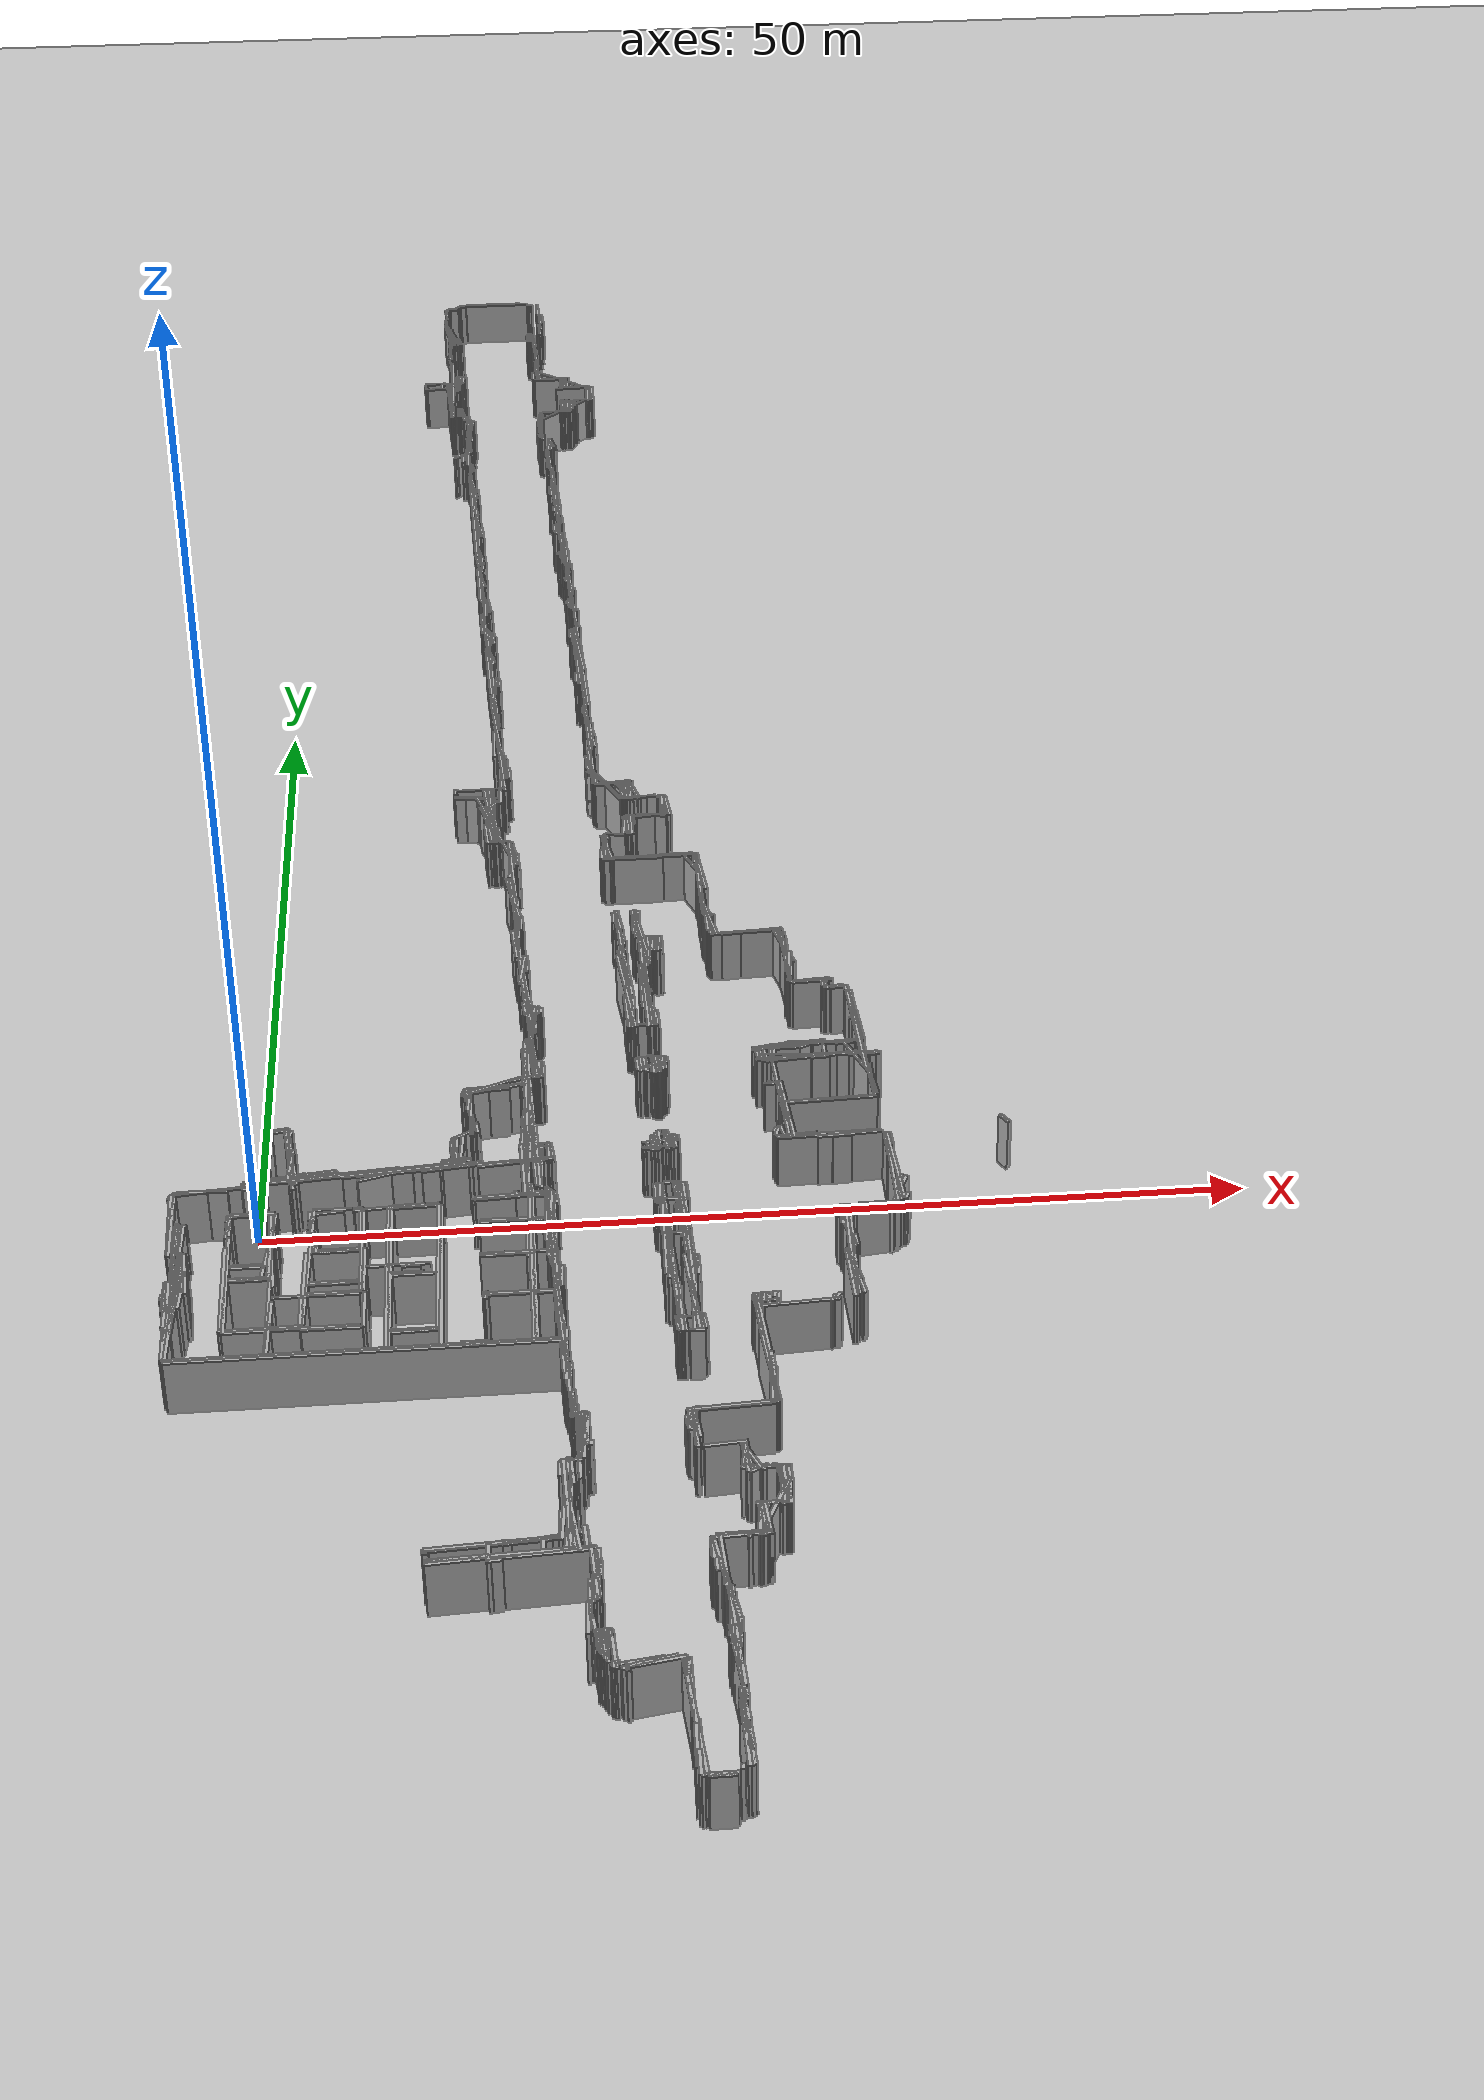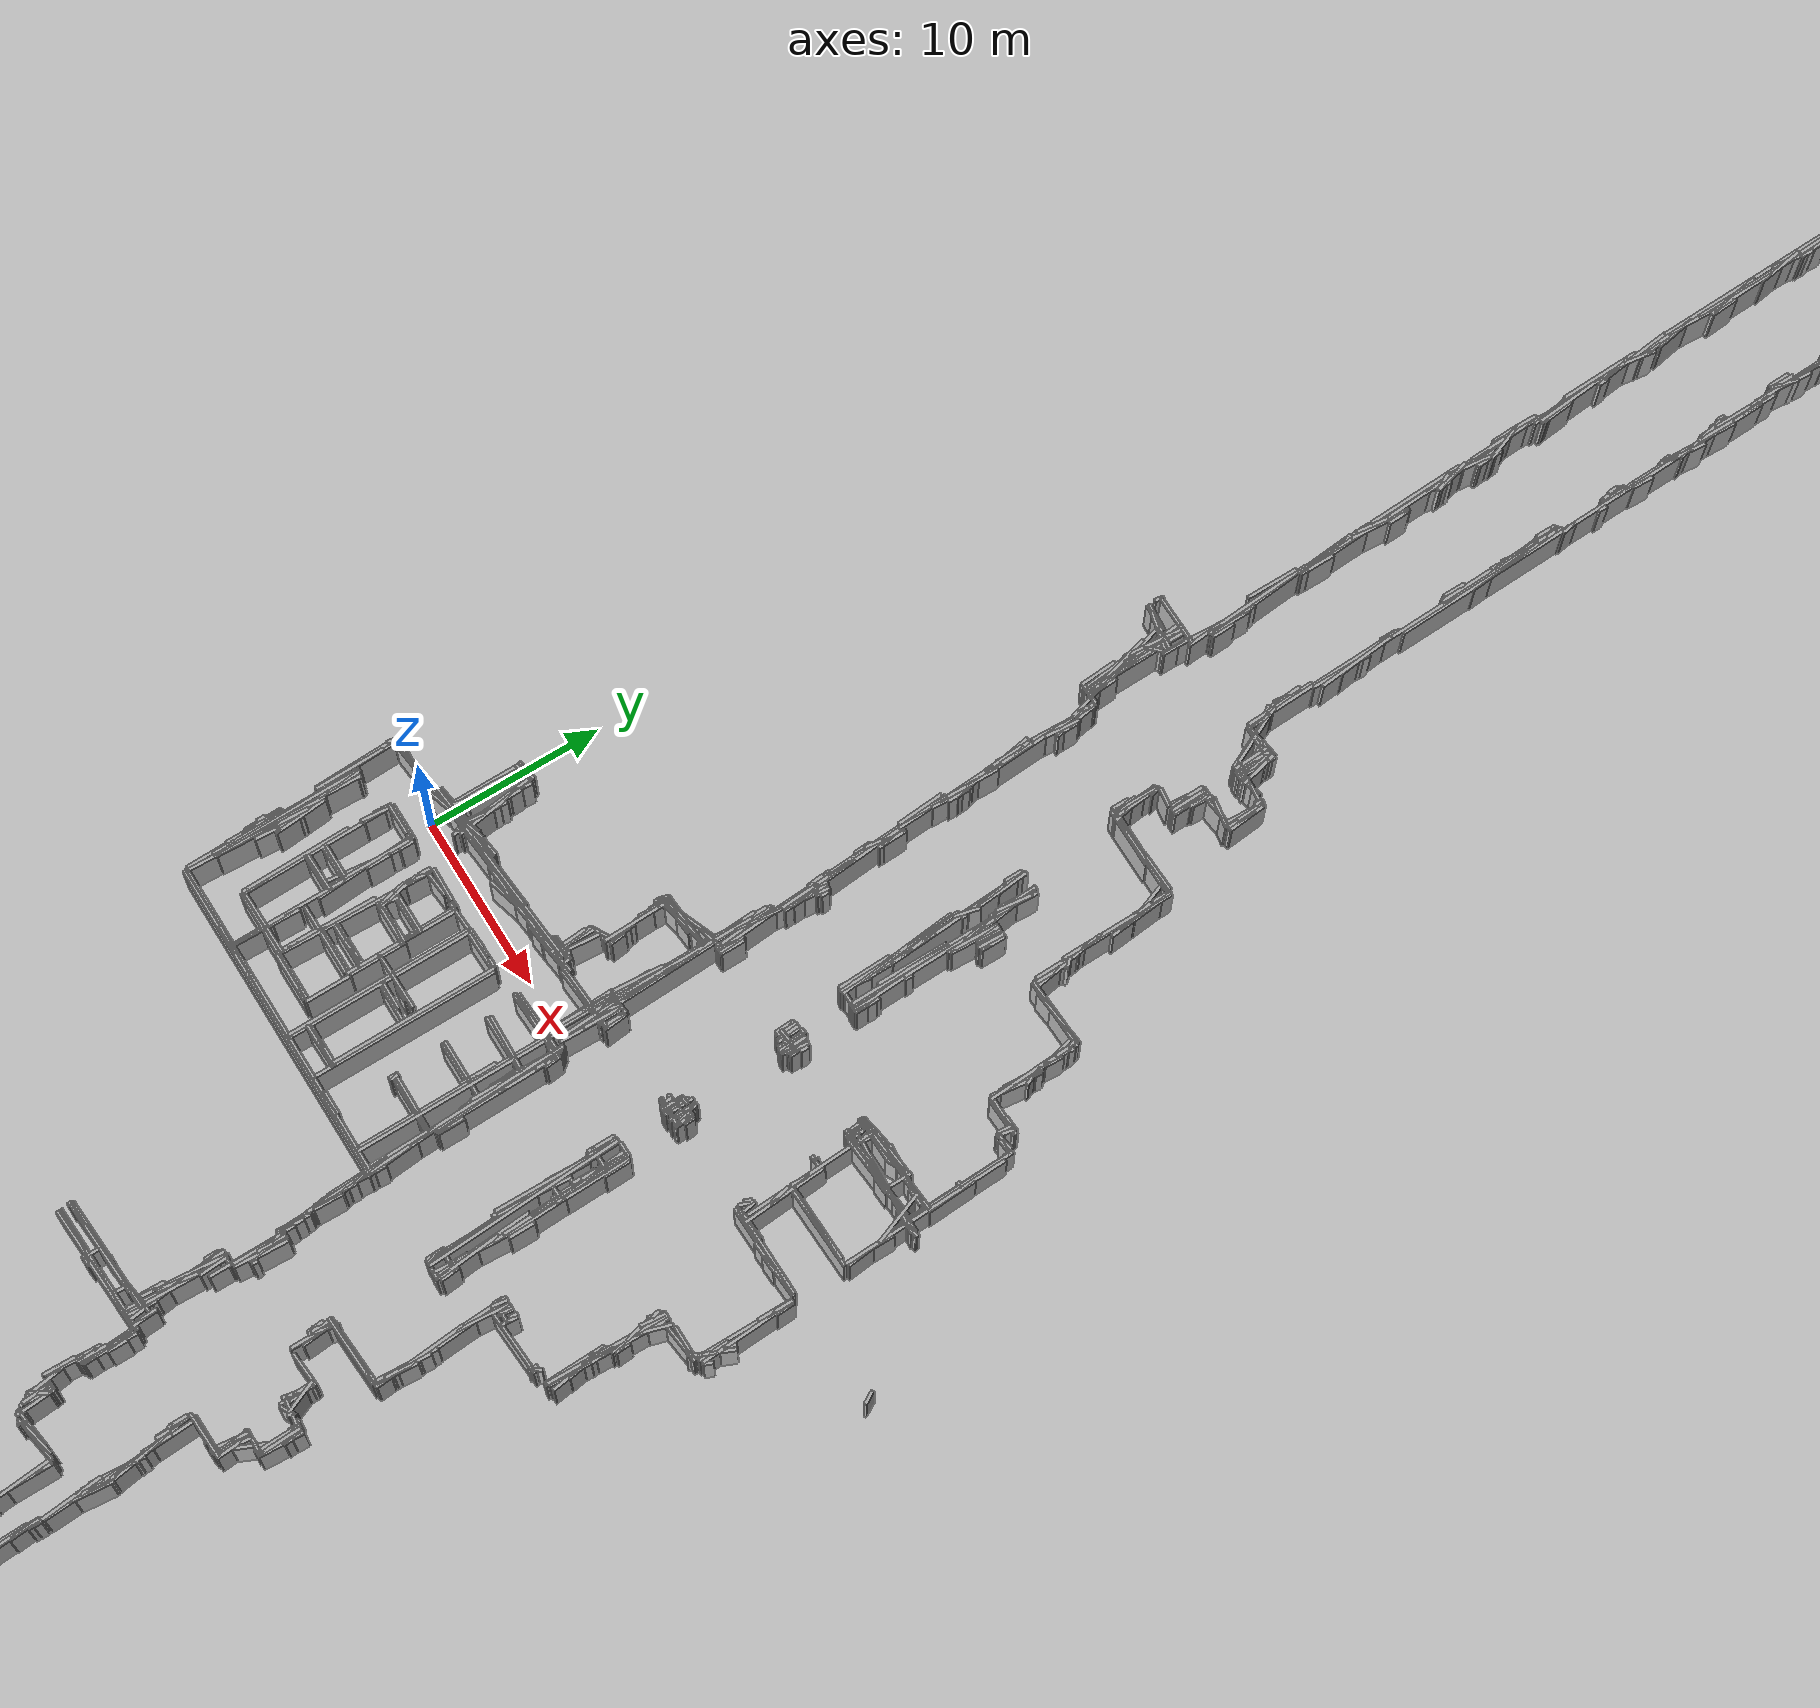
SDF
<?xml version="1.0" ?>
<sdf version="1.6">
  <world name="aboureyhan">
     <plugin name='ignition::gazebo::systems::Physics' filename='ignition-gazebo-physics-system'/>
   <plugin name='ignition::gazebo::systems::Sensors' filename='ignition-gazebo-sensors-system'>
     <render_engine>ogre2</render_engine>
   </plugin>
   <plugin name='ignition::gazebo::systems::UserCommands' filename='ignition-gazebo-user-commands-system'/>
   <plugin name='ignition::gazebo::systems::SceneBroadcaster' filename='ignition-gazebo-scene-broadcaster-system'/>
    <gravity>0 0 -9.8</gravity>
    <magnetic_field>6e-06 2.3e-05 -4.2e-05</magnetic_field>
    <atmosphere type='adiabatic'/>
    <physics type='ode'>
      <max_step_size>0.01</max_step_size>
      <real_time_factor>0</real_time_factor>
      <real_time_update_rate>0</real_time_update_rate>
    </physics>
    <scene>
      <ambient>0.4 0.4 0.4 1</ambient>
      <background>0.7 0.7 0.7 1</background>
      <shadows>true</shadows>
    </scene>
    <light name="sun" type="directional">
      <pose>0 0 10 0 0 0</pose>
      <diffuse>0.8 0.8 0.8 1</diffuse>
      <direction>-0.5 0.1 -0.9</direction>
    </light>
    <model name="ground_plane">
      <static>true</static>
      <link name="link">
        <collision name="collision">
          <geometry>
            <plane>
              <normal>0 0 1</normal>
              <size>100 100</size>
            </plane>
          </geometry>
        </collision>
        <visual name="visual">
          <geometry>
            <plane>
              <normal>0 0 1</normal>
              <size>500 500</size>
            </plane>
          </geometry>
          <material>
            <ambient>0.8 0.8 0.8 1</ambient>
            <diffuse>0.8 0.8 0.8 1</diffuse>
            <specular>0.8 0.8 0.8 1</specular>
          </material>
        </visual>
      </link>
    </model>
    <model name="wall_0">
      <static>true</static>
      <pose>17.950000000000003 52.25 1.5 0 0 -1.536027734938814</pose>
      <link name="link">
        <collision name="collision">
          <geometry>
            <box>
              <size>11.506954418958998 0.2 3.0</size>
            </box>
          </geometry>
        </collision>
        <visual name="visual">
          <geometry>
            <box>
              <size>11.506954418958998 0.2 3.0</size>
            </box>
          </geometry>
          <material>
            <ambient>0.5 0.5 0.5 1</ambient>
            <diffuse>0.7 0.7 0.7 1</diffuse>
          </material>
        </visual>
      </link>
    </model>
    <model name="wall_1">
      <static>true</static>
      <pose>17.85 59.275 1.5 0 0 -1.5359520476033424</pose>
      <link name="link">
        <collision name="collision">
          <geometry>
            <box>
              <size>22.963939122023472 0.2 3.0</size>
            </box>
          </geometry>
        </collision>
        <visual name="visual">
          <geometry>
            <box>
              <size>22.963939122023472 0.2 3.0</size>
            </box>
          </geometry>
          <material>
            <ambient>0.5 0.5 0.5 1</ambient>
            <diffuse>0.7 0.7 0.7 1</diffuse>
          </material>
        </visual>
      </link>
    </model>
    <model name="wall_2">
      <static>true</static>
      <pose>13.925000000000002 5.925000000000001 1.5 0 0 -1.5352381981834389</pose>
      <link name="link">
        <collision name="collision">
          <geometry>
            <box>
              <size>12.658001422025514 0.2 3.0</size>
            </box>
          </geometry>
        </collision>
        <visual name="visual">
          <geometry>
            <box>
              <size>12.658001422025514 0.2 3.0</size>
            </box>
          </geometry>
          <material>
            <ambient>0.5 0.5 0.5 1</ambient>
            <diffuse>0.7 0.7 0.7 1</diffuse>
          </material>
        </visual>
      </link>
    </model>
    <model name="wall_3">
      <static>true</static>
      <pose>13.325000000000001 0.9499999999999993 1.5 0 0 -1.5359267452401064</pose>
      <link name="link">
        <collision name="collision">
          <geometry>
            <box>
              <size>4.302615483633186 0.2 3.0</size>
            </box>
          </geometry>
        </collision>
        <visual name="visual">
          <geometry>
            <box>
              <size>4.302615483633186 0.2 3.0</size>
            </box>
          </geometry>
          <material>
            <ambient>0.5 0.5 0.5 1</ambient>
            <diffuse>0.7 0.7 0.7 1</diffuse>
          </material>
        </visual>
      </link>
    </model>
    <model name="wall_4">
      <static>true</static>
      <pose>5.725000000000001 -12.3 1.5 0 0 0.0</pose>
      <link name="link">
        <collision name="collision">
          <geometry>
            <box>
              <size>18.85 0.2 3.0</size>
            </box>
          </geometry>
        </collision>
        <visual name="visual">
          <geometry>
            <box>
              <size>18.85 0.2 3.0</size>
            </box>
          </geometry>
          <material>
            <ambient>0.5 0.5 0.5 1</ambient>
            <diffuse>0.7 0.7 0.7 1</diffuse>
          </material>
        </visual>
      </link>
    </model>
    <model name="wall_5">
      <static>true</static>
      <pose>11.900000000000002 67.67500000000001 1.5 0 0 -1.5195591593914772</pose>
      <link name="link">
        <collision name="collision">
          <geometry>
            <box>
              <size>1.9525624189766664 0.2 3.0</size>
            </box>
          </geometry>
        </collision>
        <visual name="visual">
          <geometry>
            <box>
              <size>1.9525624189766664 0.2 3.0</size>
            </box>
          </geometry>
          <material>
            <ambient>0.5 0.5 0.5 1</ambient>
            <diffuse>0.7 0.7 0.7 1</diffuse>
          </material>
        </visual>
      </link>
    </model>
    <model name="wall_6">
      <static>true</static>
      <pose>17.05 76.175 1.5 0 0 -1.5360277349388143</pose>
      <link name="link">
        <collision name="collision">
          <geometry>
            <box>
              <size>17.260431628438496 0.2 3.0</size>
            </box>
          </geometry>
        </collision>
        <visual name="visual">
          <geometry>
            <box>
              <size>17.260431628438496 0.2 3.0</size>
            </box>
          </geometry>
          <material>
            <ambient>0.5 0.5 0.5 1</ambient>
            <diffuse>0.7 0.7 0.7 1</diffuse>
          </material>
        </visual>
      </link>
    </model>
    <model name="wall_7">
      <static>true</static>
      <pose>13.700000000000001 17.4 1.5 0 0 -1.5191182423124665</pose>
      <link name="link">
        <collision name="collision">
          <geometry>
            <box>
              <size>17.423260314877915 0.2 3.0</size>
            </box>
          </geometry>
        </collision>
        <visual name="visual">
          <geometry>
            <box>
              <size>17.423260314877915 0.2 3.0</size>
            </box>
          </geometry>
          <material>
            <ambient>0.5 0.5 0.5 1</ambient>
            <diffuse>0.7 0.7 0.7 1</diffuse>
          </material>
        </visual>
      </link>
    </model>
    <model name="wall_8">
      <static>true</static>
      <pose>9.875 102.55 1.5 0 0 -1.5108681716736894</pose>
      <link name="link">
        <collision name="collision">
          <geometry>
            <box>
              <size>2.5044959572736385 0.2 3.0</size>
            </box>
          </geometry>
        </collision>
        <visual name="visual">
          <geometry>
            <box>
              <size>2.5044959572736385 0.2 3.0</size>
            </box>
          </geometry>
          <material>
            <ambient>0.5 0.5 0.5 1</ambient>
            <diffuse>0.7 0.7 0.7 1</diffuse>
          </material>
        </visual>
      </link>
    </model>
    <model name="wall_9">
      <static>true</static>
      <pose>12.350000000000001 52.75 1.5 0 0 -1.518894928336724</pose>
      <link name="link">
        <collision name="collision">
          <geometry>
            <box>
              <size>15.420765220960993 0.2 3.0</size>
            </box>
          </geometry>
        </collision>
        <visual name="visual">
          <geometry>
            <box>
              <size>15.420765220960993 0.2 3.0</size>
            </box>
          </geometry>
          <material>
            <ambient>0.5 0.5 0.5 1</ambient>
            <diffuse>0.7 0.7 0.7 1</diffuse>
          </material>
        </visual>
      </link>
    </model>
    <model name="wall_10">
      <static>true</static>
      <pose>9.25 -6.825000000000001 1.5 0 0 1.5707963267948966</pose>
      <link name="link">
        <collision name="collision">
          <geometry>
            <box>
              <size>10.650000000000002 0.2 3.0</size>
            </box>
          </geometry>
        </collision>
        <visual name="visual">
          <geometry>
            <box>
              <size>10.650000000000002 0.2 3.0</size>
            </box>
          </geometry>
          <material>
            <ambient>0.5 0.5 0.5 1</ambient>
            <diffuse>0.7 0.7 0.7 1</diffuse>
          </material>
        </visual>
      </link>
    </model>
    <model name="wall_11">
      <static>true</static>
      <pose>6.800000000000001 -6.775 1.5 0 0 1.5707963267948966</pose>
      <link name="link">
        <collision name="collision">
          <geometry>
            <box>
              <size>10.750000000000004 0.2 3.0</size>
            </box>
          </geometry>
        </collision>
        <visual name="visual">
          <geometry>
            <box>
              <size>10.750000000000004 0.2 3.0</size>
            </box>
          </geometry>
          <material>
            <ambient>0.5 0.5 0.5 1</ambient>
            <diffuse>0.7 0.7 0.7 1</diffuse>
          </material>
        </visual>
      </link>
    </model>
    <model name="wall_12">
      <static>true</static>
      <pose>11.675 64.45 1.5 0 0 -1.538199181676944</pose>
      <link name="link">
        <collision name="collision">
          <geometry>
            <box>
              <size>4.602445002387312 0.2 3.0</size>
            </box>
          </geometry>
        </collision>
        <visual name="visual">
          <geometry>
            <box>
              <size>4.602445002387312 0.2 3.0</size>
            </box>
          </geometry>
          <material>
            <ambient>0.5 0.5 0.5 1</ambient>
            <diffuse>0.7 0.7 0.7 1</diffuse>
          </material>
        </visual>
      </link>
    </model>
    <model name="wall_13">
      <static>true</static>
      <pose>13.225000000000001 39.95 1.5 0 0 -1.5323537367737112</pose>
      <link name="link">
        <collision name="collision">
          <geometry>
            <box>
              <size>1.30096118312578 0.2 3.0</size>
            </box>
          </geometry>
        </collision>
        <visual name="visual">
          <geometry>
            <box>
              <size>1.30096118312578 0.2 3.0</size>
            </box>
          </geometry>
          <material>
            <ambient>0.5 0.5 0.5 1</ambient>
            <diffuse>0.7 0.7 0.7 1</diffuse>
          </material>
        </visual>
      </link>
    </model>
    <model name="wall_14">
      <static>true</static>
      <pose>16.1 -32.0 1.5 0 0 -1.515297821549179</pose>
      <link name="link">
        <collision name="collision">
          <geometry>
            <box>
              <size>1.802775637731999 0.2 3.0</size>
            </box>
          </geometry>
        </collision>
        <visual name="visual">
          <geometry>
            <box>
              <size>1.802775637731999 0.2 3.0</size>
            </box>
          </geometry>
          <material>
            <ambient>0.5 0.5 0.5 1</ambient>
            <diffuse>0.7 0.7 0.7 1</diffuse>
          </material>
        </visual>
      </link>
    </model>
    <model name="wall_15">
      <static>true</static>
      <pose>17.125 78.275 1.5 0 0 -1.5353501865361818</pose>
      <link name="link">
        <collision name="collision">
          <geometry>
            <box>
              <size>7.054431231502647 0.2 3.0</size>
            </box>
          </geometry>
        </collision>
        <visual name="visual">
          <geometry>
            <box>
              <size>7.054431231502647 0.2 3.0</size>
            </box>
          </geometry>
          <material>
            <ambient>0.5 0.5 0.5 1</ambient>
            <diffuse>0.7 0.7 0.7 1</diffuse>
          </material>
        </visual>
      </link>
    </model>
    <model name="wall_16">
      <static>true</static>
      <pose>6.65 -6.850000000000003 1.5 0 0 1.5707963267948966</pose>
      <link name="link">
        <collision name="collision">
          <geometry>
            <box>
              <size>10.599999999999998 0.2 3.0</size>
            </box>
          </geometry>
        </collision>
        <visual name="visual">
          <geometry>
            <box>
              <size>10.599999999999998 0.2 3.0</size>
            </box>
          </geometry>
          <material>
            <ambient>0.5 0.5 0.5 1</ambient>
            <diffuse>0.7 0.7 0.7 1</diffuse>
          </material>
        </visual>
      </link>
    </model>
    <model name="wall_17">
      <static>true</static>
      <pose>21.625 -30.375 1.5 0 0 -1.5205593019355559</pose>
      <link name="link">
        <collision name="collision">
          <geometry>
            <box>
              <size>8.961305708433342 0.2 3.0</size>
            </box>
          </geometry>
        </collision>
        <visual name="visual">
          <geometry>
            <box>
              <size>8.961305708433342 0.2 3.0</size>
            </box>
          </geometry>
          <material>
            <ambient>0.5 0.5 0.5 1</ambient>
            <diffuse>0.7 0.7 0.7 1</diffuse>
          </material>
        </visual>
      </link>
    </model>
    <model name="wall_18">
      <static>true</static>
      <pose>5.700000000000001 -12.150000000000002 1.5 0 0 0.0</pose>
      <link name="link">
        <collision name="collision">
          <geometry>
            <box>
              <size>18.900000000000002 0.2 3.0</size>
            </box>
          </geometry>
        </collision>
        <visual name="visual">
          <geometry>
            <box>
              <size>18.900000000000002 0.2 3.0</size>
            </box>
          </geometry>
          <material>
            <ambient>0.5 0.5 0.5 1</ambient>
            <diffuse>0.7 0.7 0.7 1</diffuse>
          </material>
        </visual>
      </link>
    </model>
    <model name="wall_19">
      <static>true</static>
      <pose>18.175 42.95 1.5 0 0 -1.5343541341854636</pose>
      <link name="link">
        <collision name="collision">
          <geometry>
            <box>
              <size>9.606378089581936 0.2 3.0</size>
            </box>
          </geometry>
        </collision>
        <visual name="visual">
          <geometry>
            <box>
              <size>9.606378089581936 0.2 3.0</size>
            </box>
          </geometry>
          <material>
            <ambient>0.5 0.5 0.5 1</ambient>
            <diffuse>0.7 0.7 0.7 1</diffuse>
          </material>
        </visual>
      </link>
    </model>
    <model name="wall_20">
      <static>true</static>
      <pose>14.800000000000002 -23.375000000000004 1.5 0 0 -1.5366216031787017</pose>
      <link name="link">
        <collision name="collision">
          <geometry>
            <box>
              <size>5.853417805009311 0.2 3.0</size>
            </box>
          </geometry>
        </collision>
        <visual name="visual">
          <geometry>
            <box>
              <size>5.853417805009311 0.2 3.0</size>
            </box>
          </geometry>
          <material>
            <ambient>0.5 0.5 0.5 1</ambient>
            <diffuse>0.7 0.7 0.7 1</diffuse>
          </material>
        </visual>
      </link>
    </model>
    <model name="wall_21">
      <static>true</static>
      <pose>15.850000000000001 -27.775000000000002 1.5 0 0 -1.5093353709121298</pose>
      <link name="link">
        <collision name="collision">
          <geometry>
            <box>
              <size>3.2561480310329873 0.2 3.0</size>
            </box>
          </geometry>
        </collision>
        <visual name="visual">
          <geometry>
            <box>
              <size>3.2561480310329873 0.2 3.0</size>
            </box>
          </geometry>
          <material>
            <ambient>0.5 0.5 0.5 1</ambient>
            <diffuse>0.7 0.7 0.7 1</diffuse>
          </material>
        </visual>
      </link>
    </model>
    <model name="wall_22">
      <static>true</static>
      <pose>17.725 54.150000000000006 1.5 0 0 -1.5370253871899826</pose>
      <link name="link">
        <collision name="collision">
          <geometry>
            <box>
              <size>7.404221768693864 0.2 3.0</size>
            </box>
          </geometry>
        </collision>
        <visual name="visual">
          <geometry>
            <box>
              <size>7.404221768693864 0.2 3.0</size>
            </box>
          </geometry>
          <material>
            <ambient>0.5 0.5 0.5 1</ambient>
            <diffuse>0.7 0.7 0.7 1</diffuse>
          </material>
        </visual>
      </link>
    </model>
    <model name="wall_23">
      <static>true</static>
      <pose>14.200000000000001 14.275000000000002 1.5 0 0 -1.5243181954438947</pose>
      <link name="link">
        <collision name="collision">
          <geometry>
            <box>
              <size>2.152324325003087 0.2 3.0</size>
            </box>
          </geometry>
        </collision>
        <visual name="visual">
          <geometry>
            <box>
              <size>2.152324325003087 0.2 3.0</size>
            </box>
          </geometry>
          <material>
            <ambient>0.5 0.5 0.5 1</ambient>
            <diffuse>0.7 0.7 0.7 1</diffuse>
          </material>
        </visual>
      </link>
    </model>
    <model name="wall_24">
      <static>true</static>
      <pose>21.700000000000003 -32.45 1.5 0 0 -1.5707963267948966</pose>
      <link name="link">
        <collision name="collision">
          <geometry>
            <box>
              <size>0.5 0.2 3.0</size>
            </box>
          </geometry>
        </collision>
        <visual name="visual">
          <geometry>
            <box>
              <size>0.5 0.2 3.0</size>
            </box>
          </geometry>
          <material>
            <ambient>0.5 0.5 0.5 1</ambient>
            <diffuse>0.7 0.7 0.7 1</diffuse>
          </material>
        </visual>
      </link>
    </model>
    <model name="wall_25">
      <static>true</static>
      <pose>9.775 93.75000000000001 1.5 0 0 -1.5125290238253635</pose>
      <link name="link">
        <collision name="collision">
          <geometry>
            <box>
              <size>6.010199663904686 0.2 3.0</size>
            </box>
          </geometry>
        </collision>
        <visual name="visual">
          <geometry>
            <box>
              <size>6.010199663904686 0.2 3.0</size>
            </box>
          </geometry>
          <material>
            <ambient>0.5 0.5 0.5 1</ambient>
            <diffuse>0.7 0.7 0.7 1</diffuse>
          </material>
        </visual>
      </link>
    </model>
    <model name="wall_26">
      <static>true</static>
      <pose>12.525 56.925000000000004 1.5 0 0 -1.5385494443596421</pose>
      <link name="link">
        <collision name="collision">
          <geometry>
            <box>
              <size>1.5508062419270794 0.2 3.0</size>
            </box>
          </geometry>
        </collision>
        <visual name="visual">
          <geometry>
            <box>
              <size>1.5508062419270794 0.2 3.0</size>
            </box>
          </geometry>
          <material>
            <ambient>0.5 0.5 0.5 1</ambient>
            <diffuse>0.7 0.7 0.7 1</diffuse>
          </material>
        </visual>
      </link>
    </model>
    <model name="wall_27">
      <static>true</static>
      <pose>20.3 -6.4250000000000025 1.5 0 0 -1.5184424652716213</pose>
      <link name="link">
        <collision name="collision">
          <geometry>
            <box>
              <size>11.465709746893125 0.2 3.0</size>
            </box>
          </geometry>
        </collision>
        <visual name="visual">
          <geometry>
            <box>
              <size>11.465709746893125 0.2 3.0</size>
            </box>
          </geometry>
          <material>
            <ambient>0.5 0.5 0.5 1</ambient>
            <diffuse>0.7 0.7 0.7 1</diffuse>
          </material>
        </visual>
      </link>
    </model>
    <model name="wall_28">
      <static>true</static>
      <pose>13.600000000000001 -0.02500000000000213 1.5 0 0 1.5707963267948966</pose>
      <link name="link">
        <collision name="collision">
          <geometry>
            <box>
              <size>24.15 0.2 3.0</size>
            </box>
          </geometry>
        </collision>
        <visual name="visual">
          <geometry>
            <box>
              <size>24.15 0.2 3.0</size>
            </box>
          </geometry>
          <material>
            <ambient>0.5 0.5 0.5 1</ambient>
            <diffuse>0.7 0.7 0.7 1</diffuse>
          </material>
        </visual>
      </link>
    </model>
    <model name="wall_29">
      <static>true</static>
      <pose>12.350000000000001 35.1 1.5 0 0 -1.5544043524868911</pose>
      <link name="link">
        <collision name="collision">
          <geometry>
            <box>
              <size>6.100819617067867 0.2 3.0</size>
            </box>
          </geometry>
        </collision>
        <visual name="visual">
          <geometry>
            <box>
              <size>6.100819617067867 0.2 3.0</size>
            </box>
          </geometry>
          <material>
            <ambient>0.5 0.5 0.5 1</ambient>
            <diffuse>0.7 0.7 0.7 1</diffuse>
          </material>
        </visual>
      </link>
    </model>
    <model name="wall_30">
      <static>true</static>
      <pose>18.15 40.275 1.5 0 0 -1.5214536945419268</pose>
      <link name="link">
        <collision name="collision">
          <geometry>
            <box>
              <size>4.054935264588077 0.2 3.0</size>
            </box>
          </geometry>
        </collision>
        <visual name="visual">
          <geometry>
            <box>
              <size>4.054935264588077 0.2 3.0</size>
            </box>
          </geometry>
          <material>
            <ambient>0.5 0.5 0.5 1</ambient>
            <diffuse>0.7 0.7 0.7 1</diffuse>
          </material>
        </visual>
      </link>
    </model>
    <model name="wall_31">
      <static>true</static>
      <pose>12.325000000000001 54.15 1.5 0 0 -1.5222234514887643</pose>
      <link name="link">
        <collision name="collision">
          <geometry>
            <box>
              <size>7.208501924810732 0.2 3.0</size>
            </box>
          </geometry>
        </collision>
        <visual name="visual">
          <geometry>
            <box>
              <size>7.208501924810732 0.2 3.0</size>
            </box>
          </geometry>
          <material>
            <ambient>0.5 0.5 0.5 1</ambient>
            <diffuse>0.7 0.7 0.7 1</diffuse>
          </material>
        </visual>
      </link>
    </model>
    <model name="wall_32">
      <static>true</static>
      <pose>12.225000000000001 -26.275000000000002 1.5 0 0 0.03354445956167839</pose>
      <link name="link">
        <collision name="collision">
          <geometry>
            <box>
              <size>7.45419345066923 0.2 3.0</size>
            </box>
          </geometry>
        </collision>
        <visual name="visual">
          <geometry>
            <box>
              <size>7.45419345066923 0.2 3.0</size>
            </box>
          </geometry>
          <material>
            <ambient>0.5 0.5 0.5 1</ambient>
            <diffuse>0.7 0.7 0.7 1</diffuse>
          </material>
        </visual>
      </link>
    </model>
    <model name="wall_33">
      <static>true</static>
      <pose>20.450000000000003 -6.4250000000000025 1.5 0 0 -1.5184424652716215</pose>
      <link name="link">
        <collision name="collision">
          <geometry>
            <box>
              <size>11.465709746893124 0.2 3.0</size>
            </box>
          </geometry>
        </collision>
        <visual name="visual">
          <geometry>
            <box>
              <size>11.465709746893124 0.2 3.0</size>
            </box>
          </geometry>
          <material>
            <ambient>0.5 0.5 0.5 1</ambient>
            <diffuse>0.7 0.7 0.7 1</diffuse>
          </material>
        </visual>
      </link>
    </model>
    <model name="wall_34">
      <static>true</static>
      <pose>18.55 30.475 1.5 0 0 -1.501939837493851</pose>
      <link name="link">
        <collision name="collision">
          <geometry>
            <box>
              <size>1.453444185374866 0.2 3.0</size>
            </box>
          </geometry>
        </collision>
        <visual name="visual">
          <geometry>
            <box>
              <size>1.453444185374866 0.2 3.0</size>
            </box>
          </geometry>
          <material>
            <ambient>0.5 0.5 0.5 1</ambient>
            <diffuse>0.7 0.7 0.7 1</diffuse>
          </material>
        </visual>
      </link>
    </model>
    <model name="wall_35">
      <static>true</static>
      <pose>11.275 88.4 1.5 0 0 -1.5291537476963075</pose>
      <link name="link">
        <collision name="collision">
          <geometry>
            <box>
              <size>3.6031236448392883 0.2 3.0</size>
            </box>
          </geometry>
        </collision>
        <visual name="visual">
          <geometry>
            <box>
              <size>3.6031236448392883 0.2 3.0</size>
            </box>
          </geometry>
          <material>
            <ambient>0.5 0.5 0.5 1</ambient>
            <diffuse>0.7 0.7 0.7 1</diffuse>
          </material>
        </visual>
      </link>
    </model>
    <model name="wall_36">
      <static>true</static>
      <pose>24.475 -14.850000000000001 1.5 0 0 -1.4860938159252384</pose>
      <link name="link">
        <collision name="collision">
          <geometry>
            <box>
              <size>5.3190694674914685 0.2 3.0</size>
            </box>
          </geometry>
        </collision>
        <visual name="visual">
          <geometry>
            <box>
              <size>5.3190694674914685 0.2 3.0</size>
            </box>
          </geometry>
          <material>
            <ambient>0.5 0.5 0.5 1</ambient>
            <diffuse>0.7 0.7 0.7 1</diffuse>
          </material>
        </visual>
      </link>
    </model>
    <model name="wall_37">
      <static>true</static>
      <pose>11.825000000000001 58.22500000000001 1.5 0 0 -1.530817639671606</pose>
      <link name="link">
        <collision name="collision">
          <geometry>
            <box>
              <size>1.2509996003196804 0.2 3.0</size>
            </box>
          </geometry>
        </collision>
        <visual name="visual">
          <geometry>
            <box>
              <size>1.2509996003196804 0.2 3.0</size>
            </box>
          </geometry>
          <material>
            <ambient>0.5 0.5 0.5 1</ambient>
            <diffuse>0.7 0.7 0.7 1</diffuse>
          </material>
        </visual>
      </link>
    </model>
    <model name="wall_38">
      <static>true</static>
      <pose>17.450000000000003 57.050000000000004 1.5 0 0 -1.5707963267948966</pose>
      <link name="link">
        <collision name="collision">
          <geometry>
            <box>
              <size>0.8999999999999915 0.2 3.0</size>
            </box>
          </geometry>
        </collision>
        <visual name="visual">
          <geometry>
            <box>
              <size>0.8999999999999915 0.2 3.0</size>
            </box>
          </geometry>
          <material>
            <ambient>0.5 0.5 0.5 1</ambient>
            <diffuse>0.7 0.7 0.7 1</diffuse>
          </material>
        </visual>
      </link>
    </model>
    <model name="wall_39">
      <static>true</static>
      <pose>12.775 51.1 1.5 0 0 -1.5291537476963077</pose>
      <link name="link">
        <collision name="collision">
          <geometry>
            <box>
              <size>1.2010412149464342 0.2 3.0</size>
            </box>
          </geometry>
        </collision>
        <visual name="visual">
          <geometry>
            <box>
              <size>1.2010412149464342 0.2 3.0</size>
            </box>
          </geometry>
          <material>
            <ambient>0.5 0.5 0.5 1</ambient>
            <diffuse>0.7 0.7 0.7 1</diffuse>
          </material>
        </visual>
      </link>
    </model>
    <model name="wall_40">
      <static>true</static>
      <pose>11.350000000000001 74.80000000000001 1.5 0 0 -1.5385494443596428</pose>
      <link name="link">
        <collision name="collision">
          <geometry>
            <box>
              <size>12.40644993541665 0.2 3.0</size>
            </box>
          </geometry>
        </collision>
        <visual name="visual">
          <geometry>
            <box>
              <size>12.40644993541665 0.2 3.0</size>
            </box>
          </geometry>
          <material>
            <ambient>0.5 0.5 0.5 1</ambient>
            <diffuse>0.7 0.7 0.7 1</diffuse>
          </material>
        </visual>
      </link>
    </model>
    <model name="wall_41">
      <static>true</static>
      <pose>9.75 103.525 1.5 0 0 -1.5707963267948966</pose>
      <link name="link">
        <collision name="collision">
          <geometry>
            <box>
              <size>0.45000000000001705 0.2 3.0</size>
            </box>
          </geometry>
        </collision>
        <visual name="visual">
          <geometry>
            <box>
              <size>0.45000000000001705 0.2 3.0</size>
            </box>
          </geometry>
          <material>
            <ambient>0.5 0.5 0.5 1</ambient>
            <diffuse>0.7 0.7 0.7 1</diffuse>
          </material>
        </visual>
      </link>
    </model>
    <model name="wall_42">
      <static>true</static>
      <pose>15.725000000000001 104.625 1.5 0 0 -1.5405025668761234</pose>
      <link name="link">
        <collision name="collision">
          <geometry>
            <box>
              <size>1.6507574019219233 0.2 3.0</size>
            </box>
          </geometry>
        </collision>
        <visual name="visual">
          <geometry>
            <box>
              <size>1.6507574019219233 0.2 3.0</size>
            </box>
          </geometry>
          <material>
            <ambient>0.5 0.5 0.5 1</ambient>
            <diffuse>0.7 0.7 0.7 1</diffuse>
          </material>
        </visual>
      </link>
    </model>
    <model name="wall_43">
      <static>true</static>
      <pose>19.200000000000003 16.375 1.5 0 0 -1.4704154237119258</pose>
      <link name="link">
        <collision name="collision">
          <geometry>
            <box>
              <size>6.98516284706377 0.2 3.0</size>
            </box>
          </geometry>
        </collision>
        <visual name="visual">
          <geometry>
            <box>
              <size>6.98516284706377 0.2 3.0</size>
            </box>
          </geometry>
          <material>
            <ambient>0.5 0.5 0.5 1</ambient>
            <diffuse>0.7 0.7 0.7 1</diffuse>
          </material>
        </visual>
      </link>
    </model>
    <model name="wall_44">
      <static>true</static>
      <pose>20.575000000000003 37.4 1.5 0 0 -1.3258176636680326</pose>
      <link name="link">
        <collision name="collision">
          <geometry>
            <box>
              <size>2.2677080940897163 0.2 3.0</size>
            </box>
          </geometry>
        </collision>
        <visual name="visual">
          <geometry>
            <box>
              <size>2.2677080940897163 0.2 3.0</size>
            </box>
          </geometry>
          <material>
            <ambient>0.5 0.5 0.5 1</ambient>
            <diffuse>0.7 0.7 0.7 1</diffuse>
          </material>
        </visual>
      </link>
    </model>
    <model name="wall_45">
      <static>true</static>
      <pose>21.225 -4.725000000000001 1.5 0 0 -1.5397504045508734</pose>
      <link name="link">
        <collision name="collision">
          <geometry>
            <box>
              <size>8.05388105201461 0.2 3.0</size>
            </box>
          </geometry>
        </collision>
        <visual name="visual">
          <geometry>
            <box>
              <size>8.05388105201461 0.2 3.0</size>
            </box>
          </geometry>
          <material>
            <ambient>0.5 0.5 0.5 1</ambient>
            <diffuse>0.7 0.7 0.7 1</diffuse>
          </material>
        </visual>
      </link>
    </model>
    <model name="wall_46">
      <static>true</static>
      <pose>14.700000000000003 -7.575000000000001 1.5 0 0 -1.5354753335833098</pose>
      <link name="link">
        <collision name="collision">
          <geometry>
            <box>
              <size>14.158831166448735 0.2 3.0</size>
            </box>
          </geometry>
        </collision>
        <visual name="visual">
          <geometry>
            <box>
              <size>14.158831166448735 0.2 3.0</size>
            </box>
          </geometry>
          <material>
            <ambient>0.5 0.5 0.5 1</ambient>
            <diffuse>0.7 0.7 0.7 1</diffuse>
          </material>
        </visual>
      </link>
    </model>
    <model name="wall_47">
      <static>true</static>
      <pose>13.3 27.275 1.5 0 0 -1.5195591593914772</pose>
      <link name="link">
        <collision name="collision">
          <geometry>
            <box>
              <size>1.9525624189766664 0.2 3.0</size>
            </box>
          </geometry>
        </collision>
        <visual name="visual">
          <geometry>
            <box>
              <size>1.9525624189766664 0.2 3.0</size>
            </box>
          </geometry>
          <material>
            <ambient>0.5 0.5 0.5 1</ambient>
            <diffuse>0.7 0.7 0.7 1</diffuse>
          </material>
        </visual>
      </link>
    </model>
    <model name="wall_48">
      <static>true</static>
      <pose>16.700000000000003 107.72500000000001 1.5 0 0 -1.5369109968907797</pose>
      <link name="link">
        <collision name="collision">
          <geometry>
            <box>
              <size>2.951694428629077 0.2 3.0</size>
            </box>
          </geometry>
        </collision>
        <visual name="visual">
          <geometry>
            <box>
              <size>2.951694428629077 0.2 3.0</size>
            </box>
          </geometry>
          <material>
            <ambient>0.5 0.5 0.5 1</ambient>
            <diffuse>0.7 0.7 0.7 1</diffuse>
          </material>
        </visual>
      </link>
    </model>
    <model name="wall_49">
      <static>true</static>
      <pose>9.100000000000001 -6.225 1.5 0 0 1.5707963267948966</pose>
      <link name="link">
        <collision name="collision">
          <geometry>
            <box>
              <size>9.650000000000002 0.2 3.0</size>
            </box>
          </geometry>
        </collision>
        <visual name="visual">
          <geometry>
            <box>
              <size>9.650000000000002 0.2 3.0</size>
            </box>
          </geometry>
          <material>
            <ambient>0.5 0.5 0.5 1</ambient>
            <diffuse>0.7 0.7 0.7 1</diffuse>
          </material>
        </visual>
      </link>
    </model>
    <model name="wall_50">
      <static>true</static>
      <pose>21.400000000000002 -39.25 1.5 0 0 -1.5707963267948966</pose>
      <link name="link">
        <collision name="collision">
          <geometry>
            <box>
              <size>0.30000000000000426 0.2 3.0</size>
            </box>
          </geometry>
        </collision>
        <visual name="visual">
          <geometry>
            <box>
              <size>0.30000000000000426 0.2 3.0</size>
            </box>
          </geometry>
          <material>
            <ambient>0.5 0.5 0.5 1</ambient>
            <diffuse>0.7 0.7 0.7 1</diffuse>
          </material>
        </visual>
      </link>
    </model>
    <model name="wall_51">
      <static>true</static>
      <pose>9.825000000000001 104.275 1.5 0 0 -1.4898922276396647</pose>
      <link name="link">
        <collision name="collision">
          <geometry>
            <box>
              <size>1.8560711193270532 0.2 3.0</size>
            </box>
          </geometry>
        </collision>
        <visual name="visual">
          <geometry>
            <box>
              <size>1.8560711193270532 0.2 3.0</size>
            </box>
          </geometry>
          <material>
            <ambient>0.5 0.5 0.5 1</ambient>
            <diffuse>0.7 0.7 0.7 1</diffuse>
          </material>
        </visual>
      </link>
    </model>
    <model name="wall_52">
      <static>true</static>
      <pose>10.025 105.275 1.5 0 0 -1.4601391056210018</pose>
      <link name="link">
        <collision name="collision">
          <geometry>
            <box>
              <size>3.169384798348101 0.2 3.0</size>
            </box>
          </geometry>
        </collision>
        <visual name="visual">
          <geometry>
            <box>
              <size>3.169384798348101 0.2 3.0</size>
            </box>
          </geometry>
          <material>
            <ambient>0.5 0.5 0.5 1</ambient>
            <diffuse>0.7 0.7 0.7 1</diffuse>
          </material>
        </visual>
      </link>
    </model>
    <model name="wall_53">
      <static>true</static>
      <pose>11.375000000000002 89.25 1.5 0 0 -1.544486609541974</pose>
      <link name="link">
        <collision name="collision">
          <geometry>
            <box>
              <size>1.9006577808748268 0.2 3.0</size>
            </box>
          </geometry>
        </collision>
        <visual name="visual">
          <geometry>
            <box>
              <size>1.9006577808748268 0.2 3.0</size>
            </box>
          </geometry>
          <material>
            <ambient>0.5 0.5 0.5 1</ambient>
            <diffuse>0.7 0.7 0.7 1</diffuse>
          </material>
        </visual>
      </link>
    </model>
    <model name="wall_54">
      <static>true</static>
      <pose>21.0 -26.725 1.5 0 0 -1.5707963267948966</pose>
      <link name="link">
        <collision name="collision">
          <geometry>
            <box>
              <size>1.0499999999999972 0.2 3.0</size>
            </box>
          </geometry>
        </collision>
        <visual name="visual">
          <geometry>
            <box>
              <size>1.0499999999999972 0.2 3.0</size>
            </box>
          </geometry>
          <material>
            <ambient>0.5 0.5 0.5 1</ambient>
            <diffuse>0.7 0.7 0.7 1</diffuse>
          </material>
        </visual>
      </link>
    </model>
    <model name="wall_55">
      <static>true</static>
      <pose>11.900000000000002 72.15 1.5 0 0 -1.504228163019072</pose>
      <link name="link">
        <collision name="collision">
          <geometry>
            <box>
              <size>1.503329637837291 0.2 3.0</size>
            </box>
          </geometry>
        </collision>
        <visual name="visual">
          <geometry>
            <box>
              <size>1.503329637837291 0.2 3.0</size>
            </box>
          </geometry>
          <material>
            <ambient>0.5 0.5 0.5 1</ambient>
            <diffuse>0.7 0.7 0.7 1</diffuse>
          </material>
        </visual>
      </link>
    </model>
    <model name="wall_56">
      <static>true</static>
      <pose>4.850000000000001 1.375 1.5 0 0 0.0853775308067907</pose>
      <link name="link">
        <collision name="collision">
          <geometry>
            <box>
              <size>11.140578979568344 0.2 3.0</size>
            </box>
          </geometry>
        </collision>
        <visual name="visual">
          <geometry>
            <box>
              <size>11.140578979568344 0.2 3.0</size>
            </box>
          </geometry>
          <material>
            <ambient>0.5 0.5 0.5 1</ambient>
            <diffuse>0.7 0.7 0.7 1</diffuse>
          </material>
        </visual>
      </link>
    </model>
    <model name="wall_57">
      <static>true</static>
      <pose>20.6 -2.025000000000002 1.5 0 0 -0.033320995878250034</pose>
      <link name="link">
        <collision name="collision">
          <geometry>
            <box>
              <size>1.5008331019803636 0.2 3.0</size>
            </box>
          </geometry>
        </collision>
        <visual name="visual">
          <geometry>
            <box>
              <size>1.5008331019803636 0.2 3.0</size>
            </box>
          </geometry>
          <material>
            <ambient>0.5 0.5 0.5 1</ambient>
            <diffuse>0.7 0.7 0.7 1</diffuse>
          </material>
        </visual>
      </link>
    </model>
    <model name="wall_58">
      <static>true</static>
      <pose>15.975000000000001 -27.875000000000004 1.5 0 0 -1.5182132651839555</pose>
      <link name="link">
        <collision name="collision">
          <geometry>
            <box>
              <size>2.8539446385660683 0.2 3.0</size>
            </box>
          </geometry>
        </collision>
        <visual name="visual">
          <geometry>
            <box>
              <size>2.8539446385660683 0.2 3.0</size>
            </box>
          </geometry>
          <material>
            <ambient>0.5 0.5 0.5 1</ambient>
            <diffuse>0.7 0.7 0.7 1</diffuse>
          </material>
        </visual>
      </link>
    </model>
    <model name="wall_59">
      <static>true</static>
      <pose>31.950000000000003 -2.25 1.5 0 0 -1.5152978215491828</pose>
      <link name="link">
        <collision name="collision">
          <geometry>
            <box>
              <size>1.8027756377319915 0.2 3.0</size>
            </box>
          </geometry>
        </collision>
        <visual name="visual">
          <geometry>
            <box>
              <size>1.8027756377319915 0.2 3.0</size>
            </box>
          </geometry>
          <material>
            <ambient>0.5 0.5 0.5 1</ambient>
            <diffuse>0.7 0.7 0.7 1</diffuse>
          </material>
        </visual>
      </link>
    </model>
    <model name="wall_60">
      <static>true</static>
      <pose>20.125 22.0 1.5 0 0 -1.4517960334121165</pose>
      <link name="link">
        <collision name="collision">
          <geometry>
            <box>
              <size>4.632763753959395 0.2 3.0</size>
            </box>
          </geometry>
        </collision>
        <visual name="visual">
          <geometry>
            <box>
              <size>4.632763753959395 0.2 3.0</size>
            </box>
          </geometry>
          <material>
            <ambient>0.5 0.5 0.5 1</ambient>
            <diffuse>0.7 0.7 0.7 1</diffuse>
          </material>
        </visual>
      </link>
    </model>
    <model name="wall_61">
      <static>true</static>
      <pose>14.700000000000001 -5.15 1.5 0 0 -1.52377219495215</pose>
      <link name="link">
        <collision name="collision">
          <geometry>
            <box>
              <size>8.509406559801926 0.2 3.0</size>
            </box>
          </geometry>
        </collision>
        <visual name="visual">
          <geometry>
            <box>
              <size>8.509406559801926 0.2 3.0</size>
            </box>
          </geometry>
          <material>
            <ambient>0.5 0.5 0.5 1</ambient>
            <diffuse>0.7 0.7 0.7 1</diffuse>
          </material>
        </visual>
      </link>
    </model>
    <model name="wall_62">
      <static>true</static>
      <pose>19.475 9.475000000000001 1.5 0 0 -1.5232132235179159</pose>
      <link name="link">
        <collision name="collision">
          <geometry>
            <box>
              <size>1.051189802081429 0.2 3.0</size>
            </box>
          </geometry>
        </collision>
        <visual name="visual">
          <geometry>
            <box>
              <size>1.051189802081429 0.2 3.0</size>
            </box>
          </geometry>
          <material>
            <ambient>0.5 0.5 0.5 1</ambient>
            <diffuse>0.7 0.7 0.7 1</diffuse>
          </material>
        </visual>
      </link>
    </model>
    <model name="wall_63">
      <static>true</static>
      <pose>16.825000000000003 72.275 1.5 0 0 -1.530817639671606</pose>
      <link name="link">
        <collision name="collision">
          <geometry>
            <box>
              <size>1.2509996003196804 0.2 3.0</size>
            </box>
          </geometry>
        </collision>
        <visual name="visual">
          <geometry>
            <box>
              <size>1.2509996003196804 0.2 3.0</size>
            </box>
          </geometry>
          <material>
            <ambient>0.5 0.5 0.5 1</ambient>
            <diffuse>0.7 0.7 0.7 1</diffuse>
          </material>
        </visual>
      </link>
    </model>
    <model name="wall_64">
      <static>true</static>
      <pose>13.875000000000002 19.5 1.5 0 0 -1.5350972141155723</pose>
      <link name="link">
        <collision name="collision">
          <geometry>
            <box>
              <size>1.4008925726121957 0.2 3.0</size>
            </box>
          </geometry>
        </collision>
        <visual name="visual">
          <geometry>
            <box>
              <size>1.4008925726121957 0.2 3.0</size>
            </box>
          </geometry>
          <material>
            <ambient>0.5 0.5 0.5 1</ambient>
            <diffuse>0.7 0.7 0.7 1</diffuse>
          </material>
        </visual>
      </link>
    </model>
    <model name="wall_65">
      <static>true</static>
      <pose>12.175 52.525000000000006 1.5 0 0 -1.5265773823992437</pose>
      <link name="link">
        <collision name="collision">
          <geometry>
            <box>
              <size>5.655528268871093 0.2 3.0</size>
            </box>
          </geometry>
        </collision>
        <visual name="visual">
          <geometry>
            <box>
              <size>5.655528268871093 0.2 3.0</size>
            </box>
          </geometry>
          <material>
            <ambient>0.5 0.5 0.5 1</ambient>
            <diffuse>0.7 0.7 0.7 1</diffuse>
          </material>
        </visual>
      </link>
    </model>
    <model name="wall_66">
      <static>true</static>
      <pose>-0.04999999999999938 -1.4500000000000028 1.5 0 0 0.0</pose>
      <link name="link">
        <collision name="collision">
          <geometry>
            <box>
              <size>2.2 0.2 3.0</size>
            </box>
          </geometry>
        </collision>
        <visual name="visual">
          <geometry>
            <box>
              <size>2.2 0.2 3.0</size>
            </box>
          </geometry>
          <material>
            <ambient>0.5 0.5 0.5 1</ambient>
            <diffuse>0.7 0.7 0.7 1</diffuse>
          </material>
        </visual>
      </link>
    </model>
    <model name="wall_67">
      <static>true</static>
      <pose>21.050000000000004 -3.5500000000000007 1.5 0 0 -1.5357229962616714</pose>
      <link name="link">
        <collision name="collision">
          <geometry>
            <box>
              <size>5.7035076926396755 0.2 3.0</size>
            </box>
          </geometry>
        </collision>
        <visual name="visual">
          <geometry>
            <box>
              <size>5.7035076926396755 0.2 3.0</size>
            </box>
          </geometry>
          <material>
            <ambient>0.5 0.5 0.5 1</ambient>
            <diffuse>0.7 0.7 0.7 1</diffuse>
          </material>
        </visual>
      </link>
    </model>
    <model name="wall_68">
      <static>true</static>
      <pose>24.125 23.474999999999998 1.5 0 0 -1.415432072943363</pose>
      <link name="link">
        <collision name="collision">
          <geometry>
            <box>
              <size>4.200595195921644 0.2 3.0</size>
            </box>
          </geometry>
        </collision>
        <visual name="visual">
          <geometry>
            <box>
              <size>4.200595195921644 0.2 3.0</size>
            </box>
          </geometry>
          <material>
            <ambient>0.5 0.5 0.5 1</ambient>
            <diffuse>0.7 0.7 0.7 1</diffuse>
          </material>
        </visual>
      </link>
    </model>
    <model name="wall_69">
      <static>true</static>
      <pose>11.425000000000002 79.4 1.5 0 0 -1.4405848838305002</pose>
      <link name="link">
        <collision name="collision">
          <geometry>
            <box>
              <size>4.235858826731603 0.2 3.0</size>
            </box>
          </geometry>
        </collision>
        <visual name="visual">
          <geometry>
            <box>
              <size>4.235858826731603 0.2 3.0</size>
            </box>
          </geometry>
          <material>
            <ambient>0.5 0.5 0.5 1</ambient>
            <diffuse>0.7 0.7 0.7 1</diffuse>
          </material>
        </visual>
      </link>
    </model>
    <model name="wall_70">
      <static>true</static>
      <pose>14.200000000000001 13.575000000000003 1.5 0 0 -1.5137155443886332</pose>
      <link name="link">
        <collision name="collision">
          <geometry>
            <box>
              <size>1.7528548142958102 0.2 3.0</size>
            </box>
          </geometry>
        </collision>
        <visual name="visual">
          <geometry>
            <box>
              <size>1.7528548142958102 0.2 3.0</size>
            </box>
          </geometry>
          <material>
            <ambient>0.5 0.5 0.5 1</ambient>
            <diffuse>0.7 0.7 0.7 1</diffuse>
          </material>
        </visual>
      </link>
    </model>
    <model name="wall_71">
      <static>true</static>
      <pose>20.05 16.75 1.5 0 0 1.5707963267948966</pose>
      <link name="link">
        <collision name="collision">
          <geometry>
            <box>
              <size>4.099999999999994 0.2 3.0</size>
            </box>
          </geometry>
        </collision>
        <visual name="visual">
          <geometry>
            <box>
              <size>4.099999999999994 0.2 3.0</size>
            </box>
          </geometry>
          <material>
            <ambient>0.5 0.5 0.5 1</ambient>
            <diffuse>0.7 0.7 0.7 1</diffuse>
          </material>
        </visual>
      </link>
    </model>
    <model name="wall_72">
      <static>true</static>
      <pose>21.0 9.75 1.5 0 0 -1.5707963267948966</pose>
      <link name="link">
        <collision name="collision">
          <geometry>
            <box>
              <size>0.5 0.2 3.0</size>
            </box>
          </geometry>
        </collision>
        <visual name="visual">
          <geometry>
            <box>
              <size>0.5 0.2 3.0</size>
            </box>
          </geometry>
          <material>
            <ambient>0.5 0.5 0.5 1</ambient>
            <diffuse>0.7 0.7 0.7 1</diffuse>
          </material>
        </visual>
      </link>
    </model>
    <model name="wall_73">
      <static>true</static>
      <pose>26.225 9.825 1.5 0 0 -1.460139105620997</pose>
      <link name="link">
        <collision name="collision">
          <geometry>
            <box>
              <size>1.3583077707206146 0.2 3.0</size>
            </box>
          </geometry>
        </collision>
        <visual name="visual">
          <geometry>
            <box>
              <size>1.3583077707206146 0.2 3.0</size>
            </box>
          </geometry>
          <material>
            <ambient>0.5 0.5 0.5 1</ambient>
            <diffuse>0.7 0.7 0.7 1</diffuse>
          </material>
        </visual>
      </link>
    </model>
    <model name="wall_74">
      <static>true</static>
      <pose>20.25 20.95 1.5 0 0 -1.5707963267948966</pose>
      <link name="link">
        <collision name="collision">
          <geometry>
            <box>
              <size>1.3000000000000043 0.2 3.0</size>
            </box>
          </geometry>
        </collision>
        <visual name="visual">
          <geometry>
            <box>
              <size>1.3000000000000043 0.2 3.0</size>
            </box>
          </geometry>
          <material>
            <ambient>0.5 0.5 0.5 1</ambient>
            <diffuse>0.7 0.7 0.7 1</diffuse>
          </material>
        </visual>
      </link>
    </model>
    <model name="wall_75">
      <static>true</static>
      <pose>19.225 20.099999999999998 1.5 0 0 -1.5054134647160544</pose>
      <link name="link">
        <collision name="collision">
          <geometry>
            <box>
              <size>8.417986695166485 0.2 3.0</size>
            </box>
          </geometry>
        </collision>
        <visual name="visual">
          <geometry>
            <box>
              <size>8.417986695166485 0.2 3.0</size>
            </box>
          </geometry>
          <material>
            <ambient>0.5 0.5 0.5 1</ambient>
            <diffuse>0.7 0.7 0.7 1</diffuse>
          </material>
        </visual>
      </link>
    </model>
    <model name="wall_76">
      <static>true</static>
      <pose>19.85 9.5 1.5 0 0 -1.4940244355251173</pose>
      <link name="link">
        <collision name="collision">
          <geometry>
            <box>
              <size>1.303840481040527 0.2 3.0</size>
            </box>
          </geometry>
        </collision>
        <visual name="visual">
          <geometry>
            <box>
              <size>1.303840481040527 0.2 3.0</size>
            </box>
          </geometry>
          <material>
            <ambient>0.5 0.5 0.5 1</ambient>
            <diffuse>0.7 0.7 0.7 1</diffuse>
          </material>
        </visual>
      </link>
    </model>
    <model name="wall_77">
      <static>true</static>
      <pose>20.525 9.400000000000002 1.5 0 0 -1.539556493364628</pose>
      <link name="link">
        <collision name="collision">
          <geometry>
            <box>
              <size>1.6007810593582135 0.2 3.0</size>
            </box>
          </geometry>
        </collision>
        <visual name="visual">
          <geometry>
            <box>
              <size>1.6007810593582135 0.2 3.0</size>
            </box>
          </geometry>
          <material>
            <ambient>0.5 0.5 0.5 1</ambient>
            <diffuse>0.7 0.7 0.7 1</diffuse>
          </material>
        </visual>
      </link>
    </model>
    <model name="wall_78">
      <static>true</static>
      <pose>21.75 -37.275000000000006 1.5 0 0 -1.520206618025512</pose>
      <link name="link">
        <collision name="collision">
          <geometry>
            <box>
              <size>3.955060050113015 0.2 3.0</size>
            </box>
          </geometry>
        </collision>
        <visual name="visual">
          <geometry>
            <box>
              <size>3.955060050113015 0.2 3.0</size>
            </box>
          </geometry>
          <material>
            <ambient>0.5 0.5 0.5 1</ambient>
            <diffuse>0.7 0.7 0.7 1</diffuse>
          </material>
        </visual>
      </link>
    </model>
    <model name="wall_79">
      <static>true</static>
      <pose>14.825000000000001 -1.4499999999999993 1.5 0 0 -1.525373047373319</pose>
      <link name="link">
        <collision name="collision">
          <geometry>
            <box>
              <size>1.1011357772772634 0.2 3.0</size>
            </box>
          </geometry>
        </collision>
        <visual name="visual">
          <geometry>
            <box>
              <size>1.1011357772772634 0.2 3.0</size>
            </box>
          </geometry>
          <material>
            <ambient>0.5 0.5 0.5 1</ambient>
            <diffuse>0.7 0.7 0.7 1</diffuse>
          </material>
        </visual>
      </link>
    </model>
    <model name="wall_80">
      <static>true</static>
      <pose>20.1 -5.125000000000002 1.5 0 0 1.552780258240841</pose>
      <link name="link">
        <collision name="collision">
          <geometry>
            <box>
              <size>5.5509008277936305 0.2 3.0</size>
            </box>
          </geometry>
        </collision>
        <visual name="visual">
          <geometry>
            <box>
              <size>5.5509008277936305 0.2 3.0</size>
            </box>
          </geometry>
          <material>
            <ambient>0.5 0.5 0.5 1</ambient>
            <diffuse>0.7 0.7 0.7 1</diffuse>
          </material>
        </visual>
      </link>
    </model>
    <model name="wall_81">
      <static>true</static>
      <pose>9.575000000000001 109.65 1.5 0 0 -1.492012365805752</pose>
      <link name="link">
        <collision name="collision">
          <geometry>
            <box>
              <size>1.9059118552545977 0.2 3.0</size>
            </box>
          </geometry>
        </collision>
        <visual name="visual">
          <geometry>
            <box>
              <size>1.9059118552545977 0.2 3.0</size>
            </box>
          </geometry>
          <material>
            <ambient>0.5 0.5 0.5 1</ambient>
            <diffuse>0.7 0.7 0.7 1</diffuse>
          </material>
        </visual>
      </link>
    </model>
    <model name="wall_82">
      <static>true</static>
      <pose>15.025 -7.550000000000001 1.5 0 0 1.539556493364628</pose>
      <link name="link">
        <collision name="collision">
          <geometry>
            <box>
              <size>1.6007810593582135 0.2 3.0</size>
            </box>
          </geometry>
        </collision>
        <visual name="visual">
          <geometry>
            <box>
              <size>1.6007810593582135 0.2 3.0</size>
            </box>
          </geometry>
          <material>
            <ambient>0.5 0.5 0.5 1</ambient>
            <diffuse>0.7 0.7 0.7 1</diffuse>
          </material>
        </visual>
      </link>
    </model>
    <model name="wall_83">
      <static>true</static>
      <pose>9.9 93.825 1.5 0 0 -1.519559159391478</pose>
      <link name="link">
        <collision name="collision">
          <geometry>
            <box>
              <size>5.857687256930014 0.2 3.0</size>
            </box>
          </geometry>
        </collision>
        <visual name="visual">
          <geometry>
            <box>
              <size>5.857687256930014 0.2 3.0</size>
            </box>
          </geometry>
          <material>
            <ambient>0.5 0.5 0.5 1</ambient>
            <diffuse>0.7 0.7 0.7 1</diffuse>
          </material>
        </visual>
      </link>
    </model>
    <model name="wall_84">
      <static>true</static>
      <pose>19.650000000000002 -36.275000000000006 1.5 0 0 -1.4821404449274589</pose>
      <link name="link">
        <collision name="collision">
          <geometry>
            <box>
              <size>6.776614198845911 0.2 3.0</size>
            </box>
          </geometry>
        </collision>
        <visual name="visual">
          <geometry>
            <box>
              <size>6.776614198845911 0.2 3.0</size>
            </box>
          </geometry>
          <material>
            <ambient>0.5 0.5 0.5 1</ambient>
            <diffuse>0.7 0.7 0.7 1</diffuse>
          </material>
        </visual>
      </link>
    </model>
    <model name="wall_85">
      <static>true</static>
      <pose>10.250000000000002 2.724999999999998 1.5 0 0 1.4954674359665567</pose>
      <link name="link">
        <collision name="collision">
          <geometry>
            <box>
              <size>2.657536453183661 0.2 3.0</size>
            </box>
          </geometry>
        </collision>
        <visual name="visual">
          <geometry>
            <box>
              <size>2.657536453183661 0.2 3.0</size>
            </box>
          </geometry>
          <material>
            <ambient>0.5 0.5 0.5 1</ambient>
            <diffuse>0.7 0.7 0.7 1</diffuse>
          </material>
        </visual>
      </link>
    </model>
    <model name="wall_86">
      <static>true</static>
      <pose>11.825000000000001 33.175 1.5 0 0 -1.5011417530663276</pose>
      <link name="link">
        <collision name="collision">
          <geometry>
            <box>
              <size>2.1552262062252363 0.2 3.0</size>
            </box>
          </geometry>
        </collision>
        <visual name="visual">
          <geometry>
            <box>
              <size>2.1552262062252363 0.2 3.0</size>
            </box>
          </geometry>
          <material>
            <ambient>0.5 0.5 0.5 1</ambient>
            <diffuse>0.7 0.7 0.7 1</diffuse>
          </material>
        </visual>
      </link>
    </model>
    <model name="wall_87">
      <static>true</static>
      <pose>13.175 30.174999999999997 1.5 0 0 1.530817639671607</pose>
      <link name="link">
        <collision name="collision">
          <geometry>
            <box>
              <size>3.752998800959041 0.2 3.0</size>
            </box>
          </geometry>
        </collision>
        <visual name="visual">
          <geometry>
            <box>
              <size>3.752998800959041 0.2 3.0</size>
            </box>
          </geometry>
          <material>
            <ambient>0.5 0.5 0.5 1</ambient>
            <diffuse>0.7 0.7 0.7 1</diffuse>
          </material>
        </visual>
      </link>
    </model>
    <model name="wall_88">
      <static>true</static>
      <pose>29.200000000000003 -8.375 1.5 0 0 -1.4268708774066805</pose>
      <link name="link">
        <collision name="collision">
          <geometry>
            <box>
              <size>3.4860436027106747 0.2 3.0</size>
            </box>
          </geometry>
        </collision>
        <visual name="visual">
          <geometry>
            <box>
              <size>3.4860436027106747 0.2 3.0</size>
            </box>
          </geometry>
          <material>
            <ambient>0.5 0.5 0.5 1</ambient>
            <diffuse>0.7 0.7 0.7 1</diffuse>
          </material>
        </visual>
      </link>
    </model>
    <model name="wall_89">
      <static>true</static>
      <pose>20.925000000000004 9.525000000000002 1.5 0 0 -1.5273454314033652</pose>
      <link name="link">
        <collision name="collision">
          <geometry>
            <box>
              <size>1.1510864433221324 0.2 3.0</size>
            </box>
          </geometry>
        </collision>
        <visual name="visual">
          <geometry>
            <box>
              <size>1.1510864433221324 0.2 3.0</size>
            </box>
          </geometry>
          <material>
            <ambient>0.5 0.5 0.5 1</ambient>
            <diffuse>0.7 0.7 0.7 1</diffuse>
          </material>
        </visual>
      </link>
    </model>
    <model name="wall_90">
      <static>true</static>
      <pose>10.100000000000001 98.17500000000001 1.5 0 0 -1.4685896086876427</pose>
      <link name="link">
        <collision name="collision">
          <geometry>
            <box>
              <size>5.880688735173792 0.2 3.0</size>
            </box>
          </geometry>
        </collision>
        <visual name="visual">
          <geometry>
            <box>
              <size>5.880688735173792 0.2 3.0</size>
            </box>
          </geometry>
          <material>
            <ambient>0.5 0.5 0.5 1</ambient>
            <diffuse>0.7 0.7 0.7 1</diffuse>
          </material>
        </visual>
      </link>
    </model>
    <model name="wall_91">
      <static>true</static>
      <pose>12.850000000000001 -1.1750000000000007 1.5 0 0 0.03569911267932361</pose>
      <link name="link">
        <collision name="collision">
          <geometry>
            <box>
              <size>4.202677717836573 0.2 3.0</size>
            </box>
          </geometry>
        </collision>
        <visual name="visual">
          <geometry>
            <box>
              <size>4.202677717836573 0.2 3.0</size>
            </box>
          </geometry>
          <material>
            <ambient>0.5 0.5 0.5 1</ambient>
            <diffuse>0.7 0.7 0.7 1</diffuse>
          </material>
        </visual>
      </link>
    </model>
    <model name="wall_92">
      <static>true</static>
      <pose>21.200000000000003 -9.225000000000001 1.5 0 0 -1.498848657231514</pose>
      <link name="link">
        <collision name="collision">
          <geometry>
            <box>
              <size>5.564395744373325 0.2 3.0</size>
            </box>
          </geometry>
        </collision>
        <visual name="visual">
          <geometry>
            <box>
              <size>5.564395744373325 0.2 3.0</size>
            </box>
          </geometry>
          <material>
            <ambient>0.5 0.5 0.5 1</ambient>
            <diffuse>0.7 0.7 0.7 1</diffuse>
          </material>
        </visual>
      </link>
    </model>
    <model name="wall_93">
      <static>true</static>
      <pose>32.0 -0.27500000000000213 1.5 0 0 -1.5167948264189277</pose>
      <link name="link">
        <collision name="collision">
          <geometry>
            <box>
              <size>5.558102194094676 0.2 3.0</size>
            </box>
          </geometry>
        </collision>
        <visual name="visual">
          <geometry>
            <box>
              <size>5.558102194094676 0.2 3.0</size>
            </box>
          </geometry>
          <material>
            <ambient>0.5 0.5 0.5 1</ambient>
            <diffuse>0.7 0.7 0.7 1</diffuse>
          </material>
        </visual>
      </link>
    </model>
    <model name="wall_94">
      <static>true</static>
      <pose>28.975 5.574999999999999 1.5 0 0 0.03295509761429783</pose>
      <link name="link">
        <collision name="collision">
          <geometry>
            <box>
              <size>4.5524718560360125 0.2 3.0</size>
            </box>
          </geometry>
        </collision>
        <visual name="visual">
          <geometry>
            <box>
              <size>4.5524718560360125 0.2 3.0</size>
            </box>
          </geometry>
          <material>
            <ambient>0.5 0.5 0.5 1</ambient>
            <diffuse>0.7 0.7 0.7 1</diffuse>
          </material>
        </visual>
      </link>
    </model>
    <model name="wall_95">
      <static>true</static>
      <pose>31.250000000000004 12.024999999999999 1.5 0 0 -1.5321059667094026</pose>
      <link name="link">
        <collision name="collision">
          <geometry>
            <box>
              <size>7.755804278087477 0.2 3.0</size>
            </box>
          </geometry>
        </collision>
        <visual name="visual">
          <geometry>
            <box>
              <size>7.755804278087477 0.2 3.0</size>
            </box>
          </geometry>
          <material>
            <ambient>0.5 0.5 0.5 1</ambient>
            <diffuse>0.7 0.7 0.7 1</diffuse>
          </material>
        </visual>
      </link>
    </model>
    <model name="wall_96">
      <static>true</static>
      <pose>18.200000000000003 45.7 1.5 0 0 -1.4364748848419278</pose>
      <link name="link">
        <collision name="collision">
          <geometry>
            <box>
              <size>3.7336309405188826 0.2 3.0</size>
            </box>
          </geometry>
        </collision>
        <visual name="visual">
          <geometry>
            <box>
              <size>3.7336309405188826 0.2 3.0</size>
            </box>
          </geometry>
          <material>
            <ambient>0.5 0.5 0.5 1</ambient>
            <diffuse>0.7 0.7 0.7 1</diffuse>
          </material>
        </visual>
      </link>
    </model>
    <model name="wall_97">
      <static>true</static>
      <pose>12.75 41.775 1.5 0 0 -1.5046677234303236</pose>
      <link name="link">
        <collision name="collision">
          <geometry>
            <box>
              <size>7.5665381780573835 0.2 3.0</size>
            </box>
          </geometry>
        </collision>
        <visual name="visual">
          <geometry>
            <box>
              <size>7.5665381780573835 0.2 3.0</size>
            </box>
          </geometry>
          <material>
            <ambient>0.5 0.5 0.5 1</ambient>
            <diffuse>0.7 0.7 0.7 1</diffuse>
          </material>
        </visual>
      </link>
    </model>
    <model name="wall_98">
      <static>true</static>
      <pose>25.125 -9.825000000000001 1.5 0 0 1.4601391056210071</pose>
      <link name="link">
        <collision name="collision">
          <geometry>
            <box>
              <size>0.4527692569068698 0.2 3.0</size>
            </box>
          </geometry>
        </collision>
        <visual name="visual">
          <geometry>
            <box>
              <size>0.4527692569068698 0.2 3.0</size>
            </box>
          </geometry>
          <material>
            <ambient>0.5 0.5 0.5 1</ambient>
            <diffuse>0.7 0.7 0.7 1</diffuse>
          </material>
        </visual>
      </link>
    </model>
    <model name="wall_99">
      <static>true</static>
      <pose>11.15 84.275 1.5 0 0 -1.5186696777492503</pose>
      <link name="link">
        <collision name="collision">
          <geometry>
            <box>
              <size>5.757820768311567 0.2 3.0</size>
            </box>
          </geometry>
        </collision>
        <visual name="visual">
          <geometry>
            <box>
              <size>5.757820768311567 0.2 3.0</size>
            </box>
          </geometry>
          <material>
            <ambient>0.5 0.5 0.5 1</ambient>
            <diffuse>0.7 0.7 0.7 1</diffuse>
          </material>
        </visual>
      </link>
    </model>
    <model name="wall_100">
      <static>true</static>
      <pose>12.25 -26.400000000000002 1.5 0 0 0.053282851559692174</pose>
      <link name="link">
        <collision name="collision">
          <geometry>
            <box>
              <size>7.51065909225016 0.2 3.0</size>
            </box>
          </geometry>
        </collision>
        <visual name="visual">
          <geometry>
            <box>
              <size>7.51065909225016 0.2 3.0</size>
            </box>
          </geometry>
          <material>
            <ambient>0.5 0.5 0.5 1</ambient>
            <diffuse>0.7 0.7 0.7 1</diffuse>
          </material>
        </visual>
      </link>
    </model>
    <model name="wall_101">
      <static>true</static>
      <pose>-4.075 -1.9499999999999993 1.5 0 0 -1.5395564933646282</pose>
      <link name="link">
        <collision name="collision">
          <geometry>
            <box>
              <size>4.802343178074641 0.2 3.0</size>
            </box>
          </geometry>
        </collision>
        <visual name="visual">
          <geometry>
            <box>
              <size>4.802343178074641 0.2 3.0</size>
            </box>
          </geometry>
          <material>
            <ambient>0.5 0.5 0.5 1</ambient>
            <diffuse>0.7 0.7 0.7 1</diffuse>
          </material>
        </visual>
      </link>
    </model>
    <model name="wall_102">
      <static>true</static>
      <pose>21.375 -1.5250000000000021 1.5 0 0 -1.5385494443596424</pose>
      <link name="link">
        <collision name="collision">
          <geometry>
            <box>
              <size>1.5508062419270865 0.2 3.0</size>
            </box>
          </geometry>
        </collision>
        <visual name="visual">
          <geometry>
            <box>
              <size>1.5508062419270865 0.2 3.0</size>
            </box>
          </geometry>
          <material>
            <ambient>0.5 0.5 0.5 1</ambient>
            <diffuse>0.7 0.7 0.7 1</diffuse>
          </material>
        </visual>
      </link>
    </model>
    <model name="wall_103">
      <static>true</static>
      <pose>28.900000000000002 -8.525 1.5 0 0 -1.5426347598070038</pose>
      <link name="link">
        <collision name="collision">
          <geometry>
            <box>
              <size>3.5514081714159533 0.2 3.0</size>
            </box>
          </geometry>
        </collision>
        <visual name="visual">
          <geometry>
            <box>
              <size>3.5514081714159533 0.2 3.0</size>
            </box>
          </geometry>
          <material>
            <ambient>0.5 0.5 0.5 1</ambient>
            <diffuse>0.7 0.7 0.7 1</diffuse>
          </material>
        </visual>
      </link>
    </model>
    <model name="wall_104">
      <static>true</static>
      <pose>20.35 15.774999999999999 1.5 0 0 -1.5534067755055658</pose>
      <link name="link">
        <collision name="collision">
          <geometry>
            <box>
              <size>5.7508694994757095 0.2 3.0</size>
            </box>
          </geometry>
        </collision>
        <visual name="visual">
          <geometry>
            <box>
              <size>5.7508694994757095 0.2 3.0</size>
            </box>
          </geometry>
          <material>
            <ambient>0.5 0.5 0.5 1</ambient>
            <diffuse>0.7 0.7 0.7 1</diffuse>
          </material>
        </visual>
      </link>
    </model>
    <model name="wall_105">
      <static>true</static>
      <pose>1.0250000000000004 -4.400000000000002 1.5 0 0 -1.508377516798939</pose>
      <link name="link">
        <collision name="collision">
          <geometry>
            <box>
              <size>5.61092683965849 0.2 3.0</size>
            </box>
          </geometry>
        </collision>
        <visual name="visual">
          <geometry>
            <box>
              <size>5.61092683965849 0.2 3.0</size>
            </box>
          </geometry>
          <material>
            <ambient>0.5 0.5 0.5 1</ambient>
            <diffuse>0.7 0.7 0.7 1</diffuse>
          </material>
        </visual>
      </link>
    </model>
    <model name="wall_106">
      <static>true</static>
      <pose>23.925 25.85 1.5 0 0 -1.5527260047686724</pose>
      <link name="link">
        <collision name="collision">
          <geometry>
            <box>
              <size>8.301355311032045 0.2 3.0</size>
            </box>
          </geometry>
        </collision>
        <visual name="visual">
          <geometry>
            <box>
              <size>8.301355311032045 0.2 3.0</size>
            </box>
          </geometry>
          <material>
            <ambient>0.5 0.5 0.5 1</ambient>
            <diffuse>0.7 0.7 0.7 1</diffuse>
          </material>
        </visual>
      </link>
    </model>
    <model name="wall_107">
      <static>true</static>
      <pose>19.85 -1.5500000000000007 1.5 0 0 -1.5707963267948966</pose>
      <link name="link">
        <collision name="collision">
          <geometry>
            <box>
              <size>1.6000000000000014 0.2 3.0</size>
            </box>
          </geometry>
        </collision>
        <visual name="visual">
          <geometry>
            <box>
              <size>1.6000000000000014 0.2 3.0</size>
            </box>
          </geometry>
          <material>
            <ambient>0.5 0.5 0.5 1</ambient>
            <diffuse>0.7 0.7 0.7 1</diffuse>
          </material>
        </visual>
      </link>
    </model>
    <model name="wall_108">
      <static>true</static>
      <pose>18.400000000000002 96.35000000000001 1.5 0 0 1.5707963267948966</pose>
      <link name="link">
        <collision name="collision">
          <geometry>
            <box>
              <size>1.6999999999999886 0.2 3.0</size>
            </box>
          </geometry>
        </collision>
        <visual name="visual">
          <geometry>
            <box>
              <size>1.6999999999999886 0.2 3.0</size>
            </box>
          </geometry>
          <material>
            <ambient>0.5 0.5 0.5 1</ambient>
            <diffuse>0.7 0.7 0.7 1</diffuse>
          </material>
        </visual>
      </link>
    </model>
    <model name="wall_109">
      <static>true</static>
      <pose>13.700000000000003 6.350000000000001 1.5 0 0 1.5707963267948966</pose>
      <link name="link">
        <collision name="collision">
          <geometry>
            <box>
              <size>9.5 0.2 3.0</size>
            </box>
          </geometry>
        </collision>
        <visual name="visual">
          <geometry>
            <box>
              <size>9.5 0.2 3.0</size>
            </box>
          </geometry>
          <material>
            <ambient>0.5 0.5 0.5 1</ambient>
            <diffuse>0.7 0.7 0.7 1</diffuse>
          </material>
        </visual>
      </link>
    </model>
    <model name="wall_110">
      <static>true</static>
      <pose>13.75 -6.25 1.5 0 0 1.5707963267948966</pose>
      <link name="link">
        <collision name="collision">
          <geometry>
            <box>
              <size>12.0 0.2 3.0</size>
            </box>
          </geometry>
        </collision>
        <visual name="visual">
          <geometry>
            <box>
              <size>12.0 0.2 3.0</size>
            </box>
          </geometry>
          <material>
            <ambient>0.5 0.5 0.5 1</ambient>
            <diffuse>0.7 0.7 0.7 1</diffuse>
          </material>
        </visual>
      </link>
    </model>
    <model name="wall_111">
      <static>true</static>
      <pose>28.025000000000002 20.05 1.5 0 0 -1.3258176636680319</pose>
      <link name="link">
        <collision name="collision">
          <geometry>
            <box>
              <size>3.50463978177501 0.2 3.0</size>
            </box>
          </geometry>
        </collision>
        <visual name="visual">
          <geometry>
            <box>
              <size>3.50463978177501 0.2 3.0</size>
            </box>
          </geometry>
          <material>
            <ambient>0.5 0.5 0.5 1</ambient>
            <diffuse>0.7 0.7 0.7 1</diffuse>
          </material>
        </visual>
      </link>
    </model>
    <model name="wall_112">
      <static>true</static>
      <pose>13.200000000000001 1.6749999999999972 1.5 0 0 0.07561314323682983</pose>
      <link name="link">
        <collision name="collision">
          <geometry>
            <box>
              <size>3.3094561486745833 0.2 3.0</size>
            </box>
          </geometry>
        </collision>
        <visual name="visual">
          <geometry>
            <box>
              <size>3.3094561486745833 0.2 3.0</size>
            </box>
          </geometry>
          <material>
            <ambient>0.5 0.5 0.5 1</ambient>
            <diffuse>0.7 0.7 0.7 1</diffuse>
          </material>
        </visual>
      </link>
    </model>
    <model name="wall_113">
      <static>true</static>
      <pose>20.3 9.399999999999999 1.5 0 0 -1.5707963267948966</pose>
      <link name="link">
        <collision name="collision">
          <geometry>
            <box>
              <size>1.5 0.2 3.0</size>
            </box>
          </geometry>
        </collision>
        <visual name="visual">
          <geometry>
            <box>
              <size>1.5 0.2 3.0</size>
            </box>
          </geometry>
          <material>
            <ambient>0.5 0.5 0.5 1</ambient>
            <diffuse>0.7 0.7 0.7 1</diffuse>
          </material>
        </visual>
      </link>
    </model>
    <model name="wall_114">
      <static>true</static>
      <pose>19.975 9.474999999999998 1.5 0 0 -1.5337762109209687</pose>
      <link name="link">
        <collision name="collision">
          <geometry>
            <box>
              <size>1.350925608610631 0.2 3.0</size>
            </box>
          </geometry>
        </collision>
        <visual name="visual">
          <geometry>
            <box>
              <size>1.350925608610631 0.2 3.0</size>
            </box>
          </geometry>
          <material>
            <ambient>0.5 0.5 0.5 1</ambient>
            <diffuse>0.7 0.7 0.7 1</diffuse>
          </material>
        </visual>
      </link>
    </model>
    <model name="wall_115">
      <static>true</static>
      <pose>21.650000000000002 -37.45 1.5 0 0 -1.5430256902014752</pose>
      <link name="link">
        <collision name="collision">
          <geometry>
            <box>
              <size>3.6013886210738155 0.2 3.0</size>
            </box>
          </geometry>
        </collision>
        <visual name="visual">
          <geometry>
            <box>
              <size>3.6013886210738155 0.2 3.0</size>
            </box>
          </geometry>
          <material>
            <ambient>0.5 0.5 0.5 1</ambient>
            <diffuse>0.7 0.7 0.7 1</diffuse>
          </material>
        </visual>
      </link>
    </model>
    <model name="wall_116">
      <static>true</static>
      <pose>11.725000000000001 -25.550000000000004 1.5 0 0 0.045769539795550325</pose>
      <link name="link">
        <collision name="collision">
          <geometry>
            <box>
              <size>6.556866629724902 0.2 3.0</size>
            </box>
          </geometry>
        </collision>
        <visual name="visual">
          <geometry>
            <box>
              <size>6.556866629724902 0.2 3.0</size>
            </box>
          </geometry>
          <material>
            <ambient>0.5 0.5 0.5 1</ambient>
            <diffuse>0.7 0.7 0.7 1</diffuse>
          </material>
        </visual>
      </link>
    </model>
    <model name="wall_117">
      <static>true</static>
      <pose>21.3 -2.6250000000000036 1.5 0 0 -1.5448281395833399</pose>
      <link name="link">
        <collision name="collision">
          <geometry>
            <box>
              <size>3.851298482330344 0.2 3.0</size>
            </box>
          </geometry>
        </collision>
        <visual name="visual">
          <geometry>
            <box>
              <size>3.851298482330344 0.2 3.0</size>
            </box>
          </geometry>
          <material>
            <ambient>0.5 0.5 0.5 1</ambient>
            <diffuse>0.7 0.7 0.7 1</diffuse>
          </material>
        </visual>
      </link>
    </model>
    <model name="wall_118">
      <static>true</static>
      <pose>15.125 -14.450000000000001 1.5 0 0 -1.5335001965752295</pose>
      <link name="link">
        <collision name="collision">
          <geometry>
            <box>
              <size>6.704662556758542 0.2 3.0</size>
            </box>
          </geometry>
        </collision>
        <visual name="visual">
          <geometry>
            <box>
              <size>6.704662556758542 0.2 3.0</size>
            </box>
          </geometry>
          <material>
            <ambient>0.5 0.5 0.5 1</ambient>
            <diffuse>0.7 0.7 0.7 1</diffuse>
          </material>
        </visual>
      </link>
    </model>
    <model name="wall_119">
      <static>true</static>
      <pose>9.75 106.22500000000001 1.5 0 0 -1.4525388176558172</pose>
      <link name="link">
        <collision name="collision">
          <geometry>
            <box>
              <size>5.085518655948488 0.2 3.0</size>
            </box>
          </geometry>
        </collision>
        <visual name="visual">
          <geometry>
            <box>
              <size>5.085518655948488 0.2 3.0</size>
            </box>
          </geometry>
          <material>
            <ambient>0.5 0.5 0.5 1</ambient>
            <diffuse>0.7 0.7 0.7 1</diffuse>
          </material>
        </visual>
      </link>
    </model>
    <model name="wall_120">
      <static>true</static>
      <pose>20.525000000000002 14.474999999999998 1.5 0 0 -1.5232132235179137</pose>
      <link name="link">
        <collision name="collision">
          <geometry>
            <box>
              <size>3.1535694062442943 0.2 3.0</size>
            </box>
          </geometry>
        </collision>
        <visual name="visual">
          <geometry>
            <box>
              <size>3.1535694062442943 0.2 3.0</size>
            </box>
          </geometry>
          <material>
            <ambient>0.5 0.5 0.5 1</ambient>
            <diffuse>0.7 0.7 0.7 1</diffuse>
          </material>
        </visual>
      </link>
    </model>
    <model name="wall_121">
      <static>true</static>
      <pose>5.450000000000001 -3.0500000000000007 1.5 0 0 1.5707963267948966</pose>
      <link name="link">
        <collision name="collision">
          <geometry>
            <box>
              <size>3.1000000000000014 0.2 3.0</size>
            </box>
          </geometry>
        </collision>
        <visual name="visual">
          <geometry>
            <box>
              <size>3.1000000000000014 0.2 3.0</size>
            </box>
          </geometry>
          <material>
            <ambient>0.5 0.5 0.5 1</ambient>
            <diffuse>0.7 0.7 0.7 1</diffuse>
          </material>
        </visual>
      </link>
    </model>
    <model name="wall_122">
      <static>true</static>
      <pose>12.025 35.1 1.5 0 0 -1.4808755377596439</pose>
      <link name="link">
        <collision name="collision">
          <geometry>
            <box>
              <size>6.124744892646559 0.2 3.0</size>
            </box>
          </geometry>
        </collision>
        <visual name="visual">
          <geometry>
            <box>
              <size>6.124744892646559 0.2 3.0</size>
            </box>
          </geometry>
          <material>
            <ambient>0.5 0.5 0.5 1</ambient>
            <diffuse>0.7 0.7 0.7 1</diffuse>
          </material>
        </visual>
      </link>
    </model>
    <model name="wall_123">
      <static>true</static>
      <pose>10.725000000000001 91.22500000000001 1.5 0 0 -1.460139105621001</pose>
      <link name="link">
        <collision name="collision">
          <geometry>
            <box>
              <size>2.2638462845343543 0.2 3.0</size>
            </box>
          </geometry>
        </collision>
        <visual name="visual">
          <geometry>
            <box>
              <size>2.2638462845343543 0.2 3.0</size>
            </box>
          </geometry>
          <material>
            <ambient>0.5 0.5 0.5 1</ambient>
            <diffuse>0.7 0.7 0.7 1</diffuse>
          </material>
        </visual>
      </link>
    </model>
    <model name="wall_124">
      <static>true</static>
      <pose>20.200000000000003 -2.325000000000003 1.5 0 0 1.5707963267948966</pose>
      <link name="link">
        <collision name="collision">
          <geometry>
            <box>
              <size>3.25 0.2 3.0</size>
            </box>
          </geometry>
        </collision>
        <visual name="visual">
          <geometry>
            <box>
              <size>3.25 0.2 3.0</size>
            </box>
          </geometry>
          <material>
            <ambient>0.5 0.5 0.5 1</ambient>
            <diffuse>0.7 0.7 0.7 1</diffuse>
          </material>
        </visual>
      </link>
    </model>
    <model name="wall_125">
      <static>true</static>
      <pose>23.700000000000003 29.5 1.5 0 0 1.5707963267948966</pose>
      <link name="link">
        <collision name="collision">
          <geometry>
            <box>
              <size>1.0999999999999943 0.2 3.0</size>
            </box>
          </geometry>
        </collision>
        <visual name="visual">
          <geometry>
            <box>
              <size>1.0999999999999943 0.2 3.0</size>
            </box>
          </geometry>
          <material>
            <ambient>0.5 0.5 0.5 1</ambient>
            <diffuse>0.7 0.7 0.7 1</diffuse>
          </material>
        </visual>
      </link>
    </model>
    <model name="wall_126">
      <static>true</static>
      <pose>24.400000000000002 -11.775000000000002 1.5 0 0 -1.5003249822161</pose>
      <link name="link">
        <collision name="collision">
          <geometry>
            <box>
              <size>4.260575078554537 0.2 3.0</size>
            </box>
          </geometry>
        </collision>
        <visual name="visual">
          <geometry>
            <box>
              <size>4.260575078554537 0.2 3.0</size>
            </box>
          </geometry>
          <material>
            <ambient>0.5 0.5 0.5 1</ambient>
            <diffuse>0.7 0.7 0.7 1</diffuse>
          </material>
        </visual>
      </link>
    </model>
    <model name="wall_127">
      <static>true</static>
      <pose>15.675000000000002 104.575 1.5 0 0 -1.536327225795388</pose>
      <link name="link">
        <collision name="collision">
          <geometry>
            <box>
              <size>1.4508618128546795 0.2 3.0</size>
            </box>
          </geometry>
        </collision>
        <visual name="visual">
          <geometry>
            <box>
              <size>1.4508618128546795 0.2 3.0</size>
            </box>
          </geometry>
          <material>
            <ambient>0.5 0.5 0.5 1</ambient>
            <diffuse>0.7 0.7 0.7 1</diffuse>
          </material>
        </visual>
      </link>
    </model>
    <model name="wall_128">
      <static>true</static>
      <pose>20.275000000000002 2.25 1.5 0 0 0.05708078240626137</pose>
      <link name="link">
        <collision name="collision">
          <geometry>
            <box>
              <size>1.75285481429581 0.2 3.0</size>
            </box>
          </geometry>
        </collision>
        <visual name="visual">
          <geometry>
            <box>
              <size>1.75285481429581 0.2 3.0</size>
            </box>
          </geometry>
          <material>
            <ambient>0.5 0.5 0.5 1</ambient>
            <diffuse>0.7 0.7 0.7 1</diffuse>
          </material>
        </visual>
      </link>
    </model>
    <model name="wall_129">
      <static>true</static>
      <pose>20.6 -10.250000000000002 1.5 0 0 1.5707963267948966</pose>
      <link name="link">
        <collision name="collision">
          <geometry>
            <box>
              <size>1.4000000000000021 0.2 3.0</size>
            </box>
          </geometry>
        </collision>
        <visual name="visual">
          <geometry>
            <box>
              <size>1.4000000000000021 0.2 3.0</size>
            </box>
          </geometry>
          <material>
            <ambient>0.5 0.5 0.5 1</ambient>
            <diffuse>0.7 0.7 0.7 1</diffuse>
          </material>
        </visual>
      </link>
    </model>
    <model name="wall_130">
      <static>true</static>
      <pose>20.325000000000003 33.475 1.5 0 0 -1.5475447039844332</pose>
      <link name="link">
        <collision name="collision">
          <geometry>
            <box>
              <size>2.1505813167606482 0.2 3.0</size>
            </box>
          </geometry>
        </collision>
        <visual name="visual">
          <geometry>
            <box>
              <size>2.1505813167606482 0.2 3.0</size>
            </box>
          </geometry>
          <material>
            <ambient>0.5 0.5 0.5 1</ambient>
            <diffuse>0.7 0.7 0.7 1</diffuse>
          </material>
        </visual>
      </link>
    </model>
    <model name="wall_131">
      <static>true</static>
      <pose>11.175 87.15 1.5 0 0 -1.4670039863378541</pose>
      <link name="link">
        <collision name="collision">
          <geometry>
            <box>
              <size>2.4129857024027364 0.2 3.0</size>
            </box>
          </geometry>
        </collision>
        <visual name="visual">
          <geometry>
            <box>
              <size>2.4129857024027364 0.2 3.0</size>
            </box>
          </geometry>
          <material>
            <ambient>0.5 0.5 0.5 1</ambient>
            <diffuse>0.7 0.7 0.7 1</diffuse>
          </material>
        </visual>
      </link>
    </model>
    <model name="wall_132">
      <static>true</static>
      <pose>24.55 -22.975 1.5 0 0 -1.5316007248678414</pose>
      <link name="link">
        <collision name="collision">
          <geometry>
            <box>
              <size>2.5519600310349664 0.2 3.0</size>
            </box>
          </geometry>
        </collision>
        <visual name="visual">
          <geometry>
            <box>
              <size>2.5519600310349664 0.2 3.0</size>
            </box>
          </geometry>
          <material>
            <ambient>0.5 0.5 0.5 1</ambient>
            <diffuse>0.7 0.7 0.7 1</diffuse>
          </material>
        </visual>
      </link>
    </model>
    <model name="wall_133">
      <static>true</static>
      <pose>20.375 33.85 1.5 0 0 -1.5253730473733194</pose>
      <link name="link">
        <collision name="collision">
          <geometry>
            <box>
              <size>1.1011357772772707 0.2 3.0</size>
            </box>
          </geometry>
        </collision>
        <visual name="visual">
          <geometry>
            <box>
              <size>1.1011357772772707 0.2 3.0</size>
            </box>
          </geometry>
          <material>
            <ambient>0.5 0.5 0.5 1</ambient>
            <diffuse>0.7 0.7 0.7 1</diffuse>
          </material>
        </visual>
      </link>
    </model>
    <model name="wall_134">
      <static>true</static>
      <pose>20.175000000000004 37.375 1.5 0 0 -1.5485777614681773</pose>
      <link name="link">
        <collision name="collision">
          <geometry>
            <box>
              <size>2.25055548698538 0.2 3.0</size>
            </box>
          </geometry>
        </collision>
        <visual name="visual">
          <geometry>
            <box>
              <size>2.25055548698538 0.2 3.0</size>
            </box>
          </geometry>
          <material>
            <ambient>0.5 0.5 0.5 1</ambient>
            <diffuse>0.7 0.7 0.7 1</diffuse>
          </material>
        </visual>
      </link>
    </model>
    <model name="wall_135">
      <static>true</static>
      <pose>10.625000000000002 7.125 1.5 0 0 1.5437758776076314</pose>
      <link name="link">
        <collision name="collision">
          <geometry>
            <box>
              <size>1.850675552332169 0.2 3.0</size>
            </box>
          </geometry>
        </collision>
        <visual name="visual">
          <geometry>
            <box>
              <size>1.850675552332169 0.2 3.0</size>
            </box>
          </geometry>
          <material>
            <ambient>0.5 0.5 0.5 1</ambient>
            <diffuse>0.7 0.7 0.7 1</diffuse>
          </material>
        </visual>
      </link>
    </model>
    <model name="wall_136">
      <static>true</static>
      <pose>20.275000000000002 16.599999999999998 1.5 0 0 -1.5505288320826753</pose>
      <link name="link">
        <collision name="collision">
          <geometry>
            <box>
              <size>7.401520114138715 0.2 3.0</size>
            </box>
          </geometry>
        </collision>
        <visual name="visual">
          <geometry>
            <box>
              <size>7.401520114138715 0.2 3.0</size>
            </box>
          </geometry>
          <material>
            <ambient>0.5 0.5 0.5 1</ambient>
            <diffuse>0.7 0.7 0.7 1</diffuse>
          </material>
        </visual>
      </link>
    </model>
    <model name="wall_137">
      <static>true</static>
      <pose>13.65 17.2 1.5 0 0 -1.5172760583355813</pose>
      <link name="link">
        <collision name="collision">
          <geometry>
            <box>
              <size>5.608029957123983 0.2 3.0</size>
            </box>
          </geometry>
        </collision>
        <visual name="visual">
          <geometry>
            <box>
              <size>5.608029957123983 0.2 3.0</size>
            </box>
          </geometry>
          <material>
            <ambient>0.5 0.5 0.5 1</ambient>
            <diffuse>0.7 0.7 0.7 1</diffuse>
          </material>
        </visual>
      </link>
    </model>
    <model name="wall_138">
      <static>true</static>
      <pose>10.500000000000002 104.35000000000001 1.5 0 0 1.4181469983996333</pose>
      <link name="link">
        <collision name="collision">
          <geometry>
            <box>
              <size>1.3152946437966018 0.2 3.0</size>
            </box>
          </geometry>
        </collision>
        <visual name="visual">
          <geometry>
            <box>
              <size>1.3152946437966018 0.2 3.0</size>
            </box>
          </geometry>
          <material>
            <ambient>0.5 0.5 0.5 1</ambient>
            <diffuse>0.7 0.7 0.7 1</diffuse>
          </material>
        </visual>
      </link>
    </model>
    <model name="wall_139">
      <static>true</static>
      <pose>15.075000000000001 -13.225000000000001 1.5 0 0 1.530817639671606</pose>
      <link name="link">
        <collision name="collision">
          <geometry>
            <box>
              <size>3.752998800959041 0.2 3.0</size>
            </box>
          </geometry>
        </collision>
        <visual name="visual">
          <geometry>
            <box>
              <size>3.752998800959041 0.2 3.0</size>
            </box>
          </geometry>
          <material>
            <ambient>0.5 0.5 0.5 1</ambient>
            <diffuse>0.7 0.7 0.7 1</diffuse>
          </material>
        </visual>
      </link>
    </model>
    <model name="wall_140">
      <static>true</static>
      <pose>-3.8 -9.225000000000001 1.5 0 0 -1.553406775505566</pose>
      <link name="link">
        <collision name="collision">
          <geometry>
            <box>
              <size>5.7508694994757095 0.2 3.0</size>
            </box>
          </geometry>
        </collision>
        <visual name="visual">
          <geometry>
            <box>
              <size>5.7508694994757095 0.2 3.0</size>
            </box>
          </geometry>
          <material>
            <ambient>0.5 0.5 0.5 1</ambient>
            <diffuse>0.7 0.7 0.7 1</diffuse>
          </material>
        </visual>
      </link>
    </model>
    <model name="wall_141">
      <static>true</static>
      <pose>13.425 23.175 1.5 0 0 1.5442538890434996</pose>
      <link name="link">
        <collision name="collision">
          <geometry>
            <box>
              <size>5.651990799709425 0.2 3.0</size>
            </box>
          </geometry>
        </collision>
        <visual name="visual">
          <geometry>
            <box>
              <size>5.651990799709425 0.2 3.0</size>
            </box>
          </geometry>
          <material>
            <ambient>0.5 0.5 0.5 1</ambient>
            <diffuse>0.7 0.7 0.7 1</diffuse>
          </material>
        </visual>
      </link>
    </model>
    <model name="wall_142">
      <static>true</static>
      <pose>-3.925 -1.8750000000000036 1.5 0 0 -1.539878347231854</pose>
      <link name="link">
        <collision name="collision">
          <geometry>
            <box>
              <size>4.85231903320464 0.2 3.0</size>
            </box>
          </geometry>
        </collision>
        <visual name="visual">
          <geometry>
            <box>
              <size>4.85231903320464 0.2 3.0</size>
            </box>
          </geometry>
          <material>
            <ambient>0.5 0.5 0.5 1</ambient>
            <diffuse>0.7 0.7 0.7 1</diffuse>
          </material>
        </visual>
      </link>
    </model>
    <model name="wall_143">
      <static>true</static>
      <pose>11.9 36.475 1.5 0 0 1.4814823338016745</pose>
      <link name="link">
        <collision name="collision">
          <geometry>
            <box>
              <size>3.363406011768436 0.2 3.0</size>
            </box>
          </geometry>
        </collision>
        <visual name="visual">
          <geometry>
            <box>
              <size>3.363406011768436 0.2 3.0</size>
            </box>
          </geometry>
          <material>
            <ambient>0.5 0.5 0.5 1</ambient>
            <diffuse>0.7 0.7 0.7 1</diffuse>
          </material>
        </visual>
      </link>
    </model>
    <model name="wall_144">
      <static>true</static>
      <pose>29.975000000000005 2.5 1.5 0 0 0.05963071313117021</pose>
      <link name="link">
        <collision name="collision">
          <geometry>
            <box>
              <size>3.3559648389099683 0.2 3.0</size>
            </box>
          </geometry>
        </collision>
        <visual name="visual">
          <geometry>
            <box>
              <size>3.3559648389099683 0.2 3.0</size>
            </box>
          </geometry>
          <material>
            <ambient>0.5 0.5 0.5 1</ambient>
            <diffuse>0.7 0.7 0.7 1</diffuse>
          </material>
        </visual>
      </link>
    </model>
    <model name="wall_145">
      <static>true</static>
      <pose>19.875 33.475 1.5 0 0 -1.5451609182732189</pose>
      <link name="link">
        <collision name="collision">
          <geometry>
            <box>
              <size>1.9506409203131188 0.2 3.0</size>
            </box>
          </geometry>
        </collision>
        <visual name="visual">
          <geometry>
            <box>
              <size>1.9506409203131188 0.2 3.0</size>
            </box>
          </geometry>
          <material>
            <ambient>0.5 0.5 0.5 1</ambient>
            <diffuse>0.7 0.7 0.7 1</diffuse>
          </material>
        </visual>
      </link>
    </model>
    <model name="wall_146">
      <static>true</static>
      <pose>28.475000000000005 10.524999999999999 1.5 0 0 0.0767718912697785</pose>
      <link name="link">
        <collision name="collision">
          <geometry>
            <box>
              <size>5.867282164682385 0.2 3.0</size>
            </box>
          </geometry>
        </collision>
        <visual name="visual">
          <geometry>
            <box>
              <size>5.867282164682385 0.2 3.0</size>
            </box>
          </geometry>
          <material>
            <ambient>0.5 0.5 0.5 1</ambient>
            <diffuse>0.7 0.7 0.7 1</diffuse>
          </material>
        </visual>
      </link>
    </model>
    <model name="wall_147">
      <static>true</static>
      <pose>15.5 -18.975 1.5 0 0 1.5707963267948966</pose>
      <link name="link">
        <collision name="collision">
          <geometry>
            <box>
              <size>3.1499999999999986 0.2 3.0</size>
            </box>
          </geometry>
        </collision>
        <visual name="visual">
          <geometry>
            <box>
              <size>3.1499999999999986 0.2 3.0</size>
            </box>
          </geometry>
          <material>
            <ambient>0.5 0.5 0.5 1</ambient>
            <diffuse>0.7 0.7 0.7 1</diffuse>
          </material>
        </visual>
      </link>
    </model>
    <model name="wall_148">
      <static>true</static>
      <pose>-1.1999999999999997 -7.175000000000001 1.5 0 0 -1.5550495969450278</pose>
      <link name="link">
        <collision name="collision">
          <geometry>
            <box>
              <size>6.350787352761862 0.2 3.0</size>
            </box>
          </geometry>
        </collision>
        <visual name="visual">
          <geometry>
            <box>
              <size>6.350787352761862 0.2 3.0</size>
            </box>
          </geometry>
          <material>
            <ambient>0.5 0.5 0.5 1</ambient>
            <diffuse>0.7 0.7 0.7 1</diffuse>
          </material>
        </visual>
      </link>
    </model>
    <model name="wall_149">
      <static>true</static>
      <pose>19.700000000000003 -38.85000000000001 1.5 0 0 1.5707963267948966</pose>
      <link name="link">
        <collision name="collision">
          <geometry>
            <box>
              <size>1.3999999999999986 0.2 3.0</size>
            </box>
          </geometry>
        </collision>
        <visual name="visual">
          <geometry>
            <box>
              <size>1.3999999999999986 0.2 3.0</size>
            </box>
          </geometry>
          <material>
            <ambient>0.5 0.5 0.5 1</ambient>
            <diffuse>0.7 0.7 0.7 1</diffuse>
          </material>
        </visual>
      </link>
    </model>
    <model name="wall_150">
      <static>true</static>
      <pose>21.775000000000002 -37.075 1.5 0 0 -1.512040504079174</pose>
      <link name="link">
        <collision name="collision">
          <geometry>
            <box>
              <size>4.257346591481601 0.2 3.0</size>
            </box>
          </geometry>
        </collision>
        <visual name="visual">
          <geometry>
            <box>
              <size>4.257346591481601 0.2 3.0</size>
            </box>
          </geometry>
          <material>
            <ambient>0.5 0.5 0.5 1</ambient>
            <diffuse>0.7 0.7 0.7 1</diffuse>
          </material>
        </visual>
      </link>
    </model>
    <model name="wall_151">
      <static>true</static>
      <pose>18.3 43.925000000000004 1.5 0 0 1.5707963267948966</pose>
      <link name="link">
        <collision name="collision">
          <geometry>
            <box>
              <size>3.450000000000003 0.2 3.0</size>
            </box>
          </geometry>
        </collision>
        <visual name="visual">
          <geometry>
            <box>
              <size>3.450000000000003 0.2 3.0</size>
            </box>
          </geometry>
          <material>
            <ambient>0.5 0.5 0.5 1</ambient>
            <diffuse>0.7 0.7 0.7 1</diffuse>
          </material>
        </visual>
      </link>
    </model>
    <model name="wall_152">
      <static>true</static>
      <pose>31.425 10.5 1.5 0 0 -1.534729499478717</pose>
      <link name="link">
        <collision name="collision">
          <geometry>
            <box>
              <size>9.706312379065494 0.2 3.0</size>
            </box>
          </geometry>
        </collision>
        <visual name="visual">
          <geometry>
            <box>
              <size>9.706312379065494 0.2 3.0</size>
            </box>
          </geometry>
          <material>
            <ambient>0.5 0.5 0.5 1</ambient>
            <diffuse>0.7 0.7 0.7 1</diffuse>
          </material>
        </visual>
      </link>
    </model>
    <model name="wall_153">
      <static>true</static>
      <pose>28.200000000000003 17.900000000000002 1.5 0 0 1.4677147182721972</pose>
      <link name="link">
        <collision name="collision">
          <geometry>
            <box>
              <size>2.9154759474226486 0.2 3.0</size>
            </box>
          </geometry>
        </collision>
        <visual name="visual">
          <geometry>
            <box>
              <size>2.9154759474226486 0.2 3.0</size>
            </box>
          </geometry>
          <material>
            <ambient>0.5 0.5 0.5 1</ambient>
            <diffuse>0.7 0.7 0.7 1</diffuse>
          </material>
        </visual>
      </link>
    </model>
    <model name="wall_154">
      <static>true</static>
      <pose>12.300000000000002 55.75 1.5 0 0 1.4559197213779969</pose>
      <link name="link">
        <collision name="collision">
          <geometry>
            <box>
              <size>2.6172504656604745 0.2 3.0</size>
            </box>
          </geometry>
        </collision>
        <visual name="visual">
          <geometry>
            <box>
              <size>2.6172504656604745 0.2 3.0</size>
            </box>
          </geometry>
          <material>
            <ambient>0.5 0.5 0.5 1</ambient>
            <diffuse>0.7 0.7 0.7 1</diffuse>
          </material>
        </visual>
      </link>
    </model>
    <model name="wall_155">
      <static>true</static>
      <pose>21.075000000000003 2.650000000000002 1.5 0 0 -1.525373047373319</pose>
      <link name="link">
        <collision name="collision">
          <geometry>
            <box>
              <size>1.1011357772772634 0.2 3.0</size>
            </box>
          </geometry>
        </collision>
        <visual name="visual">
          <geometry>
            <box>
              <size>1.1011357772772634 0.2 3.0</size>
            </box>
          </geometry>
          <material>
            <ambient>0.5 0.5 0.5 1</ambient>
            <diffuse>0.7 0.7 0.7 1</diffuse>
          </material>
        </visual>
      </link>
    </model>
    <model name="wall_156">
      <static>true</static>
      <pose>23.575000000000003 -25.050000000000004 1.5 0 0 -1.4959364790841287</pose>
      <link name="link">
        <collision name="collision">
          <geometry>
            <box>
              <size>2.0056171120131583 0.2 3.0</size>
            </box>
          </geometry>
        </collision>
        <visual name="visual">
          <geometry>
            <box>
              <size>2.0056171120131583 0.2 3.0</size>
            </box>
          </geometry>
          <material>
            <ambient>0.5 0.5 0.5 1</ambient>
            <diffuse>0.7 0.7 0.7 1</diffuse>
          </material>
        </visual>
      </link>
    </model>
    <model name="wall_157">
      <static>true</static>
      <pose>5.325000000000001 -3.1000000000000014 1.5 0 0 -1.5556459709201267</pose>
      <link name="link">
        <collision name="collision">
          <geometry>
            <box>
              <size>3.300378766141847 0.2 3.0</size>
            </box>
          </geometry>
        </collision>
        <visual name="visual">
          <geometry>
            <box>
              <size>3.300378766141847 0.2 3.0</size>
            </box>
          </geometry>
          <material>
            <ambient>0.5 0.5 0.5 1</ambient>
            <diffuse>0.7 0.7 0.7 1</diffuse>
          </material>
        </visual>
      </link>
    </model>
    <model name="wall_158">
      <static>true</static>
      <pose>9.875 105.27499999999999 1.5 0 0 -1.5246752107803858</pose>
      <link name="link">
        <collision name="collision">
          <geometry>
            <box>
              <size>3.253459696999488 0.2 3.0</size>
            </box>
          </geometry>
        </collision>
        <visual name="visual">
          <geometry>
            <box>
              <size>3.253459696999488 0.2 3.0</size>
            </box>
          </geometry>
          <material>
            <ambient>0.5 0.5 0.5 1</ambient>
            <diffuse>0.7 0.7 0.7 1</diffuse>
          </material>
        </visual>
      </link>
    </model>
    <model name="wall_159">
      <static>true</static>
      <pose>16.025 -27.825000000000003 1.5 0 0 1.5549246438031064</pose>
      <link name="link">
        <collision name="collision">
          <geometry>
            <box>
              <size>3.1503968004046747 0.2 3.0</size>
            </box>
          </geometry>
        </collision>
        <visual name="visual">
          <geometry>
            <box>
              <size>3.1503968004046747 0.2 3.0</size>
            </box>
          </geometry>
          <material>
            <ambient>0.5 0.5 0.5 1</ambient>
            <diffuse>0.7 0.7 0.7 1</diffuse>
          </material>
        </visual>
      </link>
    </model>
    <model name="wall_160">
      <static>true</static>
      <pose>18.6 92.075 1.5 0 0 -1.5707963267948966</pose>
      <link name="link">
        <collision name="collision">
          <geometry>
            <box>
              <size>1.8500000000000227 0.2 3.0</size>
            </box>
          </geometry>
        </collision>
        <visual name="visual">
          <geometry>
            <box>
              <size>1.8500000000000227 0.2 3.0</size>
            </box>
          </geometry>
          <material>
            <ambient>0.5 0.5 0.5 1</ambient>
            <diffuse>0.7 0.7 0.7 1</diffuse>
          </material>
        </visual>
      </link>
    </model>
    <model name="wall_161">
      <static>true</static>
      <pose>28.875000000000004 2.650000000000002 1.5 0 0 0.018689412446905924</pose>
      <link name="link">
        <collision name="collision">
          <geometry>
            <box>
              <size>5.350934497823723 0.2 3.0</size>
            </box>
          </geometry>
        </collision>
        <visual name="visual">
          <geometry>
            <box>
              <size>5.350934497823723 0.2 3.0</size>
            </box>
          </geometry>
          <material>
            <ambient>0.5 0.5 0.5 1</ambient>
            <diffuse>0.7 0.7 0.7 1</diffuse>
          </material>
        </visual>
      </link>
    </model>
    <model name="wall_162">
      <static>true</static>
      <pose>12.800000000000002 39.3 1.5 0 0 1.5163048705541653</pose>
      <link name="link">
        <collision name="collision">
          <geometry>
            <box>
              <size>5.508175741568165 0.2 3.0</size>
            </box>
          </geometry>
        </collision>
        <visual name="visual">
          <geometry>
            <box>
              <size>5.508175741568165 0.2 3.0</size>
            </box>
          </geometry>
          <material>
            <ambient>0.5 0.5 0.5 1</ambient>
            <diffuse>0.7 0.7 0.7 1</diffuse>
          </material>
        </visual>
      </link>
    </model>
    <model name="wall_163">
      <static>true</static>
      <pose>4.2250000000000005 1.1750000000000007 1.5 0 0 0.08715727455428239</pose>
      <link name="link">
        <collision name="collision">
          <geometry>
            <box>
              <size>5.169622810225133 0.2 3.0</size>
            </box>
          </geometry>
        </collision>
        <visual name="visual">
          <geometry>
            <box>
              <size>5.169622810225133 0.2 3.0</size>
            </box>
          </geometry>
          <material>
            <ambient>0.5 0.5 0.5 1</ambient>
            <diffuse>0.7 0.7 0.7 1</diffuse>
          </material>
        </visual>
      </link>
    </model>
    <model name="wall_164">
      <static>true</static>
      <pose>14.55 -21.1 1.5 0 0 -1.5707963267948966</pose>
      <link name="link">
        <collision name="collision">
          <geometry>
            <box>
              <size>0.8999999999999986 0.2 3.0</size>
            </box>
          </geometry>
        </collision>
        <visual name="visual">
          <geometry>
            <box>
              <size>0.8999999999999986 0.2 3.0</size>
            </box>
          </geometry>
          <material>
            <ambient>0.5 0.5 0.5 1</ambient>
            <diffuse>0.7 0.7 0.7 1</diffuse>
          </material>
        </visual>
      </link>
    </model>
    <model name="wall_165">
      <static>true</static>
      <pose>19.275000000000002 16.5 1.5 0 0 -1.5502512727614965</pose>
      <link name="link">
        <collision name="collision">
          <geometry>
            <box>
              <size>7.301540933255113 0.2 3.0</size>
            </box>
          </geometry>
        </collision>
        <visual name="visual">
          <geometry>
            <box>
              <size>7.301540933255113 0.2 3.0</size>
            </box>
          </geometry>
          <material>
            <ambient>0.5 0.5 0.5 1</ambient>
            <diffuse>0.7 0.7 0.7 1</diffuse>
          </material>
        </visual>
      </link>
    </model>
    <model name="wall_166">
      <static>true</static>
      <pose>22.700000000000003 -26.050000000000004 1.5 0 0 -1.5707963267948966</pose>
      <link name="link">
        <collision name="collision">
          <geometry>
            <box>
              <size>0.3000000000000007 0.2 3.0</size>
            </box>
          </geometry>
        </collision>
        <visual name="visual">
          <geometry>
            <box>
              <size>0.3000000000000007 0.2 3.0</size>
            </box>
          </geometry>
          <material>
            <ambient>0.5 0.5 0.5 1</ambient>
            <diffuse>0.7 0.7 0.7 1</diffuse>
          </material>
        </visual>
      </link>
    </model>
    <model name="wall_167">
      <static>true</static>
      <pose>14.600000000000001 -3.4250000000000007 1.5 0 0 1.5327195012050927</pose>
      <link name="link">
        <collision name="collision">
          <geometry>
            <box>
              <size>5.253808142671378 0.2 3.0</size>
            </box>
          </geometry>
        </collision>
        <visual name="visual">
          <geometry>
            <box>
              <size>5.253808142671378 0.2 3.0</size>
            </box>
          </geometry>
          <material>
            <ambient>0.5 0.5 0.5 1</ambient>
            <diffuse>0.7 0.7 0.7 1</diffuse>
          </material>
        </visual>
      </link>
    </model>
    <model name="wall_168">
      <static>true</static>
      <pose>-1.0499999999999998 -6.8000000000000025 1.5 0 0 -1.5569083308639295</pose>
      <link name="link">
        <collision name="collision">
          <geometry>
            <box>
              <size>7.200694410957875 0.2 3.0</size>
            </box>
          </geometry>
        </collision>
        <visual name="visual">
          <geometry>
            <box>
              <size>7.200694410957875 0.2 3.0</size>
            </box>
          </geometry>
          <material>
            <ambient>0.5 0.5 0.5 1</ambient>
            <diffuse>0.7 0.7 0.7 1</diffuse>
          </material>
        </visual>
      </link>
    </model>
    <model name="wall_169">
      <static>true</static>
      <pose>19.950000000000003 22.875 1.5 0 0 -1.5357229962616719</pose>
      <link name="link">
        <collision name="collision">
          <geometry>
            <box>
              <size>2.8517538463198338 0.2 3.0</size>
            </box>
          </geometry>
        </collision>
        <visual name="visual">
          <geometry>
            <box>
              <size>2.8517538463198338 0.2 3.0</size>
            </box>
          </geometry>
          <material>
            <ambient>0.5 0.5 0.5 1</ambient>
            <diffuse>0.7 0.7 0.7 1</diffuse>
          </material>
        </visual>
      </link>
    </model>
    <model name="wall_170">
      <static>true</static>
      <pose>16.35 88.85 1.5 0 0 1.5707963267948966</pose>
      <link name="link">
        <collision name="collision">
          <geometry>
            <box>
              <size>4.3999999999999915 0.2 3.0</size>
            </box>
          </geometry>
        </collision>
        <visual name="visual">
          <geometry>
            <box>
              <size>4.3999999999999915 0.2 3.0</size>
            </box>
          </geometry>
          <material>
            <ambient>0.5 0.5 0.5 1</ambient>
            <diffuse>0.7 0.7 0.7 1</diffuse>
          </material>
        </visual>
      </link>
    </model>
    <model name="wall_171">
      <static>true</static>
      <pose>28.55 9.425 1.5 0 0 0.08800737352773992</pose>
      <link name="link">
        <collision name="collision">
          <geometry>
            <box>
              <size>5.119814449762805 0.2 3.0</size>
            </box>
          </geometry>
        </collision>
        <visual name="visual">
          <geometry>
            <box>
              <size>5.119814449762805 0.2 3.0</size>
            </box>
          </geometry>
          <material>
            <ambient>0.5 0.5 0.5 1</ambient>
            <diffuse>0.7 0.7 0.7 1</diffuse>
          </material>
        </visual>
      </link>
    </model>
    <model name="wall_172">
      <static>true</static>
      <pose>29.550000000000004 2.4250000000000007 1.5 0 0 0.04995839572194701</pose>
      <link name="link">
        <collision name="collision">
          <geometry>
            <box>
              <size>1.0012492197250396 0.2 3.0</size>
            </box>
          </geometry>
        </collision>
        <visual name="visual">
          <geometry>
            <box>
              <size>1.0012492197250396 0.2 3.0</size>
            </box>
          </geometry>
          <material>
            <ambient>0.5 0.5 0.5 1</ambient>
            <diffuse>0.7 0.7 0.7 1</diffuse>
          </material>
        </visual>
      </link>
    </model>
    <model name="wall_173">
      <static>true</static>
      <pose>3.2250000000000005 -4.199999999999999 1.5 0 0 1.4352686128093957</pose>
      <link name="link">
        <collision name="collision">
          <geometry>
            <box>
              <size>1.1101801655587273 0.2 3.0</size>
            </box>
          </geometry>
        </collision>
        <visual name="visual">
          <geometry>
            <box>
              <size>1.1101801655587273 0.2 3.0</size>
            </box>
          </geometry>
          <material>
            <ambient>0.5 0.5 0.5 1</ambient>
            <diffuse>0.7 0.7 0.7 1</diffuse>
          </material>
        </visual>
      </link>
    </model>
    <model name="wall_174">
      <static>true</static>
      <pose>15.950000000000003 97.65 1.5 0 0 1.5707963267948966</pose>
      <link name="link">
        <collision name="collision">
          <geometry>
            <box>
              <size>1.299999999999983 0.2 3.0</size>
            </box>
          </geometry>
        </collision>
        <visual name="visual">
          <geometry>
            <box>
              <size>1.299999999999983 0.2 3.0</size>
            </box>
          </geometry>
          <material>
            <ambient>0.5 0.5 0.5 1</ambient>
            <diffuse>0.7 0.7 0.7 1</diffuse>
          </material>
        </visual>
      </link>
    </model>
    <model name="wall_175">
      <static>true</static>
      <pose>21.650000000000002 -33.55 1.5 0 0 -1.4801364395941519</pose>
      <link name="link">
        <collision name="collision">
          <geometry>
            <box>
              <size>4.418144406874903 0.2 3.0</size>
            </box>
          </geometry>
        </collision>
        <visual name="visual">
          <geometry>
            <box>
              <size>4.418144406874903 0.2 3.0</size>
            </box>
          </geometry>
          <material>
            <ambient>0.5 0.5 0.5 1</ambient>
            <diffuse>0.7 0.7 0.7 1</diffuse>
          </material>
        </visual>
      </link>
    </model>
    <model name="wall_176">
      <static>true</static>
      <pose>16.475 -32.300000000000004 1.5 0 0 -1.5056711634605113</pose>
      <link name="link">
        <collision name="collision">
          <geometry>
            <box>
              <size>2.3048861143232227 0.2 3.0</size>
            </box>
          </geometry>
        </collision>
        <visual name="visual">
          <geometry>
            <box>
              <size>2.3048861143232227 0.2 3.0</size>
            </box>
          </geometry>
          <material>
            <ambient>0.5 0.5 0.5 1</ambient>
            <diffuse>0.7 0.7 0.7 1</diffuse>
          </material>
        </visual>
      </link>
    </model>
    <model name="wall_177">
      <static>true</static>
      <pose>15.850000000000001 -18.575000000000003 1.5 0 0 1.526381111547985</pose>
      <link name="link">
        <collision name="collision">
          <geometry>
            <box>
              <size>2.2522211259110416 0.2 3.0</size>
            </box>
          </geometry>
        </collision>
        <visual name="visual">
          <geometry>
            <box>
              <size>2.2522211259110416 0.2 3.0</size>
            </box>
          </geometry>
          <material>
            <ambient>0.5 0.5 0.5 1</ambient>
            <diffuse>0.7 0.7 0.7 1</diffuse>
          </material>
        </visual>
      </link>
    </model>
    <model name="wall_178">
      <static>true</static>
      <pose>11.05 83.75 1.5 0 0 -1.5707963267948966</pose>
      <link name="link">
        <collision name="collision">
          <geometry>
            <box>
              <size>1.9000000000000057 0.2 3.0</size>
            </box>
          </geometry>
        </collision>
        <visual name="visual">
          <geometry>
            <box>
              <size>1.9000000000000057 0.2 3.0</size>
            </box>
          </geometry>
          <material>
            <ambient>0.5 0.5 0.5 1</ambient>
            <diffuse>0.7 0.7 0.7 1</diffuse>
          </material>
        </visual>
      </link>
    </model>
    <model name="wall_179">
      <static>true</static>
      <pose>16.225 101.275 1.5 0 0 -1.5182132651839544</pose>
      <link name="link">
        <collision name="collision">
          <geometry>
            <box>
              <size>8.561833915698184 0.2 3.0</size>
            </box>
          </geometry>
        </collision>
        <visual name="visual">
          <geometry>
            <box>
              <size>8.561833915698184 0.2 3.0</size>
            </box>
          </geometry>
          <material>
            <ambient>0.5 0.5 0.5 1</ambient>
            <diffuse>0.7 0.7 0.7 1</diffuse>
          </material>
        </visual>
      </link>
    </model>
    <model name="wall_180">
      <static>true</static>
      <pose>7.275000000000001 -1.4250000000000007 1.5 0 0 0.04345089539153453</pose>
      <link name="link">
        <collision name="collision">
          <geometry>
            <box>
              <size>1.1510864433221344 0.2 3.0</size>
            </box>
          </geometry>
        </collision>
        <visual name="visual">
          <geometry>
            <box>
              <size>1.1510864433221344 0.2 3.0</size>
            </box>
          </geometry>
          <material>
            <ambient>0.5 0.5 0.5 1</ambient>
            <diffuse>0.7 0.7 0.7 1</diffuse>
          </material>
        </visual>
      </link>
    </model>
    <model name="wall_181">
      <static>true</static>
      <pose>12.450000000000001 53.800000000000004 1.5 0 0 1.4288992721907323</pose>
      <link name="link">
        <collision name="collision">
          <geometry>
            <box>
              <size>1.4142135623730865 0.2 3.0</size>
            </box>
          </geometry>
        </collision>
        <visual name="visual">
          <geometry>
            <box>
              <size>1.4142135623730865 0.2 3.0</size>
            </box>
          </geometry>
          <material>
            <ambient>0.5 0.5 0.5 1</ambient>
            <diffuse>0.7 0.7 0.7 1</diffuse>
          </material>
        </visual>
      </link>
    </model>
    <model name="wall_182">
      <static>true</static>
      <pose>1.6750000000000003 1.3249999999999993 1.5 0 0 0.11773257480409452</pose>
      <link name="link">
        <collision name="collision">
          <geometry>
            <box>
              <size>4.682413907377263 0.2 3.0</size>
            </box>
          </geometry>
        </collision>
        <visual name="visual">
          <geometry>
            <box>
              <size>4.682413907377263 0.2 3.0</size>
            </box>
          </geometry>
          <material>
            <ambient>0.5 0.5 0.5 1</ambient>
            <diffuse>0.7 0.7 0.7 1</diffuse>
          </material>
        </visual>
      </link>
    </model>
    <model name="wall_183">
      <static>true</static>
      <pose>21.6 -7.25 1.5 0 0 -1.5707963267948966</pose>
      <link name="link">
        <collision name="collision">
          <geometry>
            <box>
              <size>1.5 0.2 3.0</size>
            </box>
          </geometry>
        </collision>
        <visual name="visual">
          <geometry>
            <box>
              <size>1.5 0.2 3.0</size>
            </box>
          </geometry>
          <material>
            <ambient>0.5 0.5 0.5 1</ambient>
            <diffuse>0.7 0.7 0.7 1</diffuse>
          </material>
        </visual>
      </link>
    </model>
    <model name="wall_184">
      <static>true</static>
      <pose>21.650000000000002 -11.450000000000001 1.5 0 0 -1.48013643959415</pose>
      <link name="link">
        <collision name="collision">
          <geometry>
            <box>
              <size>1.104536101718724 0.2 3.0</size>
            </box>
          </geometry>
        </collision>
        <visual name="visual">
          <geometry>
            <box>
              <size>1.104536101718724 0.2 3.0</size>
            </box>
          </geometry>
          <material>
            <ambient>0.5 0.5 0.5 1</ambient>
            <diffuse>0.7 0.7 0.7 1</diffuse>
          </material>
        </visual>
      </link>
    </model>
    <model name="wall_185">
      <static>true</static>
      <pose>2.8500000000000005 -5.949999999999999 1.5 0 0 1.5378412291805985</pose>
      <link name="link">
        <collision name="collision">
          <geometry>
            <box>
              <size>9.104943712072032 0.2 3.0</size>
            </box>
          </geometry>
        </collision>
        <visual name="visual">
          <geometry>
            <box>
              <size>9.104943712072032 0.2 3.0</size>
            </box>
          </geometry>
          <material>
            <ambient>0.5 0.5 0.5 1</ambient>
            <diffuse>0.7 0.7 0.7 1</diffuse>
          </material>
        </visual>
      </link>
    </model>
    <model name="wall_186">
      <static>true</static>
      <pose>20.025000000000002 2.6000000000000014 1.5 0 0 -1.4559197213779984</pose>
      <link name="link">
        <collision name="collision">
          <geometry>
            <box>
              <size>1.308625232830237 0.2 3.0</size>
            </box>
          </geometry>
        </collision>
        <visual name="visual">
          <geometry>
            <box>
              <size>1.308625232830237 0.2 3.0</size>
            </box>
          </geometry>
          <material>
            <ambient>0.5 0.5 0.5 1</ambient>
            <diffuse>0.7 0.7 0.7 1</diffuse>
          </material>
        </visual>
      </link>
    </model>
    <model name="wall_187">
      <static>true</static>
      <pose>18.275 92.225 1.5 0 0 1.5475447039844334</pose>
      <link name="link">
        <collision name="collision">
          <geometry>
            <box>
              <size>2.1505813167606624 0.2 3.0</size>
            </box>
          </geometry>
        </collision>
        <visual name="visual">
          <geometry>
            <box>
              <size>2.1505813167606624 0.2 3.0</size>
            </box>
          </geometry>
          <material>
            <ambient>0.5 0.5 0.5 1</ambient>
            <diffuse>0.7 0.7 0.7 1</diffuse>
          </material>
        </visual>
      </link>
    </model>
    <model name="wall_188">
      <static>true</static>
      <pose>20.05 -1.5750000000000028 1.5 0 0 1.5137155443886312</pose>
      <link name="link">
        <collision name="collision">
          <geometry>
            <box>
              <size>1.7528548142958105 0.2 3.0</size>
            </box>
          </geometry>
        </collision>
        <visual name="visual">
          <geometry>
            <box>
              <size>1.7528548142958105 0.2 3.0</size>
            </box>
          </geometry>
          <material>
            <ambient>0.5 0.5 0.5 1</ambient>
            <diffuse>0.7 0.7 0.7 1</diffuse>
          </material>
        </visual>
      </link>
    </model>
    <model name="wall_189">
      <static>true</static>
      <pose>31.800000000000004 -0.4499999999999993 1.5 0 0 1.5707963267948966</pose>
      <link name="link">
        <collision name="collision">
          <geometry>
            <box>
              <size>5.899999999999999 0.2 3.0</size>
            </box>
          </geometry>
        </collision>
        <visual name="visual">
          <geometry>
            <box>
              <size>5.899999999999999 0.2 3.0</size>
            </box>
          </geometry>
          <material>
            <ambient>0.5 0.5 0.5 1</ambient>
            <diffuse>0.7 0.7 0.7 1</diffuse>
          </material>
        </visual>
      </link>
    </model>
    <model name="wall_190">
      <static>true</static>
      <pose>20.9 -2.0000000000000036 1.5 0 0 -1.4940244355251189</pose>
      <link name="link">
        <collision name="collision">
          <geometry>
            <box>
              <size>2.607680962081061 0.2 3.0</size>
            </box>
          </geometry>
        </collision>
        <visual name="visual">
          <geometry>
            <box>
              <size>2.607680962081061 0.2 3.0</size>
            </box>
          </geometry>
          <material>
            <ambient>0.5 0.5 0.5 1</ambient>
            <diffuse>0.7 0.7 0.7 1</diffuse>
          </material>
        </visual>
      </link>
    </model>
    <model name="wall_191">
      <static>true</static>
      <pose>-3.6999999999999997 0.5749999999999993 1.5 0 0 0.07130746478529637</pose>
      <link name="link">
        <collision name="collision">
          <geometry>
            <box>
              <size>0.7017834423809105 0.2 3.0</size>
            </box>
          </geometry>
        </collision>
        <visual name="visual">
          <geometry>
            <box>
              <size>0.7017834423809105 0.2 3.0</size>
            </box>
          </geometry>
          <material>
            <ambient>0.5 0.5 0.5 1</ambient>
            <diffuse>0.7 0.7 0.7 1</diffuse>
          </material>
        </visual>
      </link>
    </model>
    <model name="wall_192">
      <static>true</static>
      <pose>12.200000000000001 61.35000000000001 1.5 0 0 -1.471127674303735</pose>
      <link name="link">
        <collision name="collision">
          <geometry>
            <box>
              <size>2.009975124224178 0.2 3.0</size>
            </box>
          </geometry>
        </collision>
        <visual name="visual">
          <geometry>
            <box>
              <size>2.009975124224178 0.2 3.0</size>
            </box>
          </geometry>
          <material>
            <ambient>0.5 0.5 0.5 1</ambient>
            <diffuse>0.7 0.7 0.7 1</diffuse>
          </material>
        </visual>
      </link>
    </model>
    <model name="wall_193">
      <static>true</static>
      <pose>21.325000000000003 -4.325000000000003 1.5 0 0 -1.5363272257953886</pose>
      <link name="link">
        <collision name="collision">
          <geometry>
            <box>
              <size>7.254309064273454 0.2 3.0</size>
            </box>
          </geometry>
        </collision>
        <visual name="visual">
          <geometry>
            <box>
              <size>7.254309064273454 0.2 3.0</size>
            </box>
          </geometry>
          <material>
            <ambient>0.5 0.5 0.5 1</ambient>
            <diffuse>0.7 0.7 0.7 1</diffuse>
          </material>
        </visual>
      </link>
    </model>
    <model name="wall_194">
      <static>true</static>
      <pose>11.575000000000001 74.625 1.5 0 0 -1.5516903716764554</pose>
      <link name="link">
        <collision name="collision">
          <geometry>
            <box>
              <size>7.851432990225409 0.2 3.0</size>
            </box>
          </geometry>
        </collision>
        <visual name="visual">
          <geometry>
            <box>
              <size>7.851432990225409 0.2 3.0</size>
            </box>
          </geometry>
          <material>
            <ambient>0.5 0.5 0.5 1</ambient>
            <diffuse>0.7 0.7 0.7 1</diffuse>
          </material>
        </visual>
      </link>
    </model>
    <model name="wall_195">
      <static>true</static>
      <pose>29.200000000000003 5.5 1.5 0 0 0.039978687123290606</pose>
      <link name="link">
        <collision name="collision">
          <geometry>
            <box>
              <size>5.0039984012787215 0.2 3.0</size>
            </box>
          </geometry>
        </collision>
        <visual name="visual">
          <geometry>
            <box>
              <size>5.0039984012787215 0.2 3.0</size>
            </box>
          </geometry>
          <material>
            <ambient>0.5 0.5 0.5 1</ambient>
            <diffuse>0.7 0.7 0.7 1</diffuse>
          </material>
        </visual>
      </link>
    </model>
    <model name="wall_196">
      <static>true</static>
      <pose>13.650000000000002 23.525 1.5 0 0 1.5707963267948966</pose>
      <link name="link">
        <collision name="collision">
          <geometry>
            <box>
              <size>1.25 0.2 3.0</size>
            </box>
          </geometry>
        </collision>
        <visual name="visual">
          <geometry>
            <box>
              <size>1.25 0.2 3.0</size>
            </box>
          </geometry>
          <material>
            <ambient>0.5 0.5 0.5 1</ambient>
            <diffuse>0.7 0.7 0.7 1</diffuse>
          </material>
        </visual>
      </link>
    </model>
    <model name="wall_197">
      <static>true</static>
      <pose>24.750000000000004 -22.275000000000002 1.5 0 0 -1.4840579881189102</pose>
      <link name="link">
        <collision name="collision">
          <geometry>
            <box>
              <size>1.1543396380615183 0.2 3.0</size>
            </box>
          </geometry>
        </collision>
        <visual name="visual">
          <geometry>
            <box>
              <size>1.1543396380615183 0.2 3.0</size>
            </box>
          </geometry>
          <material>
            <ambient>0.5 0.5 0.5 1</ambient>
            <diffuse>0.7 0.7 0.7 1</diffuse>
          </material>
        </visual>
      </link>
    </model>
    <model name="wall_198">
      <static>true</static>
      <pose>18.800000000000004 31.1 1.5 0 0 -1.467714718272196</pose>
      <link name="link">
        <collision name="collision">
          <geometry>
            <box>
              <size>2.9154759474226415 0.2 3.0</size>
            </box>
          </geometry>
        </collision>
        <visual name="visual">
          <geometry>
            <box>
              <size>2.9154759474226415 0.2 3.0</size>
            </box>
          </geometry>
          <material>
            <ambient>0.5 0.5 0.5 1</ambient>
            <diffuse>0.7 0.7 0.7 1</diffuse>
          </material>
        </visual>
      </link>
    </model>
    <model name="wall_199">
      <static>true</static>
      <pose>17.900000000000002 53.45 1.5 0 0 1.5707963267948966</pose>
      <link name="link">
        <collision name="collision">
          <geometry>
            <box>
              <size>6.0 0.2 3.0</size>
            </box>
          </geometry>
        </collision>
        <visual name="visual">
          <geometry>
            <box>
              <size>6.0 0.2 3.0</size>
            </box>
          </geometry>
          <material>
            <ambient>0.5 0.5 0.5 1</ambient>
            <diffuse>0.7 0.7 0.7 1</diffuse>
          </material>
        </visual>
      </link>
    </model>
    <model name="wall_200">
      <static>true</static>
      <pose>14.850000000000001 -4.9250000000000025 1.5 0 0 -1.5564088304059707</pose>
      <link name="link">
        <collision name="collision">
          <geometry>
            <box>
              <size>6.950719387228921 0.2 3.0</size>
            </box>
          </geometry>
        </collision>
        <visual name="visual">
          <geometry>
            <box>
              <size>6.950719387228921 0.2 3.0</size>
            </box>
          </geometry>
          <material>
            <ambient>0.5 0.5 0.5 1</ambient>
            <diffuse>0.7 0.7 0.7 1</diffuse>
          </material>
        </visual>
      </link>
    </model>
    <model name="wall_201">
      <static>true</static>
      <pose>20.85 20.875 1.5 0 0 -1.501939837493851</pose>
      <link name="link">
        <collision name="collision">
          <geometry>
            <box>
              <size>1.453444185374866 0.2 3.0</size>
            </box>
          </geometry>
        </collision>
        <visual name="visual">
          <geometry>
            <box>
              <size>1.453444185374866 0.2 3.0</size>
            </box>
          </geometry>
          <material>
            <ambient>0.5 0.5 0.5 1</ambient>
            <diffuse>0.7 0.7 0.7 1</diffuse>
          </material>
        </visual>
      </link>
    </model>
    <model name="wall_202">
      <static>true</static>
      <pose>11.950000000000001 7.924999999999997 1.5 0 0 0.21711131473490505</pose>
      <link name="link">
        <collision name="collision">
          <geometry>
            <box>
              <size>3.481738071710739 0.2 3.0</size>
            </box>
          </geometry>
        </collision>
        <visual name="visual">
          <geometry>
            <box>
              <size>3.481738071710739 0.2 3.0</size>
            </box>
          </geometry>
          <material>
            <ambient>0.5 0.5 0.5 1</ambient>
            <diffuse>0.7 0.7 0.7 1</diffuse>
          </material>
        </visual>
      </link>
    </model>
    <model name="wall_203">
      <static>true</static>
      <pose>7.9 1.3499999999999979 1.5 0 0 0.10308160852270046</pose>
      <link name="link">
        <collision name="collision">
          <geometry>
            <box>
              <size>5.830951894845301 0.2 3.0</size>
            </box>
          </geometry>
        </collision>
        <visual name="visual">
          <geometry>
            <box>
              <size>5.830951894845301 0.2 3.0</size>
            </box>
          </geometry>
          <material>
            <ambient>0.5 0.5 0.5 1</ambient>
            <diffuse>0.7 0.7 0.7 1</diffuse>
          </material>
        </visual>
      </link>
    </model>
    <model name="wall_204">
      <static>true</static>
      <pose>19.650000000000002 9.5 1.5 0 0 1.5707963267948966</pose>
      <link name="link">
        <collision name="collision">
          <geometry>
            <box>
              <size>1.2999999999999972 0.2 3.0</size>
            </box>
          </geometry>
        </collision>
        <visual name="visual">
          <geometry>
            <box>
              <size>1.2999999999999972 0.2 3.0</size>
            </box>
          </geometry>
          <material>
            <ambient>0.5 0.5 0.5 1</ambient>
            <diffuse>0.7 0.7 0.7 1</diffuse>
          </material>
        </visual>
      </link>
    </model>
    <model name="wall_205">
      <static>true</static>
      <pose>17.400000000000002 69.575 1.5 0 0 1.5707963267948966</pose>
      <link name="link">
        <collision name="collision">
          <geometry>
            <box>
              <size>4.150000000000006 0.2 3.0</size>
            </box>
          </geometry>
        </collision>
        <visual name="visual">
          <geometry>
            <box>
              <size>4.150000000000006 0.2 3.0</size>
            </box>
          </geometry>
          <material>
            <ambient>0.5 0.5 0.5 1</ambient>
            <diffuse>0.7 0.7 0.7 1</diffuse>
          </material>
        </visual>
      </link>
    </model>
    <model name="wall_206">
      <static>true</static>
      <pose>0.5500000000000007 3.125 1.5 0 0 1.5707963267948966</pose>
      <link name="link">
        <collision name="collision">
          <geometry>
            <box>
              <size>4.349999999999994 0.2 3.0</size>
            </box>
          </geometry>
        </collision>
        <visual name="visual">
          <geometry>
            <box>
              <size>4.349999999999994 0.2 3.0</size>
            </box>
          </geometry>
          <material>
            <ambient>0.5 0.5 0.5 1</ambient>
            <diffuse>0.7 0.7 0.7 1</diffuse>
          </material>
        </visual>
      </link>
    </model>
    <model name="wall_207">
      <static>true</static>
      <pose>12.100000000000001 35.1 1.5 0 0 -1.521655592378877</pose>
      <link name="link">
        <collision name="collision">
          <geometry>
            <box>
              <size>6.107372593840997 0.2 3.0</size>
            </box>
          </geometry>
        </collision>
        <visual name="visual">
          <geometry>
            <box>
              <size>6.107372593840997 0.2 3.0</size>
            </box>
          </geometry>
          <material>
            <ambient>0.5 0.5 0.5 1</ambient>
            <diffuse>0.7 0.7 0.7 1</diffuse>
          </material>
        </visual>
      </link>
    </model>
    <model name="wall_208">
      <static>true</static>
      <pose>16.200000000000003 87.1 1.5 0 0 -1.4464413322481373</pose>
      <link name="link">
        <collision name="collision">
          <geometry>
            <box>
              <size>0.8062257748298519 0.2 3.0</size>
            </box>
          </geometry>
        </collision>
        <visual name="visual">
          <geometry>
            <box>
              <size>0.8062257748298519 0.2 3.0</size>
            </box>
          </geometry>
          <material>
            <ambient>0.5 0.5 0.5 1</ambient>
            <diffuse>0.7 0.7 0.7 1</diffuse>
          </material>
        </visual>
      </link>
    </model>
    <model name="wall_209">
      <static>true</static>
      <pose>13.55 23.174999999999997 1.5 0 0 1.5282687921751117</pose>
      <link name="link">
        <collision name="collision">
          <geometry>
            <box>
              <size>2.3521266972678094 0.2 3.0</size>
            </box>
          </geometry>
        </collision>
        <visual name="visual">
          <geometry>
            <box>
              <size>2.3521266972678094 0.2 3.0</size>
            </box>
          </geometry>
          <material>
            <ambient>0.5 0.5 0.5 1</ambient>
            <diffuse>0.7 0.7 0.7 1</diffuse>
          </material>
        </visual>
      </link>
    </model>
    <model name="wall_210">
      <static>true</static>
      <pose>21.375 -10.225000000000001 1.5 0 0 -1.4777325980704792</pose>
      <link name="link">
        <collision name="collision">
          <geometry>
            <box>
              <size>3.766297917053296 0.2 3.0</size>
            </box>
          </geometry>
        </collision>
        <visual name="visual">
          <geometry>
            <box>
              <size>3.766297917053296 0.2 3.0</size>
            </box>
          </geometry>
          <material>
            <ambient>0.5 0.5 0.5 1</ambient>
            <diffuse>0.7 0.7 0.7 1</diffuse>
          </material>
        </visual>
      </link>
    </model>
    <model name="wall_211">
      <static>true</static>
      <pose>20.25 33.475 1.5 0 0 1.5707963267948966</pose>
      <link name="link">
        <collision name="collision">
          <geometry>
            <box>
              <size>2.1499999999999915 0.2 3.0</size>
            </box>
          </geometry>
        </collision>
        <visual name="visual">
          <geometry>
            <box>
              <size>2.1499999999999915 0.2 3.0</size>
            </box>
          </geometry>
          <material>
            <ambient>0.5 0.5 0.5 1</ambient>
            <diffuse>0.7 0.7 0.7 1</diffuse>
          </material>
        </visual>
      </link>
    </model>
    <model name="wall_212">
      <static>true</static>
      <pose>12.000000000000002 8.100000000000001 1.5 0 0 0.09065988720074424</pose>
      <link name="link">
        <collision name="collision">
          <geometry>
            <box>
              <size>3.3136083051561784 0.2 3.0</size>
            </box>
          </geometry>
        </collision>
        <visual name="visual">
          <geometry>
            <box>
              <size>3.3136083051561784 0.2 3.0</size>
            </box>
          </geometry>
          <material>
            <ambient>0.5 0.5 0.5 1</ambient>
            <diffuse>0.7 0.7 0.7 1</diffuse>
          </material>
        </visual>
      </link>
    </model>
    <model name="wall_213">
      <static>true</static>
      <pose>18.85 92.47500000000001 1.5 0 0 -1.5707963267948966</pose>
      <link name="link">
        <collision name="collision">
          <geometry>
            <box>
              <size>1.0500000000000114 0.2 3.0</size>
            </box>
          </geometry>
        </collision>
        <visual name="visual">
          <geometry>
            <box>
              <size>1.0500000000000114 0.2 3.0</size>
            </box>
          </geometry>
          <material>
            <ambient>0.5 0.5 0.5 1</ambient>
            <diffuse>0.7 0.7 0.7 1</diffuse>
          </material>
        </visual>
      </link>
    </model>
    <model name="wall_214">
      <static>true</static>
      <pose>-3.4749999999999996 -8.125 1.5 0 0 1.5393601454386223</pose>
      <link name="link">
        <collision name="collision">
          <geometry>
            <box>
              <size>7.953929846308681 0.2 3.0</size>
            </box>
          </geometry>
        </collision>
        <visual name="visual">
          <geometry>
            <box>
              <size>7.953929846308681 0.2 3.0</size>
            </box>
          </geometry>
          <material>
            <ambient>0.5 0.5 0.5 1</ambient>
            <diffuse>0.7 0.7 0.7 1</diffuse>
          </material>
        </visual>
      </link>
    </model>
    <model name="wall_215">
      <static>true</static>
      <pose>16.800000000000004 85.65 1.5 0 0 1.428899272190732</pose>
      <link name="link">
        <collision name="collision">
          <geometry>
            <box>
              <size>2.121320343559637 0.2 3.0</size>
            </box>
          </geometry>
        </collision>
        <visual name="visual">
          <geometry>
            <box>
              <size>2.121320343559637 0.2 3.0</size>
            </box>
          </geometry>
          <material>
            <ambient>0.5 0.5 0.5 1</ambient>
            <diffuse>0.7 0.7 0.7 1</diffuse>
          </material>
        </visual>
      </link>
    </model>
    <model name="wall_216">
      <static>true</static>
      <pose>13.125000000000002 111.50000000000001 1.5 0 0 0.0</pose>
      <link name="link">
        <collision name="collision">
          <geometry>
            <box>
              <size>4.050000000000001 0.2 3.0</size>
            </box>
          </geometry>
        </collision>
        <visual name="visual">
          <geometry>
            <box>
              <size>4.050000000000001 0.2 3.0</size>
            </box>
          </geometry>
          <material>
            <ambient>0.5 0.5 0.5 1</ambient>
            <diffuse>0.7 0.7 0.7 1</diffuse>
          </material>
        </visual>
      </link>
    </model>
    <model name="wall_217">
      <static>true</static>
      <pose>13.400000000000002 2.6000000000000014 1.5 0 0 1.5707963267948966</pose>
      <link name="link">
        <collision name="collision">
          <geometry>
            <box>
              <size>5.299999999999997 0.2 3.0</size>
            </box>
          </geometry>
        </collision>
        <visual name="visual">
          <geometry>
            <box>
              <size>5.299999999999997 0.2 3.0</size>
            </box>
          </geometry>
          <material>
            <ambient>0.5 0.5 0.5 1</ambient>
            <diffuse>0.7 0.7 0.7 1</diffuse>
          </material>
        </visual>
      </link>
    </model>
    <model name="wall_218">
      <static>true</static>
      <pose>12.600000000000001 32.925 1.5 0 0 -1.5137155443886312</pose>
      <link name="link">
        <collision name="collision">
          <geometry>
            <box>
              <size>1.7528548142958105 0.2 3.0</size>
            </box>
          </geometry>
        </collision>
        <visual name="visual">
          <geometry>
            <box>
              <size>1.7528548142958105 0.2 3.0</size>
            </box>
          </geometry>
          <material>
            <ambient>0.5 0.5 0.5 1</ambient>
            <diffuse>0.7 0.7 0.7 1</diffuse>
          </material>
        </visual>
      </link>
    </model>
    <model name="wall_219">
      <static>true</static>
      <pose>10.0 2.6750000000000007 1.5 0 0 1.5707963267948966</pose>
      <link name="link">
        <collision name="collision">
          <geometry>
            <box>
              <size>2.5500000000000043 0.2 3.0</size>
            </box>
          </geometry>
        </collision>
        <visual name="visual">
          <geometry>
            <box>
              <size>2.5500000000000043 0.2 3.0</size>
            </box>
          </geometry>
          <material>
            <ambient>0.5 0.5 0.5 1</ambient>
            <diffuse>0.7 0.7 0.7 1</diffuse>
          </material>
        </visual>
      </link>
    </model>
    <model name="wall_220">
      <static>true</static>
      <pose>16.3 88.75 1.5 0 0 1.5707963267948966</pose>
      <link name="link">
        <collision name="collision">
          <geometry>
            <box>
              <size>4.200000000000003 0.2 3.0</size>
            </box>
          </geometry>
        </collision>
        <visual name="visual">
          <geometry>
            <box>
              <size>4.200000000000003 0.2 3.0</size>
            </box>
          </geometry>
          <material>
            <ambient>0.5 0.5 0.5 1</ambient>
            <diffuse>0.7 0.7 0.7 1</diffuse>
          </material>
        </visual>
      </link>
    </model>
    <model name="wall_221">
      <static>true</static>
      <pose>13.275000000000002 28.975 1.5 0 0 -1.516585927320233</pose>
      <link name="link">
        <collision name="collision">
          <geometry>
            <box>
              <size>6.459489143887467 0.2 3.0</size>
            </box>
          </geometry>
        </collision>
        <visual name="visual">
          <geometry>
            <box>
              <size>6.459489143887467 0.2 3.0</size>
            </box>
          </geometry>
          <material>
            <ambient>0.5 0.5 0.5 1</ambient>
            <diffuse>0.7 0.7 0.7 1</diffuse>
          </material>
        </visual>
      </link>
    </model>
    <model name="wall_222">
      <static>true</static>
      <pose>22.225 35.475 1.5 0 0 1.5070530142622103</pose>
      <link name="link">
        <collision name="collision">
          <geometry>
            <box>
              <size>2.354782367863332 0.2 3.0</size>
            </box>
          </geometry>
        </collision>
        <visual name="visual">
          <geometry>
            <box>
              <size>2.354782367863332 0.2 3.0</size>
            </box>
          </geometry>
          <material>
            <ambient>0.5 0.5 0.5 1</ambient>
            <diffuse>0.7 0.7 0.7 1</diffuse>
          </material>
        </visual>
      </link>
    </model>
    <model name="wall_223">
      <static>true</static>
      <pose>22.475 -17.525000000000002 1.5 0 0 0.06165017063925908</pose>
      <link name="link">
        <collision name="collision">
          <geometry>
            <box>
              <size>4.057708713054693 0.2 3.0</size>
            </box>
          </geometry>
        </collision>
        <visual name="visual">
          <geometry>
            <box>
              <size>4.057708713054693 0.2 3.0</size>
            </box>
          </geometry>
          <material>
            <ambient>0.5 0.5 0.5 1</ambient>
            <diffuse>0.7 0.7 0.7 1</diffuse>
          </material>
        </visual>
      </link>
    </model>
    <model name="wall_224">
      <static>true</static>
      <pose>11.925000000000002 63.575 1.5 0 0 -1.4857307868262515</pose>
      <link name="link">
        <collision name="collision">
          <geometry>
            <box>
              <size>6.47340713998431 0.2 3.0</size>
            </box>
          </geometry>
        </collision>
        <visual name="visual">
          <geometry>
            <box>
              <size>6.47340713998431 0.2 3.0</size>
            </box>
          </geometry>
          <material>
            <ambient>0.5 0.5 0.5 1</ambient>
            <diffuse>0.7 0.7 0.7 1</diffuse>
          </material>
        </visual>
      </link>
    </model>
    <model name="wall_225">
      <static>true</static>
      <pose>28.175000000000004 18.225 1.5 0 0 1.4691074750318196</pose>
      <link name="link">
        <collision name="collision">
          <geometry>
            <box>
              <size>2.462722071204953 0.2 3.0</size>
            </box>
          </geometry>
        </collision>
        <visual name="visual">
          <geometry>
            <box>
              <size>2.462722071204953 0.2 3.0</size>
            </box>
          </geometry>
          <material>
            <ambient>0.5 0.5 0.5 1</ambient>
            <diffuse>0.7 0.7 0.7 1</diffuse>
          </material>
        </visual>
      </link>
    </model>
    <model name="wall_226">
      <static>true</static>
      <pose>2.950000000000001 -3.900000000000002 1.5 0 0 -1.396124127786656</pose>
      <link name="link">
        <collision name="collision">
          <geometry>
            <box>
              <size>1.7262676501632028 0.2 3.0</size>
            </box>
          </geometry>
        </collision>
        <visual name="visual">
          <geometry>
            <box>
              <size>1.7262676501632028 0.2 3.0</size>
            </box>
          </geometry>
          <material>
            <ambient>0.5 0.5 0.5 1</ambient>
            <diffuse>0.7 0.7 0.7 1</diffuse>
          </material>
        </visual>
      </link>
    </model>
    <model name="wall_227">
      <static>true</static>
      <pose>11.875000000000002 66.5 1.5 0 0 1.4259838285559587</pose>
      <link name="link">
        <collision name="collision">
          <geometry>
            <box>
              <size>2.425386567126986 0.2 3.0</size>
            </box>
          </geometry>
        </collision>
        <visual name="visual">
          <geometry>
            <box>
              <size>2.425386567126986 0.2 3.0</size>
            </box>
          </geometry>
          <material>
            <ambient>0.5 0.5 0.5 1</ambient>
            <diffuse>0.7 0.7 0.7 1</diffuse>
          </material>
        </visual>
      </link>
    </model>
    <model name="wall_228">
      <static>true</static>
      <pose>15.475000000000001 -30.400000000000002 1.5 0 0 1.5444866095419758</pose>
      <link name="link">
        <collision name="collision">
          <geometry>
            <box>
              <size>1.9006577808748197 0.2 3.0</size>
            </box>
          </geometry>
        </collision>
        <visual name="visual">
          <geometry>
            <box>
              <size>1.9006577808748197 0.2 3.0</size>
            </box>
          </geometry>
          <material>
            <ambient>0.5 0.5 0.5 1</ambient>
            <diffuse>0.7 0.7 0.7 1</diffuse>
          </material>
        </visual>
      </link>
    </model>
    <model name="wall_229">
      <static>true</static>
      <pose>16.900000000000002 75.325 1.5 0 0 -1.5707963267948966</pose>
      <link name="link">
        <collision name="collision">
          <geometry>
            <box>
              <size>0.8499999999999943 0.2 3.0</size>
            </box>
          </geometry>
        </collision>
        <visual name="visual">
          <geometry>
            <box>
              <size>0.8499999999999943 0.2 3.0</size>
            </box>
          </geometry>
          <material>
            <ambient>0.5 0.5 0.5 1</ambient>
            <diffuse>0.7 0.7 0.7 1</diffuse>
          </material>
        </visual>
      </link>
    </model>
    <model name="wall_230">
      <static>true</static>
      <pose>14.425 -2.6750000000000007 1.5 0 0 1.5355168532013057</pose>
      <link name="link">
        <collision name="collision">
          <geometry>
            <box>
              <size>4.252646234992991 0.2 3.0</size>
            </box>
          </geometry>
        </collision>
        <visual name="visual">
          <geometry>
            <box>
              <size>4.252646234992991 0.2 3.0</size>
            </box>
          </geometry>
          <material>
            <ambient>0.5 0.5 0.5 1</ambient>
            <diffuse>0.7 0.7 0.7 1</diffuse>
          </material>
        </visual>
      </link>
    </model>
    <model name="wall_231">
      <static>true</static>
      <pose>20.55 20.1 1.5 0 0 1.537475330916649</pose>
      <link name="link">
        <collision name="collision">
          <geometry>
            <box>
              <size>3.0016662039607267 0.2 3.0</size>
            </box>
          </geometry>
        </collision>
        <visual name="visual">
          <geometry>
            <box>
              <size>3.0016662039607267 0.2 3.0</size>
            </box>
          </geometry>
          <material>
            <ambient>0.5 0.5 0.5 1</ambient>
            <diffuse>0.7 0.7 0.7 1</diffuse>
          </material>
        </visual>
      </link>
    </model>
    <model name="wall_232">
      <static>true</static>
      <pose>18.325000000000003 92.6 1.5 0 0 1.5350972141155723</pose>
      <link name="link">
        <collision name="collision">
          <geometry>
            <box>
              <size>1.4008925726121957 0.2 3.0</size>
            </box>
          </geometry>
        </collision>
        <visual name="visual">
          <geometry>
            <box>
              <size>1.4008925726121957 0.2 3.0</size>
            </box>
          </geometry>
          <material>
            <ambient>0.5 0.5 0.5 1</ambient>
            <diffuse>0.7 0.7 0.7 1</diffuse>
          </material>
        </visual>
      </link>
    </model>
    <model name="wall_233">
      <static>true</static>
      <pose>18.400000000000002 38.825 1.5 0 0 1.5707963267948966</pose>
      <link name="link">
        <collision name="collision">
          <geometry>
            <box>
              <size>1.3499999999999943 0.2 3.0</size>
            </box>
          </geometry>
        </collision>
        <visual name="visual">
          <geometry>
            <box>
              <size>1.3499999999999943 0.2 3.0</size>
            </box>
          </geometry>
          <material>
            <ambient>0.5 0.5 0.5 1</ambient>
            <diffuse>0.7 0.7 0.7 1</diffuse>
          </material>
        </visual>
      </link>
    </model>
    <model name="wall_234">
      <static>true</static>
      <pose>26.7 6.475000000000001 1.5 0 0 -1.5211477204062904</pose>
      <link name="link">
        <collision name="collision">
          <geometry>
            <box>
              <size>8.059931761497733 0.2 3.0</size>
            </box>
          </geometry>
        </collision>
        <visual name="visual">
          <geometry>
            <box>
              <size>8.059931761497733 0.2 3.0</size>
            </box>
          </geometry>
          <material>
            <ambient>0.5 0.5 0.5 1</ambient>
            <diffuse>0.7 0.7 0.7 1</diffuse>
          </material>
        </visual>
      </link>
    </model>
    <model name="wall_235">
      <static>true</static>
      <pose>19.825000000000003 94.2 1.5 0 0 1.5515679276951893</pose>
      <link name="link">
        <collision name="collision">
          <geometry>
            <box>
              <size>2.6004807247891915 0.2 3.0</size>
            </box>
          </geometry>
        </collision>
        <visual name="visual">
          <geometry>
            <box>
              <size>2.6004807247891915 0.2 3.0</size>
            </box>
          </geometry>
          <material>
            <ambient>0.5 0.5 0.5 1</ambient>
            <diffuse>0.7 0.7 0.7 1</diffuse>
          </material>
        </visual>
      </link>
    </model>
    <model name="wall_236">
      <static>true</static>
      <pose>15.100000000000001 -7.525 1.5 0 0 1.5707963267948966</pose>
      <link name="link">
        <collision name="collision">
          <geometry>
            <box>
              <size>1.5500000000000007 0.2 3.0</size>
            </box>
          </geometry>
        </collision>
        <visual name="visual">
          <geometry>
            <box>
              <size>1.5500000000000007 0.2 3.0</size>
            </box>
          </geometry>
          <material>
            <ambient>0.5 0.5 0.5 1</ambient>
            <diffuse>0.7 0.7 0.7 1</diffuse>
          </material>
        </visual>
      </link>
    </model>
    <model name="wall_237">
      <static>true</static>
      <pose>16.85 85.75 1.5 0 0 -1.5208379310729532</pose>
      <link name="link">
        <collision name="collision">
          <geometry>
            <box>
              <size>2.0024984394500787 0.2 3.0</size>
            </box>
          </geometry>
        </collision>
        <visual name="visual">
          <geometry>
            <box>
              <size>2.0024984394500787 0.2 3.0</size>
            </box>
          </geometry>
          <material>
            <ambient>0.5 0.5 0.5 1</ambient>
            <diffuse>0.7 0.7 0.7 1</diffuse>
          </material>
        </visual>
      </link>
    </model>
    <model name="wall_238">
      <static>true</static>
      <pose>20.650000000000002 13.625 1.5 0 0 1.5707963267948966</pose>
      <link name="link">
        <collision name="collision">
          <geometry>
            <box>
              <size>1.4500000000000028 0.2 3.0</size>
            </box>
          </geometry>
        </collision>
        <visual name="visual">
          <geometry>
            <box>
              <size>1.4500000000000028 0.2 3.0</size>
            </box>
          </geometry>
          <material>
            <ambient>0.5 0.5 0.5 1</ambient>
            <diffuse>0.7 0.7 0.7 1</diffuse>
          </material>
        </visual>
      </link>
    </model>
    <model name="wall_239">
      <static>true</static>
      <pose>14.725000000000001 -22.975 1.5 0 0 1.4852910331166915</pose>
      <link name="link">
        <collision name="collision">
          <geometry>
            <box>
              <size>5.269250421075089 0.2 3.0</size>
            </box>
          </geometry>
        </collision>
        <visual name="visual">
          <geometry>
            <box>
              <size>5.269250421075089 0.2 3.0</size>
            </box>
          </geometry>
          <material>
            <ambient>0.5 0.5 0.5 1</ambient>
            <diffuse>0.7 0.7 0.7 1</diffuse>
          </material>
        </visual>
      </link>
    </model>
    <model name="wall_240">
      <static>true</static>
      <pose>19.150000000000002 14.45 1.5 0 0 -1.5385494443596424</pose>
      <link name="link">
        <collision name="collision">
          <geometry>
            <box>
              <size>3.101612483854166 0.2 3.0</size>
            </box>
          </geometry>
        </collision>
        <visual name="visual">
          <geometry>
            <box>
              <size>3.101612483854166 0.2 3.0</size>
            </box>
          </geometry>
          <material>
            <ambient>0.5 0.5 0.5 1</ambient>
            <diffuse>0.7 0.7 0.7 1</diffuse>
          </material>
        </visual>
      </link>
    </model>
    <model name="wall_241">
      <static>true</static>
      <pose>10.7 1.75 1.5 0 0 1.5707963267948966</pose>
      <link name="link">
        <collision name="collision">
          <geometry>
            <box>
              <size>0.7000000000000028 0.2 3.0</size>
            </box>
          </geometry>
        </collision>
        <visual name="visual">
          <geometry>
            <box>
              <size>0.7000000000000028 0.2 3.0</size>
            </box>
          </geometry>
          <material>
            <ambient>0.5 0.5 0.5 1</ambient>
            <diffuse>0.7 0.7 0.7 1</diffuse>
          </material>
        </visual>
      </link>
    </model>
    <model name="wall_242">
      <static>true</static>
      <pose>5.650000000000001 1.1999999999999993 1.5 0 0 1.3258176636680326</pose>
      <link name="link">
        <collision name="collision">
          <geometry>
            <box>
              <size>0.41231056256176457 0.2 3.0</size>
            </box>
          </geometry>
        </collision>
        <visual name="visual">
          <geometry>
            <box>
              <size>0.41231056256176457 0.2 3.0</size>
            </box>
          </geometry>
          <material>
            <ambient>0.5 0.5 0.5 1</ambient>
            <diffuse>0.7 0.7 0.7 1</diffuse>
          </material>
        </visual>
      </link>
    </model>
    <model name="wall_243">
      <static>true</static>
      <pose>11.05 4.699999999999999 1.5 0 0 -1.4601391056209991</pose>
      <link name="link">
        <collision name="collision">
          <geometry>
            <box>
              <size>0.9055385138137404 0.2 3.0</size>
            </box>
          </geometry>
        </collision>
        <visual name="visual">
          <geometry>
            <box>
              <size>0.9055385138137404 0.2 3.0</size>
            </box>
          </geometry>
          <material>
            <ambient>0.5 0.5 0.5 1</ambient>
            <diffuse>0.7 0.7 0.7 1</diffuse>
          </material>
        </visual>
      </link>
    </model>
    <model name="wall_244">
      <static>true</static>
      <pose>11.55 76.0 1.5 0 0 -1.4181469983996318</pose>
      <link name="link">
        <collision name="collision">
          <geometry>
            <box>
              <size>2.630589287593175 0.2 3.0</size>
            </box>
          </geometry>
        </collision>
        <visual name="visual">
          <geometry>
            <box>
              <size>2.630589287593175 0.2 3.0</size>
            </box>
          </geometry>
          <material>
            <ambient>0.5 0.5 0.5 1</ambient>
            <diffuse>0.7 0.7 0.7 1</diffuse>
          </material>
        </visual>
      </link>
    </model>
    <model name="wall_245">
      <static>true</static>
      <pose>17.0 68.475 1.5 0 0 1.5707963267948966</pose>
      <link name="link">
        <collision name="collision">
          <geometry>
            <box>
              <size>0.45000000000000284 0.2 3.0</size>
            </box>
          </geometry>
        </collision>
        <visual name="visual">
          <geometry>
            <box>
              <size>0.45000000000000284 0.2 3.0</size>
            </box>
          </geometry>
          <material>
            <ambient>0.5 0.5 0.5 1</ambient>
            <diffuse>0.7 0.7 0.7 1</diffuse>
          </material>
        </visual>
      </link>
    </model>
    <model name="wall_246">
      <static>true</static>
      <pose>13.55 2.4499999999999993 1.5 0 0 1.5707963267948966</pose>
      <link name="link">
        <collision name="collision">
          <geometry>
            <box>
              <size>7.300000000000004 0.2 3.0</size>
            </box>
          </geometry>
        </collision>
        <visual name="visual">
          <geometry>
            <box>
              <size>7.300000000000004 0.2 3.0</size>
            </box>
          </geometry>
          <material>
            <ambient>0.5 0.5 0.5 1</ambient>
            <diffuse>0.7 0.7 0.7 1</diffuse>
          </material>
        </visual>
      </link>
    </model>
    <model name="wall_247">
      <static>true</static>
      <pose>-3.6999999999999997 -6.275 1.5 0 0 1.5707963267948966</pose>
      <link name="link">
        <collision name="collision">
          <geometry>
            <box>
              <size>8.750000000000004 0.2 3.0</size>
            </box>
          </geometry>
        </collision>
        <visual name="visual">
          <geometry>
            <box>
              <size>8.750000000000004 0.2 3.0</size>
            </box>
          </geometry>
          <material>
            <ambient>0.5 0.5 0.5 1</ambient>
            <diffuse>0.7 0.7 0.7 1</diffuse>
          </material>
        </visual>
      </link>
    </model>
    <model name="wall_248">
      <static>true</static>
      <pose>1.1500000000000004 -10.200000000000001 1.5 0 0 1.544486609541974</pose>
      <link name="link">
        <collision name="collision">
          <geometry>
            <box>
              <size>3.801315561749643 0.2 3.0</size>
            </box>
          </geometry>
        </collision>
        <visual name="visual">
          <geometry>
            <box>
              <size>3.801315561749643 0.2 3.0</size>
            </box>
          </geometry>
          <material>
            <ambient>0.5 0.5 0.5 1</ambient>
            <diffuse>0.7 0.7 0.7 1</diffuse>
          </material>
        </visual>
      </link>
    </model>
    <model name="wall_249">
      <static>true</static>
      <pose>13.9 14.899999999999999 1.5 0 0 -1.5042281630190726</pose>
      <link name="link">
        <collision name="collision">
          <geometry>
            <box>
              <size>4.509988913511872 0.2 3.0</size>
            </box>
          </geometry>
        </collision>
        <visual name="visual">
          <geometry>
            <box>
              <size>4.509988913511872 0.2 3.0</size>
            </box>
          </geometry>
          <material>
            <ambient>0.5 0.5 0.5 1</ambient>
            <diffuse>0.7 0.7 0.7 1</diffuse>
          </material>
        </visual>
      </link>
    </model>
    <model name="wall_250">
      <static>true</static>
      <pose>3.0250000000000004 -3.5500000000000007 1.5 0 0 -1.385448376799202</pose>
      <link name="link">
        <collision name="collision">
          <geometry>
            <box>
              <size>2.4418230894149544 0.2 3.0</size>
            </box>
          </geometry>
        </collision>
        <visual name="visual">
          <geometry>
            <box>
              <size>2.4418230894149544 0.2 3.0</size>
            </box>
          </geometry>
          <material>
            <ambient>0.5 0.5 0.5 1</ambient>
            <diffuse>0.7 0.7 0.7 1</diffuse>
          </material>
        </visual>
      </link>
    </model>
    <model name="wall_251">
      <static>true</static>
      <pose>13.900000000000002 16.35 1.5 0 0 -1.488788881268711</pose>
      <link name="link">
        <collision name="collision">
          <geometry>
            <box>
              <size>7.324616030891992 0.2 3.0</size>
            </box>
          </geometry>
        </collision>
        <visual name="visual">
          <geometry>
            <box>
              <size>7.324616030891992 0.2 3.0</size>
            </box>
          </geometry>
          <material>
            <ambient>0.5 0.5 0.5 1</ambient>
            <diffuse>0.7 0.7 0.7 1</diffuse>
          </material>
        </visual>
      </link>
    </model>
    <model name="wall_252">
      <static>true</static>
      <pose>16.650000000000002 83.175 1.5 0 0 1.5707963267948966</pose>
      <link name="link">
        <collision name="collision">
          <geometry>
            <box>
              <size>2.75 0.2 3.0</size>
            </box>
          </geometry>
        </collision>
        <visual name="visual">
          <geometry>
            <box>
              <size>2.75 0.2 3.0</size>
            </box>
          </geometry>
          <material>
            <ambient>0.5 0.5 0.5 1</ambient>
            <diffuse>0.7 0.7 0.7 1</diffuse>
          </material>
        </visual>
      </link>
    </model>
    <model name="wall_253">
      <static>true</static>
      <pose>17.650000000000002 54.45 1.5 0 0 1.5707963267948966</pose>
      <link name="link">
        <collision name="collision">
          <geometry>
            <box>
              <size>0.30000000000001137 0.2 3.0</size>
            </box>
          </geometry>
        </collision>
        <visual name="visual">
          <geometry>
            <box>
              <size>0.30000000000001137 0.2 3.0</size>
            </box>
          </geometry>
          <material>
            <ambient>0.5 0.5 0.5 1</ambient>
            <diffuse>0.7 0.7 0.7 1</diffuse>
          </material>
        </visual>
      </link>
    </model>
    <model name="wall_254">
      <static>true</static>
      <pose>0.40000000000000036 3.150000000000002 1.5 0 0 1.5707963267948966</pose>
      <link name="link">
        <collision name="collision">
          <geometry>
            <box>
              <size>4.399999999999999 0.2 3.0</size>
            </box>
          </geometry>
        </collision>
        <visual name="visual">
          <geometry>
            <box>
              <size>4.399999999999999 0.2 3.0</size>
            </box>
          </geometry>
          <material>
            <ambient>0.5 0.5 0.5 1</ambient>
            <diffuse>0.7 0.7 0.7 1</diffuse>
          </material>
        </visual>
      </link>
    </model>
    <model name="wall_255">
      <static>true</static>
      <pose>13.950000000000001 2.3249999999999993 1.5 0 0 1.301628834009194</pose>
      <link name="link">
        <collision name="collision">
          <geometry>
            <box>
              <size>1.5041608956491288 0.2 3.0</size>
            </box>
          </geometry>
        </collision>
        <visual name="visual">
          <geometry>
            <box>
              <size>1.5041608956491288 0.2 3.0</size>
            </box>
          </geometry>
          <material>
            <ambient>0.5 0.5 0.5 1</ambient>
            <diffuse>0.7 0.7 0.7 1</diffuse>
          </material>
        </visual>
      </link>
    </model>
    <model name="wall_256">
      <static>true</static>
      <pose>1.0500000000000007 -8.850000000000001 1.5 0 0 1.5707963267948966</pose>
      <link name="link">
        <collision name="collision">
          <geometry>
            <box>
              <size>6.5 0.2 3.0</size>
            </box>
          </geometry>
        </collision>
        <visual name="visual">
          <geometry>
            <box>
              <size>6.5 0.2 3.0</size>
            </box>
          </geometry>
          <material>
            <ambient>0.5 0.5 0.5 1</ambient>
            <diffuse>0.7 0.7 0.7 1</diffuse>
          </material>
        </visual>
      </link>
    </model>
    <model name="wall_257">
      <static>true</static>
      <pose>18.5 92.075 1.5 0 0 -1.5220544754849663</pose>
      <link name="link">
        <collision name="collision">
          <geometry>
            <box>
              <size>2.0524375751773904 0.2 3.0</size>
            </box>
          </geometry>
        </collision>
        <visual name="visual">
          <geometry>
            <box>
              <size>2.0524375751773904 0.2 3.0</size>
            </box>
          </geometry>
          <material>
            <ambient>0.5 0.5 0.5 1</ambient>
            <diffuse>0.7 0.7 0.7 1</diffuse>
          </material>
        </visual>
      </link>
    </model>
    <model name="wall_258">
      <static>true</static>
      <pose>9.725 105.625 1.5 0 0 -1.4324453566177717</pose>
      <link name="link">
        <collision name="collision">
          <geometry>
            <box>
              <size>3.9881073205218707 0.2 3.0</size>
            </box>
          </geometry>
        </collision>
        <visual name="visual">
          <geometry>
            <box>
              <size>3.9881073205218707 0.2 3.0</size>
            </box>
          </geometry>
          <material>
            <ambient>0.5 0.5 0.5 1</ambient>
            <diffuse>0.7 0.7 0.7 1</diffuse>
          </material>
        </visual>
      </link>
    </model>
    <model name="wall_259">
      <static>true</static>
      <pose>17.950000000000003 96.25000000000001 1.5 0 0 1.5707963267948966</pose>
      <link name="link">
        <collision name="collision">
          <geometry>
            <box>
              <size>2.0 0.2 3.0</size>
            </box>
          </geometry>
        </collision>
        <visual name="visual">
          <geometry>
            <box>
              <size>2.0 0.2 3.0</size>
            </box>
          </geometry>
          <material>
            <ambient>0.5 0.5 0.5 1</ambient>
            <diffuse>0.7 0.7 0.7 1</diffuse>
          </material>
        </visual>
      </link>
    </model>
    <model name="wall_260">
      <static>true</static>
      <pose>20.75 -18.85 1.5 0 0 1.5707963267948966</pose>
      <link name="link">
        <collision name="collision">
          <geometry>
            <box>
              <size>2.6000000000000014 0.2 3.0</size>
            </box>
          </geometry>
        </collision>
        <visual name="visual">
          <geometry>
            <box>
              <size>2.6000000000000014 0.2 3.0</size>
            </box>
          </geometry>
          <material>
            <ambient>0.5 0.5 0.5 1</ambient>
            <diffuse>0.7 0.7 0.7 1</diffuse>
          </material>
        </visual>
      </link>
    </model>
    <model name="wall_261">
      <static>true</static>
      <pose>10.55 104.375 1.5 0 0 -1.4237179714064914</pose>
      <link name="link">
        <collision name="collision">
          <geometry>
            <box>
              <size>1.3647344063956128 0.2 3.0</size>
            </box>
          </geometry>
        </collision>
        <visual name="visual">
          <geometry>
            <box>
              <size>1.3647344063956128 0.2 3.0</size>
            </box>
          </geometry>
          <material>
            <ambient>0.5 0.5 0.5 1</ambient>
            <diffuse>0.7 0.7 0.7 1</diffuse>
          </material>
        </visual>
      </link>
    </model>
    <model name="wall_262">
      <static>true</static>
      <pose>18.175000000000004 96.35000000000001 1.5 0 0 -1.541393038590891</pose>
      <link name="link">
        <collision name="collision">
          <geometry>
            <box>
              <size>1.7007351351694835 0.2 3.0</size>
            </box>
          </geometry>
        </collision>
        <visual name="visual">
          <geometry>
            <box>
              <size>1.7007351351694835 0.2 3.0</size>
            </box>
          </geometry>
          <material>
            <ambient>0.5 0.5 0.5 1</ambient>
            <diffuse>0.7 0.7 0.7 1</diffuse>
          </material>
        </visual>
      </link>
    </model>
    <model name="wall_263">
      <static>true</static>
      <pose>29.35 10.25 1.5 0 0 1.5707963267948966</pose>
      <link name="link">
        <collision name="collision">
          <geometry>
            <box>
              <size>1.4000000000000057 0.2 3.0</size>
            </box>
          </geometry>
        </collision>
        <visual name="visual">
          <geometry>
            <box>
              <size>1.4000000000000057 0.2 3.0</size>
            </box>
          </geometry>
          <material>
            <ambient>0.5 0.5 0.5 1</ambient>
            <diffuse>0.7 0.7 0.7 1</diffuse>
          </material>
        </visual>
      </link>
    </model>
    <model name="wall_264">
      <static>true</static>
      <pose>13.350000000000001 111.35000000000001 1.5 0 0 0.0</pose>
      <link name="link">
        <collision name="collision">
          <geometry>
            <box>
              <size>4.700000000000003 0.2 3.0</size>
            </box>
          </geometry>
        </collision>
        <visual name="visual">
          <geometry>
            <box>
              <size>4.700000000000003 0.2 3.0</size>
            </box>
          </geometry>
          <material>
            <ambient>0.5 0.5 0.5 1</ambient>
            <diffuse>0.7 0.7 0.7 1</diffuse>
          </material>
        </visual>
      </link>
    </model>
    <model name="wall_265">
      <static>true</static>
      <pose>19.425 38.150000000000006 1.5 0 0 0.0</pose>
      <link name="link">
        <collision name="collision">
          <geometry>
            <box>
              <size>2.25 0.2 3.0</size>
            </box>
          </geometry>
        </collision>
        <visual name="visual">
          <geometry>
            <box>
              <size>2.25 0.2 3.0</size>
            </box>
          </geometry>
          <material>
            <ambient>0.5 0.5 0.5 1</ambient>
            <diffuse>0.7 0.7 0.7 1</diffuse>
          </material>
        </visual>
      </link>
    </model>
    <model name="wall_266">
      <static>true</static>
      <pose>26.975 4.900000000000002 1.5 0 0 -1.4994888620096074</pose>
      <link name="link">
        <collision name="collision">
          <geometry>
            <box>
              <size>4.912484096666368 0.2 3.0</size>
            </box>
          </geometry>
        </collision>
        <visual name="visual">
          <geometry>
            <box>
              <size>4.912484096666368 0.2 3.0</size>
            </box>
          </geometry>
          <material>
            <ambient>0.5 0.5 0.5 1</ambient>
            <diffuse>0.7 0.7 0.7 1</diffuse>
          </material>
        </visual>
      </link>
    </model>
    <model name="wall_267">
      <static>true</static>
      <pose>17.925000000000004 92.12500000000001 1.5 0 0 1.5485777614681773</pose>
      <link name="link">
        <collision name="collision">
          <geometry>
            <box>
              <size>2.25055548698538 0.2 3.0</size>
            </box>
          </geometry>
        </collision>
        <visual name="visual">
          <geometry>
            <box>
              <size>2.25055548698538 0.2 3.0</size>
            </box>
          </geometry>
          <material>
            <ambient>0.5 0.5 0.5 1</ambient>
            <diffuse>0.7 0.7 0.7 1</diffuse>
          </material>
        </visual>
      </link>
    </model>
    <model name="wall_268">
      <static>true</static>
      <pose>14.350000000000001 2.299999999999997 1.5 0 0 1.5707963267948966</pose>
      <link name="link">
        <collision name="collision">
          <geometry>
            <box>
              <size>1.5 0.2 3.0</size>
            </box>
          </geometry>
        </collision>
        <visual name="visual">
          <geometry>
            <box>
              <size>1.5 0.2 3.0</size>
            </box>
          </geometry>
          <material>
            <ambient>0.5 0.5 0.5 1</ambient>
            <diffuse>0.7 0.7 0.7 1</diffuse>
          </material>
        </visual>
      </link>
    </model>
    <model name="wall_269">
      <static>true</static>
      <pose>17.950000000000003 60.400000000000006 1.5 0 0 1.5707963267948966</pose>
      <link name="link">
        <collision name="collision">
          <geometry>
            <box>
              <size>0.5 0.2 3.0</size>
            </box>
          </geometry>
        </collision>
        <visual name="visual">
          <geometry>
            <box>
              <size>0.5 0.2 3.0</size>
            </box>
          </geometry>
          <material>
            <ambient>0.5 0.5 0.5 1</ambient>
            <diffuse>0.7 0.7 0.7 1</diffuse>
          </material>
        </visual>
      </link>
    </model>
    <model name="wall_270">
      <static>true</static>
      <pose>22.150000000000002 35.5 1.5 0 0 1.5273454314033654</pose>
      <link name="link">
        <collision name="collision">
          <geometry>
            <box>
              <size>2.302172886644279 0.2 3.0</size>
            </box>
          </geometry>
        </collision>
        <visual name="visual">
          <geometry>
            <box>
              <size>2.302172886644279 0.2 3.0</size>
            </box>
          </geometry>
          <material>
            <ambient>0.5 0.5 0.5 1</ambient>
            <diffuse>0.7 0.7 0.7 1</diffuse>
          </material>
        </visual>
      </link>
    </model>
    <model name="wall_271">
      <static>true</static>
      <pose>16.25 98.575 1.5 0 0 -1.5128901215467894</pose>
      <link name="link">
        <collision name="collision">
          <geometry>
            <box>
              <size>3.455792239125483 0.2 3.0</size>
            </box>
          </geometry>
        </collision>
        <visual name="visual">
          <geometry>
            <box>
              <size>3.455792239125483 0.2 3.0</size>
            </box>
          </geometry>
          <material>
            <ambient>0.5 0.5 0.5 1</ambient>
            <diffuse>0.7 0.7 0.7 1</diffuse>
          </material>
        </visual>
      </link>
    </model>
    <model name="wall_272">
      <static>true</static>
      <pose>12.500000000000002 50.275 1.5 0 0 1.4403930189057623</pose>
      <link name="link">
        <collision name="collision">
          <geometry>
            <box>
              <size>3.0761176830544024 0.2 3.0</size>
            </box>
          </geometry>
        </collision>
        <visual name="visual">
          <geometry>
            <box>
              <size>3.0761176830544024 0.2 3.0</size>
            </box>
          </geometry>
          <material>
            <ambient>0.5 0.5 0.5 1</ambient>
            <diffuse>0.7 0.7 0.7 1</diffuse>
          </material>
        </visual>
      </link>
    </model>
    <model name="wall_273">
      <static>true</static>
      <pose>20.275000000000002 -5.350000000000003 1.5 0 0 1.544017015775131</pose>
      <link name="link">
        <collision name="collision">
          <geometry>
            <box>
              <size>5.602008568361885 0.2 3.0</size>
            </box>
          </geometry>
        </collision>
        <visual name="visual">
          <geometry>
            <box>
              <size>5.602008568361885 0.2 3.0</size>
            </box>
          </geometry>
          <material>
            <ambient>0.5 0.5 0.5 1</ambient>
            <diffuse>0.7 0.7 0.7 1</diffuse>
          </material>
        </visual>
      </link>
    </model>
    <model name="wall_274">
      <static>true</static>
      <pose>16.675000000000004 78.22500000000001 1.5 0 0 1.530817639671606</pose>
      <link name="link">
        <collision name="collision">
          <geometry>
            <box>
              <size>1.2509996003196804 0.2 3.0</size>
            </box>
          </geometry>
        </collision>
        <visual name="visual">
          <geometry>
            <box>
              <size>1.2509996003196804 0.2 3.0</size>
            </box>
          </geometry>
          <material>
            <ambient>0.5 0.5 0.5 1</ambient>
            <diffuse>0.7 0.7 0.7 1</diffuse>
          </material>
        </visual>
      </link>
    </model>
    <model name="wall_275">
      <static>true</static>
      <pose>-3.65 -6.25 1.5 0 0 1.5707963267948966</pose>
      <link name="link">
        <collision name="collision">
          <geometry>
            <box>
              <size>8.700000000000003 0.2 3.0</size>
            </box>
          </geometry>
        </collision>
        <visual name="visual">
          <geometry>
            <box>
              <size>8.700000000000003 0.2 3.0</size>
            </box>
          </geometry>
          <material>
            <ambient>0.5 0.5 0.5 1</ambient>
            <diffuse>0.7 0.7 0.7 1</diffuse>
          </material>
        </visual>
      </link>
    </model>
    <model name="wall_276">
      <static>true</static>
      <pose>16.625 106.27499999999999 1.5 0 0 -1.5422326689561363</pose>
      <link name="link">
        <collision name="collision">
          <geometry>
            <box>
              <size>1.7507141400011597 0.2 3.0</size>
            </box>
          </geometry>
        </collision>
        <visual name="visual">
          <geometry>
            <box>
              <size>1.7507141400011597 0.2 3.0</size>
            </box>
          </geometry>
          <material>
            <ambient>0.5 0.5 0.5 1</ambient>
            <diffuse>0.7 0.7 0.7 1</diffuse>
          </material>
        </visual>
      </link>
    </model>
    <model name="wall_277">
      <static>true</static>
      <pose>-2.3749999999999996 0.5500000000000007 1.5 0 0 0.10915346290887737</pose>
      <link name="link">
        <collision name="collision">
          <geometry>
            <box>
              <size>3.6718523935474305 0.2 3.0</size>
            </box>
          </geometry>
        </collision>
        <visual name="visual">
          <geometry>
            <box>
              <size>3.6718523935474305 0.2 3.0</size>
            </box>
          </geometry>
          <material>
            <ambient>0.5 0.5 0.5 1</ambient>
            <diffuse>0.7 0.7 0.7 1</diffuse>
          </material>
        </visual>
      </link>
    </model>
    <model name="wall_278">
      <static>true</static>
      <pose>15.575000000000001 -29.325000000000003 1.5 0 0 1.5096481641455946</pose>
      <link name="link">
        <collision name="collision">
          <geometry>
            <box>
              <size>2.4545875417267182 0.2 3.0</size>
            </box>
          </geometry>
        </collision>
        <visual name="visual">
          <geometry>
            <box>
              <size>2.4545875417267182 0.2 3.0</size>
            </box>
          </geometry>
          <material>
            <ambient>0.5 0.5 0.5 1</ambient>
            <diffuse>0.7 0.7 0.7 1</diffuse>
          </material>
        </visual>
      </link>
    </model>
    <model name="wall_279">
      <static>true</static>
      <pose>1.6000000000000005 2.900000000000002 1.5 0 0 -1.4536875822280324</pose>
      <link name="link">
        <collision name="collision">
          <geometry>
            <box>
              <size>5.135172830587108 0.2 3.0</size>
            </box>
          </geometry>
        </collision>
        <visual name="visual">
          <geometry>
            <box>
              <size>5.135172830587108 0.2 3.0</size>
            </box>
          </geometry>
          <material>
            <ambient>0.5 0.5 0.5 1</ambient>
            <diffuse>0.7 0.7 0.7 1</diffuse>
          </material>
        </visual>
      </link>
    </model>
    <model name="wall_280">
      <static>true</static>
      <pose>20.650000000000002 9.375 1.5 0 0 1.5707963267948966</pose>
      <link name="link">
        <collision name="collision">
          <geometry>
            <box>
              <size>1.5499999999999972 0.2 3.0</size>
            </box>
          </geometry>
        </collision>
        <visual name="visual">
          <geometry>
            <box>
              <size>1.5499999999999972 0.2 3.0</size>
            </box>
          </geometry>
          <material>
            <ambient>0.5 0.5 0.5 1</ambient>
            <diffuse>0.7 0.7 0.7 1</diffuse>
          </material>
        </visual>
      </link>
    </model>
    <model name="wall_281">
      <static>true</static>
      <pose>14.950000000000001 -23.450000000000003 1.5 0 0 -1.450687591227984</pose>
      <link name="link">
        <collision name="collision">
          <geometry>
            <box>
              <size>5.842088667591413 0.2 3.0</size>
            </box>
          </geometry>
        </collision>
        <visual name="visual">
          <geometry>
            <box>
              <size>5.842088667591413 0.2 3.0</size>
            </box>
          </geometry>
          <material>
            <ambient>0.5 0.5 0.5 1</ambient>
            <diffuse>0.7 0.7 0.7 1</diffuse>
          </material>
        </visual>
      </link>
    </model>
    <model name="wall_282">
      <static>true</static>
      <pose>12.700000000000001 43.85 1.5 0 0 -1.4840579881189115</pose>
      <link name="link">
        <collision name="collision">
          <geometry>
            <box>
              <size>9.23471710449216 0.2 3.0</size>
            </box>
          </geometry>
        </collision>
        <visual name="visual">
          <geometry>
            <box>
              <size>9.23471710449216 0.2 3.0</size>
            </box>
          </geometry>
          <material>
            <ambient>0.5 0.5 0.5 1</ambient>
            <diffuse>0.7 0.7 0.7 1</diffuse>
          </material>
        </visual>
      </link>
    </model>
    <model name="wall_283">
      <static>true</static>
      <pose>26.375000000000004 21.575 1.5 0 0 0.10409993810959972</pose>
      <link name="link">
        <collision name="collision">
          <geometry>
            <box>
              <size>3.3682339586198595 0.2 3.0</size>
            </box>
          </geometry>
        </collision>
        <visual name="visual">
          <geometry>
            <box>
              <size>3.3682339586198595 0.2 3.0</size>
            </box>
          </geometry>
          <material>
            <ambient>0.5 0.5 0.5 1</ambient>
            <diffuse>0.7 0.7 0.7 1</diffuse>
          </material>
        </visual>
      </link>
    </model>
    <model name="wall_284">
      <static>true</static>
      <pose>11.225000000000001 86.2 1.5 0 0 -1.4749371796848831</pose>
      <link name="link">
        <collision name="collision">
          <geometry>
            <box>
              <size>2.6119915773217897 0.2 3.0</size>
            </box>
          </geometry>
        </collision>
        <visual name="visual">
          <geometry>
            <box>
              <size>2.6119915773217897 0.2 3.0</size>
            </box>
          </geometry>
          <material>
            <ambient>0.5 0.5 0.5 1</ambient>
            <diffuse>0.7 0.7 0.7 1</diffuse>
          </material>
        </visual>
      </link>
    </model>
    <model name="wall_285">
      <static>true</static>
      <pose>28.1 19.0 1.5 0 0 1.5120405040791731</pose>
      <link name="link">
        <collision name="collision">
          <geometry>
            <box>
              <size>3.4058772731852858 0.2 3.0</size>
            </box>
          </geometry>
        </collision>
        <visual name="visual">
          <geometry>
            <box>
              <size>3.4058772731852858 0.2 3.0</size>
            </box>
          </geometry>
          <material>
            <ambient>0.5 0.5 0.5 1</ambient>
            <diffuse>0.7 0.7 0.7 1</diffuse>
          </material>
        </visual>
      </link>
    </model>
    <model name="wall_286">
      <static>true</static>
      <pose>25.975 9.875 1.5 0 0 1.5308176396716089</pose>
      <link name="link">
        <collision name="collision">
          <geometry>
            <box>
              <size>1.2509996003196802 0.2 3.0</size>
            </box>
          </geometry>
        </collision>
        <visual name="visual">
          <geometry>
            <box>
              <size>1.2509996003196802 0.2 3.0</size>
            </box>
          </geometry>
          <material>
            <ambient>0.5 0.5 0.5 1</ambient>
            <diffuse>0.7 0.7 0.7 1</diffuse>
          </material>
        </visual>
      </link>
    </model>
    <model name="wall_287">
      <static>true</static>
      <pose>14.5 9.45 1.5 0 0 1.5707963267948966</pose>
      <link name="link">
        <collision name="collision">
          <geometry>
            <box>
              <size>1.3999999999999986 0.2 3.0</size>
            </box>
          </geometry>
        </collision>
        <visual name="visual">
          <geometry>
            <box>
              <size>1.3999999999999986 0.2 3.0</size>
            </box>
          </geometry>
          <material>
            <ambient>0.5 0.5 0.5 1</ambient>
            <diffuse>0.7 0.7 0.7 1</diffuse>
          </material>
        </visual>
      </link>
    </model>
    <model name="wall_288">
      <static>true</static>
      <pose>0.8499999999999996 -4.5 1.5 0 0 1.452306367636759</pose>
      <link name="link">
        <collision name="collision">
          <geometry>
            <box>
              <size>4.229657196511323 0.2 3.0</size>
            </box>
          </geometry>
        </collision>
        <visual name="visual">
          <geometry>
            <box>
              <size>4.229657196511323 0.2 3.0</size>
            </box>
          </geometry>
          <material>
            <ambient>0.5 0.5 0.5 1</ambient>
            <diffuse>0.7 0.7 0.7 1</diffuse>
          </material>
        </visual>
      </link>
    </model>
    <model name="wall_289">
      <static>true</static>
      <pose>11.650000000000002 72.9 1.5 0 0 -1.410883203636677</pose>
      <link name="link">
        <collision name="collision">
          <geometry>
            <box>
              <size>3.1400636936215105 0.2 3.0</size>
            </box>
          </geometry>
        </collision>
        <visual name="visual">
          <geometry>
            <box>
              <size>3.1400636936215105 0.2 3.0</size>
            </box>
          </geometry>
          <material>
            <ambient>0.5 0.5 0.5 1</ambient>
            <diffuse>0.7 0.7 0.7 1</diffuse>
          </material>
        </visual>
      </link>
    </model>
    <model name="wall_290">
      <static>true</static>
      <pose>10.05 93.325 1.5 0 0 1.5126096559812927</pose>
      <link name="link">
        <collision name="collision">
          <geometry>
            <box>
              <size>5.158730463980432 0.2 3.0</size>
            </box>
          </geometry>
        </collision>
        <visual name="visual">
          <geometry>
            <box>
              <size>5.158730463980432 0.2 3.0</size>
            </box>
          </geometry>
          <material>
            <ambient>0.5 0.5 0.5 1</ambient>
            <diffuse>0.7 0.7 0.7 1</diffuse>
          </material>
        </visual>
      </link>
    </model>
    <model name="wall_291">
      <static>true</static>
      <pose>17.200000000000003 70.925 1.5 0 0 1.5707963267948966</pose>
      <link name="link">
        <collision name="collision">
          <geometry>
            <box>
              <size>0.75 0.2 3.0</size>
            </box>
          </geometry>
        </collision>
        <visual name="visual">
          <geometry>
            <box>
              <size>0.75 0.2 3.0</size>
            </box>
          </geometry>
          <material>
            <ambient>0.5 0.5 0.5 1</ambient>
            <diffuse>0.7 0.7 0.7 1</diffuse>
          </material>
        </visual>
      </link>
    </model>
    <model name="wall_292">
      <static>true</static>
      <pose>13.200000000000001 26.925000000000004 1.5 0 0 1.5063694873693443</pose>
      <link name="link">
        <collision name="collision">
          <geometry>
            <box>
              <size>1.5532224567009036 0.2 3.0</size>
            </box>
          </geometry>
        </collision>
        <visual name="visual">
          <geometry>
            <box>
              <size>1.5532224567009036 0.2 3.0</size>
            </box>
          </geometry>
          <material>
            <ambient>0.5 0.5 0.5 1</ambient>
            <diffuse>0.7 0.7 0.7 1</diffuse>
          </material>
        </visual>
      </link>
    </model>
    <model name="wall_293">
      <static>true</static>
      <pose>13.925 10.5 1.5 0 0 -1.473878699000533</pose>
      <link name="link">
        <collision name="collision">
          <geometry>
            <box>
              <size>3.6169738732813594 0.2 3.0</size>
            </box>
          </geometry>
        </collision>
        <visual name="visual">
          <geometry>
            <box>
              <size>3.6169738732813594 0.2 3.0</size>
            </box>
          </geometry>
          <material>
            <ambient>0.5 0.5 0.5 1</ambient>
            <diffuse>0.7 0.7 0.7 1</diffuse>
          </material>
        </visual>
      </link>
    </model>
    <model name="wall_294">
      <static>true</static>
      <pose>15.100000000000001 -21.300000000000004 1.5 0 0 -1.5120405040791731</pose>
      <link name="link">
        <collision name="collision">
          <geometry>
            <box>
              <size>1.7029386365926393 0.2 3.0</size>
            </box>
          </geometry>
        </collision>
        <visual name="visual">
          <geometry>
            <box>
              <size>1.7029386365926393 0.2 3.0</size>
            </box>
          </geometry>
          <material>
            <ambient>0.5 0.5 0.5 1</ambient>
            <diffuse>0.7 0.7 0.7 1</diffuse>
          </material>
        </visual>
      </link>
    </model>
    <model name="wall_295">
      <static>true</static>
      <pose>24.5 -15.725000000000001 1.5 0 0 1.516056546745016</pose>
      <link name="link">
        <collision name="collision">
          <geometry>
            <box>
              <size>3.6554753452868463 0.2 3.0</size>
            </box>
          </geometry>
        </collision>
        <visual name="visual">
          <geometry>
            <box>
              <size>3.6554753452868463 0.2 3.0</size>
            </box>
          </geometry>
          <material>
            <ambient>0.5 0.5 0.5 1</ambient>
            <diffuse>0.7 0.7 0.7 1</diffuse>
          </material>
        </visual>
      </link>
    </model>
    <model name="wall_296">
      <static>true</static>
      <pose>14.75 -2.075000000000003 1.5 0 0 -1.5707963267948966</pose>
      <link name="link">
        <collision name="collision">
          <geometry>
            <box>
              <size>0.5499999999999972 0.2 3.0</size>
            </box>
          </geometry>
        </collision>
        <visual name="visual">
          <geometry>
            <box>
              <size>0.5499999999999972 0.2 3.0</size>
            </box>
          </geometry>
          <material>
            <ambient>0.5 0.5 0.5 1</ambient>
            <diffuse>0.7 0.7 0.7 1</diffuse>
          </material>
        </visual>
      </link>
    </model>
    <model name="wall_297">
      <static>true</static>
      <pose>11.675 -25.625000000000004 1.5 0 0 0.053384343490735536</pose>
      <link name="link">
        <collision name="collision">
          <geometry>
            <box>
              <size>6.559344479443052 0.2 3.0</size>
            </box>
          </geometry>
        </collision>
        <visual name="visual">
          <geometry>
            <box>
              <size>6.559344479443052 0.2 3.0</size>
            </box>
          </geometry>
          <material>
            <ambient>0.5 0.5 0.5 1</ambient>
            <diffuse>0.7 0.7 0.7 1</diffuse>
          </material>
        </visual>
      </link>
    </model>
    <model name="wall_298">
      <static>true</static>
      <pose>19.675000000000004 2.5249999999999986 1.5 0 0 -1.460139105621</pose>
      <link name="link">
        <collision name="collision">
          <geometry>
            <box>
              <size>0.45276925690687375 0.2 3.0</size>
            </box>
          </geometry>
        </collision>
        <visual name="visual">
          <geometry>
            <box>
              <size>0.45276925690687375 0.2 3.0</size>
            </box>
          </geometry>
          <material>
            <ambient>0.5 0.5 0.5 1</ambient>
            <diffuse>0.7 0.7 0.7 1</diffuse>
          </material>
        </visual>
      </link>
    </model>
    <model name="wall_299">
      <static>true</static>
      <pose>1.8000000000000007 1.2000000000000028 1.5 0 0 0.09966865249116202</pose>
      <link name="link">
        <collision name="collision">
          <geometry>
            <box>
              <size>5.024937810560445 0.2 3.0</size>
            </box>
          </geometry>
        </collision>
        <visual name="visual">
          <geometry>
            <box>
              <size>5.024937810560445 0.2 3.0</size>
            </box>
          </geometry>
          <material>
            <ambient>0.5 0.5 0.5 1</ambient>
            <diffuse>0.7 0.7 0.7 1</diffuse>
          </material>
        </visual>
      </link>
    </model>
    <model name="wall_300">
      <static>true</static>
      <pose>19.900000000000002 2.6000000000000014 1.5 0 0 1.5707963267948966</pose>
      <link name="link">
        <collision name="collision">
          <geometry>
            <box>
              <size>1.2999999999999972 0.2 3.0</size>
            </box>
          </geometry>
        </collision>
        <visual name="visual">
          <geometry>
            <box>
              <size>1.2999999999999972 0.2 3.0</size>
            </box>
          </geometry>
          <material>
            <ambient>0.5 0.5 0.5 1</ambient>
            <diffuse>0.7 0.7 0.7 1</diffuse>
          </material>
        </visual>
      </link>
    </model>
    <model name="wall_301">
      <static>true</static>
      <pose>11.200000000000001 88.825 1.5 0 0 -1.5237721949521505</pose>
      <link name="link">
        <collision name="collision">
          <geometry>
            <box>
              <size>4.254703279900961 0.2 3.0</size>
            </box>
          </geometry>
        </collision>
        <visual name="visual">
          <geometry>
            <box>
              <size>4.254703279900961 0.2 3.0</size>
            </box>
          </geometry>
          <material>
            <ambient>0.5 0.5 0.5 1</ambient>
            <diffuse>0.7 0.7 0.7 1</diffuse>
          </material>
        </visual>
      </link>
    </model>
    <model name="wall_302">
      <static>true</static>
      <pose>15.8 104.675 1.5 0 0 1.5707963267948966</pose>
      <link name="link">
        <collision name="collision">
          <geometry>
            <box>
              <size>1.75 0.2 3.0</size>
            </box>
          </geometry>
        </collision>
        <visual name="visual">
          <geometry>
            <box>
              <size>1.75 0.2 3.0</size>
            </box>
          </geometry>
          <material>
            <ambient>0.5 0.5 0.5 1</ambient>
            <diffuse>0.7 0.7 0.7 1</diffuse>
          </material>
        </visual>
      </link>
    </model>
    <model name="wall_303">
      <static>true</static>
      <pose>17.650000000000002 61.3 1.5 0 0 -1.504228163019072</pose>
      <link name="link">
        <collision name="collision">
          <geometry>
            <box>
              <size>1.503329637837291 0.2 3.0</size>
            </box>
          </geometry>
        </collision>
        <visual name="visual">
          <geometry>
            <box>
              <size>1.503329637837291 0.2 3.0</size>
            </box>
          </geometry>
          <material>
            <ambient>0.5 0.5 0.5 1</ambient>
            <diffuse>0.7 0.7 0.7 1</diffuse>
          </material>
        </visual>
      </link>
    </model>
    <model name="wall_304">
      <static>true</static>
      <pose>20.6 2.8249999999999993 1.5 0 0 -1.5102643070127886</pose>
      <link name="link">
        <collision name="collision">
          <geometry>
            <box>
              <size>1.6530275254816527 0.2 3.0</size>
            </box>
          </geometry>
        </collision>
        <visual name="visual">
          <geometry>
            <box>
              <size>1.6530275254816527 0.2 3.0</size>
            </box>
          </geometry>
          <material>
            <ambient>0.5 0.5 0.5 1</ambient>
            <diffuse>0.7 0.7 0.7 1</diffuse>
          </material>
        </visual>
      </link>
    </model>
    <model name="wall_305">
      <static>true</static>
      <pose>20.325000000000003 9.375 1.5 0 0 -1.4743225516123082</pose>
      <link name="link">
        <collision name="collision">
          <geometry>
            <box>
              <size>1.557241150239741 0.2 3.0</size>
            </box>
          </geometry>
        </collision>
        <visual name="visual">
          <geometry>
            <box>
              <size>1.557241150239741 0.2 3.0</size>
            </box>
          </geometry>
          <material>
            <ambient>0.5 0.5 0.5 1</ambient>
            <diffuse>0.7 0.7 0.7 1</diffuse>
          </material>
        </visual>
      </link>
    </model>
    <model name="wall_306">
      <static>true</static>
      <pose>5.600000000000001 -9.200000000000001 1.5 0 0 1.5707963267948966</pose>
      <link name="link">
        <collision name="collision">
          <geometry>
            <box>
              <size>2.599999999999998 0.2 3.0</size>
            </box>
          </geometry>
        </collision>
        <visual name="visual">
          <geometry>
            <box>
              <size>2.599999999999998 0.2 3.0</size>
            </box>
          </geometry>
          <material>
            <ambient>0.5 0.5 0.5 1</ambient>
            <diffuse>0.7 0.7 0.7 1</diffuse>
          </material>
        </visual>
      </link>
    </model>
    <model name="wall_307">
      <static>true</static>
      <pose>20.8 9.5 1.5 0 0 1.5707963267948966</pose>
      <link name="link">
        <collision name="collision">
          <geometry>
            <box>
              <size>1.2000000000000028 0.2 3.0</size>
            </box>
          </geometry>
        </collision>
        <visual name="visual">
          <geometry>
            <box>
              <size>1.2000000000000028 0.2 3.0</size>
            </box>
          </geometry>
          <material>
            <ambient>0.5 0.5 0.5 1</ambient>
            <diffuse>0.7 0.7 0.7 1</diffuse>
          </material>
        </visual>
      </link>
    </model>
    <model name="wall_308">
      <static>true</static>
      <pose>13.475000000000001 17.85 1.5 0 0 -1.5208379310729567</pose>
      <link name="link">
        <collision name="collision">
          <geometry>
            <box>
              <size>1.001249219725039 0.2 3.0</size>
            </box>
          </geometry>
        </collision>
        <visual name="visual">
          <geometry>
            <box>
              <size>1.001249219725039 0.2 3.0</size>
            </box>
          </geometry>
          <material>
            <ambient>0.5 0.5 0.5 1</ambient>
            <diffuse>0.7 0.7 0.7 1</diffuse>
          </material>
        </visual>
      </link>
    </model>
    <model name="wall_309">
      <static>true</static>
      <pose>1.6750000000000007 2.3000000000000007 1.5 0 0 1.4784669920632976</pose>
      <link name="link">
        <collision name="collision">
          <geometry>
            <box>
              <size>2.7115493725912456 0.2 3.0</size>
            </box>
          </geometry>
        </collision>
        <visual name="visual">
          <geometry>
            <box>
              <size>2.7115493725912456 0.2 3.0</size>
            </box>
          </geometry>
          <material>
            <ambient>0.5 0.5 0.5 1</ambient>
            <diffuse>0.7 0.7 0.7 1</diffuse>
          </material>
        </visual>
      </link>
    </model>
    <model name="wall_310">
      <static>true</static>
      <pose>17.475 61.2 1.5 0 0 -1.446441332248135</pose>
      <link name="link">
        <collision name="collision">
          <geometry>
            <box>
              <size>1.209338662244771 0.2 3.0</size>
            </box>
          </geometry>
        </collision>
        <visual name="visual">
          <geometry>
            <box>
              <size>1.209338662244771 0.2 3.0</size>
            </box>
          </geometry>
          <material>
            <ambient>0.5 0.5 0.5 1</ambient>
            <diffuse>0.7 0.7 0.7 1</diffuse>
          </material>
        </visual>
      </link>
    </model>
    <model name="wall_311">
      <static>true</static>
      <pose>10.875000000000002 97.75 1.5 0 0 -1.446441332248135</pose>
      <link name="link">
        <collision name="collision">
          <geometry>
            <box>
              <size>0.40311288741493323 0.2 3.0</size>
            </box>
          </geometry>
        </collision>
        <visual name="visual">
          <geometry>
            <box>
              <size>0.40311288741493323 0.2 3.0</size>
            </box>
          </geometry>
          <material>
            <ambient>0.5 0.5 0.5 1</ambient>
            <diffuse>0.7 0.7 0.7 1</diffuse>
          </material>
        </visual>
      </link>
    </model>
    <model name="wall_312">
      <static>true</static>
      <pose>16.150000000000002 103.45 1.5 0 0 -1.4758446204521405</pose>
      <link name="link">
        <collision name="collision">
          <geometry>
            <box>
              <size>4.219004621945786 0.2 3.0</size>
            </box>
          </geometry>
        </collision>
        <visual name="visual">
          <geometry>
            <box>
              <size>4.219004621945786 0.2 3.0</size>
            </box>
          </geometry>
          <material>
            <ambient>0.5 0.5 0.5 1</ambient>
            <diffuse>0.7 0.7 0.7 1</diffuse>
          </material>
        </visual>
      </link>
    </model>
    <model name="wall_313">
      <static>true</static>
      <pose>5.550000000000001 -6.225000000000001 1.5 0 0 1.5707963267948966</pose>
      <link name="link">
        <collision name="collision">
          <geometry>
            <box>
              <size>3.25 0.2 3.0</size>
            </box>
          </geometry>
        </collision>
        <visual name="visual">
          <geometry>
            <box>
              <size>3.25 0.2 3.0</size>
            </box>
          </geometry>
          <material>
            <ambient>0.5 0.5 0.5 1</ambient>
            <diffuse>0.7 0.7 0.7 1</diffuse>
          </material>
        </visual>
      </link>
    </model>
    <model name="wall_314">
      <static>true</static>
      <pose>21.125 20.825 1.5 0 0 1.5385494443596424</pose>
      <link name="link">
        <collision name="collision">
          <geometry>
            <box>
              <size>1.5508062419270865 0.2 3.0</size>
            </box>
          </geometry>
        </collision>
        <visual name="visual">
          <geometry>
            <box>
              <size>1.5508062419270865 0.2 3.0</size>
            </box>
          </geometry>
          <material>
            <ambient>0.5 0.5 0.5 1</ambient>
            <diffuse>0.7 0.7 0.7 1</diffuse>
          </material>
        </visual>
      </link>
    </model>
    <model name="wall_315">
      <static>true</static>
      <pose>19.925 23.224999999999998 1.5 0 0 1.5011417530663291</pose>
      <link name="link">
        <collision name="collision">
          <geometry>
            <box>
              <size>2.155226206225229 0.2 3.0</size>
            </box>
          </geometry>
        </collision>
        <visual name="visual">
          <geometry>
            <box>
              <size>2.155226206225229 0.2 3.0</size>
            </box>
          </geometry>
          <material>
            <ambient>0.5 0.5 0.5 1</ambient>
            <diffuse>0.7 0.7 0.7 1</diffuse>
          </material>
        </visual>
      </link>
    </model>
    <model name="wall_316">
      <static>true</static>
      <pose>20.475 9.400000000000002 1.5 0 0 -1.5395564933646302</pose>
      <link name="link">
        <collision name="collision">
          <geometry>
            <box>
              <size>1.6007810593582135 0.2 3.0</size>
            </box>
          </geometry>
        </collision>
        <visual name="visual">
          <geometry>
            <box>
              <size>1.6007810593582135 0.2 3.0</size>
            </box>
          </geometry>
          <material>
            <ambient>0.5 0.5 0.5 1</ambient>
            <diffuse>0.7 0.7 0.7 1</diffuse>
          </material>
        </visual>
      </link>
    </model>
    <model name="wall_317">
      <static>true</static>
      <pose>20.900000000000002 -2.900000000000002 1.5 0 0 1.5707963267948966</pose>
      <link name="link">
        <collision name="collision">
          <geometry>
            <box>
              <size>0.8999999999999986 0.2 3.0</size>
            </box>
          </geometry>
        </collision>
        <visual name="visual">
          <geometry>
            <box>
              <size>0.8999999999999986 0.2 3.0</size>
            </box>
          </geometry>
          <material>
            <ambient>0.5 0.5 0.5 1</ambient>
            <diffuse>0.7 0.7 0.7 1</diffuse>
          </material>
        </visual>
      </link>
    </model>
    <model name="wall_318">
      <static>true</static>
      <pose>0.875 -1.6000000000000014 1.5 0 0 0.0</pose>
      <link name="link">
        <collision name="collision">
          <geometry>
            <box>
              <size>0.4499999999999993 0.2 3.0</size>
            </box>
          </geometry>
        </collision>
        <visual name="visual">
          <geometry>
            <box>
              <size>0.4499999999999993 0.2 3.0</size>
            </box>
          </geometry>
          <material>
            <ambient>0.5 0.5 0.5 1</ambient>
            <diffuse>0.7 0.7 0.7 1</diffuse>
          </material>
        </visual>
      </link>
    </model>
    <model name="wall_319">
      <static>true</static>
      <pose>-3.075 -5.775000000000002 1.5 0 0 -1.4890119461769007</pose>
      <link name="link">
        <collision name="collision">
          <geometry>
            <box>
              <size>3.0602287496198755 0.2 3.0</size>
            </box>
          </geometry>
        </collision>
        <visual name="visual">
          <geometry>
            <box>
              <size>3.0602287496198755 0.2 3.0</size>
            </box>
          </geometry>
          <material>
            <ambient>0.5 0.5 0.5 1</ambient>
            <diffuse>0.7 0.7 0.7 1</diffuse>
          </material>
        </visual>
      </link>
    </model>
    <model name="wall_320">
      <static>true</static>
      <pose>20.375 37.425 1.5 0 0 1.5011417530663276</pose>
      <link name="link">
        <collision name="collision">
          <geometry>
            <box>
              <size>2.1552262062252363 0.2 3.0</size>
            </box>
          </geometry>
        </collision>
        <visual name="visual">
          <geometry>
            <box>
              <size>2.1552262062252363 0.2 3.0</size>
            </box>
          </geometry>
          <material>
            <ambient>0.5 0.5 0.5 1</ambient>
            <diffuse>0.7 0.7 0.7 1</diffuse>
          </material>
        </visual>
      </link>
    </model>
    <model name="wall_321">
      <static>true</static>
      <pose>30.975 9.200000000000003 1.5 0 0 -1.2047398109474767</pose>
      <link name="link">
        <collision name="collision">
          <geometry>
            <box>
              <size>3.212864765283471 0.2 3.0</size>
            </box>
          </geometry>
        </collision>
        <visual name="visual">
          <geometry>
            <box>
              <size>3.212864765283471 0.2 3.0</size>
            </box>
          </geometry>
          <material>
            <ambient>0.5 0.5 0.5 1</ambient>
            <diffuse>0.7 0.7 0.7 1</diffuse>
          </material>
        </visual>
      </link>
    </model>
    <model name="wall_322">
      <static>true</static>
      <pose>12.075000000000001 64.4 1.5 0 0 -1.4876550949064535</pose>
      <link name="link">
        <collision name="collision">
          <geometry>
            <box>
              <size>0.6020797289396091 0.2 3.0</size>
            </box>
          </geometry>
        </collision>
        <visual name="visual">
          <geometry>
            <box>
              <size>0.6020797289396091 0.2 3.0</size>
            </box>
          </geometry>
          <material>
            <ambient>0.5 0.5 0.5 1</ambient>
            <diffuse>0.7 0.7 0.7 1</diffuse>
          </material>
        </visual>
      </link>
    </model>
    <model name="wall_323">
      <static>true</static>
      <pose>5.075000000000001 1.1500000000000021 1.5 0 0 0.06442683942555444</pose>
      <link name="link">
        <collision name="collision">
          <geometry>
            <box>
              <size>1.5532224567009074 0.2 3.0</size>
            </box>
          </geometry>
        </collision>
        <visual name="visual">
          <geometry>
            <box>
              <size>1.5532224567009074 0.2 3.0</size>
            </box>
          </geometry>
          <material>
            <ambient>0.5 0.5 0.5 1</ambient>
            <diffuse>0.7 0.7 0.7 1</diffuse>
          </material>
        </visual>
      </link>
    </model>
    <model name="wall_324">
      <static>true</static>
      <pose>8.0 -11.025 1.5 0 0 0.019228399099707482</pose>
      <link name="link">
        <collision name="collision">
          <geometry>
            <box>
              <size>2.6004807247891684 0.2 3.0</size>
            </box>
          </geometry>
        </collision>
        <visual name="visual">
          <geometry>
            <box>
              <size>2.6004807247891684 0.2 3.0</size>
            </box>
          </geometry>
          <material>
            <ambient>0.5 0.5 0.5 1</ambient>
            <diffuse>0.7 0.7 0.7 1</diffuse>
          </material>
        </visual>
      </link>
    </model>
    <model name="wall_325">
      <static>true</static>
      <pose>30.875000000000004 -3.25 1.5 0 0 0.0</pose>
      <link name="link">
        <collision name="collision">
          <geometry>
            <box>
              <size>2.0500000000000043 0.2 3.0</size>
            </box>
          </geometry>
        </collision>
        <visual name="visual">
          <geometry>
            <box>
              <size>2.0500000000000043 0.2 3.0</size>
            </box>
          </geometry>
          <material>
            <ambient>0.5 0.5 0.5 1</ambient>
            <diffuse>0.7 0.7 0.7 1</diffuse>
          </material>
        </visual>
      </link>
    </model>
    <model name="wall_326">
      <static>true</static>
      <pose>21.35 -9.275000000000002 1.5 0 0 1.5001177927442912</pose>
      <link name="link">
        <collision name="collision">
          <geometry>
            <box>
              <size>5.664141594275339 0.2 3.0</size>
            </box>
          </geometry>
        </collision>
        <visual name="visual">
          <geometry>
            <box>
              <size>5.664141594275339 0.2 3.0</size>
            </box>
          </geometry>
          <material>
            <ambient>0.5 0.5 0.5 1</ambient>
            <diffuse>0.7 0.7 0.7 1</diffuse>
          </material>
        </visual>
      </link>
    </model>
    <model name="wall_327">
      <static>true</static>
      <pose>21.0 -11.150000000000002 1.5 0 0 0.0</pose>
      <link name="link">
        <collision name="collision">
          <geometry>
            <box>
              <size>1.3000000000000007 0.2 3.0</size>
            </box>
          </geometry>
        </collision>
        <visual name="visual">
          <geometry>
            <box>
              <size>1.3000000000000007 0.2 3.0</size>
            </box>
          </geometry>
          <material>
            <ambient>0.5 0.5 0.5 1</ambient>
            <diffuse>0.7 0.7 0.7 1</diffuse>
          </material>
        </visual>
      </link>
    </model>
    <model name="wall_328">
      <static>true</static>
      <pose>7.075 -6.025000000000002 1.5 0 0 0.014924264990086263</pose>
      <link name="link">
        <collision name="collision">
          <geometry>
            <box>
              <size>3.350373113550191 0.2 3.0</size>
            </box>
          </geometry>
        </collision>
        <visual name="visual">
          <geometry>
            <box>
              <size>3.350373113550191 0.2 3.0</size>
            </box>
          </geometry>
          <material>
            <ambient>0.5 0.5 0.5 1</ambient>
            <diffuse>0.7 0.7 0.7 1</diffuse>
          </material>
        </visual>
      </link>
    </model>
    <model name="wall_329">
      <static>true</static>
      <pose>20.775 -18.25 1.5 0 0 1.296628875675238</pose>
      <link name="link">
        <collision name="collision">
          <geometry>
            <box>
              <size>1.6620770138594638 0.2 3.0</size>
            </box>
          </geometry>
        </collision>
        <visual name="visual">
          <geometry>
            <box>
              <size>1.6620770138594638 0.2 3.0</size>
            </box>
          </geometry>
          <material>
            <ambient>0.5 0.5 0.5 1</ambient>
            <diffuse>0.7 0.7 0.7 1</diffuse>
          </material>
        </visual>
      </link>
    </model>
    <model name="wall_330">
      <static>true</static>
      <pose>29.075 -6.725000000000001 1.5 0 0 1.5492169432283667</pose>
      <link name="link">
        <collision name="collision">
          <geometry>
            <box>
              <size>6.951618516575837 0.2 3.0</size>
            </box>
          </geometry>
        </collision>
        <visual name="visual">
          <geometry>
            <box>
              <size>6.951618516575837 0.2 3.0</size>
            </box>
          </geometry>
          <material>
            <ambient>0.5 0.5 0.5 1</ambient>
            <diffuse>0.7 0.7 0.7 1</diffuse>
          </material>
        </visual>
      </link>
    </model>
    <model name="wall_331">
      <static>true</static>
      <pose>2.6750000000000007 -6.325000000000003 1.5 0 0 1.5554129250143012</pose>
      <link name="link">
        <collision name="collision">
          <geometry>
            <box>
              <size>3.2503845926290014 0.2 3.0</size>
            </box>
          </geometry>
        </collision>
        <visual name="visual">
          <geometry>
            <box>
              <size>3.2503845926290014 0.2 3.0</size>
            </box>
          </geometry>
          <material>
            <ambient>0.5 0.5 0.5 1</ambient>
            <diffuse>0.7 0.7 0.7 1</diffuse>
          </material>
        </visual>
      </link>
    </model>
    <model name="wall_332">
      <static>true</static>
      <pose>20.55 -18.3 1.5 0 0 1.5707963267948966</pose>
      <link name="link">
        <collision name="collision">
          <geometry>
            <box>
              <size>1.1000000000000014 0.2 3.0</size>
            </box>
          </geometry>
        </collision>
        <visual name="visual">
          <geometry>
            <box>
              <size>1.1000000000000014 0.2 3.0</size>
            </box>
          </geometry>
          <material>
            <ambient>0.5 0.5 0.5 1</ambient>
            <diffuse>0.7 0.7 0.7 1</diffuse>
          </material>
        </visual>
      </link>
    </model>
    <model name="wall_333">
      <static>true</static>
      <pose>19.900000000000002 37.4 1.5 0 0 -1.5232132235179128</pose>
      <link name="link">
        <collision name="collision">
          <geometry>
            <box>
              <size>2.1023796041628726 0.2 3.0</size>
            </box>
          </geometry>
        </collision>
        <visual name="visual">
          <geometry>
            <box>
              <size>2.1023796041628726 0.2 3.0</size>
            </box>
          </geometry>
          <material>
            <ambient>0.5 0.5 0.5 1</ambient>
            <diffuse>0.7 0.7 0.7 1</diffuse>
          </material>
        </visual>
      </link>
    </model>
    <model name="wall_334">
      <static>true</static>
      <pose>13.375000000000002 30.0 1.5 0 0 1.4959364790841287</pose>
      <link name="link">
        <collision name="collision">
          <geometry>
            <box>
              <size>2.0056171120131583 0.2 3.0</size>
            </box>
          </geometry>
        </collision>
        <visual name="visual">
          <geometry>
            <box>
              <size>2.0056171120131583 0.2 3.0</size>
            </box>
          </geometry>
          <material>
            <ambient>0.5 0.5 0.5 1</ambient>
            <diffuse>0.7 0.7 0.7 1</diffuse>
          </material>
        </visual>
      </link>
    </model>
    <model name="wall_335">
      <static>true</static>
      <pose>29.2 -7.125000000000002 1.5 0 0 -1.4968572891369551</pose>
      <link name="link">
        <collision name="collision">
          <geometry>
            <box>
              <size>1.3536986370680864 0.2 3.0</size>
            </box>
          </geometry>
        </collision>
        <visual name="visual">
          <geometry>
            <box>
              <size>1.3536986370680864 0.2 3.0</size>
            </box>
          </geometry>
          <material>
            <ambient>0.5 0.5 0.5 1</ambient>
            <diffuse>0.7 0.7 0.7 1</diffuse>
          </material>
        </visual>
      </link>
    </model>
    <model name="wall_336">
      <static>true</static>
      <pose>18.8 23.625 1.5 0 0 1.5707963267948966</pose>
      <link name="link">
        <collision name="collision">
          <geometry>
            <box>
              <size>1.0499999999999972 0.2 3.0</size>
            </box>
          </geometry>
        </collision>
        <visual name="visual">
          <geometry>
            <box>
              <size>1.0499999999999972 0.2 3.0</size>
            </box>
          </geometry>
          <material>
            <ambient>0.5 0.5 0.5 1</ambient>
            <diffuse>0.7 0.7 0.7 1</diffuse>
          </material>
        </visual>
      </link>
    </model>
    <model name="wall_337">
      <static>true</static>
      <pose>14.775000000000002 2.349999999999998 1.5 0 0 -1.464060654145762</pose>
      <link name="link">
        <collision name="collision">
          <geometry>
            <box>
              <size>1.4080127840328707 0.2 3.0</size>
            </box>
          </geometry>
        </collision>
        <visual name="visual">
          <geometry>
            <box>
              <size>1.4080127840328707 0.2 3.0</size>
            </box>
          </geometry>
          <material>
            <ambient>0.5 0.5 0.5 1</ambient>
            <diffuse>0.7 0.7 0.7 1</diffuse>
          </material>
        </visual>
      </link>
    </model>
    <model name="wall_338">
      <static>true</static>
      <pose>12.775000000000002 -1.0 1.5 0 0 0.05328285155969312</pose>
      <link name="link">
        <collision name="collision">
          <geometry>
            <box>
              <size>3.7553295461250804 0.2 3.0</size>
            </box>
          </geometry>
        </collision>
        <visual name="visual">
          <geometry>
            <box>
              <size>3.7553295461250804 0.2 3.0</size>
            </box>
          </geometry>
          <material>
            <ambient>0.5 0.5 0.5 1</ambient>
            <diffuse>0.7 0.7 0.7 1</diffuse>
          </material>
        </visual>
      </link>
    </model>
    <model name="wall_339">
      <static>true</static>
      <pose>8.075000000000001 -10.900000000000002 1.5 0 0 0.0</pose>
      <link name="link">
        <collision name="collision">
          <geometry>
            <box>
              <size>2.4499999999999993 0.2 3.0</size>
            </box>
          </geometry>
        </collision>
        <visual name="visual">
          <geometry>
            <box>
              <size>2.4499999999999993 0.2 3.0</size>
            </box>
          </geometry>
          <material>
            <ambient>0.5 0.5 0.5 1</ambient>
            <diffuse>0.7 0.7 0.7 1</diffuse>
          </material>
        </visual>
      </link>
    </model>
    <model name="wall_340">
      <static>true</static>
      <pose>22.450000000000003 35.5 1.5 0 0 -1.4801364395941514</pose>
      <link name="link">
        <collision name="collision">
          <geometry>
            <box>
              <size>2.209072203437441 0.2 3.0</size>
            </box>
          </geometry>
        </collision>
        <visual name="visual">
          <geometry>
            <box>
              <size>2.209072203437441 0.2 3.0</size>
            </box>
          </geometry>
          <material>
            <ambient>0.5 0.5 0.5 1</ambient>
            <diffuse>0.7 0.7 0.7 1</diffuse>
          </material>
        </visual>
      </link>
    </model>
    <model name="wall_341">
      <static>true</static>
      <pose>16.5 110.17500000000001 1.5 0 0 1.5707963267948966</pose>
      <link name="link">
        <collision name="collision">
          <geometry>
            <box>
              <size>1.8499999999999943 0.2 3.0</size>
            </box>
          </geometry>
        </collision>
        <visual name="visual">
          <geometry>
            <box>
              <size>1.8499999999999943 0.2 3.0</size>
            </box>
          </geometry>
          <material>
            <ambient>0.5 0.5 0.5 1</ambient>
            <diffuse>0.7 0.7 0.7 1</diffuse>
          </material>
        </visual>
      </link>
    </model>
    <model name="wall_342">
      <static>true</static>
      <pose>16.400000000000002 88.875 1.5 0 0 1.5707963267948966</pose>
      <link name="link">
        <collision name="collision">
          <geometry>
            <box>
              <size>4.549999999999983 0.2 3.0</size>
            </box>
          </geometry>
        </collision>
        <visual name="visual">
          <geometry>
            <box>
              <size>4.549999999999983 0.2 3.0</size>
            </box>
          </geometry>
          <material>
            <ambient>0.5 0.5 0.5 1</ambient>
            <diffuse>0.7 0.7 0.7 1</diffuse>
          </material>
        </visual>
      </link>
    </model>
    <model name="wall_343">
      <static>true</static>
      <pose>28.225 17.425 1.5 0 0 1.4494443262241332</pose>
      <link name="link">
        <collision name="collision">
          <geometry>
            <box>
              <size>2.0651876428063427 0.2 3.0</size>
            </box>
          </geometry>
        </collision>
        <visual name="visual">
          <geometry>
            <box>
              <size>2.0651876428063427 0.2 3.0</size>
            </box>
          </geometry>
          <material>
            <ambient>0.5 0.5 0.5 1</ambient>
            <diffuse>0.7 0.7 0.7 1</diffuse>
          </material>
        </visual>
      </link>
    </model>
    <model name="wall_344">
      <static>true</static>
      <pose>17.525000000000002 66.625 1.5 0 0 1.538549444359643</pose>
      <link name="link">
        <collision name="collision">
          <geometry>
            <box>
              <size>4.652418725781253 0.2 3.0</size>
            </box>
          </geometry>
        </collision>
        <visual name="visual">
          <geometry>
            <box>
              <size>4.652418725781253 0.2 3.0</size>
            </box>
          </geometry>
          <material>
            <ambient>0.5 0.5 0.5 1</ambient>
            <diffuse>0.7 0.7 0.7 1</diffuse>
          </material>
        </visual>
      </link>
    </model>
    <model name="wall_345">
      <static>true</static>
      <pose>21.025000000000002 29.925000000000004 1.5 0 0 -0.009523521593612314</pose>
      <link name="link">
        <collision name="collision">
          <geometry>
            <box>
              <size>5.250238089839355 0.2 3.0</size>
            </box>
          </geometry>
        </collision>
        <visual name="visual">
          <geometry>
            <box>
              <size>5.250238089839355 0.2 3.0</size>
            </box>
          </geometry>
          <material>
            <ambient>0.5 0.5 0.5 1</ambient>
            <diffuse>0.7 0.7 0.7 1</diffuse>
          </material>
        </visual>
      </link>
    </model>
    <model name="wall_346">
      <static>true</static>
      <pose>15.3 -16.775 1.5 0 0 -1.5220544754849643</pose>
      <link name="link">
        <collision name="collision">
          <geometry>
            <box>
              <size>2.0524375751773802 0.2 3.0</size>
            </box>
          </geometry>
        </collision>
        <visual name="visual">
          <geometry>
            <box>
              <size>2.0524375751773802 0.2 3.0</size>
            </box>
          </geometry>
          <material>
            <ambient>0.5 0.5 0.5 1</ambient>
            <diffuse>0.7 0.7 0.7 1</diffuse>
          </material>
        </visual>
      </link>
    </model>
    <model name="wall_347">
      <static>true</static>
      <pose>19.125 22.799999999999997 1.5 0 0 -1.4876550949064553</pose>
      <link name="link">
        <collision name="collision">
          <geometry>
            <box>
              <size>3.010398644698074 0.2 3.0</size>
            </box>
          </geometry>
        </collision>
        <visual name="visual">
          <geometry>
            <box>
              <size>3.010398644698074 0.2 3.0</size>
            </box>
          </geometry>
          <material>
            <ambient>0.5 0.5 0.5 1</ambient>
            <diffuse>0.7 0.7 0.7 1</diffuse>
          </material>
        </visual>
      </link>
    </model>
    <model name="wall_348">
      <static>true</static>
      <pose>19.85 94.25 1.5 0 0 -1.4994888620096047</pose>
      <link name="link">
        <collision name="collision">
          <geometry>
            <box>
              <size>2.807133769523623 0.2 3.0</size>
            </box>
          </geometry>
        </collision>
        <visual name="visual">
          <geometry>
            <box>
              <size>2.807133769523623 0.2 3.0</size>
            </box>
          </geometry>
          <material>
            <ambient>0.5 0.5 0.5 1</ambient>
            <diffuse>0.7 0.7 0.7 1</diffuse>
          </material>
        </visual>
      </link>
    </model>
    <model name="wall_349">
      <static>true</static>
      <pose>3.9000000000000004 -1.4250000000000007 1.5 0 0 -0.02499479361892229</pose>
      <link name="link">
        <collision name="collision">
          <geometry>
            <box>
              <size>2.000624902374256 0.2 3.0</size>
            </box>
          </geometry>
        </collision>
        <visual name="visual">
          <geometry>
            <box>
              <size>2.000624902374256 0.2 3.0</size>
            </box>
          </geometry>
          <material>
            <ambient>0.5 0.5 0.5 1</ambient>
            <diffuse>0.7 0.7 0.7 1</diffuse>
          </material>
        </visual>
      </link>
    </model>
    <model name="wall_350">
      <static>true</static>
      <pose>23.975 28.1 1.5 0 0 -1.4789502005301587</pose>
      <link name="link">
        <collision name="collision">
          <geometry>
            <box>
              <size>3.816084380618434 0.2 3.0</size>
            </box>
          </geometry>
        </collision>
        <visual name="visual">
          <geometry>
            <box>
              <size>3.816084380618434 0.2 3.0</size>
            </box>
          </geometry>
          <material>
            <ambient>0.5 0.5 0.5 1</ambient>
            <diffuse>0.7 0.7 0.7 1</diffuse>
          </material>
        </visual>
      </link>
    </model>
    <model name="wall_351">
      <static>true</static>
      <pose>27.35 2.4750000000000014 1.5 0 0 0.022723360841639745</pose>
      <link name="link">
        <collision name="collision">
          <geometry>
            <box>
              <size>2.200568108466541 0.2 3.0</size>
            </box>
          </geometry>
        </collision>
        <visual name="visual">
          <geometry>
            <box>
              <size>2.200568108466541 0.2 3.0</size>
            </box>
          </geometry>
          <material>
            <ambient>0.5 0.5 0.5 1</ambient>
            <diffuse>0.7 0.7 0.7 1</diffuse>
          </material>
        </visual>
      </link>
    </model>
    <model name="wall_352">
      <static>true</static>
      <pose>15.800000000000002 -31.425000000000004 1.5 0 0 -1.4382447944982222</pose>
      <link name="link">
        <collision name="collision">
          <geometry>
            <box>
              <size>2.2699118925632336 0.2 3.0</size>
            </box>
          </geometry>
        </collision>
        <visual name="visual">
          <geometry>
            <box>
              <size>2.2699118925632336 0.2 3.0</size>
            </box>
          </geometry>
          <material>
            <ambient>0.5 0.5 0.5 1</ambient>
            <diffuse>0.7 0.7 0.7 1</diffuse>
          </material>
        </visual>
      </link>
    </model>
    <model name="wall_353">
      <static>true</static>
      <pose>3.325000000000001 -10.350000000000001 1.5 0 0 0.0</pose>
      <link name="link">
        <collision name="collision">
          <geometry>
            <box>
              <size>4.25 0.2 3.0</size>
            </box>
          </geometry>
        </collision>
        <visual name="visual">
          <geometry>
            <box>
              <size>4.25 0.2 3.0</size>
            </box>
          </geometry>
          <material>
            <ambient>0.5 0.5 0.5 1</ambient>
            <diffuse>0.7 0.7 0.7 1</diffuse>
          </material>
        </visual>
      </link>
    </model>
    <model name="wall_354">
      <static>true</static>
      <pose>20.125 37.375 1.5 0 0 -1.5485777614681773</pose>
      <link name="link">
        <collision name="collision">
          <geometry>
            <box>
              <size>2.25055548698538 0.2 3.0</size>
            </box>
          </geometry>
        </collision>
        <visual name="visual">
          <geometry>
            <box>
              <size>2.25055548698538 0.2 3.0</size>
            </box>
          </geometry>
          <material>
            <ambient>0.5 0.5 0.5 1</ambient>
            <diffuse>0.7 0.7 0.7 1</diffuse>
          </material>
        </visual>
      </link>
    </model>
    <model name="wall_355">
      <static>true</static>
      <pose>17.0 72.325 1.5 0 0 -1.5707963267948966</pose>
      <link name="link">
        <collision name="collision">
          <geometry>
            <box>
              <size>1.4499999999999886 0.2 3.0</size>
            </box>
          </geometry>
        </collision>
        <visual name="visual">
          <geometry>
            <box>
              <size>1.4499999999999886 0.2 3.0</size>
            </box>
          </geometry>
          <material>
            <ambient>0.5 0.5 0.5 1</ambient>
            <diffuse>0.7 0.7 0.7 1</diffuse>
          </material>
        </visual>
      </link>
    </model>
    <model name="wall_356">
      <static>true</static>
      <pose>17.975 40.575 1.5 0 0 -1.5011417530663294</pose>
      <link name="link">
        <collision name="collision">
          <geometry>
            <box>
              <size>2.1552262062252363 0.2 3.0</size>
            </box>
          </geometry>
        </collision>
        <visual name="visual">
          <geometry>
            <box>
              <size>2.1552262062252363 0.2 3.0</size>
            </box>
          </geometry>
          <material>
            <ambient>0.5 0.5 0.5 1</ambient>
            <diffuse>0.7 0.7 0.7 1</diffuse>
          </material>
        </visual>
      </link>
    </model>
    <model name="wall_357">
      <static>true</static>
      <pose>24.3 -21.975 1.5 0 0 1.5707963267948966</pose>
      <link name="link">
        <collision name="collision">
          <geometry>
            <box>
              <size>0.6499999999999986 0.2 3.0</size>
            </box>
          </geometry>
        </collision>
        <visual name="visual">
          <geometry>
            <box>
              <size>0.6499999999999986 0.2 3.0</size>
            </box>
          </geometry>
          <material>
            <ambient>0.5 0.5 0.5 1</ambient>
            <diffuse>0.7 0.7 0.7 1</diffuse>
          </material>
        </visual>
      </link>
    </model>
    <model name="wall_358">
      <static>true</static>
      <pose>-3.9499999999999997 -7.5 1.5 0 0 1.5707963267948966</pose>
      <link name="link">
        <collision name="collision">
          <geometry>
            <box>
              <size>2.200000000000003 0.2 3.0</size>
            </box>
          </geometry>
        </collision>
        <visual name="visual">
          <geometry>
            <box>
              <size>2.200000000000003 0.2 3.0</size>
            </box>
          </geometry>
          <material>
            <ambient>0.5 0.5 0.5 1</ambient>
            <diffuse>0.7 0.7 0.7 1</diffuse>
          </material>
        </visual>
      </link>
    </model>
    <model name="wall_359">
      <static>true</static>
      <pose>28.775000000000002 9.375 1.5 0 0 0.08887417481310834</pose>
      <link name="link">
        <collision name="collision">
          <geometry>
            <box>
              <size>5.070009861923352 0.2 3.0</size>
            </box>
          </geometry>
        </collision>
        <visual name="visual">
          <geometry>
            <box>
              <size>5.070009861923352 0.2 3.0</size>
            </box>
          </geometry>
          <material>
            <ambient>0.5 0.5 0.5 1</ambient>
            <diffuse>0.7 0.7 0.7 1</diffuse>
          </material>
        </visual>
      </link>
    </model>
    <model name="wall_360">
      <static>true</static>
      <pose>17.325000000000003 97.05000000000001 1.5 0 0 0.0407936828678631</pose>
      <link name="link">
        <collision name="collision">
          <geometry>
            <box>
              <size>2.452039967047845 0.2 3.0</size>
            </box>
          </geometry>
        </collision>
        <visual name="visual">
          <geometry>
            <box>
              <size>2.452039967047845 0.2 3.0</size>
            </box>
          </geometry>
          <material>
            <ambient>0.5 0.5 0.5 1</ambient>
            <diffuse>0.7 0.7 0.7 1</diffuse>
          </material>
        </visual>
      </link>
    </model>
    <model name="wall_361">
      <static>true</static>
      <pose>11.500000000000002 38.175000000000004 1.5 0 0 0.017239671194528704</pose>
      <link name="link">
        <collision name="collision">
          <geometry>
            <box>
              <size>2.900431002454637 0.2 3.0</size>
            </box>
          </geometry>
        </collision>
        <visual name="visual">
          <geometry>
            <box>
              <size>2.900431002454637 0.2 3.0</size>
            </box>
          </geometry>
          <material>
            <ambient>0.5 0.5 0.5 1</ambient>
            <diffuse>0.7 0.7 0.7 1</diffuse>
          </material>
        </visual>
      </link>
    </model>
    <model name="wall_362">
      <static>true</static>
      <pose>19.475 13.725000000000001 1.5 0 0 1.4852910331166929</pose>
      <link name="link">
        <collision name="collision">
          <geometry>
            <box>
              <size>1.7564168070250294 0.2 3.0</size>
            </box>
          </geometry>
        </collision>
        <visual name="visual">
          <geometry>
            <box>
              <size>1.7564168070250294 0.2 3.0</size>
            </box>
          </geometry>
          <material>
            <ambient>0.5 0.5 0.5 1</ambient>
            <diffuse>0.7 0.7 0.7 1</diffuse>
          </material>
        </visual>
      </link>
    </model>
    <model name="wall_363">
      <static>true</static>
      <pose>7.925000000000001 -1.5750000000000028 1.5 0 0 0.02325162281046161</pose>
      <link name="link">
        <collision name="collision">
          <geometry>
            <box>
              <size>2.1505813167606553 0.2 3.0</size>
            </box>
          </geometry>
        </collision>
        <visual name="visual">
          <geometry>
            <box>
              <size>2.1505813167606553 0.2 3.0</size>
            </box>
          </geometry>
          <material>
            <ambient>0.5 0.5 0.5 1</ambient>
            <diffuse>0.7 0.7 0.7 1</diffuse>
          </material>
        </visual>
      </link>
    </model>
    <model name="wall_364">
      <static>true</static>
      <pose>18.75 92.22500000000001 1.5 0 0 1.506369487369345</pose>
      <link name="link">
        <collision name="collision">
          <geometry>
            <box>
              <size>1.553222456700918 0.2 3.0</size>
            </box>
          </geometry>
        </collision>
        <visual name="visual">
          <geometry>
            <box>
              <size>1.553222456700918 0.2 3.0</size>
            </box>
          </geometry>
          <material>
            <ambient>0.5 0.5 0.5 1</ambient>
            <diffuse>0.7 0.7 0.7 1</diffuse>
          </material>
        </visual>
      </link>
    </model>
    <model name="wall_365">
      <static>true</static>
      <pose>18.050000000000004 -33.125 1.5 0 0 0.20176234432028528</pose>
      <link name="link">
        <collision name="collision">
          <geometry>
            <box>
              <size>2.2455511572885607 0.2 3.0</size>
            </box>
          </geometry>
        </collision>
        <visual name="visual">
          <geometry>
            <box>
              <size>2.2455511572885607 0.2 3.0</size>
            </box>
          </geometry>
          <material>
            <ambient>0.5 0.5 0.5 1</ambient>
            <diffuse>0.7 0.7 0.7 1</diffuse>
          </material>
        </visual>
      </link>
    </model>
    <model name="wall_366">
      <static>true</static>
      <pose>17.25 96.89999999999999 1.5 0 0 0.0</pose>
      <link name="link">
        <collision name="collision">
          <geometry>
            <box>
              <size>2.5 0.2 3.0</size>
            </box>
          </geometry>
        </collision>
        <visual name="visual">
          <geometry>
            <box>
              <size>2.5 0.2 3.0</size>
            </box>
          </geometry>
          <material>
            <ambient>0.5 0.5 0.5 1</ambient>
            <diffuse>0.7 0.7 0.7 1</diffuse>
          </material>
        </visual>
      </link>
    </model>
    <model name="wall_367">
      <static>true</static>
      <pose>19.175 20.575 1.5 0 0 1.3339475658479747</pose>
      <link name="link">
        <collision name="collision">
          <geometry>
            <box>
              <size>1.491643389017626 0.2 3.0</size>
            </box>
          </geometry>
        </collision>
        <visual name="visual">
          <geometry>
            <box>
              <size>1.491643389017626 0.2 3.0</size>
            </box>
          </geometry>
          <material>
            <ambient>0.5 0.5 0.5 1</ambient>
            <diffuse>0.7 0.7 0.7 1</diffuse>
          </material>
        </visual>
      </link>
    </model>
    <model name="wall_368">
      <static>true</static>
      <pose>20.150000000000002 94.225 1.5 0 0 1.5707963267948966</pose>
      <link name="link">
        <collision name="collision">
          <geometry>
            <box>
              <size>2.3499999999999943 0.2 3.0</size>
            </box>
          </geometry>
        </collision>
        <visual name="visual">
          <geometry>
            <box>
              <size>2.3499999999999943 0.2 3.0</size>
            </box>
          </geometry>
          <material>
            <ambient>0.5 0.5 0.5 1</ambient>
            <diffuse>0.7 0.7 0.7 1</diffuse>
          </material>
        </visual>
      </link>
    </model>
    <model name="wall_369">
      <static>true</static>
      <pose>12.475000000000001 47.075 1.5 0 0 -1.4886288044331963</pose>
      <link name="link">
        <collision name="collision">
          <geometry>
            <box>
              <size>4.26438741204408 0.2 3.0</size>
            </box>
          </geometry>
        </collision>
        <visual name="visual">
          <geometry>
            <box>
              <size>4.26438741204408 0.2 3.0</size>
            </box>
          </geometry>
          <material>
            <ambient>0.5 0.5 0.5 1</ambient>
            <diffuse>0.7 0.7 0.7 1</diffuse>
          </material>
        </visual>
      </link>
    </model>
    <model name="wall_370">
      <static>true</static>
      <pose>11.900000000000002 62.9 1.5 0 0 -1.484802035600656</pose>
      <link name="link">
        <collision name="collision">
          <geometry>
            <box>
              <size>5.821511831131151 0.2 3.0</size>
            </box>
          </geometry>
        </collision>
        <visual name="visual">
          <geometry>
            <box>
              <size>5.821511831131151 0.2 3.0</size>
            </box>
          </geometry>
          <material>
            <ambient>0.5 0.5 0.5 1</ambient>
            <diffuse>0.7 0.7 0.7 1</diffuse>
          </material>
        </visual>
      </link>
    </model>
    <model name="wall_371">
      <static>true</static>
      <pose>14.975000000000001 -10.3 1.5 0 0 -1.4856369341751896</pose>
      <link name="link">
        <collision name="collision">
          <geometry>
            <box>
              <size>4.1149119067119795 0.2 3.0</size>
            </box>
          </geometry>
        </collision>
        <visual name="visual">
          <geometry>
            <box>
              <size>4.1149119067119795 0.2 3.0</size>
            </box>
          </geometry>
          <material>
            <ambient>0.5 0.5 0.5 1</ambient>
            <diffuse>0.7 0.7 0.7 1</diffuse>
          </material>
        </visual>
      </link>
    </model>
    <model name="wall_372">
      <static>true</static>
      <pose>11.3 -26.175 1.5 0 0 -1.5707963267948966</pose>
      <link name="link">
        <collision name="collision">
          <geometry>
            <box>
              <size>1.1499999999999986 0.2 3.0</size>
            </box>
          </geometry>
        </collision>
        <visual name="visual">
          <geometry>
            <box>
              <size>1.1499999999999986 0.2 3.0</size>
            </box>
          </geometry>
          <material>
            <ambient>0.5 0.5 0.5 1</ambient>
            <diffuse>0.7 0.7 0.7 1</diffuse>
          </material>
        </visual>
      </link>
    </model>
    <model name="wall_373">
      <static>true</static>
      <pose>9.775 1.4250000000000007 1.5 0 0 0.11425432796143996</pose>
      <link name="link">
        <collision name="collision">
          <geometry>
            <box>
              <size>3.070016286601751 0.2 3.0</size>
            </box>
          </geometry>
        </collision>
        <visual name="visual">
          <geometry>
            <box>
              <size>3.070016286601751 0.2 3.0</size>
            </box>
          </geometry>
          <material>
            <ambient>0.5 0.5 0.5 1</ambient>
            <diffuse>0.7 0.7 0.7 1</diffuse>
          </material>
        </visual>
      </link>
    </model>
    <model name="wall_374">
      <static>true</static>
      <pose>16.925000000000004 85.825 1.5 0 0 -1.5437758776076314</pose>
      <link name="link">
        <collision name="collision">
          <geometry>
            <box>
              <size>1.850675552332169 0.2 3.0</size>
            </box>
          </geometry>
        </collision>
        <visual name="visual">
          <geometry>
            <box>
              <size>1.850675552332169 0.2 3.0</size>
            </box>
          </geometry>
          <material>
            <ambient>0.5 0.5 0.5 1</ambient>
            <diffuse>0.7 0.7 0.7 1</diffuse>
          </material>
        </visual>
      </link>
    </model>
    <model name="wall_375">
      <static>true</static>
      <pose>21.85 -35.225 1.5 0 0 -1.5707963267948966</pose>
      <link name="link">
        <collision name="collision">
          <geometry>
            <box>
              <size>0.45000000000000284 0.2 3.0</size>
            </box>
          </geometry>
        </collision>
        <visual name="visual">
          <geometry>
            <box>
              <size>0.45000000000000284 0.2 3.0</size>
            </box>
          </geometry>
          <material>
            <ambient>0.5 0.5 0.5 1</ambient>
            <diffuse>0.7 0.7 0.7 1</diffuse>
          </material>
        </visual>
      </link>
    </model>
    <model name="wall_376">
      <static>true</static>
      <pose>14.950000000000001 -12.100000000000001 1.5 0 0 -1.5188949283367235</pose>
      <link name="link">
        <collision name="collision">
          <geometry>
            <box>
              <size>7.710382610480497 0.2 3.0</size>
            </box>
          </geometry>
        </collision>
        <visual name="visual">
          <geometry>
            <box>
              <size>7.710382610480497 0.2 3.0</size>
            </box>
          </geometry>
          <material>
            <ambient>0.5 0.5 0.5 1</ambient>
            <diffuse>0.7 0.7 0.7 1</diffuse>
          </material>
        </visual>
      </link>
    </model>
    <model name="wall_377">
      <static>true</static>
      <pose>20.625 -4.75 1.5 0 0 0.0</pose>
      <link name="link">
        <collision name="collision">
          <geometry>
            <box>
              <size>1.1500000000000021 0.2 3.0</size>
            </box>
          </geometry>
        </collision>
        <visual name="visual">
          <geometry>
            <box>
              <size>1.1500000000000021 0.2 3.0</size>
            </box>
          </geometry>
          <material>
            <ambient>0.5 0.5 0.5 1</ambient>
            <diffuse>0.7 0.7 0.7 1</diffuse>
          </material>
        </visual>
      </link>
    </model>
    <model name="wall_378">
      <static>true</static>
      <pose>28.725000000000005 10.549999999999997 1.5 0 0 0.0</pose>
      <link name="link">
        <collision name="collision">
          <geometry>
            <box>
              <size>4.350000000000001 0.2 3.0</size>
            </box>
          </geometry>
        </collision>
        <visual name="visual">
          <geometry>
            <box>
              <size>4.350000000000001 0.2 3.0</size>
            </box>
          </geometry>
          <material>
            <ambient>0.5 0.5 0.5 1</ambient>
            <diffuse>0.7 0.7 0.7 1</diffuse>
          </material>
        </visual>
      </link>
    </model>
    <model name="wall_379">
      <static>true</static>
      <pose>1.7000000000000002 2.125 1.5 0 0 1.4780400066067527</pose>
      <link name="link">
        <collision name="collision">
          <geometry>
            <box>
              <size>2.159282288168924 0.2 3.0</size>
            </box>
          </geometry>
        </collision>
        <visual name="visual">
          <geometry>
            <box>
              <size>2.159282288168924 0.2 3.0</size>
            </box>
          </geometry>
          <material>
            <ambient>0.5 0.5 0.5 1</ambient>
            <diffuse>0.7 0.7 0.7 1</diffuse>
          </material>
        </visual>
      </link>
    </model>
    <model name="wall_380">
      <static>true</static>
      <pose>23.950000000000003 -24.35 1.5 0 0 1.152571997215668</pose>
      <link name="link">
        <collision name="collision">
          <geometry>
            <box>
              <size>3.9395431207184424 0.2 3.0</size>
            </box>
          </geometry>
        </collision>
        <visual name="visual">
          <geometry>
            <box>
              <size>3.9395431207184424 0.2 3.0</size>
            </box>
          </geometry>
          <material>
            <ambient>0.5 0.5 0.5 1</ambient>
            <diffuse>0.7 0.7 0.7 1</diffuse>
          </material>
        </visual>
      </link>
    </model>
    <model name="wall_381">
      <static>true</static>
      <pose>19.050000000000004 21.925 1.5 0 0 -1.5145177905061349</pose>
      <link name="link">
        <collision name="collision">
          <geometry>
            <box>
              <size>3.555629339512209 0.2 3.0</size>
            </box>
          </geometry>
        </collision>
        <visual name="visual">
          <geometry>
            <box>
              <size>3.555629339512209 0.2 3.0</size>
            </box>
          </geometry>
          <material>
            <ambient>0.5 0.5 0.5 1</ambient>
            <diffuse>0.7 0.7 0.7 1</diffuse>
          </material>
        </visual>
      </link>
    </model>
    <model name="wall_382">
      <static>true</static>
      <pose>17.425 66.975 1.5 0 0 -1.353922711128489</pose>
      <link name="link">
        <collision name="collision">
          <geometry>
            <box>
              <size>3.0207614933986453 0.2 3.0</size>
            </box>
          </geometry>
        </collision>
        <visual name="visual">
          <geometry>
            <box>
              <size>3.0207614933986453 0.2 3.0</size>
            </box>
          </geometry>
          <material>
            <ambient>0.5 0.5 0.5 1</ambient>
            <diffuse>0.7 0.7 0.7 1</diffuse>
          </material>
        </visual>
      </link>
    </model>
    <model name="wall_383">
      <static>true</static>
      <pose>4.875 1.2749999999999986 1.5 0 0 0.08499651732932903</pose>
      <link name="link">
        <collision name="collision">
          <geometry>
            <box>
              <size>11.190397669430697 0.2 3.0</size>
            </box>
          </geometry>
        </collision>
        <visual name="visual">
          <geometry>
            <box>
              <size>11.190397669430697 0.2 3.0</size>
            </box>
          </geometry>
          <material>
            <ambient>0.5 0.5 0.5 1</ambient>
            <diffuse>0.7 0.7 0.7 1</diffuse>
          </material>
        </visual>
      </link>
    </model>
    <model name="wall_384">
      <static>true</static>
      <pose>11.425 78.75 1.5 0 0 -1.4266419396817411</pose>
      <link name="link">
        <collision name="collision">
          <geometry>
            <box>
              <size>3.1324910215354116 0.2 3.0</size>
            </box>
          </geometry>
        </collision>
        <visual name="visual">
          <geometry>
            <box>
              <size>3.1324910215354116 0.2 3.0</size>
            </box>
          </geometry>
          <material>
            <ambient>0.5 0.5 0.5 1</ambient>
            <diffuse>0.7 0.7 0.7 1</diffuse>
          </material>
        </visual>
      </link>
    </model>
    <model name="wall_385">
      <static>true</static>
      <pose>21.25 20.95 1.5 0 0 1.5707963267948966</pose>
      <link name="link">
        <collision name="collision">
          <geometry>
            <box>
              <size>1.3000000000000043 0.2 3.0</size>
            </box>
          </geometry>
        </collision>
        <visual name="visual">
          <geometry>
            <box>
              <size>1.3000000000000043 0.2 3.0</size>
            </box>
          </geometry>
          <material>
            <ambient>0.5 0.5 0.5 1</ambient>
            <diffuse>0.7 0.7 0.7 1</diffuse>
          </material>
        </visual>
      </link>
    </model>
    <model name="wall_386">
      <static>true</static>
      <pose>14.025 10.525000000000002 1.5 0 0 -1.44812767129044</pose>
      <link name="link">
        <collision name="collision">
          <geometry>
            <box>
              <size>3.6776351096866566 0.2 3.0</size>
            </box>
          </geometry>
        </collision>
        <visual name="visual">
          <geometry>
            <box>
              <size>3.6776351096866566 0.2 3.0</size>
            </box>
          </geometry>
          <material>
            <ambient>0.5 0.5 0.5 1</ambient>
            <diffuse>0.7 0.7 0.7 1</diffuse>
          </material>
        </visual>
      </link>
    </model>
    <model name="wall_387">
      <static>true</static>
      <pose>23.825000000000003 25.525 1.5 0 0 -1.4801364395941499</pose>
      <link name="link">
        <collision name="collision">
          <geometry>
            <box>
              <size>0.5522680508593603 0.2 3.0</size>
            </box>
          </geometry>
        </collision>
        <visual name="visual">
          <geometry>
            <box>
              <size>0.5522680508593603 0.2 3.0</size>
            </box>
          </geometry>
          <material>
            <ambient>0.5 0.5 0.5 1</ambient>
            <diffuse>0.7 0.7 0.7 1</diffuse>
          </material>
        </visual>
      </link>
    </model>
    <model name="wall_388">
      <static>true</static>
      <pose>15.55 -25.575000000000003 1.5 0 0 -1.506369487369342</pose>
      <link name="link">
        <collision name="collision">
          <geometry>
            <box>
              <size>1.5532224567009039 0.2 3.0</size>
            </box>
          </geometry>
        </collision>
        <visual name="visual">
          <geometry>
            <box>
              <size>1.5532224567009039 0.2 3.0</size>
            </box>
          </geometry>
          <material>
            <ambient>0.5 0.5 0.5 1</ambient>
            <diffuse>0.7 0.7 0.7 1</diffuse>
          </material>
        </visual>
      </link>
    </model>
    <model name="wall_389">
      <static>true</static>
      <pose>10.65 7.725000000000001 1.5 0 0 -1.4382447944982253</pose>
      <link name="link">
        <collision name="collision">
          <geometry>
            <box>
              <size>0.7566372975210776 0.2 3.0</size>
            </box>
          </geometry>
        </collision>
        <visual name="visual">
          <geometry>
            <box>
              <size>0.7566372975210776 0.2 3.0</size>
            </box>
          </geometry>
          <material>
            <ambient>0.5 0.5 0.5 1</ambient>
            <diffuse>0.7 0.7 0.7 1</diffuse>
          </material>
        </visual>
      </link>
    </model>
    <model name="wall_390">
      <static>true</static>
      <pose>12.400000000000002 33.25 1.5 0 0 1.5707963267948966</pose>
      <link name="link">
        <collision name="collision">
          <geometry>
            <box>
              <size>1.3000000000000114 0.2 3.0</size>
            </box>
          </geometry>
        </collision>
        <visual name="visual">
          <geometry>
            <box>
              <size>1.3000000000000114 0.2 3.0</size>
            </box>
          </geometry>
          <material>
            <ambient>0.5 0.5 0.5 1</ambient>
            <diffuse>0.7 0.7 0.7 1</diffuse>
          </material>
        </visual>
      </link>
    </model>
    <model name="wall_391">
      <static>true</static>
      <pose>10.600000000000001 84.275 1.5 0 0 0.7597627548757723</pose>
      <link name="link">
        <collision name="collision">
          <geometry>
            <box>
              <size>1.3793114224133742 0.2 3.0</size>
            </box>
          </geometry>
        </collision>
        <visual name="visual">
          <geometry>
            <box>
              <size>1.3793114224133742 0.2 3.0</size>
            </box>
          </geometry>
          <material>
            <ambient>0.5 0.5 0.5 1</ambient>
            <diffuse>0.7 0.7 0.7 1</diffuse>
          </material>
        </visual>
      </link>
    </model>
    <model name="wall_392">
      <static>true</static>
      <pose>4.1000000000000005 -10.5 1.5 0 0 0.0</pose>
      <link name="link">
        <collision name="collision">
          <geometry>
            <box>
              <size>2.9000000000000004 0.2 3.0</size>
            </box>
          </geometry>
        </collision>
        <visual name="visual">
          <geometry>
            <box>
              <size>2.9000000000000004 0.2 3.0</size>
            </box>
          </geometry>
          <material>
            <ambient>0.5 0.5 0.5 1</ambient>
            <diffuse>0.7 0.7 0.7 1</diffuse>
          </material>
        </visual>
      </link>
    </model>
    <model name="wall_393">
      <static>true</static>
      <pose>12.15 57.75000000000001 1.5 0 0 -1.355438627097159</pose>
      <link name="link">
        <collision name="collision">
          <geometry>
            <box>
              <size>3.2756678708318425 0.2 3.0</size>
            </box>
          </geometry>
        </collision>
        <visual name="visual">
          <geometry>
            <box>
              <size>3.2756678708318425 0.2 3.0</size>
            </box>
          </geometry>
          <material>
            <ambient>0.5 0.5 0.5 1</ambient>
            <diffuse>0.7 0.7 0.7 1</diffuse>
          </material>
        </visual>
      </link>
    </model>
    <model name="wall_394">
      <static>true</static>
      <pose>14.450000000000001 -5.025000000000002 1.5 0 0 -1.484057988118911</pose>
      <link name="link">
        <collision name="collision">
          <geometry>
            <box>
              <size>3.4630189141845547 0.2 3.0</size>
            </box>
          </geometry>
        </collision>
        <visual name="visual">
          <geometry>
            <box>
              <size>3.4630189141845547 0.2 3.0</size>
            </box>
          </geometry>
          <material>
            <ambient>0.5 0.5 0.5 1</ambient>
            <diffuse>0.7 0.7 0.7 1</diffuse>
          </material>
        </visual>
      </link>
    </model>
    <model name="wall_395">
      <static>true</static>
      <pose>12.100000000000001 61.325 1.5 0 0 -1.2220253232109899</pose>
      <link name="link">
        <collision name="collision">
          <geometry>
            <box>
              <size>1.7557049866079495 0.2 3.0</size>
            </box>
          </geometry>
        </collision>
        <visual name="visual">
          <geometry>
            <box>
              <size>1.7557049866079495 0.2 3.0</size>
            </box>
          </geometry>
          <material>
            <ambient>0.5 0.5 0.5 1</ambient>
            <diffuse>0.7 0.7 0.7 1</diffuse>
          </material>
        </visual>
      </link>
    </model>
    <model name="wall_396">
      <static>true</static>
      <pose>12.25 37.6 1.5 0 0 -1.5707963267948966</pose>
      <link name="link">
        <collision name="collision">
          <geometry>
            <box>
              <size>1.1000000000000085 0.2 3.0</size>
            </box>
          </geometry>
        </collision>
        <visual name="visual">
          <geometry>
            <box>
              <size>1.1000000000000085 0.2 3.0</size>
            </box>
          </geometry>
          <material>
            <ambient>0.5 0.5 0.5 1</ambient>
            <diffuse>0.7 0.7 0.7 1</diffuse>
          </material>
        </visual>
      </link>
    </model>
    <model name="wall_397">
      <static>true</static>
      <pose>31.200000000000003 12.2 1.5 0 0 -1.5385494443596421</pose>
      <link name="link">
        <collision name="collision">
          <geometry>
            <box>
              <size>6.203224967708325 0.2 3.0</size>
            </box>
          </geometry>
        </collision>
        <visual name="visual">
          <geometry>
            <box>
              <size>6.203224967708325 0.2 3.0</size>
            </box>
          </geometry>
          <material>
            <ambient>0.5 0.5 0.5 1</ambient>
            <diffuse>0.7 0.7 0.7 1</diffuse>
          </material>
        </visual>
      </link>
    </model>
    <model name="wall_398">
      <static>true</static>
      <pose>10.225000000000001 97.425 1.5 0 0 -1.389703670263679</pose>
      <link name="link">
        <collision name="collision">
          <geometry>
            <box>
              <size>3.6090164865237284 0.2 3.0</size>
            </box>
          </geometry>
        </collision>
        <visual name="visual">
          <geometry>
            <box>
              <size>3.6090164865237284 0.2 3.0</size>
            </box>
          </geometry>
          <material>
            <ambient>0.5 0.5 0.5 1</ambient>
            <diffuse>0.7 0.7 0.7 1</diffuse>
          </material>
        </visual>
      </link>
    </model>
    <model name="wall_399">
      <static>true</static>
      <pose>15.900000000000002 -27.225 1.5 0 0 -1.5137155443886312</pose>
      <link name="link">
        <collision name="collision">
          <geometry>
            <box>
              <size>1.7528548142958105 0.2 3.0</size>
            </box>
          </geometry>
        </collision>
        <visual name="visual">
          <geometry>
            <box>
              <size>1.7528548142958105 0.2 3.0</size>
            </box>
          </geometry>
          <material>
            <ambient>0.5 0.5 0.5 1</ambient>
            <diffuse>0.7 0.7 0.7 1</diffuse>
          </material>
        </visual>
      </link>
    </model>
    <model name="wall_400">
      <static>true</static>
      <pose>-0.04999999999999938 -5.450000000000003 1.5 0 0 0.0</pose>
      <link name="link">
        <collision name="collision">
          <geometry>
            <box>
              <size>2.000000000000001 0.2 3.0</size>
            </box>
          </geometry>
        </collision>
        <visual name="visual">
          <geometry>
            <box>
              <size>2.000000000000001 0.2 3.0</size>
            </box>
          </geometry>
          <material>
            <ambient>0.5 0.5 0.5 1</ambient>
            <diffuse>0.7 0.7 0.7 1</diffuse>
          </material>
        </visual>
      </link>
    </model>
    <model name="wall_401">
      <static>true</static>
      <pose>-3.275 -5.825000000000003 1.5 0 0 -1.5526165117219184</pose>
      <link name="link">
        <collision name="collision">
          <geometry>
            <box>
              <size>2.7504545078950136 0.2 3.0</size>
            </box>
          </geometry>
        </collision>
        <visual name="visual">
          <geometry>
            <box>
              <size>2.7504545078950136 0.2 3.0</size>
            </box>
          </geometry>
          <material>
            <ambient>0.5 0.5 0.5 1</ambient>
            <diffuse>0.7 0.7 0.7 1</diffuse>
          </material>
        </visual>
      </link>
    </model>
    <model name="wall_402">
      <static>true</static>
      <pose>18.3 44.900000000000006 1.5 0 0 -1.4821404449274596</pose>
      <link name="link">
        <collision name="collision">
          <geometry>
            <box>
              <size>4.517742799230607 0.2 3.0</size>
            </box>
          </geometry>
        </collision>
        <visual name="visual">
          <geometry>
            <box>
              <size>4.517742799230607 0.2 3.0</size>
            </box>
          </geometry>
          <material>
            <ambient>0.5 0.5 0.5 1</ambient>
            <diffuse>0.7 0.7 0.7 1</diffuse>
          </material>
        </visual>
      </link>
    </model>
    <model name="wall_403">
      <static>true</static>
      <pose>31.425 12.05 1.5 0 0 -1.517276058335582</pose>
      <link name="link">
        <collision name="collision">
          <geometry>
            <box>
              <size>2.8040149785619946 0.2 3.0</size>
            </box>
          </geometry>
        </collision>
        <visual name="visual">
          <geometry>
            <box>
              <size>2.8040149785619946 0.2 3.0</size>
            </box>
          </geometry>
          <material>
            <ambient>0.5 0.5 0.5 1</ambient>
            <diffuse>0.7 0.7 0.7 1</diffuse>
          </material>
        </visual>
      </link>
    </model>
    <model name="wall_404">
      <static>true</static>
      <pose>-0.44999999999999973 -6.450000000000003 1.5 0 0 0.0</pose>
      <link name="link">
        <collision name="collision">
          <geometry>
            <box>
              <size>1.1000000000000005 0.2 3.0</size>
            </box>
          </geometry>
        </collision>
        <visual name="visual">
          <geometry>
            <box>
              <size>1.1000000000000005 0.2 3.0</size>
            </box>
          </geometry>
          <material>
            <ambient>0.5 0.5 0.5 1</ambient>
            <diffuse>0.7 0.7 0.7 1</diffuse>
          </material>
        </visual>
      </link>
    </model>
    <model name="wall_405">
      <static>true</static>
      <pose>20.25 22.025 1.5 0 0 -1.4382447944982226</pose>
      <link name="link">
        <collision name="collision">
          <geometry>
            <box>
              <size>3.783186487605389 0.2 3.0</size>
            </box>
          </geometry>
        </collision>
        <visual name="visual">
          <geometry>
            <box>
              <size>3.783186487605389 0.2 3.0</size>
            </box>
          </geometry>
          <material>
            <ambient>0.5 0.5 0.5 1</ambient>
            <diffuse>0.7 0.7 0.7 1</diffuse>
          </material>
        </visual>
      </link>
    </model>
    <model name="wall_406">
      <static>true</static>
      <pose>20.725 2.625 1.5 0 0 1.5308176396716089</pose>
      <link name="link">
        <collision name="collision">
          <geometry>
            <box>
              <size>1.2509996003196802 0.2 3.0</size>
            </box>
          </geometry>
        </collision>
        <visual name="visual">
          <geometry>
            <box>
              <size>1.2509996003196802 0.2 3.0</size>
            </box>
          </geometry>
          <material>
            <ambient>0.5 0.5 0.5 1</ambient>
            <diffuse>0.7 0.7 0.7 1</diffuse>
          </material>
        </visual>
      </link>
    </model>
    <model name="wall_407">
      <static>true</static>
      <pose>15.025000000000002 -22.825000000000003 1.5 0 0 1.539227870307119</pose>
      <link name="link">
        <collision name="collision">
          <geometry>
            <box>
              <size>4.752367830881781 0.2 3.0</size>
            </box>
          </geometry>
        </collision>
        <visual name="visual">
          <geometry>
            <box>
              <size>4.752367830881781 0.2 3.0</size>
            </box>
          </geometry>
          <material>
            <ambient>0.5 0.5 0.5 1</ambient>
            <diffuse>0.7 0.7 0.7 1</diffuse>
          </material>
        </visual>
      </link>
    </model>
    <model name="wall_408">
      <static>true</static>
      <pose>20.650000000000002 -11.375000000000002 1.5 0 0 -1.5707963267948966</pose>
      <link name="link">
        <collision name="collision">
          <geometry>
            <box>
              <size>1.5500000000000007 0.2 3.0</size>
            </box>
          </geometry>
        </collision>
        <visual name="visual">
          <geometry>
            <box>
              <size>1.5500000000000007 0.2 3.0</size>
            </box>
          </geometry>
          <material>
            <ambient>0.5 0.5 0.5 1</ambient>
            <diffuse>0.7 0.7 0.7 1</diffuse>
          </material>
        </visual>
      </link>
    </model>
    <model name="wall_409">
      <static>true</static>
      <pose>12.950000000000003 -0.9500000000000028 1.5 0 0 -1.5707963267948966</pose>
      <link name="link">
        <collision name="collision">
          <geometry>
            <box>
              <size>0.5 0.2 3.0</size>
            </box>
          </geometry>
        </collision>
        <visual name="visual">
          <geometry>
            <box>
              <size>0.5 0.2 3.0</size>
            </box>
          </geometry>
          <material>
            <ambient>0.5 0.5 0.5 1</ambient>
            <diffuse>0.7 0.7 0.7 1</diffuse>
          </material>
        </visual>
      </link>
    </model>
    <model name="wall_410">
      <static>true</static>
      <pose>13.825000000000001 2.849999999999998 1.5 0 0 -1.5161632475555376</pose>
      <link name="link">
        <collision name="collision">
          <geometry>
            <box>
              <size>6.409563167642548 0.2 3.0</size>
            </box>
          </geometry>
        </collision>
        <visual name="visual">
          <geometry>
            <box>
              <size>6.409563167642548 0.2 3.0</size>
            </box>
          </geometry>
          <material>
            <ambient>0.5 0.5 0.5 1</ambient>
            <diffuse>0.7 0.7 0.7 1</diffuse>
          </material>
        </visual>
      </link>
    </model>
    <model name="wall_411">
      <static>true</static>
      <pose>4.15 -3.6499999999999986 1.5 0 0 0.0</pose>
      <link name="link">
        <collision name="collision">
          <geometry>
            <box>
              <size>2.6999999999999993 0.2 3.0</size>
            </box>
          </geometry>
        </collision>
        <visual name="visual">
          <geometry>
            <box>
              <size>2.6999999999999993 0.2 3.0</size>
            </box>
          </geometry>
          <material>
            <ambient>0.5 0.5 0.5 1</ambient>
            <diffuse>0.7 0.7 0.7 1</diffuse>
          </material>
        </visual>
      </link>
    </model>
    <model name="wall_412">
      <static>true</static>
      <pose>4.175000000000001 -7.850000000000001 1.5 0 0 0.0</pose>
      <link name="link">
        <collision name="collision">
          <geometry>
            <box>
              <size>2.6499999999999986 0.2 3.0</size>
            </box>
          </geometry>
        </collision>
        <visual name="visual">
          <geometry>
            <box>
              <size>2.6499999999999986 0.2 3.0</size>
            </box>
          </geometry>
          <material>
            <ambient>0.5 0.5 0.5 1</ambient>
            <diffuse>0.7 0.7 0.7 1</diffuse>
          </material>
        </visual>
      </link>
    </model>
    <model name="wall_413">
      <static>true</static>
      <pose>24.625 -16.25 1.5 0 0 1.5515679276951906</pose>
      <link name="link">
        <collision name="collision">
          <geometry>
            <box>
              <size>2.6004807247891666 0.2 3.0</size>
            </box>
          </geometry>
        </collision>
        <visual name="visual">
          <geometry>
            <box>
              <size>2.6004807247891666 0.2 3.0</size>
            </box>
          </geometry>
          <material>
            <ambient>0.5 0.5 0.5 1</ambient>
            <diffuse>0.7 0.7 0.7 1</diffuse>
          </material>
        </visual>
      </link>
    </model>
    <model name="wall_414">
      <static>true</static>
      <pose>18.125 96.3 1.5 0 0 1.4876550949064546</pose>
      <link name="link">
        <collision name="collision">
          <geometry>
            <box>
              <size>1.8062391868188559 0.2 3.0</size>
            </box>
          </geometry>
        </collision>
        <visual name="visual">
          <geometry>
            <box>
              <size>1.8062391868188559 0.2 3.0</size>
            </box>
          </geometry>
          <material>
            <ambient>0.5 0.5 0.5 1</ambient>
            <diffuse>0.7 0.7 0.7 1</diffuse>
          </material>
        </visual>
      </link>
    </model>
    <model name="wall_415">
      <static>true</static>
      <pose>16.05 110.95 1.5 0 0 -1.5707963267948966</pose>
      <link name="link">
        <collision name="collision">
          <geometry>
            <box>
              <size>0.30000000000001137 0.2 3.0</size>
            </box>
          </geometry>
        </collision>
        <visual name="visual">
          <geometry>
            <box>
              <size>0.30000000000001137 0.2 3.0</size>
            </box>
          </geometry>
          <material>
            <ambient>0.5 0.5 0.5 1</ambient>
            <diffuse>0.7 0.7 0.7 1</diffuse>
          </material>
        </visual>
      </link>
    </model>
    <model name="wall_416">
      <static>true</static>
      <pose>20.200000000000003 29.75 1.5 0 0 0.0</pose>
      <link name="link">
        <collision name="collision">
          <geometry>
            <box>
              <size>3.400000000000002 0.2 3.0</size>
            </box>
          </geometry>
        </collision>
        <visual name="visual">
          <geometry>
            <box>
              <size>3.400000000000002 0.2 3.0</size>
            </box>
          </geometry>
          <material>
            <ambient>0.5 0.5 0.5 1</ambient>
            <diffuse>0.7 0.7 0.7 1</diffuse>
          </material>
        </visual>
      </link>
    </model>
    <model name="wall_417">
      <static>true</static>
      <pose>24.200000000000003 22.375 1.5 0 0 1.5707963267948966</pose>
      <link name="link">
        <collision name="collision">
          <geometry>
            <box>
              <size>1.8499999999999943 0.2 3.0</size>
            </box>
          </geometry>
        </collision>
        <visual name="visual">
          <geometry>
            <box>
              <size>1.8499999999999943 0.2 3.0</size>
            </box>
          </geometry>
          <material>
            <ambient>0.5 0.5 0.5 1</ambient>
            <diffuse>0.7 0.7 0.7 1</diffuse>
          </material>
        </visual>
      </link>
    </model>
    <model name="wall_418">
      <static>true</static>
      <pose>11.775 66.4 1.5 0 0 -1.4517960334121165</pose>
      <link name="link">
        <collision name="collision">
          <geometry>
            <box>
              <size>4.632763753959395 0.2 3.0</size>
            </box>
          </geometry>
        </collision>
        <visual name="visual">
          <geometry>
            <box>
              <size>4.632763753959395 0.2 3.0</size>
            </box>
          </geometry>
          <material>
            <ambient>0.5 0.5 0.5 1</ambient>
            <diffuse>0.7 0.7 0.7 1</diffuse>
          </material>
        </visual>
      </link>
    </model>
    <model name="wall_419">
      <static>true</static>
      <pose>26.1 21.6 1.5 0 0 0.04995839572194347</pose>
      <link name="link">
        <collision name="collision">
          <geometry>
            <box>
              <size>4.004996878900157 0.2 3.0</size>
            </box>
          </geometry>
        </collision>
        <visual name="visual">
          <geometry>
            <box>
              <size>4.004996878900157 0.2 3.0</size>
            </box>
          </geometry>
          <material>
            <ambient>0.5 0.5 0.5 1</ambient>
            <diffuse>0.7 0.7 0.7 1</diffuse>
          </material>
        </visual>
      </link>
    </model>
    <model name="wall_420">
      <static>true</static>
      <pose>14.475000000000001 -24.700000000000003 1.5 0 0 1.5430256902014772</pose>
      <link name="link">
        <collision name="collision">
          <geometry>
            <box>
              <size>1.8006943105369075 0.2 3.0</size>
            </box>
          </geometry>
        </collision>
        <visual name="visual">
          <geometry>
            <box>
              <size>1.8006943105369075 0.2 3.0</size>
            </box>
          </geometry>
          <material>
            <ambient>0.5 0.5 0.5 1</ambient>
            <diffuse>0.7 0.7 0.7 1</diffuse>
          </material>
        </visual>
      </link>
    </model>
    <model name="wall_421">
      <static>true</static>
      <pose>20.675 20.175 1.5 0 0 1.5182132651839555</pose>
      <link name="link">
        <collision name="collision">
          <geometry>
            <box>
              <size>2.8539446385660683 0.2 3.0</size>
            </box>
          </geometry>
        </collision>
        <visual name="visual">
          <geometry>
            <box>
              <size>2.8539446385660683 0.2 3.0</size>
            </box>
          </geometry>
          <material>
            <ambient>0.5 0.5 0.5 1</ambient>
            <diffuse>0.7 0.7 0.7 1</diffuse>
          </material>
        </visual>
      </link>
    </model>
    <model name="wall_422">
      <static>true</static>
      <pose>28.075 20.625 1.5 0 0 1.4743225516123104</pose>
      <link name="link">
        <collision name="collision">
          <geometry>
            <box>
              <size>1.5572411502397407 0.2 3.0</size>
            </box>
          </geometry>
        </collision>
        <visual name="visual">
          <geometry>
            <box>
              <size>1.5572411502397407 0.2 3.0</size>
            </box>
          </geometry>
          <material>
            <ambient>0.5 0.5 0.5 1</ambient>
            <diffuse>0.7 0.7 0.7 1</diffuse>
          </material>
        </visual>
      </link>
    </model>
    <model name="wall_423">
      <static>true</static>
      <pose>18.425000000000004 92.0 1.5 0 0 -1.544486609541974</pose>
      <link name="link">
        <collision name="collision">
          <geometry>
            <box>
              <size>1.9006577808748268 0.2 3.0</size>
            </box>
          </geometry>
        </collision>
        <visual name="visual">
          <geometry>
            <box>
              <size>1.9006577808748268 0.2 3.0</size>
            </box>
          </geometry>
          <material>
            <ambient>0.5 0.5 0.5 1</ambient>
            <diffuse>0.7 0.7 0.7 1</diffuse>
          </material>
        </visual>
      </link>
    </model>
    <model name="wall_424">
      <static>true</static>
      <pose>22.400000000000002 30.0 1.5 0 0 0.04164257909858608</pose>
      <link name="link">
        <collision name="collision">
          <geometry>
            <box>
              <size>2.4020824298928614 0.2 3.0</size>
            </box>
          </geometry>
        </collision>
        <visual name="visual">
          <geometry>
            <box>
              <size>2.4020824298928614 0.2 3.0</size>
            </box>
          </geometry>
          <material>
            <ambient>0.5 0.5 0.5 1</ambient>
            <diffuse>0.7 0.7 0.7 1</diffuse>
          </material>
        </visual>
      </link>
    </model>
    <model name="wall_425">
      <static>true</static>
      <pose>10.55 7.524999999999999 1.5 0 0 -1.5707963267948966</pose>
      <link name="link">
        <collision name="collision">
          <geometry>
            <box>
              <size>1.25 0.2 3.0</size>
            </box>
          </geometry>
        </collision>
        <visual name="visual">
          <geometry>
            <box>
              <size>1.25 0.2 3.0</size>
            </box>
          </geometry>
          <material>
            <ambient>0.5 0.5 0.5 1</ambient>
            <diffuse>0.7 0.7 0.7 1</diffuse>
          </material>
        </visual>
      </link>
    </model>
    <model name="wall_426">
      <static>true</static>
      <pose>16.925000000000004 77.825 1.5 0 0 -1.5475447039844334</pose>
      <link name="link">
        <collision name="collision">
          <geometry>
            <box>
              <size>2.1505813167606624 0.2 3.0</size>
            </box>
          </geometry>
        </collision>
        <visual name="visual">
          <geometry>
            <box>
              <size>2.1505813167606624 0.2 3.0</size>
            </box>
          </geometry>
          <material>
            <ambient>0.5 0.5 0.5 1</ambient>
            <diffuse>0.7 0.7 0.7 1</diffuse>
          </material>
        </visual>
      </link>
    </model>
    <model name="wall_427">
      <static>true</static>
      <pose>8.55 -25.900000000000002 1.5 0 0 0.0</pose>
      <link name="link">
        <collision name="collision">
          <geometry>
            <box>
              <size>0.29999999999999893 0.2 3.0</size>
            </box>
          </geometry>
        </collision>
        <visual name="visual">
          <geometry>
            <box>
              <size>0.29999999999999893 0.2 3.0</size>
            </box>
          </geometry>
          <material>
            <ambient>0.5 0.5 0.5 1</ambient>
            <diffuse>0.7 0.7 0.7 1</diffuse>
          </material>
        </visual>
      </link>
    </model>
    <model name="wall_428">
      <static>true</static>
      <pose>18.075000000000003 92.12500000000001 1.5 0 0 -1.504228163019072</pose>
      <link name="link">
        <collision name="collision">
          <geometry>
            <box>
              <size>2.2549944567559366 0.2 3.0</size>
            </box>
          </geometry>
        </collision>
        <visual name="visual">
          <geometry>
            <box>
              <size>2.2549944567559366 0.2 3.0</size>
            </box>
          </geometry>
          <material>
            <ambient>0.5 0.5 0.5 1</ambient>
            <diffuse>0.7 0.7 0.7 1</diffuse>
          </material>
        </visual>
      </link>
    </model>
    <model name="wall_429">
      <static>true</static>
      <pose>18.125 -33.225 1.5 0 0 0.16219883346338337</pose>
      <link name="link">
        <collision name="collision">
          <geometry>
            <box>
              <size>2.786574958618555 0.2 3.0</size>
            </box>
          </geometry>
        </collision>
        <visual name="visual">
          <geometry>
            <box>
              <size>2.786574958618555 0.2 3.0</size>
            </box>
          </geometry>
          <material>
            <ambient>0.5 0.5 0.5 1</ambient>
            <diffuse>0.7 0.7 0.7 1</diffuse>
          </material>
        </visual>
      </link>
    </model>
    <model name="wall_430">
      <static>true</static>
      <pose>21.450000000000003 -28.500000000000004 1.5 0 0 -1.4343937223939494</pose>
      <link name="link">
        <collision name="collision">
          <geometry>
            <box>
              <size>5.147815070493501 0.2 3.0</size>
            </box>
          </geometry>
        </collision>
        <visual name="visual">
          <geometry>
            <box>
              <size>5.147815070493501 0.2 3.0</size>
            </box>
          </geometry>
          <material>
            <ambient>0.5 0.5 0.5 1</ambient>
            <diffuse>0.7 0.7 0.7 1</diffuse>
          </material>
        </visual>
      </link>
    </model>
    <model name="wall_431">
      <static>true</static>
      <pose>23.400000000000002 -25.1 1.5 0 0 1.5232132235179126</pose>
      <link name="link">
        <collision name="collision">
          <geometry>
            <box>
              <size>2.102379604162862 0.2 3.0</size>
            </box>
          </geometry>
        </collision>
        <visual name="visual">
          <geometry>
            <box>
              <size>2.102379604162862 0.2 3.0</size>
            </box>
          </geometry>
          <material>
            <ambient>0.5 0.5 0.5 1</ambient>
            <diffuse>0.7 0.7 0.7 1</diffuse>
          </material>
        </visual>
      </link>
    </model>
    <model name="wall_432">
      <static>true</static>
      <pose>13.000000000000002 -8.700000000000003 1.5 0 0 0.0</pose>
      <link name="link">
        <collision name="collision">
          <geometry>
            <box>
              <size>3.400000000000002 0.2 3.0</size>
            </box>
          </geometry>
        </collision>
        <visual name="visual">
          <geometry>
            <box>
              <size>3.400000000000002 0.2 3.0</size>
            </box>
          </geometry>
          <material>
            <ambient>0.5 0.5 0.5 1</ambient>
            <diffuse>0.7 0.7 0.7 1</diffuse>
          </material>
        </visual>
      </link>
    </model>
    <model name="wall_433">
      <static>true</static>
      <pose>16.700000000000003 84.1 1.5 0 0 -1.5707963267948966</pose>
      <link name="link">
        <collision name="collision">
          <geometry>
            <box>
              <size>1.3999999999999915 0.2 3.0</size>
            </box>
          </geometry>
        </collision>
        <visual name="visual">
          <geometry>
            <box>
              <size>1.3999999999999915 0.2 3.0</size>
            </box>
          </geometry>
          <material>
            <ambient>0.5 0.5 0.5 1</ambient>
            <diffuse>0.7 0.7 0.7 1</diffuse>
          </material>
        </visual>
      </link>
    </model>
    <model name="wall_434">
      <static>true</static>
      <pose>19.050000000000004 18.675 1.5 0 0 -1.507389374828065</pose>
      <link name="link">
        <collision name="collision">
          <geometry>
            <box>
              <size>3.1563428204173243 0.2 3.0</size>
            </box>
          </geometry>
        </collision>
        <visual name="visual">
          <geometry>
            <box>
              <size>3.1563428204173243 0.2 3.0</size>
            </box>
          </geometry>
          <material>
            <ambient>0.5 0.5 0.5 1</ambient>
            <diffuse>0.7 0.7 0.7 1</diffuse>
          </material>
        </visual>
      </link>
    </model>
    <model name="wall_435">
      <static>true</static>
      <pose>20.1 -3.7250000000000014 1.5 0 0 1.5300026439270307</pose>
      <link name="link">
        <collision name="collision">
          <geometry>
            <box>
              <size>2.4520399670478485 0.2 3.0</size>
            </box>
          </geometry>
        </collision>
        <visual name="visual">
          <geometry>
            <box>
              <size>2.4520399670478485 0.2 3.0</size>
            </box>
          </geometry>
          <material>
            <ambient>0.5 0.5 0.5 1</ambient>
            <diffuse>0.7 0.7 0.7 1</diffuse>
          </material>
        </visual>
      </link>
    </model>
    <model name="wall_436">
      <static>true</static>
      <pose>13.575000000000001 9.875 1.5 0 0 -1.5216555923788757</pose>
      <link name="link">
        <collision name="collision">
          <geometry>
            <box>
              <size>3.053686296920491 0.2 3.0</size>
            </box>
          </geometry>
        </collision>
        <visual name="visual">
          <geometry>
            <box>
              <size>3.053686296920491 0.2 3.0</size>
            </box>
          </geometry>
          <material>
            <ambient>0.5 0.5 0.5 1</ambient>
            <diffuse>0.7 0.7 0.7 1</diffuse>
          </material>
        </visual>
      </link>
    </model>
    <model name="wall_437">
      <static>true</static>
      <pose>21.05 -26.675 1.5 0 0 1.5707963267948966</pose>
      <link name="link">
        <collision name="collision">
          <geometry>
            <box>
              <size>1.3500000000000014 0.2 3.0</size>
            </box>
          </geometry>
        </collision>
        <visual name="visual">
          <geometry>
            <box>
              <size>1.3500000000000014 0.2 3.0</size>
            </box>
          </geometry>
          <material>
            <ambient>0.5 0.5 0.5 1</ambient>
            <diffuse>0.7 0.7 0.7 1</diffuse>
          </material>
        </visual>
      </link>
    </model>
    <model name="wall_438">
      <static>true</static>
      <pose>11.1 89.32500000000002 1.5 0 0 -1.5111656136637277</pose>
      <link name="link">
        <collision name="collision">
          <geometry>
            <box>
              <size>3.3559648389099754 0.2 3.0</size>
            </box>
          </geometry>
        </collision>
        <visual name="visual">
          <geometry>
            <box>
              <size>3.3559648389099754 0.2 3.0</size>
            </box>
          </geometry>
          <material>
            <ambient>0.5 0.5 0.5 1</ambient>
            <diffuse>0.7 0.7 0.7 1</diffuse>
          </material>
        </visual>
      </link>
    </model>
    <model name="wall_439">
      <static>true</static>
      <pose>10.850000000000001 -12.05 1.5 0 0 0.0</pose>
      <link name="link">
        <collision name="collision">
          <geometry>
            <box>
              <size>1.3999999999999986 0.2 3.0</size>
            </box>
          </geometry>
        </collision>
        <visual name="visual">
          <geometry>
            <box>
              <size>1.3999999999999986 0.2 3.0</size>
            </box>
          </geometry>
          <material>
            <ambient>0.5 0.5 0.5 1</ambient>
            <diffuse>0.7 0.7 0.7 1</diffuse>
          </material>
        </visual>
      </link>
    </model>
    <model name="wall_440">
      <static>true</static>
      <pose>1.6500000000000008 1.4000000000000021 1.5 0 0 0.1297025371559124</pose>
      <link name="link">
        <collision name="collision">
          <geometry>
            <box>
              <size>4.6389654018972815 0.2 3.0</size>
            </box>
          </geometry>
        </collision>
        <visual name="visual">
          <geometry>
            <box>
              <size>4.6389654018972815 0.2 3.0</size>
            </box>
          </geometry>
          <material>
            <ambient>0.5 0.5 0.5 1</ambient>
            <diffuse>0.7 0.7 0.7 1</diffuse>
          </material>
        </visual>
      </link>
    </model>
    <model name="wall_441">
      <static>true</static>
      <pose>24.625 -16.625 1.5 0 0 -1.5437758776076334</pose>
      <link name="link">
        <collision name="collision">
          <geometry>
            <box>
              <size>1.8506755523321725 0.2 3.0</size>
            </box>
          </geometry>
        </collision>
        <visual name="visual">
          <geometry>
            <box>
              <size>1.8506755523321725 0.2 3.0</size>
            </box>
          </geometry>
          <material>
            <ambient>0.5 0.5 0.5 1</ambient>
            <diffuse>0.7 0.7 0.7 1</diffuse>
          </material>
        </visual>
      </link>
    </model>
    <model name="wall_442">
      <static>true</static>
      <pose>29.25 -6.700000000000001 1.5 0 0 1.541818932943335</pose>
      <link name="link">
        <collision name="collision">
          <geometry>
            <box>
              <size>6.902897942168928 0.2 3.0</size>
            </box>
          </geometry>
        </collision>
        <visual name="visual">
          <geometry>
            <box>
              <size>6.902897942168928 0.2 3.0</size>
            </box>
          </geometry>
          <material>
            <ambient>0.5 0.5 0.5 1</ambient>
            <diffuse>0.7 0.7 0.7 1</diffuse>
          </material>
        </visual>
      </link>
    </model>
    <model name="wall_443">
      <static>true</static>
      <pose>20.875 -18.65 1.5 0 0 -1.4876550949064542</pose>
      <link name="link">
        <collision name="collision">
          <geometry>
            <box>
              <size>1.8062391868188452 0.2 3.0</size>
            </box>
          </geometry>
        </collision>
        <visual name="visual">
          <geometry>
            <box>
              <size>1.8062391868188452 0.2 3.0</size>
            </box>
          </geometry>
          <material>
            <ambient>0.5 0.5 0.5 1</ambient>
            <diffuse>0.7 0.7 0.7 1</diffuse>
          </material>
        </visual>
      </link>
    </model>
    <model name="wall_444">
      <static>true</static>
      <pose>10.0 105.97500000000001 1.5 0 0 -1.3335895279112528</pose>
      <link name="link">
        <collision name="collision">
          <geometry>
            <box>
              <size>4.681078935459229 0.2 3.0</size>
            </box>
          </geometry>
        </collision>
        <visual name="visual">
          <geometry>
            <box>
              <size>4.681078935459229 0.2 3.0</size>
            </box>
          </geometry>
          <material>
            <ambient>0.5 0.5 0.5 1</ambient>
            <diffuse>0.7 0.7 0.7 1</diffuse>
          </material>
        </visual>
      </link>
    </model>
    <model name="wall_445">
      <static>true</static>
      <pose>9.200000000000001 96.39999999999999 1.5 0 0 1.4711276743037367</pose>
      <link name="link">
        <collision name="collision">
          <geometry>
            <box>
              <size>1.0049875621120887 0.2 3.0</size>
            </box>
          </geometry>
        </collision>
        <visual name="visual">
          <geometry>
            <box>
              <size>1.0049875621120887 0.2 3.0</size>
            </box>
          </geometry>
          <material>
            <ambient>0.5 0.5 0.5 1</ambient>
            <diffuse>0.7 0.7 0.7 1</diffuse>
          </material>
        </visual>
      </link>
    </model>
    <model name="wall_446">
      <static>true</static>
      <pose>10.7 83.92500000000001 1.5 0 0 -1.5707963267948966</pose>
      <link name="link">
        <collision name="collision">
          <geometry>
            <box>
              <size>1.3500000000000085 0.2 3.0</size>
            </box>
          </geometry>
        </collision>
        <visual name="visual">
          <geometry>
            <box>
              <size>1.3500000000000085 0.2 3.0</size>
            </box>
          </geometry>
          <material>
            <ambient>0.5 0.5 0.5 1</ambient>
            <diffuse>0.7 0.7 0.7 1</diffuse>
          </material>
        </visual>
      </link>
    </model>
    <model name="wall_447">
      <static>true</static>
      <pose>16.150000000000002 -31.875000000000004 1.5 0 0 1.0516502125483744</pose>
      <link name="link">
        <collision name="collision">
          <geometry>
            <box>
              <size>1.2093386622447868 0.2 3.0</size>
            </box>
          </geometry>
        </collision>
        <visual name="visual">
          <geometry>
            <box>
              <size>1.2093386622447868 0.2 3.0</size>
            </box>
          </geometry>
          <material>
            <ambient>0.5 0.5 0.5 1</ambient>
            <diffuse>0.7 0.7 0.7 1</diffuse>
          </material>
        </visual>
      </link>
    </model>
    <model name="wall_448">
      <static>true</static>
      <pose>15.225000000000001 -14.775000000000002 1.5 0 0 1.5405025668761232</pose>
      <link name="link">
        <collision name="collision">
          <geometry>
            <box>
              <size>1.6507574019219162 0.2 3.0</size>
            </box>
          </geometry>
        </collision>
        <visual name="visual">
          <geometry>
            <box>
              <size>1.6507574019219162 0.2 3.0</size>
            </box>
          </geometry>
          <material>
            <ambient>0.5 0.5 0.5 1</ambient>
            <diffuse>0.7 0.7 0.7 1</diffuse>
          </material>
        </visual>
      </link>
    </model>
    <model name="wall_449">
      <static>true</static>
      <pose>0.7500000000000009 -10.400000000000002 1.5 0 0 0.0</pose>
      <link name="link">
        <collision name="collision">
          <geometry>
            <box>
              <size>3.700000000000001 0.2 3.0</size>
            </box>
          </geometry>
        </collision>
        <visual name="visual">
          <geometry>
            <box>
              <size>3.700000000000001 0.2 3.0</size>
            </box>
          </geometry>
          <material>
            <ambient>0.5 0.5 0.5 1</ambient>
            <diffuse>0.7 0.7 0.7 1</diffuse>
          </material>
        </visual>
      </link>
    </model>
    <model name="wall_450">
      <static>true</static>
      <pose>19.775 -38.10000000000001 1.5 0 0 -1.55466869295126</pose>
      <link name="link">
        <collision name="collision">
          <geometry>
            <box>
              <size>3.1004031995855 0.2 3.0</size>
            </box>
          </geometry>
        </collision>
        <visual name="visual">
          <geometry>
            <box>
              <size>3.1004031995855 0.2 3.0</size>
            </box>
          </geometry>
          <material>
            <ambient>0.5 0.5 0.5 1</ambient>
            <diffuse>0.7 0.7 0.7 1</diffuse>
          </material>
        </visual>
      </link>
    </model>
    <model name="wall_451">
      <static>true</static>
      <pose>20.425 -11.750000000000002 1.5 0 0 -1.3854483767992036</pose>
      <link name="link">
        <collision name="collision">
          <geometry>
            <box>
              <size>0.8139410298049857 0.2 3.0</size>
            </box>
          </geometry>
        </collision>
        <visual name="visual">
          <geometry>
            <box>
              <size>0.8139410298049857 0.2 3.0</size>
            </box>
          </geometry>
          <material>
            <ambient>0.5 0.5 0.5 1</ambient>
            <diffuse>0.7 0.7 0.7 1</diffuse>
          </material>
        </visual>
      </link>
    </model>
    <model name="wall_452">
      <static>true</static>
      <pose>26.200000000000003 -10.525000000000002 1.5 0 0 0.06090020827798802</pose>
      <link name="link">
        <collision name="collision">
          <geometry>
            <box>
              <size>4.107614879708172 0.2 3.0</size>
            </box>
          </geometry>
        </collision>
        <visual name="visual">
          <geometry>
            <box>
              <size>4.107614879708172 0.2 3.0</size>
            </box>
          </geometry>
          <material>
            <ambient>0.5 0.5 0.5 1</ambient>
            <diffuse>0.7 0.7 0.7 1</diffuse>
          </material>
        </visual>
      </link>
    </model>
    <model name="wall_453">
      <static>true</static>
      <pose>19.300000000000004 17.9 1.5 0 0 -1.438244794498223</pose>
      <link name="link">
        <collision name="collision">
          <geometry>
            <box>
              <size>1.5132745950421556 0.2 3.0</size>
            </box>
          </geometry>
        </collision>
        <visual name="visual">
          <geometry>
            <box>
              <size>1.5132745950421556 0.2 3.0</size>
            </box>
          </geometry>
          <material>
            <ambient>0.5 0.5 0.5 1</ambient>
            <diffuse>0.7 0.7 0.7 1</diffuse>
          </material>
        </visual>
      </link>
    </model>
    <model name="wall_454">
      <static>true</static>
      <pose>5.4 -5.900000000000002 1.5 0 0 1.5707963267948966</pose>
      <link name="link">
        <collision name="collision">
          <geometry>
            <box>
              <size>4.199999999999996 0.2 3.0</size>
            </box>
          </geometry>
        </collision>
        <visual name="visual">
          <geometry>
            <box>
              <size>4.199999999999996 0.2 3.0</size>
            </box>
          </geometry>
          <material>
            <ambient>0.5 0.5 0.5 1</ambient>
            <diffuse>0.7 0.7 0.7 1</diffuse>
          </material>
        </visual>
      </link>
    </model>
    <model name="wall_455">
      <static>true</static>
      <pose>28.950000000000003 9.55 1.5 0 0 -0.06442683942555329</pose>
      <link name="link">
        <collision name="collision">
          <geometry>
            <box>
              <size>6.212889826803629 0.2 3.0</size>
            </box>
          </geometry>
        </collision>
        <visual name="visual">
          <geometry>
            <box>
              <size>6.212889826803629 0.2 3.0</size>
            </box>
          </geometry>
          <material>
            <ambient>0.5 0.5 0.5 1</ambient>
            <diffuse>0.7 0.7 0.7 1</diffuse>
          </material>
        </visual>
      </link>
    </model>
    <model name="wall_456">
      <static>true</static>
      <pose>21.825000000000003 -32.400000000000006 1.5 0 0 1.4749371796848836</pose>
      <link name="link">
        <collision name="collision">
          <geometry>
            <box>
              <size>2.6119915773217968 0.2 3.0</size>
            </box>
          </geometry>
        </collision>
        <visual name="visual">
          <geometry>
            <box>
              <size>2.6119915773217968 0.2 3.0</size>
            </box>
          </geometry>
          <material>
            <ambient>0.5 0.5 0.5 1</ambient>
            <diffuse>0.7 0.7 0.7 1</diffuse>
          </material>
        </visual>
      </link>
    </model>
    <model name="wall_457">
      <static>true</static>
      <pose>21.050000000000004 36.6 1.5 0 0 -0.07393903765794141</pose>
      <link name="link">
        <collision name="collision">
          <geometry>
            <box>
              <size>2.7073972741361763 0.2 3.0</size>
            </box>
          </geometry>
        </collision>
        <visual name="visual">
          <geometry>
            <box>
              <size>2.7073972741361763 0.2 3.0</size>
            </box>
          </geometry>
          <material>
            <ambient>0.5 0.5 0.5 1</ambient>
            <diffuse>0.7 0.7 0.7 1</diffuse>
          </material>
        </visual>
      </link>
    </model>
    <model name="wall_458">
      <static>true</static>
      <pose>12.8 -3.1000000000000014 1.5 0 0 0.0</pose>
      <link name="link">
        <collision name="collision">
          <geometry>
            <box>
              <size>3.3999999999999986 0.2 3.0</size>
            </box>
          </geometry>
        </collision>
        <visual name="visual">
          <geometry>
            <box>
              <size>3.3999999999999986 0.2 3.0</size>
            </box>
          </geometry>
          <material>
            <ambient>0.5 0.5 0.5 1</ambient>
            <diffuse>0.7 0.7 0.7 1</diffuse>
          </material>
        </visual>
      </link>
    </model>
    <model name="wall_459">
      <static>true</static>
      <pose>22.05 -20.075000000000003 1.5 0 0 0.07485984771076792</pose>
      <link name="link">
        <collision name="collision">
          <geometry>
            <box>
              <size>2.0056171120131583 0.2 3.0</size>
            </box>
          </geometry>
        </collision>
        <visual name="visual">
          <geometry>
            <box>
              <size>2.0056171120131583 0.2 3.0</size>
            </box>
          </geometry>
          <material>
            <ambient>0.5 0.5 0.5 1</ambient>
            <diffuse>0.7 0.7 0.7 1</diffuse>
          </material>
        </visual>
      </link>
    </model>
    <model name="wall_460">
      <static>true</static>
      <pose>4.275000000000001 -4.75 1.5 0 0 0.0</pose>
      <link name="link">
        <collision name="collision">
          <geometry>
            <box>
              <size>2.6500000000000004 0.2 3.0</size>
            </box>
          </geometry>
        </collision>
        <visual name="visual">
          <geometry>
            <box>
              <size>2.6500000000000004 0.2 3.0</size>
            </box>
          </geometry>
          <material>
            <ambient>0.5 0.5 0.5 1</ambient>
            <diffuse>0.7 0.7 0.7 1</diffuse>
          </material>
        </visual>
      </link>
    </model>
    <model name="wall_461">
      <static>true</static>
      <pose>12.4 33.45 1.5 0 0 -1.2958864853142245</pose>
      <link name="link">
        <collision name="collision">
          <geometry>
            <box>
              <size>8.104319835741935 0.2 3.0</size>
            </box>
          </geometry>
        </collision>
        <visual name="visual">
          <geometry>
            <box>
              <size>8.104319835741935 0.2 3.0</size>
            </box>
          </geometry>
          <material>
            <ambient>0.5 0.5 0.5 1</ambient>
            <diffuse>0.7 0.7 0.7 1</diffuse>
          </material>
        </visual>
      </link>
    </model>
    <model name="wall_462">
      <static>true</static>
      <pose>12.825000000000001 -2.9499999999999993 1.5 0 0 -0.029841884667109818</pose>
      <link name="link">
        <collision name="collision">
          <geometry>
            <box>
              <size>3.3514922049737765 0.2 3.0</size>
            </box>
          </geometry>
        </collision>
        <visual name="visual">
          <geometry>
            <box>
              <size>3.3514922049737765 0.2 3.0</size>
            </box>
          </geometry>
          <material>
            <ambient>0.5 0.5 0.5 1</ambient>
            <diffuse>0.7 0.7 0.7 1</diffuse>
          </material>
        </visual>
      </link>
    </model>
    <model name="wall_463">
      <static>true</static>
      <pose>17.675000000000004 57.075 1.5 0 0 -1.5385494443596426</pose>
      <link name="link">
        <collision name="collision">
          <geometry>
            <box>
              <size>1.5508062419270936 0.2 3.0</size>
            </box>
          </geometry>
        </collision>
        <visual name="visual">
          <geometry>
            <box>
              <size>1.5508062419270936 0.2 3.0</size>
            </box>
          </geometry>
          <material>
            <ambient>0.5 0.5 0.5 1</ambient>
            <diffuse>0.7 0.7 0.7 1</diffuse>
          </material>
        </visual>
      </link>
    </model>
    <model name="wall_464">
      <static>true</static>
      <pose>10.350000000000001 110.9 1.5 0 0 1.5707963267948966</pose>
      <link name="link">
        <collision name="collision">
          <geometry>
            <box>
              <size>0.4000000000000057 0.2 3.0</size>
            </box>
          </geometry>
        </collision>
        <visual name="visual">
          <geometry>
            <box>
              <size>0.4000000000000057 0.2 3.0</size>
            </box>
          </geometry>
          <material>
            <ambient>0.5 0.5 0.5 1</ambient>
            <diffuse>0.7 0.7 0.7 1</diffuse>
          </material>
        </visual>
      </link>
    </model>
    <model name="wall_465">
      <static>true</static>
      <pose>14.55 14.925 1.5 0 0 -1.5707963267948966</pose>
      <link name="link">
        <collision name="collision">
          <geometry>
            <box>
              <size>0.44999999999999574 0.2 3.0</size>
            </box>
          </geometry>
        </collision>
        <visual name="visual">
          <geometry>
            <box>
              <size>0.44999999999999574 0.2 3.0</size>
            </box>
          </geometry>
          <material>
            <ambient>0.5 0.5 0.5 1</ambient>
            <diffuse>0.7 0.7 0.7 1</diffuse>
          </material>
        </visual>
      </link>
    </model>
    <model name="wall_466">
      <static>true</static>
      <pose>12.050000000000002 -25.5 1.5 0 0 0.0</pose>
      <link name="link">
        <collision name="collision">
          <geometry>
            <box>
              <size>0.3000000000000007 0.2 3.0</size>
            </box>
          </geometry>
        </collision>
        <visual name="visual">
          <geometry>
            <box>
              <size>0.3000000000000007 0.2 3.0</size>
            </box>
          </geometry>
          <material>
            <ambient>0.5 0.5 0.5 1</ambient>
            <diffuse>0.7 0.7 0.7 1</diffuse>
          </material>
        </visual>
      </link>
    </model>
    <model name="wall_467">
      <static>true</static>
      <pose>8.05 96.225 1.5 0 0 -1.45368758222803</pose>
      <link name="link">
        <collision name="collision">
          <geometry>
            <box>
              <size>0.855862138431179 0.2 3.0</size>
            </box>
          </geometry>
        </collision>
        <visual name="visual">
          <geometry>
            <box>
              <size>0.855862138431179 0.2 3.0</size>
            </box>
          </geometry>
          <material>
            <ambient>0.5 0.5 0.5 1</ambient>
            <diffuse>0.7 0.7 0.7 1</diffuse>
          </material>
        </visual>
      </link>
    </model>
    <model name="wall_468">
      <static>true</static>
      <pose>17.625 62.325 1.5 0 0 -1.4601391056209967</pose>
      <link name="link">
        <collision name="collision">
          <geometry>
            <box>
              <size>0.4527692569068596 0.2 3.0</size>
            </box>
          </geometry>
        </collision>
        <visual name="visual">
          <geometry>
            <box>
              <size>0.4527692569068596 0.2 3.0</size>
            </box>
          </geometry>
          <material>
            <ambient>0.5 0.5 0.5 1</ambient>
            <diffuse>0.7 0.7 0.7 1</diffuse>
          </material>
        </visual>
      </link>
    </model>
    <model name="wall_469">
      <static>true</static>
      <pose>4.525000000000001 -7.1250000000000036 1.5 0 0 0.11065722117389463</pose>
      <link name="link">
        <collision name="collision">
          <geometry>
            <box>
              <size>1.358307770720612 0.2 3.0</size>
            </box>
          </geometry>
        </collision>
        <visual name="visual">
          <geometry>
            <box>
              <size>1.358307770720612 0.2 3.0</size>
            </box>
          </geometry>
          <material>
            <ambient>0.5 0.5 0.5 1</ambient>
            <diffuse>0.7 0.7 0.7 1</diffuse>
          </material>
        </visual>
      </link>
    </model>
    <model name="wall_470">
      <static>true</static>
      <pose>1.5499999999999998 4.649999999999999 1.5 0 0 1.487655094906456</pose>
      <link name="link">
        <collision name="collision">
          <geometry>
            <box>
              <size>1.2041594578792323 0.2 3.0</size>
            </box>
          </geometry>
        </collision>
        <visual name="visual">
          <geometry>
            <box>
              <size>1.2041594578792323 0.2 3.0</size>
            </box>
          </geometry>
          <material>
            <ambient>0.5 0.5 0.5 1</ambient>
            <diffuse>0.7 0.7 0.7 1</diffuse>
          </material>
        </visual>
      </link>
    </model>
    <model name="wall_471">
      <static>true</static>
      <pose>10.0 95.575 1.5 0 0 1.5707963267948966</pose>
      <link name="link">
        <collision name="collision">
          <geometry>
            <box>
              <size>9.649999999999977 0.2 3.0</size>
            </box>
          </geometry>
        </collision>
        <visual name="visual">
          <geometry>
            <box>
              <size>9.649999999999977 0.2 3.0</size>
            </box>
          </geometry>
          <material>
            <ambient>0.5 0.5 0.5 1</ambient>
            <diffuse>0.7 0.7 0.7 1</diffuse>
          </material>
        </visual>
      </link>
    </model>
    <model name="wall_472">
      <static>true</static>
      <pose>-3.4749999999999996 -6.200000000000001 1.5 0 0 1.5410432047762315</pose>
      <link name="link">
        <collision name="collision">
          <geometry>
            <box>
              <size>8.403719414640165 0.2 3.0</size>
            </box>
          </geometry>
        </collision>
        <visual name="visual">
          <geometry>
            <box>
              <size>8.403719414640165 0.2 3.0</size>
            </box>
          </geometry>
          <material>
            <ambient>0.5 0.5 0.5 1</ambient>
            <diffuse>0.7 0.7 0.7 1</diffuse>
          </material>
        </visual>
      </link>
    </model>
    <model name="wall_473">
      <static>true</static>
      <pose>11.700000000000001 73.47500000000001 1.5 0 0 -1.5237721949521505</pose>
      <link name="link">
        <collision name="collision">
          <geometry>
            <box>
              <size>4.254703279900961 0.2 3.0</size>
            </box>
          </geometry>
        </collision>
        <visual name="visual">
          <geometry>
            <box>
              <size>4.254703279900961 0.2 3.0</size>
            </box>
          </geometry>
          <material>
            <ambient>0.5 0.5 0.5 1</ambient>
            <diffuse>0.7 0.7 0.7 1</diffuse>
          </material>
        </visual>
      </link>
    </model>
    <model name="wall_474">
      <static>true</static>
      <pose>25.275000000000002 -10.125000000000002 1.5 0 0 1.5182132651839504</pose>
      <link name="link">
        <collision name="collision">
          <geometry>
            <box>
              <size>0.9513148795220219 0.2 3.0</size>
            </box>
          </geometry>
        </collision>
        <visual name="visual">
          <geometry>
            <box>
              <size>0.9513148795220219 0.2 3.0</size>
            </box>
          </geometry>
          <material>
            <ambient>0.5 0.5 0.5 1</ambient>
            <diffuse>0.7 0.7 0.7 1</diffuse>
          </material>
        </visual>
      </link>
    </model>
    <model name="wall_475">
      <static>true</static>
      <pose>1.0999999999999996 -3.6000000000000014 1.5 0 0 1.5707963267948966</pose>
      <link name="link">
        <collision name="collision">
          <geometry>
            <box>
              <size>1.4000000000000057 0.2 3.0</size>
            </box>
          </geometry>
        </collision>
        <visual name="visual">
          <geometry>
            <box>
              <size>1.4000000000000057 0.2 3.0</size>
            </box>
          </geometry>
          <material>
            <ambient>0.5 0.5 0.5 1</ambient>
            <diffuse>0.7 0.7 0.7 1</diffuse>
          </material>
        </visual>
      </link>
    </model>
    <model name="wall_476">
      <static>true</static>
      <pose>21.825000000000003 -32.125 1.5 0 0 1.4648119688052967</pose>
      <link name="link">
        <collision name="collision">
          <geometry>
            <box>
              <size>2.3632604596192963 0.2 3.0</size>
            </box>
          </geometry>
        </collision>
        <visual name="visual">
          <geometry>
            <box>
              <size>2.3632604596192963 0.2 3.0</size>
            </box>
          </geometry>
          <material>
            <ambient>0.5 0.5 0.5 1</ambient>
            <diffuse>0.7 0.7 0.7 1</diffuse>
          </material>
        </visual>
      </link>
    </model>
    <model name="wall_477">
      <static>true</static>
      <pose>6.700000000000001 -1.5 1.5 0 0 0.057080782406265414</pose>
      <link name="link">
        <collision name="collision">
          <geometry>
            <box>
              <size>3.505709628591621 0.2 3.0</size>
            </box>
          </geometry>
        </collision>
        <visual name="visual">
          <geometry>
            <box>
              <size>3.505709628591621 0.2 3.0</size>
            </box>
          </geometry>
          <material>
            <ambient>0.5 0.5 0.5 1</ambient>
            <diffuse>0.7 0.7 0.7 1</diffuse>
          </material>
        </visual>
      </link>
    </model>
    <model name="wall_478">
      <static>true</static>
      <pose>22.475 -17.65 1.5 0 0 0.04815551305991528</pose>
      <link name="link">
        <collision name="collision">
          <geometry>
            <box>
              <size>4.154816482108448 0.2 3.0</size>
            </box>
          </geometry>
        </collision>
        <visual name="visual">
          <geometry>
            <box>
              <size>4.154816482108448 0.2 3.0</size>
            </box>
          </geometry>
          <material>
            <ambient>0.5 0.5 0.5 1</ambient>
            <diffuse>0.7 0.7 0.7 1</diffuse>
          </material>
        </visual>
      </link>
    </model>
    <model name="wall_479">
      <static>true</static>
      <pose>13.225000000000001 26.825000000000003 1.5 0 0 -1.4801364395941514</pose>
      <link name="link">
        <collision name="collision">
          <geometry>
            <box>
              <size>2.7613402542968153 0.2 3.0</size>
            </box>
          </geometry>
        </collision>
        <visual name="visual">
          <geometry>
            <box>
              <size>2.7613402542968153 0.2 3.0</size>
            </box>
          </geometry>
          <material>
            <ambient>0.5 0.5 0.5 1</ambient>
            <diffuse>0.7 0.7 0.7 1</diffuse>
          </material>
        </visual>
      </link>
    </model>
    <model name="wall_480">
      <static>true</static>
      <pose>15.950000000000003 110.92500000000001 1.5 0 0 -1.5707963267948966</pose>
      <link name="link">
        <collision name="collision">
          <geometry>
            <box>
              <size>0.3499999999999943 0.2 3.0</size>
            </box>
          </geometry>
        </collision>
        <visual name="visual">
          <geometry>
            <box>
              <size>0.3499999999999943 0.2 3.0</size>
            </box>
          </geometry>
          <material>
            <ambient>0.5 0.5 0.5 1</ambient>
            <diffuse>0.7 0.7 0.7 1</diffuse>
          </material>
        </visual>
      </link>
    </model>
    <model name="wall_481">
      <static>true</static>
      <pose>20.200000000000003 18.150000000000002 1.5 0 0 -1.5563045877293968</pose>
      <link name="link">
        <collision name="collision">
          <geometry>
            <box>
              <size>6.9007245996344455 0.2 3.0</size>
            </box>
          </geometry>
        </collision>
        <visual name="visual">
          <geometry>
            <box>
              <size>6.9007245996344455 0.2 3.0</size>
            </box>
          </geometry>
          <material>
            <ambient>0.5 0.5 0.5 1</ambient>
            <diffuse>0.7 0.7 0.7 1</diffuse>
          </material>
        </visual>
      </link>
    </model>
    <model name="wall_482">
      <static>true</static>
      <pose>12.75 46.25 1.5 0 0 1.5707963267948966</pose>
      <link name="link">
        <collision name="collision">
          <geometry>
            <box>
              <size>1.5999999999999943 0.2 3.0</size>
            </box>
          </geometry>
        </collision>
        <visual name="visual">
          <geometry>
            <box>
              <size>1.5999999999999943 0.2 3.0</size>
            </box>
          </geometry>
          <material>
            <ambient>0.5 0.5 0.5 1</ambient>
            <diffuse>0.7 0.7 0.7 1</diffuse>
          </material>
        </visual>
      </link>
    </model>
    <model name="wall_483">
      <static>true</static>
      <pose>24.6 -9.975000000000001 1.5 0 0 1.4181469983996398</pose>
      <link name="link">
        <collision name="collision">
          <geometry>
            <box>
              <size>0.657647321898293 0.2 3.0</size>
            </box>
          </geometry>
        </collision>
        <visual name="visual">
          <geometry>
            <box>
              <size>0.657647321898293 0.2 3.0</size>
            </box>
          </geometry>
          <material>
            <ambient>0.5 0.5 0.5 1</ambient>
            <diffuse>0.7 0.7 0.7 1</diffuse>
          </material>
        </visual>
      </link>
    </model>
    <model name="wall_484">
      <static>true</static>
      <pose>22.425000000000004 -25.875 1.5 0 0 0.02040533068653838</pose>
      <link name="link">
        <collision name="collision">
          <geometry>
            <box>
              <size>2.4505101509685687 0.2 3.0</size>
            </box>
          </geometry>
        </collision>
        <visual name="visual">
          <geometry>
            <box>
              <size>2.4505101509685687 0.2 3.0</size>
            </box>
          </geometry>
          <material>
            <ambient>0.5 0.5 0.5 1</ambient>
            <diffuse>0.7 0.7 0.7 1</diffuse>
          </material>
        </visual>
      </link>
    </model>
    <model name="wall_485">
      <static>true</static>
      <pose>7.800000000000001 -6.149999999999999 1.5 0 0 0.0</pose>
      <link name="link">
        <collision name="collision">
          <geometry>
            <box>
              <size>0.8999999999999986 0.2 3.0</size>
            </box>
          </geometry>
        </collision>
        <visual name="visual">
          <geometry>
            <box>
              <size>0.8999999999999986 0.2 3.0</size>
            </box>
          </geometry>
          <material>
            <ambient>0.5 0.5 0.5 1</ambient>
            <diffuse>0.7 0.7 0.7 1</diffuse>
          </material>
        </visual>
      </link>
    </model>
    <model name="wall_486">
      <static>true</static>
      <pose>11.25 -25.700000000000003 1.5 0 0 0.05258306161094121</pose>
      <link name="link">
        <collision name="collision">
          <geometry>
            <box>
              <size>5.707889277132135 0.2 3.0</size>
            </box>
          </geometry>
        </collision>
        <visual name="visual">
          <geometry>
            <box>
              <size>5.707889277132135 0.2 3.0</size>
            </box>
          </geometry>
          <material>
            <ambient>0.5 0.5 0.5 1</ambient>
            <diffuse>0.7 0.7 0.7 1</diffuse>
          </material>
        </visual>
      </link>
    </model>
    <model name="wall_487">
      <static>true</static>
      <pose>18.9 95.5 1.5 0 0 -0.04542327942157445</pose>
      <link name="link">
        <collision name="collision">
          <geometry>
            <box>
              <size>2.2022715545545233 0.2 3.0</size>
            </box>
          </geometry>
        </collision>
        <visual name="visual">
          <geometry>
            <box>
              <size>2.2022715545545233 0.2 3.0</size>
            </box>
          </geometry>
          <material>
            <ambient>0.5 0.5 0.5 1</ambient>
            <diffuse>0.7 0.7 0.7 1</diffuse>
          </material>
        </visual>
      </link>
    </model>
    <model name="wall_488">
      <static>true</static>
      <pose>15.600000000000001 -30.175 1.5 0 0 1.524318195443893</pose>
      <link name="link">
        <collision name="collision">
          <geometry>
            <box>
              <size>2.1523243250030872 0.2 3.0</size>
            </box>
          </geometry>
        </collision>
        <visual name="visual">
          <geometry>
            <box>
              <size>2.1523243250030872 0.2 3.0</size>
            </box>
          </geometry>
          <material>
            <ambient>0.5 0.5 0.5 1</ambient>
            <diffuse>0.7 0.7 0.7 1</diffuse>
          </material>
        </visual>
      </link>
    </model>
    <model name="wall_489">
      <static>true</static>
      <pose>15.075000000000001 -25.475 1.5 0 0 1.4852910331166909</pose>
      <link name="link">
        <collision name="collision">
          <geometry>
            <box>
              <size>1.75641680702503 0.2 3.0</size>
            </box>
          </geometry>
        </collision>
        <visual name="visual">
          <geometry>
            <box>
              <size>1.75641680702503 0.2 3.0</size>
            </box>
          </geometry>
          <material>
            <ambient>0.5 0.5 0.5 1</ambient>
            <diffuse>0.7 0.7 0.7 1</diffuse>
          </material>
        </visual>
      </link>
    </model>
    <model name="wall_490">
      <static>true</static>
      <pose>15.850000000000001 -31.775000000000002 1.5 0 0 -1.5707963267948966</pose>
      <link name="link">
        <collision name="collision">
          <geometry>
            <box>
              <size>1.3500000000000014 0.2 3.0</size>
            </box>
          </geometry>
        </collision>
        <visual name="visual">
          <geometry>
            <box>
              <size>1.3500000000000014 0.2 3.0</size>
            </box>
          </geometry>
          <material>
            <ambient>0.5 0.5 0.5 1</ambient>
            <diffuse>0.7 0.7 0.7 1</diffuse>
          </material>
        </visual>
      </link>
    </model>
    <model name="wall_491">
      <static>true</static>
      <pose>17.55 65.125 1.5 0 0 -1.5509969342285035</pose>
      <link name="link">
        <collision name="collision">
          <geometry>
            <box>
              <size>5.050990001969908 0.2 3.0</size>
            </box>
          </geometry>
        </collision>
        <visual name="visual">
          <geometry>
            <box>
              <size>5.050990001969908 0.2 3.0</size>
            </box>
          </geometry>
          <material>
            <ambient>0.5 0.5 0.5 1</ambient>
            <diffuse>0.7 0.7 0.7 1</diffuse>
          </material>
        </visual>
      </link>
    </model>
    <model name="wall_492">
      <static>true</static>
      <pose>23.825000000000003 25.700000000000003 1.5 0 0 -1.559685672897289</pose>
      <link name="link">
        <collision name="collision">
          <geometry>
            <box>
              <size>4.500277769204919 0.2 3.0</size>
            </box>
          </geometry>
        </collision>
        <visual name="visual">
          <geometry>
            <box>
              <size>4.500277769204919 0.2 3.0</size>
            </box>
          </geometry>
          <material>
            <ambient>0.5 0.5 0.5 1</ambient>
            <diffuse>0.7 0.7 0.7 1</diffuse>
          </material>
        </visual>
      </link>
    </model>
    <model name="wall_493">
      <static>true</static>
      <pose>-0.07499999999999973 -6.600000000000001 1.5 0 0 0.0</pose>
      <link name="link">
        <collision name="collision">
          <geometry>
            <box>
              <size>2.1499999999999995 0.2 3.0</size>
            </box>
          </geometry>
        </collision>
        <visual name="visual">
          <geometry>
            <box>
              <size>2.1499999999999995 0.2 3.0</size>
            </box>
          </geometry>
          <material>
            <ambient>0.5 0.5 0.5 1</ambient>
            <diffuse>0.7 0.7 0.7 1</diffuse>
          </material>
        </visual>
      </link>
    </model>
    <model name="wall_494">
      <static>true</static>
      <pose>19.450000000000003 38.375 1.5 0 0 0.1308273960740568</pose>
      <link name="link">
        <collision name="collision">
          <geometry>
            <box>
              <size>1.916376789673682 0.2 3.0</size>
            </box>
          </geometry>
        </collision>
        <visual name="visual">
          <geometry>
            <box>
              <size>1.916376789673682 0.2 3.0</size>
            </box>
          </geometry>
          <material>
            <ambient>0.5 0.5 0.5 1</ambient>
            <diffuse>0.7 0.7 0.7 1</diffuse>
          </material>
        </visual>
      </link>
    </model>
    <model name="wall_495">
      <static>true</static>
      <pose>18.025000000000002 41.175 1.5 0 0 1.460139105621001</pose>
      <link name="link">
        <collision name="collision">
          <geometry>
            <box>
              <size>2.2638462845343543 0.2 3.0</size>
            </box>
          </geometry>
        </collision>
        <visual name="visual">
          <geometry>
            <box>
              <size>2.2638462845343543 0.2 3.0</size>
            </box>
          </geometry>
          <material>
            <ambient>0.5 0.5 0.5 1</ambient>
            <diffuse>0.7 0.7 0.7 1</diffuse>
          </material>
        </visual>
      </link>
    </model>
    <model name="wall_496">
      <static>true</static>
      <pose>10.025 2.0749999999999993 1.5 0 0 0.032246882435256655</pose>
      <link name="link">
        <collision name="collision">
          <geometry>
            <box>
              <size>1.5508062419270832 0.2 3.0</size>
            </box>
          </geometry>
        </collision>
        <visual name="visual">
          <geometry>
            <box>
              <size>1.5508062419270832 0.2 3.0</size>
            </box>
          </geometry>
          <material>
            <ambient>0.5 0.5 0.5 1</ambient>
            <diffuse>0.7 0.7 0.7 1</diffuse>
          </material>
        </visual>
      </link>
    </model>
    <model name="wall_497">
      <static>true</static>
      <pose>22.275 35.3 1.5 0 0 -1.545801533175976</pose>
      <link name="link">
        <collision name="collision">
          <geometry>
            <box>
              <size>2.000624902374256 0.2 3.0</size>
            </box>
          </geometry>
        </collision>
        <visual name="visual">
          <geometry>
            <box>
              <size>2.000624902374256 0.2 3.0</size>
            </box>
          </geometry>
          <material>
            <ambient>0.5 0.5 0.5 1</ambient>
            <diffuse>0.7 0.7 0.7 1</diffuse>
          </material>
        </visual>
      </link>
    </model>
    <model name="wall_498">
      <static>true</static>
      <pose>9.225 95.89999999999999 1.5 0 0 0.0</pose>
      <link name="link">
        <collision name="collision">
          <geometry>
            <box>
              <size>2.4499999999999993 0.2 3.0</size>
            </box>
          </geometry>
        </collision>
        <visual name="visual">
          <geometry>
            <box>
              <size>2.4499999999999993 0.2 3.0</size>
            </box>
          </geometry>
          <material>
            <ambient>0.5 0.5 0.5 1</ambient>
            <diffuse>0.7 0.7 0.7 1</diffuse>
          </material>
        </visual>
      </link>
    </model>
    <model name="wall_499">
      <static>true</static>
      <pose>5.150000000000001 -1.4500000000000028 1.5 0 0 0.0</pose>
      <link name="link">
        <collision name="collision">
          <geometry>
            <box>
              <size>0.40000000000000036 0.2 3.0</size>
            </box>
          </geometry>
        </collision>
        <visual name="visual">
          <geometry>
            <box>
              <size>0.40000000000000036 0.2 3.0</size>
            </box>
          </geometry>
          <material>
            <ambient>0.5 0.5 0.5 1</ambient>
            <diffuse>0.7 0.7 0.7 1</diffuse>
          </material>
        </visual>
      </link>
    </model>
    <model name="wall_500">
      <static>true</static>
      <pose>20.300000000000004 37.5 1.5 0 0 0.0</pose>
      <link name="link">
        <collision name="collision">
          <geometry>
            <box>
              <size>0.3000000000000007 0.2 3.0</size>
            </box>
          </geometry>
        </collision>
        <visual name="visual">
          <geometry>
            <box>
              <size>0.3000000000000007 0.2 3.0</size>
            </box>
          </geometry>
          <material>
            <ambient>0.5 0.5 0.5 1</ambient>
            <diffuse>0.7 0.7 0.7 1</diffuse>
          </material>
        </visual>
      </link>
    </model>
    <model name="wall_501">
      <static>true</static>
      <pose>3.3500000000000005 1.4499999999999993 1.5 0 0 0.07130746478529132</pose>
      <link name="link">
        <collision name="collision">
          <geometry>
            <box>
              <size>1.4035668847618203 0.2 3.0</size>
            </box>
          </geometry>
        </collision>
        <visual name="visual">
          <geometry>
            <box>
              <size>1.4035668847618203 0.2 3.0</size>
            </box>
          </geometry>
          <material>
            <ambient>0.5 0.5 0.5 1</ambient>
            <diffuse>0.7 0.7 0.7 1</diffuse>
          </material>
        </visual>
      </link>
    </model>
    <model name="wall_502">
      <static>true</static>
      <pose>20.75 20.875 1.5 0 0 -1.5019398374938535</pose>
      <link name="link">
        <collision name="collision">
          <geometry>
            <box>
              <size>1.453444185374866 0.2 3.0</size>
            </box>
          </geometry>
        </collision>
        <visual name="visual">
          <geometry>
            <box>
              <size>1.453444185374866 0.2 3.0</size>
            </box>
          </geometry>
          <material>
            <ambient>0.5 0.5 0.5 1</ambient>
            <diffuse>0.7 0.7 0.7 1</diffuse>
          </material>
        </visual>
      </link>
    </model>
    <model name="wall_503">
      <static>true</static>
      <pose>11.3 -8.675000000000002 1.5 0 0 -1.5707963267948966</pose>
      <link name="link">
        <collision name="collision">
          <geometry>
            <box>
              <size>0.5500000000000007 0.2 3.0</size>
            </box>
          </geometry>
        </collision>
        <visual name="visual">
          <geometry>
            <box>
              <size>0.5500000000000007 0.2 3.0</size>
            </box>
          </geometry>
          <material>
            <ambient>0.5 0.5 0.5 1</ambient>
            <diffuse>0.7 0.7 0.7 1</diffuse>
          </material>
        </visual>
      </link>
    </model>
    <model name="wall_504">
      <static>true</static>
      <pose>30.05 16.1 1.5 0 0 1.37340076694502</pose>
      <link name="link">
        <collision name="collision">
          <geometry>
            <box>
              <size>1.0198039027185561 0.2 3.0</size>
            </box>
          </geometry>
        </collision>
        <visual name="visual">
          <geometry>
            <box>
              <size>1.0198039027185561 0.2 3.0</size>
            </box>
          </geometry>
          <material>
            <ambient>0.5 0.5 0.5 1</ambient>
            <diffuse>0.7 0.7 0.7 1</diffuse>
          </material>
        </visual>
      </link>
    </model>
    <model name="wall_505">
      <static>true</static>
      <pose>20.25 8.849999999999998 1.5 0 0 1.5707963267948966</pose>
      <link name="link">
        <collision name="collision">
          <geometry>
            <box>
              <size>0.3999999999999986 0.2 3.0</size>
            </box>
          </geometry>
        </collision>
        <visual name="visual">
          <geometry>
            <box>
              <size>0.3999999999999986 0.2 3.0</size>
            </box>
          </geometry>
          <material>
            <ambient>0.5 0.5 0.5 1</ambient>
            <diffuse>0.7 0.7 0.7 1</diffuse>
          </material>
        </visual>
      </link>
    </model>
    <model name="wall_506">
      <static>true</static>
      <pose>26.85 10.274999999999999 1.5 0 0 0.019228399099706157</pose>
      <link name="link">
        <collision name="collision">
          <geometry>
            <box>
              <size>2.600480724789163 0.2 3.0</size>
            </box>
          </geometry>
        </collision>
        <visual name="visual">
          <geometry>
            <box>
              <size>2.600480724789163 0.2 3.0</size>
            </box>
          </geometry>
          <material>
            <ambient>0.5 0.5 0.5 1</ambient>
            <diffuse>0.7 0.7 0.7 1</diffuse>
          </material>
        </visual>
      </link>
    </model>
    <model name="wall_507">
      <static>true</static>
      <pose>17.225 97.0 1.5 0 0 0.04079368286786304</pose>
      <link name="link">
        <collision name="collision">
          <geometry>
            <box>
              <size>2.452039967047848 0.2 3.0</size>
            </box>
          </geometry>
        </collision>
        <visual name="visual">
          <geometry>
            <box>
              <size>2.452039967047848 0.2 3.0</size>
            </box>
          </geometry>
          <material>
            <ambient>0.5 0.5 0.5 1</ambient>
            <diffuse>0.7 0.7 0.7 1</diffuse>
          </material>
        </visual>
      </link>
    </model>
    <model name="wall_508">
      <static>true</static>
      <pose>22.325000000000003 -26.000000000000004 1.5 0 0 0.03771795246686472</pose>
      <link name="link">
        <collision name="collision">
          <geometry>
            <box>
              <size>2.651886121235226 0.2 3.0</size>
            </box>
          </geometry>
        </collision>
        <visual name="visual">
          <geometry>
            <box>
              <size>2.651886121235226 0.2 3.0</size>
            </box>
          </geometry>
          <material>
            <ambient>0.5 0.5 0.5 1</ambient>
            <diffuse>0.7 0.7 0.7 1</diffuse>
          </material>
        </visual>
      </link>
    </model>
    <model name="wall_509">
      <static>true</static>
      <pose>20.950000000000003 20.875 1.5 0 0 1.5707963267948966</pose>
      <link name="link">
        <collision name="collision">
          <geometry>
            <box>
              <size>1.4500000000000028 0.2 3.0</size>
            </box>
          </geometry>
        </collision>
        <visual name="visual">
          <geometry>
            <box>
              <size>1.4500000000000028 0.2 3.0</size>
            </box>
          </geometry>
          <material>
            <ambient>0.5 0.5 0.5 1</ambient>
            <diffuse>0.7 0.7 0.7 1</diffuse>
          </material>
        </visual>
      </link>
    </model>
    <model name="wall_510">
      <static>true</static>
      <pose>14.750000000000002 -4.500000000000002 1.5 0 0 -1.5195591593914775</pose>
      <link name="link">
        <collision name="collision">
          <geometry>
            <box>
              <size>7.810249675906655 0.2 3.0</size>
            </box>
          </geometry>
        </collision>
        <visual name="visual">
          <geometry>
            <box>
              <size>7.810249675906655 0.2 3.0</size>
            </box>
          </geometry>
          <material>
            <ambient>0.5 0.5 0.5 1</ambient>
            <diffuse>0.7 0.7 0.7 1</diffuse>
          </material>
        </visual>
      </link>
    </model>
    <model name="wall_511">
      <static>true</static>
      <pose>29.875 16.175 1.5 0 0 1.5120405040791773</pose>
      <link name="link">
        <collision name="collision">
          <geometry>
            <box>
              <size>0.8514693182963213 0.2 3.0</size>
            </box>
          </geometry>
        </collision>
        <visual name="visual">
          <geometry>
            <box>
              <size>0.8514693182963213 0.2 3.0</size>
            </box>
          </geometry>
          <material>
            <ambient>0.5 0.5 0.5 1</ambient>
            <diffuse>0.7 0.7 0.7 1</diffuse>
          </material>
        </visual>
      </link>
    </model>
    <model name="wall_512">
      <static>true</static>
      <pose>13.125 111.3 1.5 0 0 0.0</pose>
      <link name="link">
        <collision name="collision">
          <geometry>
            <box>
              <size>5.25 0.2 3.0</size>
            </box>
          </geometry>
        </collision>
        <visual name="visual">
          <geometry>
            <box>
              <size>5.25 0.2 3.0</size>
            </box>
          </geometry>
          <material>
            <ambient>0.5 0.5 0.5 1</ambient>
            <diffuse>0.7 0.7 0.7 1</diffuse>
          </material>
        </visual>
      </link>
    </model>
    <model name="wall_513">
      <static>true</static>
      <pose>12.200000000000001 58.1 1.5 0 0 -1.2068173702852536</pose>
      <link name="link">
        <collision name="collision">
          <geometry>
            <box>
              <size>2.2472205054244316 0.2 3.0</size>
            </box>
          </geometry>
        </collision>
        <visual name="visual">
          <geometry>
            <box>
              <size>2.2472205054244316 0.2 3.0</size>
            </box>
          </geometry>
          <material>
            <ambient>0.5 0.5 0.5 1</ambient>
            <diffuse>0.7 0.7 0.7 1</diffuse>
          </material>
        </visual>
      </link>
    </model>
    <model name="wall_514">
      <static>true</static>
      <pose>8.05 1.625 1.5 0 0 0.09157985014268627</pose>
      <link name="link">
        <collision name="collision">
          <geometry>
            <box>
              <size>4.92061987964931 0.2 3.0</size>
            </box>
          </geometry>
        </collision>
        <visual name="visual">
          <geometry>
            <box>
              <size>4.92061987964931 0.2 3.0</size>
            </box>
          </geometry>
          <material>
            <ambient>0.5 0.5 0.5 1</ambient>
            <diffuse>0.7 0.7 0.7 1</diffuse>
          </material>
        </visual>
      </link>
    </model>
    <model name="wall_515">
      <static>true</static>
      <pose>13.250000000000002 21.45 1.5 0 0 -1.4968572891369565</pose>
      <link name="link">
        <collision name="collision">
          <geometry>
            <box>
              <size>2.7073972741361723 0.2 3.0</size>
            </box>
          </geometry>
        </collision>
        <visual name="visual">
          <geometry>
            <box>
              <size>2.7073972741361723 0.2 3.0</size>
            </box>
          </geometry>
          <material>
            <ambient>0.5 0.5 0.5 1</ambient>
            <diffuse>0.7 0.7 0.7 1</diffuse>
          </material>
        </visual>
      </link>
    </model>
    <model name="wall_516">
      <static>true</static>
      <pose>22.85 -20.925 1.5 0 0 1.4010180528265597</pose>
      <link name="link">
        <collision name="collision">
          <geometry>
            <box>
              <size>1.7755280904564699 0.2 3.0</size>
            </box>
          </geometry>
        </collision>
        <visual name="visual">
          <geometry>
            <box>
              <size>1.7755280904564699 0.2 3.0</size>
            </box>
          </geometry>
          <material>
            <ambient>0.5 0.5 0.5 1</ambient>
            <diffuse>0.7 0.7 0.7 1</diffuse>
          </material>
        </visual>
      </link>
    </model>
    <model name="wall_517">
      <static>true</static>
      <pose>20.700000000000003 34.449999999999996 1.5 0 0 1.5707963267948966</pose>
      <link name="link">
        <collision name="collision">
          <geometry>
            <box>
              <size>0.29999999999999716 0.2 3.0</size>
            </box>
          </geometry>
        </collision>
        <visual name="visual">
          <geometry>
            <box>
              <size>0.29999999999999716 0.2 3.0</size>
            </box>
          </geometry>
          <material>
            <ambient>0.5 0.5 0.5 1</ambient>
            <diffuse>0.7 0.7 0.7 1</diffuse>
          </material>
        </visual>
      </link>
    </model>
    <model name="wall_518">
      <static>true</static>
      <pose>4.15 -4.600000000000001 1.5 0 0 0.0</pose>
      <link name="link">
        <collision name="collision">
          <geometry>
            <box>
              <size>2.6999999999999993 0.2 3.0</size>
            </box>
          </geometry>
        </collision>
        <visual name="visual">
          <geometry>
            <box>
              <size>2.6999999999999993 0.2 3.0</size>
            </box>
          </geometry>
          <material>
            <ambient>0.5 0.5 0.5 1</ambient>
            <diffuse>0.7 0.7 0.7 1</diffuse>
          </material>
        </visual>
      </link>
    </model>
    <model name="wall_519">
      <static>true</static>
      <pose>-3.9749999999999996 -2.349999999999998 1.5 0 0 -1.5586018093466447</pose>
      <link name="link">
        <collision name="collision">
          <geometry>
            <box>
              <size>4.100304866714183 0.2 3.0</size>
            </box>
          </geometry>
        </collision>
        <visual name="visual">
          <geometry>
            <box>
              <size>4.100304866714183 0.2 3.0</size>
            </box>
          </geometry>
          <material>
            <ambient>0.5 0.5 0.5 1</ambient>
            <diffuse>0.7 0.7 0.7 1</diffuse>
          </material>
        </visual>
      </link>
    </model>
    <model name="wall_520">
      <static>true</static>
      <pose>12.825000000000001 -5.550000000000004 1.5 0 0 0.0</pose>
      <link name="link">
        <collision name="collision">
          <geometry>
            <box>
              <size>3.4499999999999993 0.2 3.0</size>
            </box>
          </geometry>
        </collision>
        <visual name="visual">
          <geometry>
            <box>
              <size>3.4499999999999993 0.2 3.0</size>
            </box>
          </geometry>
          <material>
            <ambient>0.5 0.5 0.5 1</ambient>
            <diffuse>0.7 0.7 0.7 1</diffuse>
          </material>
        </visual>
      </link>
    </model>
    <model name="wall_521">
      <static>true</static>
      <pose>7.550000000000001 -6.649999999999999 1.5 0 0 0.0</pose>
      <link name="link">
        <collision name="collision">
          <geometry>
            <box>
              <size>1.6999999999999993 0.2 3.0</size>
            </box>
          </geometry>
        </collision>
        <visual name="visual">
          <geometry>
            <box>
              <size>1.6999999999999993 0.2 3.0</size>
            </box>
          </geometry>
          <material>
            <ambient>0.5 0.5 0.5 1</ambient>
            <diffuse>0.7 0.7 0.7 1</diffuse>
          </material>
        </visual>
      </link>
    </model>
    <model name="wall_522">
      <static>true</static>
      <pose>19.85 33.525 1.5 0 0 1.4735431285433294</pose>
      <link name="link">
        <collision name="collision">
          <geometry>
            <box>
              <size>2.0597329924045953 0.2 3.0</size>
            </box>
          </geometry>
        </collision>
        <visual name="visual">
          <geometry>
            <box>
              <size>2.0597329924045953 0.2 3.0</size>
            </box>
          </geometry>
          <material>
            <ambient>0.5 0.5 0.5 1</ambient>
            <diffuse>0.7 0.7 0.7 1</diffuse>
          </material>
        </visual>
      </link>
    </model>
    <model name="wall_523">
      <static>true</static>
      <pose>31.975 1.9000000000000021 1.5 0 0 -1.5253730473733222</pose>
      <link name="link">
        <collision name="collision">
          <geometry>
            <box>
              <size>1.1011357772772632 0.2 3.0</size>
            </box>
          </geometry>
        </collision>
        <visual name="visual">
          <geometry>
            <box>
              <size>1.1011357772772632 0.2 3.0</size>
            </box>
          </geometry>
          <material>
            <ambient>0.5 0.5 0.5 1</ambient>
            <diffuse>0.7 0.7 0.7 1</diffuse>
          </material>
        </visual>
      </link>
    </model>
    <model name="wall_524">
      <static>true</static>
      <pose>10.6 104.425 1.5 0 0 -1.4121410646084958</pose>
      <link name="link">
        <collision name="collision">
          <geometry>
            <box>
              <size>1.2658988901172161 0.2 3.0</size>
            </box>
          </geometry>
        </collision>
        <visual name="visual">
          <geometry>
            <box>
              <size>1.2658988901172161 0.2 3.0</size>
            </box>
          </geometry>
          <material>
            <ambient>0.5 0.5 0.5 1</ambient>
            <diffuse>0.7 0.7 0.7 1</diffuse>
          </material>
        </visual>
      </link>
    </model>
    <model name="wall_525">
      <static>true</static>
      <pose>10.500000000000002 104.375 1.5 0 0 -1.423717971406494</pose>
      <link name="link">
        <collision name="collision">
          <geometry>
            <box>
              <size>1.3647344063956124 0.2 3.0</size>
            </box>
          </geometry>
        </collision>
        <visual name="visual">
          <geometry>
            <box>
              <size>1.3647344063956124 0.2 3.0</size>
            </box>
          </geometry>
          <material>
            <ambient>0.5 0.5 0.5 1</ambient>
            <diffuse>0.7 0.7 0.7 1</diffuse>
          </material>
        </visual>
      </link>
    </model>
    <model name="wall_526">
      <static>true</static>
      <pose>24.425000000000004 -22.950000000000003 1.5 0 0 -1.551567927695189</pose>
      <link name="link">
        <collision name="collision">
          <geometry>
            <box>
              <size>2.6004807247891666 0.2 3.0</size>
            </box>
          </geometry>
        </collision>
        <visual name="visual">
          <geometry>
            <box>
              <size>2.6004807247891666 0.2 3.0</size>
            </box>
          </geometry>
          <material>
            <ambient>0.5 0.5 0.5 1</ambient>
            <diffuse>0.7 0.7 0.7 1</diffuse>
          </material>
        </visual>
      </link>
    </model>
    <model name="wall_527">
      <static>true</static>
      <pose>13.700000000000001 14.899999999999999 1.5 0 0 -1.4711276743037367</pose>
      <link name="link">
        <collision name="collision">
          <geometry>
            <box>
              <size>1.0049875621120887 0.2 3.0</size>
            </box>
          </geometry>
        </collision>
        <visual name="visual">
          <geometry>
            <box>
              <size>1.0049875621120887 0.2 3.0</size>
            </box>
          </geometry>
          <material>
            <ambient>0.5 0.5 0.5 1</ambient>
            <diffuse>0.7 0.7 0.7 1</diffuse>
          </material>
        </visual>
      </link>
    </model>
    <model name="wall_528">
      <static>true</static>
      <pose>18.0 96.575 1.5 0 0 1.5707963267948966</pose>
      <link name="link">
        <collision name="collision">
          <geometry>
            <box>
              <size>1.3500000000000227 0.2 3.0</size>
            </box>
          </geometry>
        </collision>
        <visual name="visual">
          <geometry>
            <box>
              <size>1.3500000000000227 0.2 3.0</size>
            </box>
          </geometry>
          <material>
            <ambient>0.5 0.5 0.5 1</ambient>
            <diffuse>0.7 0.7 0.7 1</diffuse>
          </material>
        </visual>
      </link>
    </model>
    <model name="wall_529">
      <static>true</static>
      <pose>22.0 36.45 1.5 0 0 1.5707963267948966</pose>
      <link name="link">
        <collision name="collision">
          <geometry>
            <box>
              <size>0.4000000000000057 0.2 3.0</size>
            </box>
          </geometry>
        </collision>
        <visual name="visual">
          <geometry>
            <box>
              <size>0.4000000000000057 0.2 3.0</size>
            </box>
          </geometry>
          <material>
            <ambient>0.5 0.5 0.5 1</ambient>
            <diffuse>0.7 0.7 0.7 1</diffuse>
          </material>
        </visual>
      </link>
    </model>
    <model name="wall_530">
      <static>true</static>
      <pose>29.375000000000004 16.5 1.5 0 0 0.0</pose>
      <link name="link">
        <collision name="collision">
          <geometry>
            <box>
              <size>2.1499999999999986 0.2 3.0</size>
            </box>
          </geometry>
        </collision>
        <visual name="visual">
          <geometry>
            <box>
              <size>2.1499999999999986 0.2 3.0</size>
            </box>
          </geometry>
          <material>
            <ambient>0.5 0.5 0.5 1</ambient>
            <diffuse>0.7 0.7 0.7 1</diffuse>
          </material>
        </visual>
      </link>
    </model>
    <model name="wall_531">
      <static>true</static>
      <pose>10.825000000000001 37.275000000000006 1.5 0 0 -0.09065988720074841</pose>
      <link name="link">
        <collision name="collision">
          <geometry>
            <box>
              <size>1.6568041525780919 0.2 3.0</size>
            </box>
          </geometry>
        </collision>
        <visual name="visual">
          <geometry>
            <box>
              <size>1.6568041525780919 0.2 3.0</size>
            </box>
          </geometry>
          <material>
            <ambient>0.5 0.5 0.5 1</ambient>
            <diffuse>0.7 0.7 0.7 1</diffuse>
          </material>
        </visual>
      </link>
    </model>
    <model name="wall_532">
      <static>true</static>
      <pose>18.200000000000003 96.375 1.5 0 0 -0.07130746478526616</pose>
      <link name="link">
        <collision name="collision">
          <geometry>
            <box>
              <size>0.7017834423809081 0.2 3.0</size>
            </box>
          </geometry>
        </collision>
        <visual name="visual">
          <geometry>
            <box>
              <size>0.7017834423809081 0.2 3.0</size>
            </box>
          </geometry>
          <material>
            <ambient>0.5 0.5 0.5 1</ambient>
            <diffuse>0.7 0.7 0.7 1</diffuse>
          </material>
        </visual>
      </link>
    </model>
    <model name="wall_533">
      <static>true</static>
      <pose>15.775 -28.700000000000003 1.5 0 0 1.5413930385908912</pose>
      <link name="link">
        <collision name="collision">
          <geometry>
            <box>
              <size>1.7007351351694977 0.2 3.0</size>
            </box>
          </geometry>
        </collision>
        <visual name="visual">
          <geometry>
            <box>
              <size>1.7007351351694977 0.2 3.0</size>
            </box>
          </geometry>
          <material>
            <ambient>0.5 0.5 0.5 1</ambient>
            <diffuse>0.7 0.7 0.7 1</diffuse>
          </material>
        </visual>
      </link>
    </model>
    <model name="wall_534">
      <static>true</static>
      <pose>1.8000000000000007 0.75 1.5 0 0 0.0</pose>
      <link name="link">
        <collision name="collision">
          <geometry>
            <box>
              <size>0.3000000000000007 0.2 3.0</size>
            </box>
          </geometry>
        </collision>
        <visual name="visual">
          <geometry>
            <box>
              <size>0.3000000000000007 0.2 3.0</size>
            </box>
          </geometry>
          <material>
            <ambient>0.5 0.5 0.5 1</ambient>
            <diffuse>0.7 0.7 0.7 1</diffuse>
          </material>
        </visual>
      </link>
    </model>
    <model name="wall_535">
      <static>true</static>
      <pose>12.825000000000001 1.5500000000000007 1.5 0 0 0.08430673252620781</pose>
      <link name="link">
        <collision name="collision">
          <geometry>
            <box>
              <size>3.562653505464713 0.2 3.0</size>
            </box>
          </geometry>
        </collision>
        <visual name="visual">
          <geometry>
            <box>
              <size>3.562653505464713 0.2 3.0</size>
            </box>
          </geometry>
          <material>
            <ambient>0.5 0.5 0.5 1</ambient>
            <diffuse>0.7 0.7 0.7 1</diffuse>
          </material>
        </visual>
      </link>
    </model>
    <model name="wall_536">
      <static>true</static>
      <pose>19.450000000000003 -33.400000000000006 1.5 0 0 1.5707963267948966</pose>
      <link name="link">
        <collision name="collision">
          <geometry>
            <box>
              <size>0.8999999999999986 0.2 3.0</size>
            </box>
          </geometry>
        </collision>
        <visual name="visual">
          <geometry>
            <box>
              <size>0.8999999999999986 0.2 3.0</size>
            </box>
          </geometry>
          <material>
            <ambient>0.5 0.5 0.5 1</ambient>
            <diffuse>0.7 0.7 0.7 1</diffuse>
          </material>
        </visual>
      </link>
    </model>
    <model name="wall_537">
      <static>true</static>
      <pose>11.200000000000001 86.525 1.5 0 0 -1.5175134752352042</pose>
      <link name="link">
        <collision name="collision">
          <geometry>
            <box>
              <size>3.7553295461250658 0.2 3.0</size>
            </box>
          </geometry>
        </collision>
        <visual name="visual">
          <geometry>
            <box>
              <size>3.7553295461250658 0.2 3.0</size>
            </box>
          </geometry>
          <material>
            <ambient>0.5 0.5 0.5 1</ambient>
            <diffuse>0.7 0.7 0.7 1</diffuse>
          </material>
        </visual>
      </link>
    </model>
    <model name="wall_538">
      <static>true</static>
      <pose>19.625 -37.95 1.5 0 0 1.5499660067586793</pose>
      <link name="link">
        <collision name="collision">
          <geometry>
            <box>
              <size>2.4005207768315664 0.2 3.0</size>
            </box>
          </geometry>
        </collision>
        <visual name="visual">
          <geometry>
            <box>
              <size>2.4005207768315664 0.2 3.0</size>
            </box>
          </geometry>
          <material>
            <ambient>0.5 0.5 0.5 1</ambient>
            <diffuse>0.7 0.7 0.7 1</diffuse>
          </material>
        </visual>
      </link>
    </model>
    <model name="wall_539">
      <static>true</static>
      <pose>10.525 97.325 1.5 0 0 -1.5337762109209667</pose>
      <link name="link">
        <collision name="collision">
          <geometry>
            <box>
              <size>1.3509256086106523 0.2 3.0</size>
            </box>
          </geometry>
        </collision>
        <visual name="visual">
          <geometry>
            <box>
              <size>1.3509256086106523 0.2 3.0</size>
            </box>
          </geometry>
          <material>
            <ambient>0.5 0.5 0.5 1</ambient>
            <diffuse>0.7 0.7 0.7 1</diffuse>
          </material>
        </visual>
      </link>
    </model>
    <model name="wall_540">
      <static>true</static>
      <pose>7.9750000000000005 -6.800000000000004 1.5 0 0 0.0</pose>
      <link name="link">
        <collision name="collision">
          <geometry>
            <box>
              <size>2.1500000000000004 0.2 3.0</size>
            </box>
          </geometry>
        </collision>
        <visual name="visual">
          <geometry>
            <box>
              <size>2.1500000000000004 0.2 3.0</size>
            </box>
          </geometry>
          <material>
            <ambient>0.5 0.5 0.5 1</ambient>
            <diffuse>0.7 0.7 0.7 1</diffuse>
          </material>
        </visual>
      </link>
    </model>
    <model name="wall_541">
      <static>true</static>
      <pose>21.625 -29.125000000000004 1.5 0 0 -1.4212365869211931</pose>
      <link name="link">
        <collision name="collision">
          <geometry>
            <box>
              <size>3.6912057650583487 0.2 3.0</size>
            </box>
          </geometry>
        </collision>
        <visual name="visual">
          <geometry>
            <box>
              <size>3.6912057650583487 0.2 3.0</size>
            </box>
          </geometry>
          <material>
            <ambient>0.5 0.5 0.5 1</ambient>
            <diffuse>0.7 0.7 0.7 1</diffuse>
          </material>
        </visual>
      </link>
    </model>
    <model name="wall_542">
      <static>true</static>
      <pose>23.15 -20.950000000000003 1.5 0 0 -1.1722738811284765</pose>
      <link name="link">
        <collision name="collision">
          <geometry>
            <box>
              <size>2.0615528128088325 0.2 3.0</size>
            </box>
          </geometry>
        </collision>
        <visual name="visual">
          <geometry>
            <box>
              <size>2.0615528128088325 0.2 3.0</size>
            </box>
          </geometry>
          <material>
            <ambient>0.5 0.5 0.5 1</ambient>
            <diffuse>0.7 0.7 0.7 1</diffuse>
          </material>
        </visual>
      </link>
    </model>
    <model name="wall_543">
      <static>true</static>
      <pose>0.5249999999999999 1.5500000000000007 1.5 0 0 1.3854483767992034</pose>
      <link name="link">
        <collision name="collision">
          <geometry>
            <box>
              <size>0.8139410298049894 0.2 3.0</size>
            </box>
          </geometry>
        </collision>
        <visual name="visual">
          <geometry>
            <box>
              <size>0.8139410298049894 0.2 3.0</size>
            </box>
          </geometry>
          <material>
            <ambient>0.5 0.5 0.5 1</ambient>
            <diffuse>0.7 0.7 0.7 1</diffuse>
          </material>
        </visual>
      </link>
    </model>
    <model name="wall_544">
      <static>true</static>
      <pose>12.5 47.72500000000001 1.5 0 0 1.5707963267948966</pose>
      <link name="link">
        <collision name="collision">
          <geometry>
            <box>
              <size>1.25 0.2 3.0</size>
            </box>
          </geometry>
        </collision>
        <visual name="visual">
          <geometry>
            <box>
              <size>1.25 0.2 3.0</size>
            </box>
          </geometry>
          <material>
            <ambient>0.5 0.5 0.5 1</ambient>
            <diffuse>0.7 0.7 0.7 1</diffuse>
          </material>
        </visual>
      </link>
    </model>
    <model name="wall_545">
      <static>true</static>
      <pose>11.175 1.6000000000000014 1.5 0 0 0.0679225647535203</pose>
      <link name="link">
        <collision name="collision">
          <geometry>
            <box>
              <size>7.366987172514964 0.2 3.0</size>
            </box>
          </geometry>
        </collision>
        <visual name="visual">
          <geometry>
            <box>
              <size>7.366987172514964 0.2 3.0</size>
            </box>
          </geometry>
          <material>
            <ambient>0.5 0.5 0.5 1</ambient>
            <diffuse>0.7 0.7 0.7 1</diffuse>
          </material>
        </visual>
      </link>
    </model>
    <model name="wall_546">
      <static>true</static>
      <pose>14.625000000000002 2.424999999999997 1.5 0 0 -1.530817639671606</pose>
      <link name="link">
        <collision name="collision">
          <geometry>
            <box>
              <size>1.2509996003196804 0.2 3.0</size>
            </box>
          </geometry>
        </collision>
        <visual name="visual">
          <geometry>
            <box>
              <size>1.2509996003196804 0.2 3.0</size>
            </box>
          </geometry>
          <material>
            <ambient>0.5 0.5 0.5 1</ambient>
            <diffuse>0.7 0.7 0.7 1</diffuse>
          </material>
        </visual>
      </link>
    </model>
    <model name="wall_547">
      <static>true</static>
      <pose>14.125 14.649999999999999 1.5 0 0 -0.2606023917473445</pose>
      <link name="link">
        <collision name="collision">
          <geometry>
            <box>
              <size>0.7762087348130019 0.2 3.0</size>
            </box>
          </geometry>
        </collision>
        <visual name="visual">
          <geometry>
            <box>
              <size>0.7762087348130019 0.2 3.0</size>
            </box>
          </geometry>
          <material>
            <ambient>0.5 0.5 0.5 1</ambient>
            <diffuse>0.7 0.7 0.7 1</diffuse>
          </material>
        </visual>
      </link>
    </model>
    <model name="wall_548">
      <static>true</static>
      <pose>-1.1749999999999998 -2.5000000000000036 1.5 0 0 1.477319545636307</pose>
      <link name="link">
        <collision name="collision">
          <geometry>
            <box>
              <size>1.6070158679988211 0.2 3.0</size>
            </box>
          </geometry>
        </collision>
        <visual name="visual">
          <geometry>
            <box>
              <size>1.6070158679988211 0.2 3.0</size>
            </box>
          </geometry>
          <material>
            <ambient>0.5 0.5 0.5 1</ambient>
            <diffuse>0.7 0.7 0.7 1</diffuse>
          </material>
        </visual>
      </link>
    </model>
    <model name="wall_549">
      <static>true</static>
      <pose>15.750000000000002 -18.950000000000003 1.5 0 0 1.5063694873693432</pose>
      <link name="link">
        <collision name="collision">
          <geometry>
            <box>
              <size>3.1064449134018113 0.2 3.0</size>
            </box>
          </geometry>
        </collision>
        <visual name="visual">
          <geometry>
            <box>
              <size>3.1064449134018113 0.2 3.0</size>
            </box>
          </geometry>
          <material>
            <ambient>0.5 0.5 0.5 1</ambient>
            <diffuse>0.7 0.7 0.7 1</diffuse>
          </material>
        </visual>
      </link>
    </model>
    <model name="wall_550">
      <static>true</static>
      <pose>3.2750000000000012 -8.0 1.5 0 0 0.0</pose>
      <link name="link">
        <collision name="collision">
          <geometry>
            <box>
              <size>4.15 0.2 3.0</size>
            </box>
          </geometry>
        </collision>
        <visual name="visual">
          <geometry>
            <box>
              <size>4.15 0.2 3.0</size>
            </box>
          </geometry>
          <material>
            <ambient>0.5 0.5 0.5 1</ambient>
            <diffuse>0.7 0.7 0.7 1</diffuse>
          </material>
        </visual>
      </link>
    </model>
    <model name="wall_551">
      <static>true</static>
      <pose>17.700000000000003 53.800000000000004 1.5 0 0 1.5707963267948966</pose>
      <link name="link">
        <collision name="collision">
          <geometry>
            <box>
              <size>0.3999999999999915 0.2 3.0</size>
            </box>
          </geometry>
        </collision>
        <visual name="visual">
          <geometry>
            <box>
              <size>0.3999999999999915 0.2 3.0</size>
            </box>
          </geometry>
          <material>
            <ambient>0.5 0.5 0.5 1</ambient>
            <diffuse>0.7 0.7 0.7 1</diffuse>
          </material>
        </visual>
      </link>
    </model>
    <model name="wall_552">
      <static>true</static>
      <pose>10.5 7.425000000000001 1.5 0 0 0.09966865249117048</pose>
      <link name="link">
        <collision name="collision">
          <geometry>
            <box>
              <size>0.5024937810560449 0.2 3.0</size>
            </box>
          </geometry>
        </collision>
        <visual name="visual">
          <geometry>
            <box>
              <size>0.5024937810560449 0.2 3.0</size>
            </box>
          </geometry>
          <material>
            <ambient>0.5 0.5 0.5 1</ambient>
            <diffuse>0.7 0.7 0.7 1</diffuse>
          </material>
        </visual>
      </link>
    </model>
    <model name="wall_553">
      <static>true</static>
      <pose>10.475 111.075 1.5 0 0 -1.4288992721907399</pose>
      <link name="link">
        <collision name="collision">
          <geometry>
            <box>
              <size>0.3535533905932964 0.2 3.0</size>
            </box>
          </geometry>
        </collision>
        <visual name="visual">
          <geometry>
            <box>
              <size>0.3535533905932964 0.2 3.0</size>
            </box>
          </geometry>
          <material>
            <ambient>0.5 0.5 0.5 1</ambient>
            <diffuse>0.7 0.7 0.7 1</diffuse>
          </material>
        </visual>
      </link>
    </model>
    <model name="wall_554">
      <static>true</static>
      <pose>0.6750000000000003 -12.200000000000003 1.5 0 0 0.0</pose>
      <link name="link">
        <collision name="collision">
          <geometry>
            <box>
              <size>1.6499999999999995 0.2 3.0</size>
            </box>
          </geometry>
        </collision>
        <visual name="visual">
          <geometry>
            <box>
              <size>1.6499999999999995 0.2 3.0</size>
            </box>
          </geometry>
          <material>
            <ambient>0.5 0.5 0.5 1</ambient>
            <diffuse>0.7 0.7 0.7 1</diffuse>
          </material>
        </visual>
      </link>
    </model>
    <model name="wall_555">
      <static>true</static>
      <pose>10.825000000000001 37.375 1.5 0 0 -0.09065988720074841</pose>
      <link name="link">
        <collision name="collision">
          <geometry>
            <box>
              <size>1.6568041525780919 0.2 3.0</size>
            </box>
          </geometry>
        </collision>
        <visual name="visual">
          <geometry>
            <box>
              <size>1.6568041525780919 0.2 3.0</size>
            </box>
          </geometry>
          <material>
            <ambient>0.5 0.5 0.5 1</ambient>
            <diffuse>0.7 0.7 0.7 1</diffuse>
          </material>
        </visual>
      </link>
    </model>
    <model name="wall_556">
      <static>true</static>
      <pose>23.525000000000002 -25.075000000000003 1.5 0 0 1.4494443262241328</pose>
      <link name="link">
        <collision name="collision">
          <geometry>
            <box>
              <size>2.0651876428063356 0.2 3.0</size>
            </box>
          </geometry>
        </collision>
        <visual name="visual">
          <geometry>
            <box>
              <size>2.0651876428063356 0.2 3.0</size>
            </box>
          </geometry>
          <material>
            <ambient>0.5 0.5 0.5 1</ambient>
            <diffuse>0.7 0.7 0.7 1</diffuse>
          </material>
        </visual>
      </link>
    </model>
    <model name="wall_557">
      <static>true</static>
      <pose>18.775 31.025000000000006 1.5 0 0 -1.3734007669450157</pose>
      <link name="link">
        <collision name="collision">
          <geometry>
            <box>
              <size>2.804460732476032 0.2 3.0</size>
            </box>
          </geometry>
        </collision>
        <visual name="visual">
          <geometry>
            <box>
              <size>2.804460732476032 0.2 3.0</size>
            </box>
          </geometry>
          <material>
            <ambient>0.5 0.5 0.5 1</ambient>
            <diffuse>0.7 0.7 0.7 1</diffuse>
          </material>
        </visual>
      </link>
    </model>
    <model name="wall_558">
      <static>true</static>
      <pose>16.8 82.25 1.5 0 0 1.5707963267948966</pose>
      <link name="link">
        <collision name="collision">
          <geometry>
            <box>
              <size>1.2000000000000028 0.2 3.0</size>
            </box>
          </geometry>
        </collision>
        <visual name="visual">
          <geometry>
            <box>
              <size>1.2000000000000028 0.2 3.0</size>
            </box>
          </geometry>
          <material>
            <ambient>0.5 0.5 0.5 1</ambient>
            <diffuse>0.7 0.7 0.7 1</diffuse>
          </material>
        </visual>
      </link>
    </model>
    <model name="wall_559">
      <static>true</static>
      <pose>20.650000000000002 3.4250000000000007 1.5 0 0 -1.5707963267948966</pose>
      <link name="link">
        <collision name="collision">
          <geometry>
            <box>
              <size>0.3500000000000014 0.2 3.0</size>
            </box>
          </geometry>
        </collision>
        <visual name="visual">
          <geometry>
            <box>
              <size>0.3500000000000014 0.2 3.0</size>
            </box>
          </geometry>
          <material>
            <ambient>0.5 0.5 0.5 1</ambient>
            <diffuse>0.7 0.7 0.7 1</diffuse>
          </material>
        </visual>
      </link>
    </model>
    <model name="wall_560">
      <static>true</static>
      <pose>24.725 -10.25 1.5 0 0 0.0</pose>
      <link name="link">
        <collision name="collision">
          <geometry>
            <box>
              <size>1.25 0.2 3.0</size>
            </box>
          </geometry>
        </collision>
        <visual name="visual">
          <geometry>
            <box>
              <size>1.25 0.2 3.0</size>
            </box>
          </geometry>
          <material>
            <ambient>0.5 0.5 0.5 1</ambient>
            <diffuse>0.7 0.7 0.7 1</diffuse>
          </material>
        </visual>
      </link>
    </model>
    <model name="wall_561">
      <static>true</static>
      <pose>23.85 27.1 1.5 0 0 -1.5707963267948966</pose>
      <link name="link">
        <collision name="collision">
          <geometry>
            <box>
              <size>1.2000000000000028 0.2 3.0</size>
            </box>
          </geometry>
        </collision>
        <visual name="visual">
          <geometry>
            <box>
              <size>1.2000000000000028 0.2 3.0</size>
            </box>
          </geometry>
          <material>
            <ambient>0.5 0.5 0.5 1</ambient>
            <diffuse>0.7 0.7 0.7 1</diffuse>
          </material>
        </visual>
      </link>
    </model>
    <model name="wall_562">
      <static>true</static>
      <pose>19.150000000000002 92.80000000000001 1.5 0 0 -1.5707963267948966</pose>
      <link name="link">
        <collision name="collision">
          <geometry>
            <box>
              <size>0.4000000000000057 0.2 3.0</size>
            </box>
          </geometry>
        </collision>
        <visual name="visual">
          <geometry>
            <box>
              <size>0.4000000000000057 0.2 3.0</size>
            </box>
          </geometry>
          <material>
            <ambient>0.5 0.5 0.5 1</ambient>
            <diffuse>0.7 0.7 0.7 1</diffuse>
          </material>
        </visual>
      </link>
    </model>
    <model name="wall_563">
      <static>true</static>
      <pose>24.375 -22.85 1.5 0 0 -1.5499660067586793</pose>
      <link name="link">
        <collision name="collision">
          <geometry>
            <box>
              <size>2.400520776831563 0.2 3.0</size>
            </box>
          </geometry>
        </collision>
        <visual name="visual">
          <geometry>
            <box>
              <size>2.400520776831563 0.2 3.0</size>
            </box>
          </geometry>
          <material>
            <ambient>0.5 0.5 0.5 1</ambient>
            <diffuse>0.7 0.7 0.7 1</diffuse>
          </material>
        </visual>
      </link>
    </model>
    <model name="wall_564">
      <static>true</static>
      <pose>26.25 7.25 1.5 0 0 1.5707963267948966</pose>
      <link name="link">
        <collision name="collision">
          <geometry>
            <box>
              <size>0.29999999999999716 0.2 3.0</size>
            </box>
          </geometry>
        </collision>
        <visual name="visual">
          <geometry>
            <box>
              <size>0.29999999999999716 0.2 3.0</size>
            </box>
          </geometry>
          <material>
            <ambient>0.5 0.5 0.5 1</ambient>
            <diffuse>0.7 0.7 0.7 1</diffuse>
          </material>
        </visual>
      </link>
    </model>
    <model name="wall_565">
      <static>true</static>
      <pose>11.275 81.075 1.5 0 0 -1.5244718760942901</pose>
      <link name="link">
        <collision name="collision">
          <geometry>
            <box>
              <size>7.558108228915498 0.2 3.0</size>
            </box>
          </geometry>
        </collision>
        <visual name="visual">
          <geometry>
            <box>
              <size>7.558108228915498 0.2 3.0</size>
            </box>
          </geometry>
          <material>
            <ambient>0.5 0.5 0.5 1</ambient>
            <diffuse>0.7 0.7 0.7 1</diffuse>
          </material>
        </visual>
      </link>
    </model>
    <model name="wall_566">
      <static>true</static>
      <pose>20.200000000000003 15.875 1.5 0 0 -1.553991186279855</pose>
      <link name="link">
        <collision name="collision">
          <geometry>
            <box>
              <size>5.950840276801254 0.2 3.0</size>
            </box>
          </geometry>
        </collision>
        <visual name="visual">
          <geometry>
            <box>
              <size>5.950840276801254 0.2 3.0</size>
            </box>
          </geometry>
          <material>
            <ambient>0.5 0.5 0.5 1</ambient>
            <diffuse>0.7 0.7 0.7 1</diffuse>
          </material>
        </visual>
      </link>
    </model>
    <model name="wall_567">
      <static>true</static>
      <pose>17.525 91.125 1.5 0 0 0.07677189126978097</pose>
      <link name="link">
        <collision name="collision">
          <geometry>
            <box>
              <size>1.9557607215607944 0.2 3.0</size>
            </box>
          </geometry>
        </collision>
        <visual name="visual">
          <geometry>
            <box>
              <size>1.9557607215607944 0.2 3.0</size>
            </box>
          </geometry>
          <material>
            <ambient>0.5 0.5 0.5 1</ambient>
            <diffuse>0.7 0.7 0.7 1</diffuse>
          </material>
        </visual>
      </link>
    </model>
    <model name="wall_568">
      <static>true</static>
      <pose>15.600000000000001 -25.575000000000003 1.5 0 0 -1.501939837493851</pose>
      <link name="link">
        <collision name="collision">
          <geometry>
            <box>
              <size>1.453444185374866 0.2 3.0</size>
            </box>
          </geometry>
        </collision>
        <visual name="visual">
          <geometry>
            <box>
              <size>1.453444185374866 0.2 3.0</size>
            </box>
          </geometry>
          <material>
            <ambient>0.5 0.5 0.5 1</ambient>
            <diffuse>0.7 0.7 0.7 1</diffuse>
          </material>
        </visual>
      </link>
    </model>
    <model name="wall_569">
      <static>true</static>
      <pose>16.8 108.3 1.5 0 0 -1.5120405040791727</pose>
      <link name="link">
        <collision name="collision">
          <geometry>
            <box>
              <size>1.702938636592629 0.2 3.0</size>
            </box>
          </geometry>
        </collision>
        <visual name="visual">
          <geometry>
            <box>
              <size>1.702938636592629 0.2 3.0</size>
            </box>
          </geometry>
          <material>
            <ambient>0.5 0.5 0.5 1</ambient>
            <diffuse>0.7 0.7 0.7 1</diffuse>
          </material>
        </visual>
      </link>
    </model>
    <model name="wall_570">
      <static>true</static>
      <pose>10.875000000000002 91.10000000000001 1.5 0 0 -1.3927033885636992</pose>
      <link name="link">
        <collision name="collision">
          <geometry>
            <box>
              <size>2.5401771591761073 0.2 3.0</size>
            </box>
          </geometry>
        </collision>
        <visual name="visual">
          <geometry>
            <box>
              <size>2.5401771591761073 0.2 3.0</size>
            </box>
          </geometry>
          <material>
            <ambient>0.5 0.5 0.5 1</ambient>
            <diffuse>0.7 0.7 0.7 1</diffuse>
          </material>
        </visual>
      </link>
    </model>
    <model name="wall_571">
      <static>true</static>
      <pose>20.4 -5.8000000000000025 1.5 0 0 1.499488862009606</pose>
      <link name="link">
        <collision name="collision">
          <geometry>
            <box>
              <size>4.210700654285459 0.2 3.0</size>
            </box>
          </geometry>
        </collision>
        <visual name="visual">
          <geometry>
            <box>
              <size>4.210700654285459 0.2 3.0</size>
            </box>
          </geometry>
          <material>
            <ambient>0.5 0.5 0.5 1</ambient>
            <diffuse>0.7 0.7 0.7 1</diffuse>
          </material>
        </visual>
      </link>
    </model>
    <model name="wall_572">
      <static>true</static>
      <pose>19.400000000000002 15.375 1.5 0 0 1.5707963267948966</pose>
      <link name="link">
        <collision name="collision">
          <geometry>
            <box>
              <size>1.3499999999999943 0.2 3.0</size>
            </box>
          </geometry>
        </collision>
        <visual name="visual">
          <geometry>
            <box>
              <size>1.3499999999999943 0.2 3.0</size>
            </box>
          </geometry>
          <material>
            <ambient>0.5 0.5 0.5 1</ambient>
            <diffuse>0.7 0.7 0.7 1</diffuse>
          </material>
        </visual>
      </link>
    </model>
    <model name="wall_573">
      <static>true</static>
      <pose>17.25 72.65 1.5 0 0 1.4940244355251187</pose>
      <link name="link">
        <collision name="collision">
          <geometry>
            <box>
              <size>2.6076809620810537 0.2 3.0</size>
            </box>
          </geometry>
        </collision>
        <visual name="visual">
          <geometry>
            <box>
              <size>2.6076809620810537 0.2 3.0</size>
            </box>
          </geometry>
          <material>
            <ambient>0.5 0.5 0.5 1</ambient>
            <diffuse>0.7 0.7 0.7 1</diffuse>
          </material>
        </visual>
      </link>
    </model>
    <model name="wall_574">
      <static>true</static>
      <pose>26.575 3.0749999999999993 1.5 0 0 -1.3961241277866587</pose>
      <link name="link">
        <collision name="collision">
          <geometry>
            <box>
              <size>0.8631338250816045 0.2 3.0</size>
            </box>
          </geometry>
        </collision>
        <visual name="visual">
          <geometry>
            <box>
              <size>0.8631338250816045 0.2 3.0</size>
            </box>
          </geometry>
          <material>
            <ambient>0.5 0.5 0.5 1</ambient>
            <diffuse>0.7 0.7 0.7 1</diffuse>
          </material>
        </visual>
      </link>
    </model>
    <model name="wall_575">
      <static>true</static>
      <pose>12.000000000000002 33.525 1.5 0 0 -1.453687582228032</pose>
      <link name="link">
        <collision name="collision">
          <geometry>
            <box>
              <size>2.5675864152935506 0.2 3.0</size>
            </box>
          </geometry>
        </collision>
        <visual name="visual">
          <geometry>
            <box>
              <size>2.5675864152935506 0.2 3.0</size>
            </box>
          </geometry>
          <material>
            <ambient>0.5 0.5 0.5 1</ambient>
            <diffuse>0.7 0.7 0.7 1</diffuse>
          </material>
        </visual>
      </link>
    </model>
    <model name="wall_576">
      <static>true</static>
      <pose>9.65 110.47500000000001 1.5 0 0 -1.4382447944982253</pose>
      <link name="link">
        <collision name="collision">
          <geometry>
            <box>
              <size>0.7566372975210776 0.2 3.0</size>
            </box>
          </geometry>
        </collision>
        <visual name="visual">
          <geometry>
            <box>
              <size>0.7566372975210776 0.2 3.0</size>
            </box>
          </geometry>
          <material>
            <ambient>0.5 0.5 0.5 1</ambient>
            <diffuse>0.7 0.7 0.7 1</diffuse>
          </material>
        </visual>
      </link>
    </model>
    <model name="wall_577">
      <static>true</static>
      <pose>10.175 2.25 1.5 0 0 -0.2984989315861839</pose>
      <link name="link">
        <collision name="collision">
          <geometry>
            <box>
              <size>0.6800735254367717 0.2 3.0</size>
            </box>
          </geometry>
        </collision>
        <visual name="visual">
          <geometry>
            <box>
              <size>0.6800735254367717 0.2 3.0</size>
            </box>
          </geometry>
          <material>
            <ambient>0.5 0.5 0.5 1</ambient>
            <diffuse>0.7 0.7 0.7 1</diffuse>
          </material>
        </visual>
      </link>
    </model>
    <model name="wall_578">
      <static>true</static>
      <pose>14.325000000000003 9.5 1.5 0 0 1.3808080388761805</pose>
      <link name="link">
        <collision name="collision">
          <geometry>
            <box>
              <size>1.3238202294873698 0.2 3.0</size>
            </box>
          </geometry>
        </collision>
        <visual name="visual">
          <geometry>
            <box>
              <size>1.3238202294873698 0.2 3.0</size>
            </box>
          </geometry>
          <material>
            <ambient>0.5 0.5 0.5 1</ambient>
            <diffuse>0.7 0.7 0.7 1</diffuse>
          </material>
        </visual>
      </link>
    </model>
    <model name="wall_579">
      <static>true</static>
      <pose>21.775000000000002 -35.900000000000006 1.5 0 0 -1.4876550949064564</pose>
      <link name="link">
        <collision name="collision">
          <geometry>
            <box>
              <size>1.8062391868188483 0.2 3.0</size>
            </box>
          </geometry>
        </collision>
        <visual name="visual">
          <geometry>
            <box>
              <size>1.8062391868188483 0.2 3.0</size>
            </box>
          </geometry>
          <material>
            <ambient>0.5 0.5 0.5 1</ambient>
            <diffuse>0.7 0.7 0.7 1</diffuse>
          </material>
        </visual>
      </link>
    </model>
    <model name="wall_580">
      <static>true</static>
      <pose>11.075000000000001 87.65 1.5 0 0 -1.532353736773708</pose>
      <link name="link">
        <collision name="collision">
          <geometry>
            <box>
              <size>1.300961183125766 0.2 3.0</size>
            </box>
          </geometry>
        </collision>
        <visual name="visual">
          <geometry>
            <box>
              <size>1.300961183125766 0.2 3.0</size>
            </box>
          </geometry>
          <material>
            <ambient>0.5 0.5 0.5 1</ambient>
            <diffuse>0.7 0.7 0.7 1</diffuse>
          </material>
        </visual>
      </link>
    </model>
    <model name="wall_581">
      <static>true</static>
      <pose>10.05 96.75 1.5 0 0 0.05875582271571926</pose>
      <link name="link">
        <collision name="collision">
          <geometry>
            <box>
              <size>1.7029386365926427 0.2 3.0</size>
            </box>
          </geometry>
        </collision>
        <visual name="visual">
          <geometry>
            <box>
              <size>1.7029386365926427 0.2 3.0</size>
            </box>
          </geometry>
          <material>
            <ambient>0.5 0.5 0.5 1</ambient>
            <diffuse>0.7 0.7 0.7 1</diffuse>
          </material>
        </visual>
      </link>
    </model>
    <model name="wall_582">
      <static>true</static>
      <pose>18.775000000000002 31.225 1.5 0 0 -1.5142528898500796</pose>
      <link name="link">
        <collision name="collision">
          <geometry>
            <box>
              <size>2.654241887997391 0.2 3.0</size>
            </box>
          </geometry>
        </collision>
        <visual name="visual">
          <geometry>
            <box>
              <size>2.654241887997391 0.2 3.0</size>
            </box>
          </geometry>
          <material>
            <ambient>0.5 0.5 0.5 1</ambient>
            <diffuse>0.7 0.7 0.7 1</diffuse>
          </material>
        </visual>
      </link>
    </model>
    <model name="wall_583">
      <static>true</static>
      <pose>18.900000000000002 92.47500000000001 1.5 0 0 1.5707963267948966</pose>
      <link name="link">
        <collision name="collision">
          <geometry>
            <box>
              <size>1.0500000000000114 0.2 3.0</size>
            </box>
          </geometry>
        </collision>
        <visual name="visual">
          <geometry>
            <box>
              <size>1.0500000000000114 0.2 3.0</size>
            </box>
          </geometry>
          <material>
            <ambient>0.5 0.5 0.5 1</ambient>
            <diffuse>0.7 0.7 0.7 1</diffuse>
          </material>
        </visual>
      </link>
    </model>
    <model name="wall_584">
      <static>true</static>
      <pose>17.150000000000002 68.275 1.5 0 0 1.5707963267948966</pose>
      <link name="link">
        <collision name="collision">
          <geometry>
            <box>
              <size>1.0499999999999972 0.2 3.0</size>
            </box>
          </geometry>
        </collision>
        <visual name="visual">
          <geometry>
            <box>
              <size>1.0499999999999972 0.2 3.0</size>
            </box>
          </geometry>
          <material>
            <ambient>0.5 0.5 0.5 1</ambient>
            <diffuse>0.7 0.7 0.7 1</diffuse>
          </material>
        </visual>
      </link>
    </model>
    <model name="wall_585">
      <static>true</static>
      <pose>12.400000000000002 43.5 1.5 0 0 1.5707963267948966</pose>
      <link name="link">
        <collision name="collision">
          <geometry>
            <box>
              <size>3.0 0.2 3.0</size>
            </box>
          </geometry>
        </collision>
        <visual name="visual">
          <geometry>
            <box>
              <size>3.0 0.2 3.0</size>
            </box>
          </geometry>
          <material>
            <ambient>0.5 0.5 0.5 1</ambient>
            <diffuse>0.7 0.7 0.7 1</diffuse>
          </material>
        </visual>
      </link>
    </model>
    <model name="wall_586">
      <static>true</static>
      <pose>28.925 9.474999999999998 1.5 0 0 0.023617655004950295</pose>
      <link name="link">
        <collision name="collision">
          <geometry>
            <box>
              <size>6.351771406466075 0.2 3.0</size>
            </box>
          </geometry>
        </collision>
        <visual name="visual">
          <geometry>
            <box>
              <size>6.351771406466075 0.2 3.0</size>
            </box>
          </geometry>
          <material>
            <ambient>0.5 0.5 0.5 1</ambient>
            <diffuse>0.7 0.7 0.7 1</diffuse>
          </material>
        </visual>
      </link>
    </model>
    <model name="wall_587">
      <static>true</static>
      <pose>24.625000000000004 -16.225 1.5 0 0 1.5042281630190735</pose>
      <link name="link">
        <collision name="collision">
          <geometry>
            <box>
              <size>2.254994456755936 0.2 3.0</size>
            </box>
          </geometry>
        </collision>
        <visual name="visual">
          <geometry>
            <box>
              <size>2.254994456755936 0.2 3.0</size>
            </box>
          </geometry>
          <material>
            <ambient>0.5 0.5 0.5 1</ambient>
            <diffuse>0.7 0.7 0.7 1</diffuse>
          </material>
        </visual>
      </link>
    </model>
    <model name="wall_588">
      <static>true</static>
      <pose>19.55 -33.60000000000001 1.5 0 0 1.4601391056209991</pose>
      <link name="link">
        <collision name="collision">
          <geometry>
            <box>
              <size>0.9055385138137404 0.2 3.0</size>
            </box>
          </geometry>
        </collision>
        <visual name="visual">
          <geometry>
            <box>
              <size>0.9055385138137404 0.2 3.0</size>
            </box>
          </geometry>
          <material>
            <ambient>0.5 0.5 0.5 1</ambient>
            <diffuse>0.7 0.7 0.7 1</diffuse>
          </material>
        </visual>
      </link>
    </model>
    <model name="wall_589">
      <static>true</static>
      <pose>15.050000000000002 -13.175000000000002 1.5 0 0 -1.3667783472023474</pose>
      <link name="link">
        <collision name="collision">
          <geometry>
            <box>
              <size>1.480709289496084 0.2 3.0</size>
            </box>
          </geometry>
        </collision>
        <visual name="visual">
          <geometry>
            <box>
              <size>1.480709289496084 0.2 3.0</size>
            </box>
          </geometry>
          <material>
            <ambient>0.5 0.5 0.5 1</ambient>
            <diffuse>0.7 0.7 0.7 1</diffuse>
          </material>
        </visual>
      </link>
    </model>
    <model name="wall_590">
      <static>true</static>
      <pose>12.350000000000001 54.95 1.5 0 0 -1.3473197256542624</pose>
      <link name="link">
        <collision name="collision">
          <geometry>
            <box>
              <size>2.2561028345356844 0.2 3.0</size>
            </box>
          </geometry>
        </collision>
        <visual name="visual">
          <geometry>
            <box>
              <size>2.2561028345356844 0.2 3.0</size>
            </box>
          </geometry>
          <material>
            <ambient>0.5 0.5 0.5 1</ambient>
            <diffuse>0.7 0.7 0.7 1</diffuse>
          </material>
        </visual>
      </link>
    </model>
    <model name="wall_591">
      <static>true</static>
      <pose>20.825000000000003 2.849999999999998 1.5 0 0 -1.2966288756752384</pose>
      <link name="link">
        <collision name="collision">
          <geometry>
            <box>
              <size>1.6620770138594672 0.2 3.0</size>
            </box>
          </geometry>
        </collision>
        <visual name="visual">
          <geometry>
            <box>
              <size>1.6620770138594672 0.2 3.0</size>
            </box>
          </geometry>
          <material>
            <ambient>0.5 0.5 0.5 1</ambient>
            <diffuse>0.7 0.7 0.7 1</diffuse>
          </material>
        </visual>
      </link>
    </model>
    <model name="wall_592">
      <static>true</static>
      <pose>15.8 111.05 1.5 0 0 -1.5707963267948966</pose>
      <link name="link">
        <collision name="collision">
          <geometry>
            <box>
              <size>0.30000000000001137 0.2 3.0</size>
            </box>
          </geometry>
        </collision>
        <visual name="visual">
          <geometry>
            <box>
              <size>0.30000000000001137 0.2 3.0</size>
            </box>
          </geometry>
          <material>
            <ambient>0.5 0.5 0.5 1</ambient>
            <diffuse>0.7 0.7 0.7 1</diffuse>
          </material>
        </visual>
      </link>
    </model>
    <model name="wall_593">
      <static>true</static>
      <pose>16.975 77.80000000000001 1.5 0 0 -1.3690339824746085</pose>
      <link name="link">
        <collision name="collision">
          <geometry>
            <box>
              <size>2.245551157288565 0.2 3.0</size>
            </box>
          </geometry>
        </collision>
        <visual name="visual">
          <geometry>
            <box>
              <size>2.245551157288565 0.2 3.0</size>
            </box>
          </geometry>
          <material>
            <ambient>0.5 0.5 0.5 1</ambient>
            <diffuse>0.7 0.7 0.7 1</diffuse>
          </material>
        </visual>
      </link>
    </model>
    <model name="wall_594">
      <static>true</static>
      <pose>16.200000000000003 88.725 1.5 0 0 1.5707963267948966</pose>
      <link name="link">
        <collision name="collision">
          <geometry>
            <box>
              <size>2.3499999999999943 0.2 3.0</size>
            </box>
          </geometry>
        </collision>
        <visual name="visual">
          <geometry>
            <box>
              <size>2.3499999999999943 0.2 3.0</size>
            </box>
          </geometry>
          <material>
            <ambient>0.5 0.5 0.5 1</ambient>
            <diffuse>0.7 0.7 0.7 1</diffuse>
          </material>
        </visual>
      </link>
    </model>
    <model name="wall_595">
      <static>true</static>
      <pose>13.8 5.600000000000001 1.5 0 0 -1.4288992721907312</pose>
      <link name="link">
        <collision name="collision">
          <geometry>
            <box>
              <size>0.7071067811865505 0.2 3.0</size>
            </box>
          </geometry>
        </collision>
        <visual name="visual">
          <geometry>
            <box>
              <size>0.7071067811865505 0.2 3.0</size>
            </box>
          </geometry>
          <material>
            <ambient>0.5 0.5 0.5 1</ambient>
            <diffuse>0.7 0.7 0.7 1</diffuse>
          </material>
        </visual>
      </link>
    </model>
    <model name="wall_596">
      <static>true</static>
      <pose>31.6 7.199999999999999 1.5 0 0 1.5707963267948966</pose>
      <link name="link">
        <collision name="collision">
          <geometry>
            <box>
              <size>2.6000000000000014 0.2 3.0</size>
            </box>
          </geometry>
        </collision>
        <visual name="visual">
          <geometry>
            <box>
              <size>2.6000000000000014 0.2 3.0</size>
            </box>
          </geometry>
          <material>
            <ambient>0.5 0.5 0.5 1</ambient>
            <diffuse>0.7 0.7 0.7 1</diffuse>
          </material>
        </visual>
      </link>
    </model>
    <model name="wall_597">
      <static>true</static>
      <pose>26.85 4.625 1.5 0 0 -1.3667783472023503</pose>
      <link name="link">
        <collision name="collision">
          <geometry>
            <box>
              <size>1.4807092894960867 0.2 3.0</size>
            </box>
          </geometry>
        </collision>
        <visual name="visual">
          <geometry>
            <box>
              <size>1.4807092894960867 0.2 3.0</size>
            </box>
          </geometry>
          <material>
            <ambient>0.5 0.5 0.5 1</ambient>
            <diffuse>0.7 0.7 0.7 1</diffuse>
          </material>
        </visual>
      </link>
    </model>
    <model name="wall_598">
      <static>true</static>
      <pose>28.675000000000004 10.55 1.5 0 0 0.4475199751571708</pose>
      <link name="link">
        <collision name="collision">
          <geometry>
            <box>
              <size>1.3865424623862053 0.2 3.0</size>
            </box>
          </geometry>
        </collision>
        <visual name="visual">
          <geometry>
            <box>
              <size>1.3865424623862053 0.2 3.0</size>
            </box>
          </geometry>
          <material>
            <ambient>0.5 0.5 0.5 1</ambient>
            <diffuse>0.7 0.7 0.7 1</diffuse>
          </material>
        </visual>
      </link>
    </model>
    <model name="wall_599">
      <static>true</static>
      <pose>16.950000000000003 76.25 1.5 0 0 1.5707963267948966</pose>
      <link name="link">
        <collision name="collision">
          <geometry>
            <box>
              <size>0.9000000000000057 0.2 3.0</size>
            </box>
          </geometry>
        </collision>
        <visual name="visual">
          <geometry>
            <box>
              <size>0.9000000000000057 0.2 3.0</size>
            </box>
          </geometry>
          <material>
            <ambient>0.5 0.5 0.5 1</ambient>
            <diffuse>0.7 0.7 0.7 1</diffuse>
          </material>
        </visual>
      </link>
    </model>
    <model name="wall_600">
      <static>true</static>
      <pose>16.075000000000003 -32.1 1.5 0 0 -1.3975506603425327</pose>
      <link name="link">
        <collision name="collision">
          <geometry>
            <box>
              <size>2.030394050424695 0.2 3.0</size>
            </box>
          </geometry>
        </collision>
        <visual name="visual">
          <geometry>
            <box>
              <size>2.030394050424695 0.2 3.0</size>
            </box>
          </geometry>
          <material>
            <ambient>0.5 0.5 0.5 1</ambient>
            <diffuse>0.7 0.7 0.7 1</diffuse>
          </material>
        </visual>
      </link>
    </model>
    <model name="wall_601">
      <static>true</static>
      <pose>20.55 16.225 1.5 0 0 -1.5707963267948966</pose>
      <link name="link">
        <collision name="collision">
          <geometry>
            <box>
              <size>0.45000000000000284 0.2 3.0</size>
            </box>
          </geometry>
        </collision>
        <visual name="visual">
          <geometry>
            <box>
              <size>0.45000000000000284 0.2 3.0</size>
            </box>
          </geometry>
          <material>
            <ambient>0.5 0.5 0.5 1</ambient>
            <diffuse>0.7 0.7 0.7 1</diffuse>
          </material>
        </visual>
      </link>
    </model>
    <model name="wall_602">
      <static>true</static>
      <pose>15.450000000000003 -19.575000000000003 1.5 0 0 1.5707963267948966</pose>
      <link name="link">
        <collision name="collision">
          <geometry>
            <box>
              <size>4.449999999999999 0.2 3.0</size>
            </box>
          </geometry>
        </collision>
        <visual name="visual">
          <geometry>
            <box>
              <size>4.449999999999999 0.2 3.0</size>
            </box>
          </geometry>
          <material>
            <ambient>0.5 0.5 0.5 1</ambient>
            <diffuse>0.7 0.7 0.7 1</diffuse>
          </material>
        </visual>
      </link>
    </model>
    <model name="wall_603">
      <static>true</static>
      <pose>20.6 -39.650000000000006 1.5 0 0 0.0</pose>
      <link name="link">
        <collision name="collision">
          <geometry>
            <box>
              <size>1.2000000000000028 0.2 3.0</size>
            </box>
          </geometry>
        </collision>
        <visual name="visual">
          <geometry>
            <box>
              <size>1.2000000000000028 0.2 3.0</size>
            </box>
          </geometry>
          <material>
            <ambient>0.5 0.5 0.5 1</ambient>
            <diffuse>0.7 0.7 0.7 1</diffuse>
          </material>
        </visual>
      </link>
    </model>
    <model name="wall_604">
      <static>true</static>
      <pose>-3.675 -3.950000000000003 1.5 0 0 0.0</pose>
      <link name="link">
        <collision name="collision">
          <geometry>
            <box>
              <size>0.44999999999999973 0.2 3.0</size>
            </box>
          </geometry>
        </collision>
        <visual name="visual">
          <geometry>
            <box>
              <size>0.44999999999999973 0.2 3.0</size>
            </box>
          </geometry>
          <material>
            <ambient>0.5 0.5 0.5 1</ambient>
            <diffuse>0.7 0.7 0.7 1</diffuse>
          </material>
        </visual>
      </link>
    </model>
    <model name="wall_605">
      <static>true</static>
      <pose>16.25 99.37500000000001 1.5 0 0 -1.5137155443886332</pose>
      <link name="link">
        <collision name="collision">
          <geometry>
            <box>
              <size>1.7528548142958102 0.2 3.0</size>
            </box>
          </geometry>
        </collision>
        <visual name="visual">
          <geometry>
            <box>
              <size>1.7528548142958102 0.2 3.0</size>
            </box>
          </geometry>
          <material>
            <ambient>0.5 0.5 0.5 1</ambient>
            <diffuse>0.7 0.7 0.7 1</diffuse>
          </material>
        </visual>
      </link>
    </model>
    <model name="wall_606">
      <static>true</static>
      <pose>23.35 -25.075000000000003 1.5 0 0 -1.4735431285433294</pose>
      <link name="link">
        <collision name="collision">
          <geometry>
            <box>
              <size>2.0597329924045953 0.2 3.0</size>
            </box>
          </geometry>
        </collision>
        <visual name="visual">
          <geometry>
            <box>
              <size>2.0597329924045953 0.2 3.0</size>
            </box>
          </geometry>
          <material>
            <ambient>0.5 0.5 0.5 1</ambient>
            <diffuse>0.7 0.7 0.7 1</diffuse>
          </material>
        </visual>
      </link>
    </model>
    <model name="wall_607">
      <static>true</static>
      <pose>26.225 3.1999999999999993 1.5 0 0 1.2120256565243108</pose>
      <link name="link">
        <collision name="collision">
          <geometry>
            <box>
              <size>0.4272001872658772 0.2 3.0</size>
            </box>
          </geometry>
        </collision>
        <visual name="visual">
          <geometry>
            <box>
              <size>0.4272001872658772 0.2 3.0</size>
            </box>
          </geometry>
          <material>
            <ambient>0.5 0.5 0.5 1</ambient>
            <diffuse>0.7 0.7 0.7 1</diffuse>
          </material>
        </visual>
      </link>
    </model>
    <model name="wall_608">
      <static>true</static>
      <pose>4.175000000000001 -3.8000000000000043 1.5 0 0 0.0</pose>
      <link name="link">
        <collision name="collision">
          <geometry>
            <box>
              <size>2.6499999999999986 0.2 3.0</size>
            </box>
          </geometry>
        </collision>
        <visual name="visual">
          <geometry>
            <box>
              <size>2.6499999999999986 0.2 3.0</size>
            </box>
          </geometry>
          <material>
            <ambient>0.5 0.5 0.5 1</ambient>
            <diffuse>0.7 0.7 0.7 1</diffuse>
          </material>
        </visual>
      </link>
    </model>
    <model name="wall_609">
      <static>true</static>
      <pose>11.775000000000002 67.95 1.5 0 0 -1.482788953267156</pose>
      <link name="link">
        <collision name="collision">
          <geometry>
            <box>
              <size>1.7066048165875898 0.2 3.0</size>
            </box>
          </geometry>
        </collision>
        <visual name="visual">
          <geometry>
            <box>
              <size>1.7066048165875898 0.2 3.0</size>
            </box>
          </geometry>
          <material>
            <ambient>0.5 0.5 0.5 1</ambient>
            <diffuse>0.7 0.7 0.7 1</diffuse>
          </material>
        </visual>
      </link>
    </model>
    <model name="wall_610">
      <static>true</static>
      <pose>10.0 1.9499999999999993 1.5 0 0 0.062418809995958176</pose>
      <link name="link">
        <collision name="collision">
          <geometry>
            <box>
              <size>1.6031219541881412 0.2 3.0</size>
            </box>
          </geometry>
        </collision>
        <visual name="visual">
          <geometry>
            <box>
              <size>1.6031219541881412 0.2 3.0</size>
            </box>
          </geometry>
          <material>
            <ambient>0.5 0.5 0.5 1</ambient>
            <diffuse>0.7 0.7 0.7 1</diffuse>
          </material>
        </visual>
      </link>
    </model>
    <model name="wall_611">
      <static>true</static>
      <pose>19.0 23.625 1.5 0 0 1.4968572891369576</pose>
      <link name="link">
        <collision name="collision">
          <geometry>
            <box>
              <size>1.3536986370680826 0.2 3.0</size>
            </box>
          </geometry>
        </collision>
        <visual name="visual">
          <geometry>
            <box>
              <size>1.3536986370680826 0.2 3.0</size>
            </box>
          </geometry>
          <material>
            <ambient>0.5 0.5 0.5 1</ambient>
            <diffuse>0.7 0.7 0.7 1</diffuse>
          </material>
        </visual>
      </link>
    </model>
    <model name="wall_612">
      <static>true</static>
      <pose>24.825000000000003 -10.075000000000001 1.5 0 0 1.5120405040791771</pose>
      <link name="link">
        <collision name="collision">
          <geometry>
            <box>
              <size>0.8514693182963178 0.2 3.0</size>
            </box>
          </geometry>
        </collision>
        <visual name="visual">
          <geometry>
            <box>
              <size>0.8514693182963178 0.2 3.0</size>
            </box>
          </geometry>
          <material>
            <ambient>0.5 0.5 0.5 1</ambient>
            <diffuse>0.7 0.7 0.7 1</diffuse>
          </material>
        </visual>
      </link>
    </model>
    <model name="wall_613">
      <static>true</static>
      <pose>9.450000000000001 96.825 1.5 0 0 0.05167808448242214</pose>
      <link name="link">
        <collision name="collision">
          <geometry>
            <box>
              <size>2.903876719146322 0.2 3.0</size>
            </box>
          </geometry>
        </collision>
        <visual name="visual">
          <geometry>
            <box>
              <size>2.903876719146322 0.2 3.0</size>
            </box>
          </geometry>
          <material>
            <ambient>0.5 0.5 0.5 1</ambient>
            <diffuse>0.7 0.7 0.7 1</diffuse>
          </material>
        </visual>
      </link>
    </model>
    <model name="wall_614">
      <static>true</static>
      <pose>23.700000000000003 -21.75 1.5 0 0 -0.14888994760949759</pose>
      <link name="link">
        <collision name="collision">
          <geometry>
            <box>
              <size>2.022374841615669 0.2 3.0</size>
            </box>
          </geometry>
        </collision>
        <visual name="visual">
          <geometry>
            <box>
              <size>2.022374841615669 0.2 3.0</size>
            </box>
          </geometry>
          <material>
            <ambient>0.5 0.5 0.5 1</ambient>
            <diffuse>0.7 0.7 0.7 1</diffuse>
          </material>
        </visual>
      </link>
    </model>
    <model name="wall_615">
      <static>true</static>
      <pose>16.6 -33.2 1.5 0 0 1.5707963267948966</pose>
      <link name="link">
        <collision name="collision">
          <geometry>
            <box>
              <size>0.5 0.2 3.0</size>
            </box>
          </geometry>
        </collision>
        <visual name="visual">
          <geometry>
            <box>
              <size>0.5 0.2 3.0</size>
            </box>
          </geometry>
          <material>
            <ambient>0.5 0.5 0.5 1</ambient>
            <diffuse>0.7 0.7 0.7 1</diffuse>
          </material>
        </visual>
      </link>
    </model>
    <model name="wall_616">
      <static>true</static>
      <pose>0.9500000000000011 -4.050000000000001 1.5 0 0 1.5707963267948966</pose>
      <link name="link">
        <collision name="collision">
          <geometry>
            <box>
              <size>4.800000000000004 0.2 3.0</size>
            </box>
          </geometry>
        </collision>
        <visual name="visual">
          <geometry>
            <box>
              <size>4.800000000000004 0.2 3.0</size>
            </box>
          </geometry>
          <material>
            <ambient>0.5 0.5 0.5 1</ambient>
            <diffuse>0.7 0.7 0.7 1</diffuse>
          </material>
        </visual>
      </link>
    </model>
    <model name="wall_617">
      <static>true</static>
      <pose>12.225000000000001 -5.700000000000003 1.5 0 0 0.0</pose>
      <link name="link">
        <collision name="collision">
          <geometry>
            <box>
              <size>2.25 0.2 3.0</size>
            </box>
          </geometry>
        </collision>
        <visual name="visual">
          <geometry>
            <box>
              <size>2.25 0.2 3.0</size>
            </box>
          </geometry>
          <material>
            <ambient>0.5 0.5 0.5 1</ambient>
            <diffuse>0.7 0.7 0.7 1</diffuse>
          </material>
        </visual>
      </link>
    </model>
    <model name="wall_618">
      <static>true</static>
      <pose>12.500000000000002 57.0 1.5 0 0 -1.438244794498223</pose>
      <link name="link">
        <collision name="collision">
          <geometry>
            <box>
              <size>1.5132745950421556 0.2 3.0</size>
            </box>
          </geometry>
        </collision>
        <visual name="visual">
          <geometry>
            <box>
              <size>1.5132745950421556 0.2 3.0</size>
            </box>
          </geometry>
          <material>
            <ambient>0.5 0.5 0.5 1</ambient>
            <diffuse>0.7 0.7 0.7 1</diffuse>
          </material>
        </visual>
      </link>
    </model>
    <model name="wall_619">
      <static>true</static>
      <pose>31.850000000000005 9.399999999999999 1.5 0 0 0.2186689458739453</pose>
      <link name="link">
        <collision name="collision">
          <geometry>
            <box>
              <size>0.921954445729288 0.2 3.0</size>
            </box>
          </geometry>
        </collision>
        <visual name="visual">
          <geometry>
            <box>
              <size>0.921954445729288 0.2 3.0</size>
            </box>
          </geometry>
          <material>
            <ambient>0.5 0.5 0.5 1</ambient>
            <diffuse>0.7 0.7 0.7 1</diffuse>
          </material>
        </visual>
      </link>
    </model>
    <model name="wall_620">
      <static>true</static>
      <pose>24.225 -11.200000000000001 1.5 0 0 -1.522446940142994</pose>
      <link name="link">
        <collision name="collision">
          <geometry>
            <box>
              <size>3.1036269105676966 0.2 3.0</size>
            </box>
          </geometry>
        </collision>
        <visual name="visual">
          <geometry>
            <box>
              <size>3.1036269105676966 0.2 3.0</size>
            </box>
          </geometry>
          <material>
            <ambient>0.5 0.5 0.5 1</ambient>
            <diffuse>0.7 0.7 0.7 1</diffuse>
          </material>
        </visual>
      </link>
    </model>
    <model name="wall_621">
      <static>true</static>
      <pose>21.15 -4.4250000000000025 1.5 0 0 -1.530549615019756</pose>
      <link name="link">
        <collision name="collision">
          <geometry>
            <box>
              <size>7.456037821792483 0.2 3.0</size>
            </box>
          </geometry>
        </collision>
        <visual name="visual">
          <geometry>
            <box>
              <size>7.456037821792483 0.2 3.0</size>
            </box>
          </geometry>
          <material>
            <ambient>0.5 0.5 0.5 1</ambient>
            <diffuse>0.7 0.7 0.7 1</diffuse>
          </material>
        </visual>
      </link>
    </model>
    <model name="wall_622">
      <static>true</static>
      <pose>20.075000000000003 33.475 1.5 0 0 -1.5475447039844332</pose>
      <link name="link">
        <collision name="collision">
          <geometry>
            <box>
              <size>2.1505813167606482 0.2 3.0</size>
            </box>
          </geometry>
        </collision>
        <visual name="visual">
          <geometry>
            <box>
              <size>2.1505813167606482 0.2 3.0</size>
            </box>
          </geometry>
          <material>
            <ambient>0.5 0.5 0.5 1</ambient>
            <diffuse>0.7 0.7 0.7 1</diffuse>
          </material>
        </visual>
      </link>
    </model>
    <model name="wall_623">
      <static>true</static>
      <pose>13.125000000000002 -8.575000000000001 1.5 0 0 -0.014491739065500232</pose>
      <link name="link">
        <collision name="collision">
          <geometry>
            <box>
              <size>3.4503622998172228 0.2 3.0</size>
            </box>
          </geometry>
        </collision>
        <visual name="visual">
          <geometry>
            <box>
              <size>3.4503622998172228 0.2 3.0</size>
            </box>
          </geometry>
          <material>
            <ambient>0.5 0.5 0.5 1</ambient>
            <diffuse>0.7 0.7 0.7 1</diffuse>
          </material>
        </visual>
      </link>
    </model>
    <model name="wall_624">
      <static>true</static>
      <pose>29.425 -6.025000000000002 1.5 0 0 -1.5120405040791691</pose>
      <link name="link">
        <collision name="collision">
          <geometry>
            <box>
              <size>0.8514693182963217 0.2 3.0</size>
            </box>
          </geometry>
        </collision>
        <visual name="visual">
          <geometry>
            <box>
              <size>0.8514693182963217 0.2 3.0</size>
            </box>
          </geometry>
          <material>
            <ambient>0.5 0.5 0.5 1</ambient>
            <diffuse>0.7 0.7 0.7 1</diffuse>
          </material>
        </visual>
      </link>
    </model>
    <model name="wall_625">
      <static>true</static>
      <pose>28.05 18.95 1.5 0 0 -1.5131678993174218</pose>
      <link name="link">
        <collision name="collision">
          <geometry>
            <box>
              <size>5.208646657242163 0.2 3.0</size>
            </box>
          </geometry>
        </collision>
        <visual name="visual">
          <geometry>
            <box>
              <size>5.208646657242163 0.2 3.0</size>
            </box>
          </geometry>
          <material>
            <ambient>0.5 0.5 0.5 1</ambient>
            <diffuse>0.7 0.7 0.7 1</diffuse>
          </material>
        </visual>
      </link>
    </model>
    <model name="wall_626">
      <static>true</static>
      <pose>15.350000000000001 -17.0 1.5 0 0 1.5707963267948966</pose>
      <link name="link">
        <collision name="collision">
          <geometry>
            <box>
              <size>1.5 0.2 3.0</size>
            </box>
          </geometry>
        </collision>
        <visual name="visual">
          <geometry>
            <box>
              <size>1.5 0.2 3.0</size>
            </box>
          </geometry>
          <material>
            <ambient>0.5 0.5 0.5 1</ambient>
            <diffuse>0.7 0.7 0.7 1</diffuse>
          </material>
        </visual>
      </link>
    </model>
    <model name="wall_627">
      <static>true</static>
      <pose>16.35 100.05 1.5 0 0 -1.5707963267948966</pose>
      <link name="link">
        <collision name="collision">
          <geometry>
            <box>
              <size>1.3000000000000114 0.2 3.0</size>
            </box>
          </geometry>
        </collision>
        <visual name="visual">
          <geometry>
            <box>
              <size>1.3000000000000114 0.2 3.0</size>
            </box>
          </geometry>
          <material>
            <ambient>0.5 0.5 0.5 1</ambient>
            <diffuse>0.7 0.7 0.7 1</diffuse>
          </material>
        </visual>
      </link>
    </model>
    <model name="wall_628">
      <static>true</static>
      <pose>17.650000000000002 51.35 1.5 0 0 1.5707963267948966</pose>
      <link name="link">
        <collision name="collision">
          <geometry>
            <box>
              <size>1.2999999999999972 0.2 3.0</size>
            </box>
          </geometry>
        </collision>
        <visual name="visual">
          <geometry>
            <box>
              <size>1.2999999999999972 0.2 3.0</size>
            </box>
          </geometry>
          <material>
            <ambient>0.5 0.5 0.5 1</ambient>
            <diffuse>0.7 0.7 0.7 1</diffuse>
          </material>
        </visual>
      </link>
    </model>
    <model name="wall_629">
      <static>true</static>
      <pose>20.400000000000002 17.25 1.5 0 0 -1.5515679276951893</pose>
      <link name="link">
        <collision name="collision">
          <geometry>
            <box>
              <size>5.20096144957834 0.2 3.0</size>
            </box>
          </geometry>
        </collision>
        <visual name="visual">
          <geometry>
            <box>
              <size>5.20096144957834 0.2 3.0</size>
            </box>
          </geometry>
          <material>
            <ambient>0.5 0.5 0.5 1</ambient>
            <diffuse>0.7 0.7 0.7 1</diffuse>
          </material>
        </visual>
      </link>
    </model>
    <model name="wall_630">
      <static>true</static>
      <pose>13.5 8.75 1.5 0 0 0.2606023917473445</pose>
      <link name="link">
        <collision name="collision">
          <geometry>
            <box>
              <size>1.5524174696260038 0.2 3.0</size>
            </box>
          </geometry>
        </collision>
        <visual name="visual">
          <geometry>
            <box>
              <size>1.5524174696260038 0.2 3.0</size>
            </box>
          </geometry>
          <material>
            <ambient>0.5 0.5 0.5 1</ambient>
            <diffuse>0.7 0.7 0.7 1</diffuse>
          </material>
        </visual>
      </link>
    </model>
    <model name="wall_631">
      <static>true</static>
      <pose>2.6000000000000014 -9.250000000000002 1.5 0 0 1.5707963267948966</pose>
      <link name="link">
        <collision name="collision">
          <geometry>
            <box>
              <size>2.400000000000002 0.2 3.0</size>
            </box>
          </geometry>
        </collision>
        <visual name="visual">
          <geometry>
            <box>
              <size>2.400000000000002 0.2 3.0</size>
            </box>
          </geometry>
          <material>
            <ambient>0.5 0.5 0.5 1</ambient>
            <diffuse>0.7 0.7 0.7 1</diffuse>
          </material>
        </visual>
      </link>
    </model>
    <model name="wall_632">
      <static>true</static>
      <pose>17.450000000000003 67.85 1.5 0 0 1.5707963267948966</pose>
      <link name="link">
        <collision name="collision">
          <geometry>
            <box>
              <size>2.200000000000003 0.2 3.0</size>
            </box>
          </geometry>
        </collision>
        <visual name="visual">
          <geometry>
            <box>
              <size>2.200000000000003 0.2 3.0</size>
            </box>
          </geometry>
          <material>
            <ambient>0.5 0.5 0.5 1</ambient>
            <diffuse>0.7 0.7 0.7 1</diffuse>
          </material>
        </visual>
      </link>
    </model>
    <model name="wall_633">
      <static>true</static>
      <pose>18.875 95.275 1.5 0 0 0.056543436944819475</pose>
      <link name="link">
        <collision name="collision">
          <geometry>
            <box>
              <size>2.654241887997402 0.2 3.0</size>
            </box>
          </geometry>
        </collision>
        <visual name="visual">
          <geometry>
            <box>
              <size>2.654241887997402 0.2 3.0</size>
            </box>
          </geometry>
          <material>
            <ambient>0.5 0.5 0.5 1</ambient>
            <diffuse>0.7 0.7 0.7 1</diffuse>
          </material>
        </visual>
      </link>
    </model>
    <model name="wall_634">
      <static>true</static>
      <pose>10.8 97.62500000000001 1.5 0 0 -1.310193935047552</pose>
      <link name="link">
        <collision name="collision">
          <geometry>
            <box>
              <size>0.7762087348130019 0.2 3.0</size>
            </box>
          </geometry>
        </collision>
        <visual name="visual">
          <geometry>
            <box>
              <size>0.7762087348130019 0.2 3.0</size>
            </box>
          </geometry>
          <material>
            <ambient>0.5 0.5 0.5 1</ambient>
            <diffuse>0.7 0.7 0.7 1</diffuse>
          </material>
        </visual>
      </link>
    </model>
    <model name="wall_635">
      <static>true</static>
      <pose>15.650000000000002 -29.375 1.5 0 0 -1.5707963267948966</pose>
      <link name="link">
        <collision name="collision">
          <geometry>
            <box>
              <size>0.4499999999999993 0.2 3.0</size>
            </box>
          </geometry>
        </collision>
        <visual name="visual">
          <geometry>
            <box>
              <size>0.4499999999999993 0.2 3.0</size>
            </box>
          </geometry>
          <material>
            <ambient>0.5 0.5 0.5 1</ambient>
            <diffuse>0.7 0.7 0.7 1</diffuse>
          </material>
        </visual>
      </link>
    </model>
    <model name="wall_636">
      <static>true</static>
      <pose>20.725 9.350000000000001 1.5 0 0 1.4056476493802699</pose>
      <link name="link">
        <collision name="collision">
          <geometry>
            <box>
              <size>1.5206906325745548 0.2 3.0</size>
            </box>
          </geometry>
        </collision>
        <visual name="visual">
          <geometry>
            <box>
              <size>1.5206906325745548 0.2 3.0</size>
            </box>
          </geometry>
          <material>
            <ambient>0.5 0.5 0.5 1</ambient>
            <diffuse>0.7 0.7 0.7 1</diffuse>
          </material>
        </visual>
      </link>
    </model>
    <model name="wall_637">
      <static>true</static>
      <pose>18.400000000000002 30.349999999999994 1.5 0 0 1.5707963267948966</pose>
      <link name="link">
        <collision name="collision">
          <geometry>
            <box>
              <size>1.0 0.2 3.0</size>
            </box>
          </geometry>
        </collision>
        <visual name="visual">
          <geometry>
            <box>
              <size>1.0 0.2 3.0</size>
            </box>
          </geometry>
          <material>
            <ambient>0.5 0.5 0.5 1</ambient>
            <diffuse>0.7 0.7 0.7 1</diffuse>
          </material>
        </visual>
      </link>
    </model>
    <model name="wall_638">
      <static>true</static>
      <pose>17.625 65.775 1.5 0 0 1.4691074750318196</pose>
      <link name="link">
        <collision name="collision">
          <geometry>
            <box>
              <size>2.462722071204953 0.2 3.0</size>
            </box>
          </geometry>
        </collision>
        <visual name="visual">
          <geometry>
            <box>
              <size>2.462722071204953 0.2 3.0</size>
            </box>
          </geometry>
          <material>
            <ambient>0.5 0.5 0.5 1</ambient>
            <diffuse>0.7 0.7 0.7 1</diffuse>
          </material>
        </visual>
      </link>
    </model>
    <model name="wall_639">
      <static>true</static>
      <pose>10.75 6.049999999999997 1.5 0 0 -1.545801533175976</pose>
      <link name="link">
        <collision name="collision">
          <geometry>
            <box>
              <size>4.001249804748512 0.2 3.0</size>
            </box>
          </geometry>
        </collision>
        <visual name="visual">
          <geometry>
            <box>
              <size>4.001249804748512 0.2 3.0</size>
            </box>
          </geometry>
          <material>
            <ambient>0.5 0.5 0.5 1</ambient>
            <diffuse>0.7 0.7 0.7 1</diffuse>
          </material>
        </visual>
      </link>
    </model>
    <model name="wall_640">
      <static>true</static>
      <pose>2.875000000000001 -2.4250000000000007 1.5 0 0 1.428899272190733</pose>
      <link name="link">
        <collision name="collision">
          <geometry>
            <box>
              <size>1.0606601717798256 0.2 3.0</size>
            </box>
          </geometry>
        </collision>
        <visual name="visual">
          <geometry>
            <box>
              <size>1.0606601717798256 0.2 3.0</size>
            </box>
          </geometry>
          <material>
            <ambient>0.5 0.5 0.5 1</ambient>
            <diffuse>0.7 0.7 0.7 1</diffuse>
          </material>
        </visual>
      </link>
    </model>
    <model name="wall_641">
      <static>true</static>
      <pose>-0.3250000000000002 -1.6000000000000014 1.5 0 0 0.0</pose>
      <link name="link">
        <collision name="collision">
          <geometry>
            <box>
              <size>1.8499999999999996 0.2 3.0</size>
            </box>
          </geometry>
        </collision>
        <visual name="visual">
          <geometry>
            <box>
              <size>1.8499999999999996 0.2 3.0</size>
            </box>
          </geometry>
          <material>
            <ambient>0.5 0.5 0.5 1</ambient>
            <diffuse>0.7 0.7 0.7 1</diffuse>
          </material>
        </visual>
      </link>
    </model>
    <model name="wall_642">
      <static>true</static>
      <pose>28.275000000000002 18.975 1.5 0 0 -1.2252407462131876</pose>
      <link name="link">
        <collision name="collision">
          <geometry>
            <box>
              <size>1.3285330255586407 0.2 3.0</size>
            </box>
          </geometry>
        </collision>
        <visual name="visual">
          <geometry>
            <box>
              <size>1.3285330255586407 0.2 3.0</size>
            </box>
          </geometry>
          <material>
            <ambient>0.5 0.5 0.5 1</ambient>
            <diffuse>0.7 0.7 0.7 1</diffuse>
          </material>
        </visual>
      </link>
    </model>
    <model name="wall_643">
      <static>true</static>
      <pose>0.9000000000000004 -10.225000000000001 1.5 0 0 0.01351269101332745</pose>
      <link name="link">
        <collision name="collision">
          <geometry>
            <box>
              <size>3.700337822415677 0.2 3.0</size>
            </box>
          </geometry>
        </collision>
        <visual name="visual">
          <geometry>
            <box>
              <size>3.700337822415677 0.2 3.0</size>
            </box>
          </geometry>
          <material>
            <ambient>0.5 0.5 0.5 1</ambient>
            <diffuse>0.7 0.7 0.7 1</diffuse>
          </material>
        </visual>
      </link>
    </model>
    <model name="wall_644">
      <static>true</static>
      <pose>14.725000000000001 -9.875000000000002 1.5 0 0 -1.5503909961083597</pose>
      <link name="link">
        <collision name="collision">
          <geometry>
            <box>
              <size>2.4505101509685683 0.2 3.0</size>
            </box>
          </geometry>
        </collision>
        <visual name="visual">
          <geometry>
            <box>
              <size>2.4505101509685683 0.2 3.0</size>
            </box>
          </geometry>
          <material>
            <ambient>0.5 0.5 0.5 1</ambient>
            <diffuse>0.7 0.7 0.7 1</diffuse>
          </material>
        </visual>
      </link>
    </model>
    <model name="wall_645">
      <static>true</static>
      <pose>20.275 -1.7500000000000036 1.5 0 0 -1.5469913006098264</pose>
      <link name="link">
        <collision name="collision">
          <geometry>
            <box>
              <size>2.1005951537600023 0.2 3.0</size>
            </box>
          </geometry>
        </collision>
        <visual name="visual">
          <geometry>
            <box>
              <size>2.1005951537600023 0.2 3.0</size>
            </box>
          </geometry>
          <material>
            <ambient>0.5 0.5 0.5 1</ambient>
            <diffuse>0.7 0.7 0.7 1</diffuse>
          </material>
        </visual>
      </link>
    </model>
    <model name="wall_646">
      <static>true</static>
      <pose>10.900000000000002 5.024999999999999 1.5 0 0 1.5707963267948966</pose>
      <link name="link">
        <collision name="collision">
          <geometry>
            <box>
              <size>0.9500000000000028 0.2 3.0</size>
            </box>
          </geometry>
        </collision>
        <visual name="visual">
          <geometry>
            <box>
              <size>0.9500000000000028 0.2 3.0</size>
            </box>
          </geometry>
          <material>
            <ambient>0.5 0.5 0.5 1</ambient>
            <diffuse>0.7 0.7 0.7 1</diffuse>
          </material>
        </visual>
      </link>
    </model>
    <model name="wall_647">
      <static>true</static>
      <pose>10.425 96.67500000000001 1.5 0 0 -1.51425288985008</pose>
      <link name="link">
        <collision name="collision">
          <geometry>
            <box>
              <size>2.6542418879974052 0.2 3.0</size>
            </box>
          </geometry>
        </collision>
        <visual name="visual">
          <geometry>
            <box>
              <size>2.6542418879974052 0.2 3.0</size>
            </box>
          </geometry>
          <material>
            <ambient>0.5 0.5 0.5 1</ambient>
            <diffuse>0.7 0.7 0.7 1</diffuse>
          </material>
        </visual>
      </link>
    </model>
    <model name="wall_648">
      <static>true</static>
      <pose>12.05 57.175000000000004 1.5 0 0 -1.524318195443893</pose>
      <link name="link">
        <collision name="collision">
          <geometry>
            <box>
              <size>2.15232432500308 0.2 3.0</size>
            </box>
          </geometry>
        </collision>
        <visual name="visual">
          <geometry>
            <box>
              <size>2.15232432500308 0.2 3.0</size>
            </box>
          </geometry>
          <material>
            <ambient>0.5 0.5 0.5 1</ambient>
            <diffuse>0.7 0.7 0.7 1</diffuse>
          </material>
        </visual>
      </link>
    </model>
    <model name="wall_649">
      <static>true</static>
      <pose>26.025 9.850000000000001 1.5 0 0 -1.3808080388761805</pose>
      <link name="link">
        <collision name="collision">
          <geometry>
            <box>
              <size>1.3238202294873698 0.2 3.0</size>
            </box>
          </geometry>
        </collision>
        <visual name="visual">
          <geometry>
            <box>
              <size>1.3238202294873698 0.2 3.0</size>
            </box>
          </geometry>
          <material>
            <ambient>0.5 0.5 0.5 1</ambient>
            <diffuse>0.7 0.7 0.7 1</diffuse>
          </material>
        </visual>
      </link>
    </model>
    <model name="wall_650">
      <static>true</static>
      <pose>17.925000000000004 54.925000000000004 1.5 0 0 -1.4884143962032061</pose>
      <link name="link">
        <collision name="collision">
          <geometry>
            <box>
              <size>5.468546424782369 0.2 3.0</size>
            </box>
          </geometry>
        </collision>
        <visual name="visual">
          <geometry>
            <box>
              <size>5.468546424782369 0.2 3.0</size>
            </box>
          </geometry>
          <material>
            <ambient>0.5 0.5 0.5 1</ambient>
            <diffuse>0.7 0.7 0.7 1</diffuse>
          </material>
        </visual>
      </link>
    </model>
    <model name="wall_651">
      <static>true</static>
      <pose>14.675000000000002 -1.7000000000000028 1.5 0 0 -1.545801533175976</pose>
      <link name="link">
        <collision name="collision">
          <geometry>
            <box>
              <size>2.000624902374256 0.2 3.0</size>
            </box>
          </geometry>
        </collision>
        <visual name="visual">
          <geometry>
            <box>
              <size>2.000624902374256 0.2 3.0</size>
            </box>
          </geometry>
          <material>
            <ambient>0.5 0.5 0.5 1</ambient>
            <diffuse>0.7 0.7 0.7 1</diffuse>
          </material>
        </visual>
      </link>
    </model>
    <model name="wall_652">
      <static>true</static>
      <pose>28.950000000000003 10.600000000000001 1.5 0 0 0.0</pose>
      <link name="link">
        <collision name="collision">
          <geometry>
            <box>
              <size>4.799999999999997 0.2 3.0</size>
            </box>
          </geometry>
        </collision>
        <visual name="visual">
          <geometry>
            <box>
              <size>4.799999999999997 0.2 3.0</size>
            </box>
          </geometry>
          <material>
            <ambient>0.5 0.5 0.5 1</ambient>
            <diffuse>0.7 0.7 0.7 1</diffuse>
          </material>
        </visual>
      </link>
    </model>
    <model name="wall_653">
      <static>true</static>
      <pose>11.900000000000002 62.325 1.5 0 0 -1.4849860620983948</pose>
      <link name="link">
        <collision name="collision">
          <geometry>
            <box>
              <size>4.667172591623332 0.2 3.0</size>
            </box>
          </geometry>
        </collision>
        <visual name="visual">
          <geometry>
            <box>
              <size>4.667172591623332 0.2 3.0</size>
            </box>
          </geometry>
          <material>
            <ambient>0.5 0.5 0.5 1</ambient>
            <diffuse>0.7 0.7 0.7 1</diffuse>
          </material>
        </visual>
      </link>
    </model>
    <model name="wall_654">
      <static>true</static>
      <pose>20.025 37.375 1.5 0 0 1.5464109176221779</pose>
      <link name="link">
        <collision name="collision">
          <geometry>
            <box>
              <size>2.0506096654409993 0.2 3.0</size>
            </box>
          </geometry>
        </collision>
        <visual name="visual">
          <geometry>
            <box>
              <size>2.0506096654409993 0.2 3.0</size>
            </box>
          </geometry>
          <material>
            <ambient>0.5 0.5 0.5 1</ambient>
            <diffuse>0.7 0.7 0.7 1</diffuse>
          </material>
        </visual>
      </link>
    </model>
    <model name="wall_655">
      <static>true</static>
      <pose>13.9 2.6499999999999986 1.5 0 0 -1.523213223517913</pose>
      <link name="link">
        <collision name="collision">
          <geometry>
            <box>
              <size>6.3071388124885885 0.2 3.0</size>
            </box>
          </geometry>
        </collision>
        <visual name="visual">
          <geometry>
            <box>
              <size>6.3071388124885885 0.2 3.0</size>
            </box>
          </geometry>
          <material>
            <ambient>0.5 0.5 0.5 1</ambient>
            <diffuse>0.7 0.7 0.7 1</diffuse>
          </material>
        </visual>
      </link>
    </model>
    <model name="wall_656">
      <static>true</static>
      <pose>15.200000000000001 -20.575000000000003 1.5 0 0 0.062418809995958176</pose>
      <link name="link">
        <collision name="collision">
          <geometry>
            <box>
              <size>0.8015609770940706 0.2 3.0</size>
            </box>
          </geometry>
        </collision>
        <visual name="visual">
          <geometry>
            <box>
              <size>0.8015609770940706 0.2 3.0</size>
            </box>
          </geometry>
          <material>
            <ambient>0.5 0.5 0.5 1</ambient>
            <diffuse>0.7 0.7 0.7 1</diffuse>
          </material>
        </visual>
      </link>
    </model>
    <model name="wall_657">
      <static>true</static>
      <pose>0.8750000000000009 1.125 1.5 0 0 0.2929123975255241</pose>
      <link name="link">
        <collision name="collision">
          <geometry>
            <box>
              <size>3.2901367752724213 0.2 3.0</size>
            </box>
          </geometry>
        </collision>
        <visual name="visual">
          <geometry>
            <box>
              <size>3.2901367752724213 0.2 3.0</size>
            </box>
          </geometry>
          <material>
            <ambient>0.5 0.5 0.5 1</ambient>
            <diffuse>0.7 0.7 0.7 1</diffuse>
          </material>
        </visual>
      </link>
    </model>
    <model name="wall_658">
      <static>true</static>
      <pose>0.9000000000000004 5.199999999999999 1.5 0 0 0.24497866312686764</pose>
      <link name="link">
        <collision name="collision">
          <geometry>
            <box>
              <size>1.2369316876852985 0.2 3.0</size>
            </box>
          </geometry>
        </collision>
        <visual name="visual">
          <geometry>
            <box>
              <size>1.2369316876852985 0.2 3.0</size>
            </box>
          </geometry>
          <material>
            <ambient>0.5 0.5 0.5 1</ambient>
            <diffuse>0.7 0.7 0.7 1</diffuse>
          </material>
        </visual>
      </link>
    </model>
    <model name="wall_659">
      <static>true</static>
      <pose>20.0 -1.5750000000000028 1.5 0 0 1.5137155443886332</pose>
      <link name="link">
        <collision name="collision">
          <geometry>
            <box>
              <size>1.7528548142958102 0.2 3.0</size>
            </box>
          </geometry>
        </collision>
        <visual name="visual">
          <geometry>
            <box>
              <size>1.7528548142958102 0.2 3.0</size>
            </box>
          </geometry>
          <material>
            <ambient>0.5 0.5 0.5 1</ambient>
            <diffuse>0.7 0.7 0.7 1</diffuse>
          </material>
        </visual>
      </link>
    </model>
    <model name="wall_660">
      <static>true</static>
      <pose>20.275 2.849999999999998 1.5 0 0 -1.539556493364628</pose>
      <link name="link">
        <collision name="collision">
          <geometry>
            <box>
              <size>1.6007810593582135 0.2 3.0</size>
            </box>
          </geometry>
        </collision>
        <visual name="visual">
          <geometry>
            <box>
              <size>1.6007810593582135 0.2 3.0</size>
            </box>
          </geometry>
          <material>
            <ambient>0.5 0.5 0.5 1</ambient>
            <diffuse>0.7 0.7 0.7 1</diffuse>
          </material>
        </visual>
      </link>
    </model>
    <model name="wall_661">
      <static>true</static>
      <pose>1.7250000000000005 3.075000000000003 1.5 0 0 -1.4347989087575126</pose>
      <link name="link">
        <collision name="collision">
          <geometry>
            <box>
              <size>4.794267410147248 0.2 3.0</size>
            </box>
          </geometry>
        </collision>
        <visual name="visual">
          <geometry>
            <box>
              <size>4.794267410147248 0.2 3.0</size>
            </box>
          </geometry>
          <material>
            <ambient>0.5 0.5 0.5 1</ambient>
            <diffuse>0.7 0.7 0.7 1</diffuse>
          </material>
        </visual>
      </link>
    </model>
    <model name="wall_662">
      <static>true</static>
      <pose>4.175000000000001 -7.200000000000003 1.5 0 0 0.0</pose>
      <link name="link">
        <collision name="collision">
          <geometry>
            <box>
              <size>2.6499999999999986 0.2 3.0</size>
            </box>
          </geometry>
        </collision>
        <visual name="visual">
          <geometry>
            <box>
              <size>2.6499999999999986 0.2 3.0</size>
            </box>
          </geometry>
          <material>
            <ambient>0.5 0.5 0.5 1</ambient>
            <diffuse>0.7 0.7 0.7 1</diffuse>
          </material>
        </visual>
      </link>
    </model>
    <model name="wall_663">
      <static>true</static>
      <pose>20.175 2.700000000000003 1.5 0 0 -1.4711276743037356</pose>
      <link name="link">
        <collision name="collision">
          <geometry>
            <box>
              <size>1.5074813431681333 0.2 3.0</size>
            </box>
          </geometry>
        </collision>
        <visual name="visual">
          <geometry>
            <box>
              <size>1.5074813431681333 0.2 3.0</size>
            </box>
          </geometry>
          <material>
            <ambient>0.5 0.5 0.5 1</ambient>
            <diffuse>0.7 0.7 0.7 1</diffuse>
          </material>
        </visual>
      </link>
    </model>
    <model name="wall_664">
      <static>true</static>
      <pose>28.975 -4.0 1.5 0 0 1.471127674303731</pose>
      <link name="link">
        <collision name="collision">
          <geometry>
            <box>
              <size>1.5074813431681342 0.2 3.0</size>
            </box>
          </geometry>
        </collision>
        <visual name="visual">
          <geometry>
            <box>
              <size>1.5074813431681342 0.2 3.0</size>
            </box>
          </geometry>
          <material>
            <ambient>0.5 0.5 0.5 1</ambient>
            <diffuse>0.7 0.7 0.7 1</diffuse>
          </material>
        </visual>
      </link>
    </model>
    <model name="wall_665">
      <static>true</static>
      <pose>14.250000000000002 1.2249999999999979 1.5 0 0 1.5434059183200346</pose>
      <link name="link">
        <collision name="collision">
          <geometry>
            <box>
              <size>3.651369606051952 0.2 3.0</size>
            </box>
          </geometry>
        </collision>
        <visual name="visual">
          <geometry>
            <box>
              <size>3.651369606051952 0.2 3.0</size>
            </box>
          </geometry>
          <material>
            <ambient>0.5 0.5 0.5 1</ambient>
            <diffuse>0.7 0.7 0.7 1</diffuse>
          </material>
        </visual>
      </link>
    </model>
    <model name="wall_666">
      <static>true</static>
      <pose>20.85 -3.150000000000002 1.5 0 0 -1.5707963267948966</pose>
      <link name="link">
        <collision name="collision">
          <geometry>
            <box>
              <size>1.3999999999999986 0.2 3.0</size>
            </box>
          </geometry>
        </collision>
        <visual name="visual">
          <geometry>
            <box>
              <size>1.3999999999999986 0.2 3.0</size>
            </box>
          </geometry>
          <material>
            <ambient>0.5 0.5 0.5 1</ambient>
            <diffuse>0.7 0.7 0.7 1</diffuse>
          </material>
        </visual>
      </link>
    </model>
    <model name="wall_667">
      <static>true</static>
      <pose>11.675 70.175 1.5 0 0 1.5246752107803858</pose>
      <link name="link">
        <collision name="collision">
          <geometry>
            <box>
              <size>3.253459696999488 0.2 3.0</size>
            </box>
          </geometry>
        </collision>
        <visual name="visual">
          <geometry>
            <box>
              <size>3.253459696999488 0.2 3.0</size>
            </box>
          </geometry>
          <material>
            <ambient>0.5 0.5 0.5 1</ambient>
            <diffuse>0.7 0.7 0.7 1</diffuse>
          </material>
        </visual>
      </link>
    </model>
    <model name="wall_668">
      <static>true</static>
      <pose>20.300000000000004 9.149999999999999 1.5 0 0 0.16514867741462924</pose>
      <link name="link">
        <collision name="collision">
          <geometry>
            <box>
              <size>1.2165525060596438 0.2 3.0</size>
            </box>
          </geometry>
        </collision>
        <visual name="visual">
          <geometry>
            <box>
              <size>1.2165525060596438 0.2 3.0</size>
            </box>
          </geometry>
          <material>
            <ambient>0.5 0.5 0.5 1</ambient>
            <diffuse>0.7 0.7 0.7 1</diffuse>
          </material>
        </visual>
      </link>
    </model>
    <model name="wall_669">
      <static>true</static>
      <pose>13.350000000000001 22.3 1.5 0 0 -1.4940244355251178</pose>
      <link name="link">
        <collision name="collision">
          <geometry>
            <box>
              <size>1.303840481040534 0.2 3.0</size>
            </box>
          </geometry>
        </collision>
        <visual name="visual">
          <geometry>
            <box>
              <size>1.303840481040534 0.2 3.0</size>
            </box>
          </geometry>
          <material>
            <ambient>0.5 0.5 0.5 1</ambient>
            <diffuse>0.7 0.7 0.7 1</diffuse>
          </material>
        </visual>
      </link>
    </model>
    <model name="wall_670">
      <static>true</static>
      <pose>16.825000000000003 78.67500000000001 1.5 0 0 1.5120405040791731</pose>
      <link name="link">
        <collision name="collision">
          <geometry>
            <box>
              <size>2.5544079548889576 0.2 3.0</size>
            </box>
          </geometry>
        </collision>
        <visual name="visual">
          <geometry>
            <box>
              <size>2.5544079548889576 0.2 3.0</size>
            </box>
          </geometry>
          <material>
            <ambient>0.5 0.5 0.5 1</ambient>
            <diffuse>0.7 0.7 0.7 1</diffuse>
          </material>
        </visual>
      </link>
    </model>
    <model name="wall_671">
      <static>true</static>
      <pose>21.0 29.824999999999996 1.5 0 0 0.009803607479295422</pose>
      <link name="link">
        <collision name="collision">
          <geometry>
            <box>
              <size>5.100245092149982 0.2 3.0</size>
            </box>
          </geometry>
        </collision>
        <visual name="visual">
          <geometry>
            <box>
              <size>5.100245092149982 0.2 3.0</size>
            </box>
          </geometry>
          <material>
            <ambient>0.5 0.5 0.5 1</ambient>
            <diffuse>0.7 0.7 0.7 1</diffuse>
          </material>
        </visual>
      </link>
    </model>
    <model name="wall_672">
      <static>true</static>
      <pose>23.975 23.8 1.5 0 0 1.405647649380271</pose>
      <link name="link">
        <collision name="collision">
          <geometry>
            <box>
              <size>0.9124143795447313 0.2 3.0</size>
            </box>
          </geometry>
        </collision>
        <visual name="visual">
          <geometry>
            <box>
              <size>0.9124143795447313 0.2 3.0</size>
            </box>
          </geometry>
          <material>
            <ambient>0.5 0.5 0.5 1</ambient>
            <diffuse>0.7 0.7 0.7 1</diffuse>
          </material>
        </visual>
      </link>
    </model>
    <model name="wall_673">
      <static>true</static>
      <pose>11.825000000000003 68.5 1.5 0 0 -1.4523063676367585</pose>
      <link name="link">
        <collision name="collision">
          <geometry>
            <box>
              <size>2.1148285982556545 0.2 3.0</size>
            </box>
          </geometry>
        </collision>
        <visual name="visual">
          <geometry>
            <box>
              <size>2.1148285982556545 0.2 3.0</size>
            </box>
          </geometry>
          <material>
            <ambient>0.5 0.5 0.5 1</ambient>
            <diffuse>0.7 0.7 0.7 1</diffuse>
          </material>
        </visual>
      </link>
    </model>
    <model name="wall_674">
      <static>true</static>
      <pose>18.05 96.75000000000001 1.5 0 0 -0.7188299996216245</pose>
      <link name="link">
        <collision name="collision">
          <geometry>
            <box>
              <size>5.315072906367325 0.2 3.0</size>
            </box>
          </geometry>
        </collision>
        <visual name="visual">
          <geometry>
            <box>
              <size>5.315072906367325 0.2 3.0</size>
            </box>
          </geometry>
          <material>
            <ambient>0.5 0.5 0.5 1</ambient>
            <diffuse>0.7 0.7 0.7 1</diffuse>
          </material>
        </visual>
      </link>
    </model>
    <model name="wall_675">
      <static>true</static>
      <pose>20.700000000000003 9.475000000000001 1.5 0 0 -1.5707963267948966</pose>
      <link name="link">
        <collision name="collision">
          <geometry>
            <box>
              <size>1.25 0.2 3.0</size>
            </box>
          </geometry>
        </collision>
        <visual name="visual">
          <geometry>
            <box>
              <size>1.25 0.2 3.0</size>
            </box>
          </geometry>
          <material>
            <ambient>0.5 0.5 0.5 1</ambient>
            <diffuse>0.7 0.7 0.7 1</diffuse>
          </material>
        </visual>
      </link>
    </model>
    <model name="wall_676">
      <static>true</static>
      <pose>24.725 -22.975 1.5 0 0 1.5120405040791716</pose>
      <link name="link">
        <collision name="collision">
          <geometry>
            <box>
              <size>2.5544079548889576 0.2 3.0</size>
            </box>
          </geometry>
        </collision>
        <visual name="visual">
          <geometry>
            <box>
              <size>2.5544079548889576 0.2 3.0</size>
            </box>
          </geometry>
          <material>
            <ambient>0.5 0.5 0.5 1</ambient>
            <diffuse>0.7 0.7 0.7 1</diffuse>
          </material>
        </visual>
      </link>
    </model>
    <model name="wall_677">
      <static>true</static>
      <pose>21.700000000000003 -29.575000000000003 1.5 0 0 1.2924966677897893</pose>
      <link name="link">
        <collision name="collision">
          <geometry>
            <box>
              <size>0.3640054944640233 0.2 3.0</size>
            </box>
          </geometry>
        </collision>
        <visual name="visual">
          <geometry>
            <box>
              <size>0.3640054944640233 0.2 3.0</size>
            </box>
          </geometry>
          <material>
            <ambient>0.5 0.5 0.5 1</ambient>
            <diffuse>0.7 0.7 0.7 1</diffuse>
          </material>
        </visual>
      </link>
    </model>
    <model name="wall_678">
      <static>true</static>
      <pose>17.650000000000002 61.87500000000001 1.5 0 0 1.5316007248678414</pose>
      <link name="link">
        <collision name="collision">
          <geometry>
            <box>
              <size>2.5519600310349664 0.2 3.0</size>
            </box>
          </geometry>
        </collision>
        <visual name="visual">
          <geometry>
            <box>
              <size>2.5519600310349664 0.2 3.0</size>
            </box>
          </geometry>
          <material>
            <ambient>0.5 0.5 0.5 1</ambient>
            <diffuse>0.7 0.7 0.7 1</diffuse>
          </material>
        </visual>
      </link>
    </model>
    <model name="wall_679">
      <static>true</static>
      <pose>17.025 -33.375 1.5 0 0 -1.480136439594151</pose>
      <link name="link">
        <collision name="collision">
          <geometry>
            <box>
              <size>0.5522680508593674 0.2 3.0</size>
            </box>
          </geometry>
        </collision>
        <visual name="visual">
          <geometry>
            <box>
              <size>0.5522680508593674 0.2 3.0</size>
            </box>
          </geometry>
          <material>
            <ambient>0.5 0.5 0.5 1</ambient>
            <diffuse>0.7 0.7 0.7 1</diffuse>
          </material>
        </visual>
      </link>
    </model>
    <model name="wall_680">
      <static>true</static>
      <pose>21.55 -31.950000000000003 1.5 0 0 1.4876550949064544</pose>
      <link name="link">
        <collision name="collision">
          <geometry>
            <box>
              <size>1.2041594578792325 0.2 3.0</size>
            </box>
          </geometry>
        </collision>
        <visual name="visual">
          <geometry>
            <box>
              <size>1.2041594578792325 0.2 3.0</size>
            </box>
          </geometry>
          <material>
            <ambient>0.5 0.5 0.5 1</ambient>
            <diffuse>0.7 0.7 0.7 1</diffuse>
          </material>
        </visual>
      </link>
    </model>
    <model name="wall_681">
      <static>true</static>
      <pose>17.275 68.6 1.5 0 0 -1.5551725981744196</pose>
      <link name="link">
        <collision name="collision">
          <geometry>
            <box>
              <size>3.200390601161055 0.2 3.0</size>
            </box>
          </geometry>
        </collision>
        <visual name="visual">
          <geometry>
            <box>
              <size>3.200390601161055 0.2 3.0</size>
            </box>
          </geometry>
          <material>
            <ambient>0.5 0.5 0.5 1</ambient>
            <diffuse>0.7 0.7 0.7 1</diffuse>
          </material>
        </visual>
      </link>
    </model>
    <model name="wall_682">
      <static>true</static>
      <pose>16.5 90.575 1.5 0 0 -1.4840579881189115</pose>
      <link name="link">
        <collision name="collision">
          <geometry>
            <box>
              <size>1.1543396380614968 0.2 3.0</size>
            </box>
          </geometry>
        </collision>
        <visual name="visual">
          <geometry>
            <box>
              <size>1.1543396380614968 0.2 3.0</size>
            </box>
          </geometry>
          <material>
            <ambient>0.5 0.5 0.5 1</ambient>
            <diffuse>0.7 0.7 0.7 1</diffuse>
          </material>
        </visual>
      </link>
    </model>
    <model name="wall_683">
      <static>true</static>
      <pose>14.400000000000002 14.899999999999999 1.5 0 0 -1.446441332248133</pose>
      <link name="link">
        <collision name="collision">
          <geometry>
            <box>
              <size>0.8062257748298522 0.2 3.0</size>
            </box>
          </geometry>
        </collision>
        <visual name="visual">
          <geometry>
            <box>
              <size>0.8062257748298522 0.2 3.0</size>
            </box>
          </geometry>
          <material>
            <ambient>0.5 0.5 0.5 1</ambient>
            <diffuse>0.7 0.7 0.7 1</diffuse>
          </material>
        </visual>
      </link>
    </model>
    <model name="wall_684">
      <static>true</static>
      <pose>17.8 54.65 1.5 0 0 1.5707963267948966</pose>
      <link name="link">
        <collision name="collision">
          <geometry>
            <box>
              <size>2.200000000000003 0.2 3.0</size>
            </box>
          </geometry>
        </collision>
        <visual name="visual">
          <geometry>
            <box>
              <size>2.200000000000003 0.2 3.0</size>
            </box>
          </geometry>
          <material>
            <ambient>0.5 0.5 0.5 1</ambient>
            <diffuse>0.7 0.7 0.7 1</diffuse>
          </material>
        </visual>
      </link>
    </model>
    <model name="wall_685">
      <static>true</static>
      <pose>12.250000000000002 61.325 1.5 0 0 -1.4685896086876429</pose>
      <link name="link">
        <collision name="collision">
          <geometry>
            <box>
              <size>1.9602295783912544 0.2 3.0</size>
            </box>
          </geometry>
        </collision>
        <visual name="visual">
          <geometry>
            <box>
              <size>1.9602295783912544 0.2 3.0</size>
            </box>
          </geometry>
          <material>
            <ambient>0.5 0.5 0.5 1</ambient>
            <diffuse>0.7 0.7 0.7 1</diffuse>
          </material>
        </visual>
      </link>
    </model>
    <model name="wall_686">
      <static>true</static>
      <pose>14.150000000000002 2.75 1.5 0 0 0.0</pose>
      <link name="link">
        <collision name="collision">
          <geometry>
            <box>
              <size>1.0 0.2 3.0</size>
            </box>
          </geometry>
        </collision>
        <visual name="visual">
          <geometry>
            <box>
              <size>1.0 0.2 3.0</size>
            </box>
          </geometry>
          <material>
            <ambient>0.5 0.5 0.5 1</ambient>
            <diffuse>0.7 0.7 0.7 1</diffuse>
          </material>
        </visual>
      </link>
    </model>
    <model name="wall_687">
      <static>true</static>
      <pose>15.400000000000002 -17.225 1.5 0 0 1.5707963267948966</pose>
      <link name="link">
        <collision name="collision">
          <geometry>
            <box>
              <size>0.8500000000000014 0.2 3.0</size>
            </box>
          </geometry>
        </collision>
        <visual name="visual">
          <geometry>
            <box>
              <size>0.8500000000000014 0.2 3.0</size>
            </box>
          </geometry>
          <material>
            <ambient>0.5 0.5 0.5 1</ambient>
            <diffuse>0.7 0.7 0.7 1</diffuse>
          </material>
        </visual>
      </link>
    </model>
    <model name="wall_688">
      <static>true</static>
      <pose>21.200000000000003 -10.500000000000002 1.5 0 0 1.5707963267948966</pose>
      <link name="link">
        <collision name="collision">
          <geometry>
            <box>
              <size>0.6999999999999993 0.2 3.0</size>
            </box>
          </geometry>
        </collision>
        <visual name="visual">
          <geometry>
            <box>
              <size>0.6999999999999993 0.2 3.0</size>
            </box>
          </geometry>
          <material>
            <ambient>0.5 0.5 0.5 1</ambient>
            <diffuse>0.7 0.7 0.7 1</diffuse>
          </material>
        </visual>
      </link>
    </model>
    <model name="wall_689">
      <static>true</static>
      <pose>-1.0499999999999998 -9.500000000000002 1.5 0 0 -1.5707963267948966</pose>
      <link name="link">
        <collision name="collision">
          <geometry>
            <box>
              <size>1.1999999999999993 0.2 3.0</size>
            </box>
          </geometry>
        </collision>
        <visual name="visual">
          <geometry>
            <box>
              <size>1.1999999999999993 0.2 3.0</size>
            </box>
          </geometry>
          <material>
            <ambient>0.5 0.5 0.5 1</ambient>
            <diffuse>0.7 0.7 0.7 1</diffuse>
          </material>
        </visual>
      </link>
    </model>
    <model name="wall_690">
      <static>true</static>
      <pose>11.4 82.15 1.5 0 0 -1.49402443552512</pose>
      <link name="link">
        <collision name="collision">
          <geometry>
            <box>
              <size>1.3038404810405269 0.2 3.0</size>
            </box>
          </geometry>
        </collision>
        <visual name="visual">
          <geometry>
            <box>
              <size>1.3038404810405269 0.2 3.0</size>
            </box>
          </geometry>
          <material>
            <ambient>0.5 0.5 0.5 1</ambient>
            <diffuse>0.7 0.7 0.7 1</diffuse>
          </material>
        </visual>
      </link>
    </model>
    <model name="wall_691">
      <static>true</static>
      <pose>21.075000000000003 34.35 1.5 0 0 0.11272761159037642</pose>
      <link name="link">
        <collision name="collision">
          <geometry>
            <box>
              <size>2.666927070618919 0.2 3.0</size>
            </box>
          </geometry>
        </collision>
        <visual name="visual">
          <geometry>
            <box>
              <size>2.666927070618919 0.2 3.0</size>
            </box>
          </geometry>
          <material>
            <ambient>0.5 0.5 0.5 1</ambient>
            <diffuse>0.7 0.7 0.7 1</diffuse>
          </material>
        </visual>
      </link>
    </model>
    <model name="wall_692">
      <static>true</static>
      <pose>13.550000000000002 9.024999999999999 1.5 0 0 1.4735431285433311</pose>
      <link name="link">
        <collision name="collision">
          <geometry>
            <box>
              <size>2.0597329924045953 0.2 3.0</size>
            </box>
          </geometry>
        </collision>
        <visual name="visual">
          <geometry>
            <box>
              <size>2.0597329924045953 0.2 3.0</size>
            </box>
          </geometry>
          <material>
            <ambient>0.5 0.5 0.5 1</ambient>
            <diffuse>0.7 0.7 0.7 1</diffuse>
          </material>
        </visual>
      </link>
    </model>
    <model name="wall_693">
      <static>true</static>
      <pose>15.700000000000001 -18.625 1.5 0 0 1.5316007248678427</pose>
      <link name="link">
        <collision name="collision">
          <geometry>
            <box>
              <size>2.55196003103497 0.2 3.0</size>
            </box>
          </geometry>
        </collision>
        <visual name="visual">
          <geometry>
            <box>
              <size>2.55196003103497 0.2 3.0</size>
            </box>
          </geometry>
          <material>
            <ambient>0.5 0.5 0.5 1</ambient>
            <diffuse>0.7 0.7 0.7 1</diffuse>
          </material>
        </visual>
      </link>
    </model>
    <model name="wall_694">
      <static>true</static>
      <pose>28.875 -3.7250000000000014 1.5 0 0 1.3134726118238087</pose>
      <link name="link">
        <collision name="collision">
          <geometry>
            <box>
              <size>0.9823441352194278 0.2 3.0</size>
            </box>
          </geometry>
        </collision>
        <visual name="visual">
          <geometry>
            <box>
              <size>0.9823441352194278 0.2 3.0</size>
            </box>
          </geometry>
          <material>
            <ambient>0.5 0.5 0.5 1</ambient>
            <diffuse>0.7 0.7 0.7 1</diffuse>
          </material>
        </visual>
      </link>
    </model>
    <model name="wall_695">
      <static>true</static>
      <pose>17.925 58.37500000000001 1.5 0 0 -1.4141944498128831</pose>
      <link name="link">
        <collision name="collision">
          <geometry>
            <box>
              <size>0.9617692030835698 0.2 3.0</size>
            </box>
          </geometry>
        </collision>
        <visual name="visual">
          <geometry>
            <box>
              <size>0.9617692030835698 0.2 3.0</size>
            </box>
          </geometry>
          <material>
            <ambient>0.5 0.5 0.5 1</ambient>
            <diffuse>0.7 0.7 0.7 1</diffuse>
          </material>
        </visual>
      </link>
    </model>
    <model name="wall_696">
      <static>true</static>
      <pose>20.25 2.2250000000000014 1.5 0 0 -0.027770636593419447</pose>
      <link name="link">
        <collision name="collision">
          <geometry>
            <box>
              <size>1.800694310536911 0.2 3.0</size>
            </box>
          </geometry>
        </collision>
        <visual name="visual">
          <geometry>
            <box>
              <size>1.800694310536911 0.2 3.0</size>
            </box>
          </geometry>
          <material>
            <ambient>0.5 0.5 0.5 1</ambient>
            <diffuse>0.7 0.7 0.7 1</diffuse>
          </material>
        </visual>
      </link>
    </model>
    <model name="wall_697">
      <static>true</static>
      <pose>18.925 93.025 1.5 0 0 -0.023251622810455005</pose>
      <link name="link">
        <collision name="collision">
          <geometry>
            <box>
              <size>2.150581316760655 0.2 3.0</size>
            </box>
          </geometry>
        </collision>
        <visual name="visual">
          <geometry>
            <box>
              <size>2.150581316760655 0.2 3.0</size>
            </box>
          </geometry>
          <material>
            <ambient>0.5 0.5 0.5 1</ambient>
            <diffuse>0.7 0.7 0.7 1</diffuse>
          </material>
        </visual>
      </link>
    </model>
    <model name="wall_698">
      <static>true</static>
      <pose>20.275000000000002 2.75 1.5 0 0 0.11379200714370967</pose>
      <link name="link">
        <collision name="collision">
          <geometry>
            <box>
              <size>1.761391495380854 0.2 3.0</size>
            </box>
          </geometry>
        </collision>
        <visual name="visual">
          <geometry>
            <box>
              <size>1.761391495380854 0.2 3.0</size>
            </box>
          </geometry>
          <material>
            <ambient>0.5 0.5 0.5 1</ambient>
            <diffuse>0.7 0.7 0.7 1</diffuse>
          </material>
        </visual>
      </link>
    </model>
    <model name="wall_699">
      <static>true</static>
      <pose>20.375 37.475 1.5 0 0 -1.4494443262241328</pose>
      <link name="link">
        <collision name="collision">
          <geometry>
            <box>
              <size>2.0651876428063356 0.2 3.0</size>
            </box>
          </geometry>
        </collision>
        <visual name="visual">
          <geometry>
            <box>
              <size>2.0651876428063356 0.2 3.0</size>
            </box>
          </geometry>
          <material>
            <ambient>0.5 0.5 0.5 1</ambient>
            <diffuse>0.7 0.7 0.7 1</diffuse>
          </material>
        </visual>
      </link>
    </model>
    <model name="wall_700">
      <static>true</static>
      <pose>17.950000000000003 47.00000000000001 1.5 0 0 1.5707963267948966</pose>
      <link name="link">
        <collision name="collision">
          <geometry>
            <box>
              <size>0.7999999999999972 0.2 3.0</size>
            </box>
          </geometry>
        </collision>
        <visual name="visual">
          <geometry>
            <box>
              <size>0.7999999999999972 0.2 3.0</size>
            </box>
          </geometry>
          <material>
            <ambient>0.5 0.5 0.5 1</ambient>
            <diffuse>0.7 0.7 0.7 1</diffuse>
          </material>
        </visual>
      </link>
    </model>
    <model name="wall_701">
      <static>true</static>
      <pose>11.275 86.025 1.5 0 0 -1.504228163019072</pose>
      <link name="link">
        <collision name="collision">
          <geometry>
            <box>
              <size>0.7516648189186454 0.2 3.0</size>
            </box>
          </geometry>
        </collision>
        <visual name="visual">
          <geometry>
            <box>
              <size>0.7516648189186454 0.2 3.0</size>
            </box>
          </geometry>
          <material>
            <ambient>0.5 0.5 0.5 1</ambient>
            <diffuse>0.7 0.7 0.7 1</diffuse>
          </material>
        </visual>
      </link>
    </model>
    <model name="wall_702">
      <static>true</static>
      <pose>21.450000000000003 -28.200000000000003 1.5 0 0 1.5707963267948966</pose>
      <link name="link">
        <collision name="collision">
          <geometry>
            <box>
              <size>1.7000000000000028 0.2 3.0</size>
            </box>
          </geometry>
        </collision>
        <visual name="visual">
          <geometry>
            <box>
              <size>1.7000000000000028 0.2 3.0</size>
            </box>
          </geometry>
          <material>
            <ambient>0.5 0.5 0.5 1</ambient>
            <diffuse>0.7 0.7 0.7 1</diffuse>
          </material>
        </visual>
      </link>
    </model>
    <model name="wall_703">
      <static>true</static>
      <pose>29.05 -5.050000000000001 1.5 0 0 -1.3854483767992012</pose>
      <link name="link">
        <collision name="collision">
          <geometry>
            <box>
              <size>3.2557641192199376 0.2 3.0</size>
            </box>
          </geometry>
        </collision>
        <visual name="visual">
          <geometry>
            <box>
              <size>3.2557641192199376 0.2 3.0</size>
            </box>
          </geometry>
          <material>
            <ambient>0.5 0.5 0.5 1</ambient>
            <diffuse>0.7 0.7 0.7 1</diffuse>
          </material>
        </visual>
      </link>
    </model>
    <model name="wall_704">
      <static>true</static>
      <pose>29.225 -8.325000000000003 1.5 0 0 -1.410883203636677</pose>
      <link name="link">
        <collision name="collision">
          <geometry>
            <box>
              <size>1.5700318468107552 0.2 3.0</size>
            </box>
          </geometry>
        </collision>
        <visual name="visual">
          <geometry>
            <box>
              <size>1.5700318468107552 0.2 3.0</size>
            </box>
          </geometry>
          <material>
            <ambient>0.5 0.5 0.5 1</ambient>
            <diffuse>0.7 0.7 0.7 1</diffuse>
          </material>
        </visual>
      </link>
    </model>
    <model name="wall_705">
      <static>true</static>
      <pose>-3.375 -7.850000000000001 1.5 0 0 1.523661452981396</pose>
      <link name="link">
        <collision name="collision">
          <geometry>
            <box>
              <size>5.305892950295923 0.2 3.0</size>
            </box>
          </geometry>
        </collision>
        <visual name="visual">
          <geometry>
            <box>
              <size>5.305892950295923 0.2 3.0</size>
            </box>
          </geometry>
          <material>
            <ambient>0.5 0.5 0.5 1</ambient>
            <diffuse>0.7 0.7 0.7 1</diffuse>
          </material>
        </visual>
      </link>
    </model>
    <model name="wall_706">
      <static>true</static>
      <pose>9.825000000000001 2.5 1.5 0 0 -1.5027198685368963</pose>
      <link name="link">
        <collision name="collision">
          <geometry>
            <box>
              <size>2.2051077071199976 0.2 3.0</size>
            </box>
          </geometry>
        </collision>
        <visual name="visual">
          <geometry>
            <box>
              <size>2.2051077071199976 0.2 3.0</size>
            </box>
          </geometry>
          <material>
            <ambient>0.5 0.5 0.5 1</ambient>
            <diffuse>0.7 0.7 0.7 1</diffuse>
          </material>
        </visual>
      </link>
    </model>
    <model name="wall_707">
      <static>true</static>
      <pose>-2.1999999999999997 0.6000000000000014 1.5 0 0 0.060532019782107996</pose>
      <link name="link">
        <collision name="collision">
          <geometry>
            <box>
              <size>3.306055050963308 0.2 3.0</size>
            </box>
          </geometry>
        </collision>
        <visual name="visual">
          <geometry>
            <box>
              <size>3.306055050963308 0.2 3.0</size>
            </box>
          </geometry>
          <material>
            <ambient>0.5 0.5 0.5 1</ambient>
            <diffuse>0.7 0.7 0.7 1</diffuse>
          </material>
        </visual>
      </link>
    </model>
    <model name="wall_708">
      <static>true</static>
      <pose>12.200000000000001 36.050000000000004 1.5 0 0 -1.5232132235179134</pose>
      <link name="link">
        <collision name="collision">
          <geometry>
            <box>
              <size>4.204759208325731 0.2 3.0</size>
            </box>
          </geometry>
        </collision>
        <visual name="visual">
          <geometry>
            <box>
              <size>4.204759208325731 0.2 3.0</size>
            </box>
          </geometry>
          <material>
            <ambient>0.5 0.5 0.5 1</ambient>
            <diffuse>0.7 0.7 0.7 1</diffuse>
          </material>
        </visual>
      </link>
    </model>
    <model name="wall_709">
      <static>true</static>
      <pose>-3.65 -2.1750000000000007 1.5 0 0 0.05549850524572159</pose>
      <link name="link">
        <collision name="collision">
          <geometry>
            <box>
              <size>0.9013878188659971 0.2 3.0</size>
            </box>
          </geometry>
        </collision>
        <visual name="visual">
          <geometry>
            <box>
              <size>0.9013878188659971 0.2 3.0</size>
            </box>
          </geometry>
          <material>
            <ambient>0.5 0.5 0.5 1</ambient>
            <diffuse>0.7 0.7 0.7 1</diffuse>
          </material>
        </visual>
      </link>
    </model>
    <model name="wall_710">
      <static>true</static>
      <pose>31.75 1.4750000000000014 1.5 0 0 1.5707963267948966</pose>
      <link name="link">
        <collision name="collision">
          <geometry>
            <box>
              <size>2.049999999999997 0.2 3.0</size>
            </box>
          </geometry>
        </collision>
        <visual name="visual">
          <geometry>
            <box>
              <size>2.049999999999997 0.2 3.0</size>
            </box>
          </geometry>
          <material>
            <ambient>0.5 0.5 0.5 1</ambient>
            <diffuse>0.7 0.7 0.7 1</diffuse>
          </material>
        </visual>
      </link>
    </model>
    <model name="wall_711">
      <static>true</static>
      <pose>17.5 91.22500000000001 1.5 0 0 0.02499479361892584</pose>
      <link name="link">
        <collision name="collision">
          <geometry>
            <box>
              <size>2.000624902374256 0.2 3.0</size>
            </box>
          </geometry>
        </collision>
        <visual name="visual">
          <geometry>
            <box>
              <size>2.000624902374256 0.2 3.0</size>
            </box>
          </geometry>
          <material>
            <ambient>0.5 0.5 0.5 1</ambient>
            <diffuse>0.7 0.7 0.7 1</diffuse>
          </material>
        </visual>
      </link>
    </model>
    <model name="wall_712">
      <static>true</static>
      <pose>14.950000000000001 -11.025 1.5 0 0 -1.530002643927032</pose>
      <link name="link">
        <collision name="collision">
          <geometry>
            <box>
              <size>2.452039967047845 0.2 3.0</size>
            </box>
          </geometry>
        </collision>
        <visual name="visual">
          <geometry>
            <box>
              <size>2.452039967047845 0.2 3.0</size>
            </box>
          </geometry>
          <material>
            <ambient>0.5 0.5 0.5 1</ambient>
            <diffuse>0.7 0.7 0.7 1</diffuse>
          </material>
        </visual>
      </link>
    </model>
    <model name="wall_713">
      <static>true</static>
      <pose>18.075000000000003 39.5 1.5 0 0 -0.9600703624056909</pose>
      <link name="link">
        <collision name="collision">
          <geometry>
            <box>
              <size>0.6103277807866839 0.2 3.0</size>
            </box>
          </geometry>
        </collision>
        <visual name="visual">
          <geometry>
            <box>
              <size>0.6103277807866839 0.2 3.0</size>
            </box>
          </geometry>
          <material>
            <ambient>0.5 0.5 0.5 1</ambient>
            <diffuse>0.7 0.7 0.7 1</diffuse>
          </material>
        </visual>
      </link>
    </model>
    <model name="wall_714">
      <static>true</static>
      <pose>13.400000000000002 30.875 1.5 0 0 -1.4209838702220001</pose>
      <link name="link">
        <collision name="collision">
          <geometry>
            <box>
              <size>2.6800186566514848 0.2 3.0</size>
            </box>
          </geometry>
        </collision>
        <visual name="visual">
          <geometry>
            <box>
              <size>2.6800186566514848 0.2 3.0</size>
            </box>
          </geometry>
          <material>
            <ambient>0.5 0.5 0.5 1</ambient>
            <diffuse>0.7 0.7 0.7 1</diffuse>
          </material>
        </visual>
      </link>
    </model>
    <model name="wall_715">
      <static>true</static>
      <pose>20.675000000000004 -18.075000000000003 1.5 0 0 1.1562894522101101</pose>
      <link name="link">
        <collision name="collision">
          <geometry>
            <box>
              <size>1.3656500283747666 0.2 3.0</size>
            </box>
          </geometry>
        </collision>
        <visual name="visual">
          <geometry>
            <box>
              <size>1.3656500283747666 0.2 3.0</size>
            </box>
          </geometry>
          <material>
            <ambient>0.5 0.5 0.5 1</ambient>
            <diffuse>0.7 0.7 0.7 1</diffuse>
          </material>
        </visual>
      </link>
    </model>
    <model name="wall_716">
      <static>true</static>
      <pose>13.55 30.375 1.5 0 0 1.5707963267948966</pose>
      <link name="link">
        <collision name="collision">
          <geometry>
            <box>
              <size>0.8499999999999943 0.2 3.0</size>
            </box>
          </geometry>
        </collision>
        <visual name="visual">
          <geometry>
            <box>
              <size>0.8499999999999943 0.2 3.0</size>
            </box>
          </geometry>
          <material>
            <ambient>0.5 0.5 0.5 1</ambient>
            <diffuse>0.7 0.7 0.7 1</diffuse>
          </material>
        </visual>
      </link>
    </model>
    <model name="wall_717">
      <static>true</static>
      <pose>20.450000000000003 -18.525 1.5 0 0 -1.4659193880646648</pose>
      <link name="link">
        <collision name="collision">
          <geometry>
            <box>
              <size>0.955248658727139 0.2 3.0</size>
            </box>
          </geometry>
        </collision>
        <visual name="visual">
          <geometry>
            <box>
              <size>0.955248658727139 0.2 3.0</size>
            </box>
          </geometry>
          <material>
            <ambient>0.5 0.5 0.5 1</ambient>
            <diffuse>0.7 0.7 0.7 1</diffuse>
          </material>
        </visual>
      </link>
    </model>
    <model name="wall_718">
      <static>true</static>
      <pose>14.775000000000002 -25.225 1.5 0 0 1.4648119688052967</pose>
      <link name="link">
        <collision name="collision">
          <geometry>
            <box>
              <size>2.3632604596192928 0.2 3.0</size>
            </box>
          </geometry>
        </collision>
        <visual name="visual">
          <geometry>
            <box>
              <size>2.3632604596192928 0.2 3.0</size>
            </box>
          </geometry>
          <material>
            <ambient>0.5 0.5 0.5 1</ambient>
            <diffuse>0.7 0.7 0.7 1</diffuse>
          </material>
        </visual>
      </link>
    </model>
    <model name="wall_719">
      <static>true</static>
      <pose>16.225 98.22500000000001 1.5 0 0 -1.516304870554166</pose>
      <link name="link">
        <collision name="collision">
          <geometry>
            <box>
              <size>2.7540878707840823 0.2 3.0</size>
            </box>
          </geometry>
        </collision>
        <visual name="visual">
          <geometry>
            <box>
              <size>2.7540878707840823 0.2 3.0</size>
            </box>
          </geometry>
          <material>
            <ambient>0.5 0.5 0.5 1</ambient>
            <diffuse>0.7 0.7 0.7 1</diffuse>
          </material>
        </visual>
      </link>
    </model>
    <model name="wall_720">
      <static>true</static>
      <pose>18.025 96.30000000000001 1.5 0 0 1.544486609541974</pose>
      <link name="link">
        <collision name="collision">
          <geometry>
            <box>
              <size>1.9006577808748268 0.2 3.0</size>
            </box>
          </geometry>
        </collision>
        <visual name="visual">
          <geometry>
            <box>
              <size>1.9006577808748268 0.2 3.0</size>
            </box>
          </geometry>
          <material>
            <ambient>0.5 0.5 0.5 1</ambient>
            <diffuse>0.7 0.7 0.7 1</diffuse>
          </material>
        </visual>
      </link>
    </model>
    <model name="wall_721">
      <static>true</static>
      <pose>20.125 3.1999999999999993 1.5 0 0 0.1526493283952668</pose>
      <link name="link">
        <collision name="collision">
          <geometry>
            <box>
              <size>0.6576473218982976 0.2 3.0</size>
            </box>
          </geometry>
        </collision>
        <visual name="visual">
          <geometry>
            <box>
              <size>0.6576473218982976 0.2 3.0</size>
            </box>
          </geometry>
          <material>
            <ambient>0.5 0.5 0.5 1</ambient>
            <diffuse>0.7 0.7 0.7 1</diffuse>
          </material>
        </visual>
      </link>
    </model>
    <model name="wall_722">
      <static>true</static>
      <pose>24.225 -10.100000000000001 1.5 0 0 1.405647649380271</pose>
      <link name="link">
        <collision name="collision">
          <geometry>
            <box>
              <size>0.9124143795447313 0.2 3.0</size>
            </box>
          </geometry>
        </collision>
        <visual name="visual">
          <geometry>
            <box>
              <size>0.9124143795447313 0.2 3.0</size>
            </box>
          </geometry>
          <material>
            <ambient>0.5 0.5 0.5 1</ambient>
            <diffuse>0.7 0.7 0.7 1</diffuse>
          </material>
        </visual>
      </link>
    </model>
    <model name="wall_723">
      <static>true</static>
      <pose>26.975 4.524999999999999 1.5 0 0 -1.4977557614917745</pose>
      <link name="link">
        <collision name="collision">
          <geometry>
            <box>
              <size>2.0554804791094443 0.2 3.0</size>
            </box>
          </geometry>
        </collision>
        <visual name="visual">
          <geometry>
            <box>
              <size>2.0554804791094443 0.2 3.0</size>
            </box>
          </geometry>
          <material>
            <ambient>0.5 0.5 0.5 1</ambient>
            <diffuse>0.7 0.7 0.7 1</diffuse>
          </material>
        </visual>
      </link>
    </model>
    <model name="wall_724">
      <static>true</static>
      <pose>14.350000000000001 9.475000000000001 1.5 0 0 -1.506369487369342</pose>
      <link name="link">
        <collision name="collision">
          <geometry>
            <box>
              <size>1.5532224567009039 0.2 3.0</size>
            </box>
          </geometry>
        </collision>
        <visual name="visual">
          <geometry>
            <box>
              <size>1.5532224567009039 0.2 3.0</size>
            </box>
          </geometry>
          <material>
            <ambient>0.5 0.5 0.5 1</ambient>
            <diffuse>0.7 0.7 0.7 1</diffuse>
          </material>
        </visual>
      </link>
    </model>
    <model name="wall_725">
      <static>true</static>
      <pose>17.375 61.425000000000004 1.5 0 0 -1.4801364395941499</pose>
      <link name="link">
        <collision name="collision">
          <geometry>
            <box>
              <size>0.5522680508593603 0.2 3.0</size>
            </box>
          </geometry>
        </collision>
        <visual name="visual">
          <geometry>
            <box>
              <size>0.5522680508593603 0.2 3.0</size>
            </box>
          </geometry>
          <material>
            <ambient>0.5 0.5 0.5 1</ambient>
            <diffuse>0.7 0.7 0.7 1</diffuse>
          </material>
        </visual>
      </link>
    </model>
    <model name="wall_726">
      <static>true</static>
      <pose>10.45 91.625 1.5 0 0 1.5707963267948966</pose>
      <link name="link">
        <collision name="collision">
          <geometry>
            <box>
              <size>1.6500000000000057 0.2 3.0</size>
            </box>
          </geometry>
        </collision>
        <visual name="visual">
          <geometry>
            <box>
              <size>1.6500000000000057 0.2 3.0</size>
            </box>
          </geometry>
          <material>
            <ambient>0.5 0.5 0.5 1</ambient>
            <diffuse>0.7 0.7 0.7 1</diffuse>
          </material>
        </visual>
      </link>
    </model>
    <model name="wall_727">
      <static>true</static>
      <pose>14.825000000000001 -23.275000000000002 1.5 0 0 1.4164775508687786</pose>
      <link name="link">
        <collision name="collision">
          <geometry>
            <box>
              <size>2.27705950734714 0.2 3.0</size>
            </box>
          </geometry>
        </collision>
        <visual name="visual">
          <geometry>
            <box>
              <size>2.27705950734714 0.2 3.0</size>
            </box>
          </geometry>
          <material>
            <ambient>0.5 0.5 0.5 1</ambient>
            <diffuse>0.7 0.7 0.7 1</diffuse>
          </material>
        </visual>
      </link>
    </model>
    <model name="wall_728">
      <static>true</static>
      <pose>20.0 94.2 1.5 0 0 -1.4940244355251195</pose>
      <link name="link">
        <collision name="collision">
          <geometry>
            <box>
              <size>2.607680962081082 0.2 3.0</size>
            </box>
          </geometry>
        </collision>
        <visual name="visual">
          <geometry>
            <box>
              <size>2.607680962081082 0.2 3.0</size>
            </box>
          </geometry>
          <material>
            <ambient>0.5 0.5 0.5 1</ambient>
            <diffuse>0.7 0.7 0.7 1</diffuse>
          </material>
        </visual>
      </link>
    </model>
    <model name="wall_729">
      <static>true</static>
      <pose>19.3 17.55 1.5 0 0 1.5707963267948966</pose>
      <link name="link">
        <collision name="collision">
          <geometry>
            <box>
              <size>2.1000000000000014 0.2 3.0</size>
            </box>
          </geometry>
        </collision>
        <visual name="visual">
          <geometry>
            <box>
              <size>2.1000000000000014 0.2 3.0</size>
            </box>
          </geometry>
          <material>
            <ambient>0.5 0.5 0.5 1</ambient>
            <diffuse>0.7 0.7 0.7 1</diffuse>
          </material>
        </visual>
      </link>
    </model>
    <model name="wall_730">
      <static>true</static>
      <pose>31.950000000000003 -2.3750000000000036 1.5 0 0 1.1684752289344562</pose>
      <link name="link">
        <collision name="collision">
          <geometry>
            <box>
              <size>2.5539185578244283 0.2 3.0</size>
            </box>
          </geometry>
        </collision>
        <visual name="visual">
          <geometry>
            <box>
              <size>2.5539185578244283 0.2 3.0</size>
            </box>
          </geometry>
          <material>
            <ambient>0.5 0.5 0.5 1</ambient>
            <diffuse>0.7 0.7 0.7 1</diffuse>
          </material>
        </visual>
      </link>
    </model>
    <model name="wall_731">
      <static>true</static>
      <pose>10.25 1.8249999999999993 1.5 0 0 1.5707963267948966</pose>
      <link name="link">
        <collision name="collision">
          <geometry>
            <box>
              <size>0.8500000000000014 0.2 3.0</size>
            </box>
          </geometry>
        </collision>
        <visual name="visual">
          <geometry>
            <box>
              <size>0.8500000000000014 0.2 3.0</size>
            </box>
          </geometry>
          <material>
            <ambient>0.5 0.5 0.5 1</ambient>
            <diffuse>0.7 0.7 0.7 1</diffuse>
          </material>
        </visual>
      </link>
    </model>
    <model name="wall_732">
      <static>true</static>
      <pose>0.0 -5.600000000000001 1.5 0 0 0.0</pose>
      <link name="link">
        <collision name="collision">
          <geometry>
            <box>
              <size>2.0 0.2 3.0</size>
            </box>
          </geometry>
        </collision>
        <visual name="visual">
          <geometry>
            <box>
              <size>2.0 0.2 3.0</size>
            </box>
          </geometry>
          <material>
            <ambient>0.5 0.5 0.5 1</ambient>
            <diffuse>0.7 0.7 0.7 1</diffuse>
          </material>
        </visual>
      </link>
    </model>
    <model name="wall_733">
      <static>true</static>
      <pose>0.0 -6.475000000000001 1.5 0 0 0.02272336084163978</pose>
      <link name="link">
        <collision name="collision">
          <geometry>
            <box>
              <size>2.200568108466538 0.2 3.0</size>
            </box>
          </geometry>
        </collision>
        <visual name="visual">
          <geometry>
            <box>
              <size>2.200568108466538 0.2 3.0</size>
            </box>
          </geometry>
          <material>
            <ambient>0.5 0.5 0.5 1</ambient>
            <diffuse>0.7 0.7 0.7 1</diffuse>
          </material>
        </visual>
      </link>
    </model>
    <model name="wall_734">
      <static>true</static>
      <pose>11.525000000000002 76.75 1.5 0 0 1.4259838285559574</pose>
      <link name="link">
        <collision name="collision">
          <geometry>
            <box>
              <size>2.4253865671269867 0.2 3.0</size>
            </box>
          </geometry>
        </collision>
        <visual name="visual">
          <geometry>
            <box>
              <size>2.4253865671269867 0.2 3.0</size>
            </box>
          </geometry>
          <material>
            <ambient>0.5 0.5 0.5 1</ambient>
            <diffuse>0.7 0.7 0.7 1</diffuse>
          </material>
        </visual>
      </link>
    </model>
    <model name="wall_735">
      <static>true</static>
      <pose>38.0 3.1000000000000014 1.5 0 0 -1.0516502125483769</pose>
      <link name="link">
        <collision name="collision">
          <geometry>
            <box>
              <size>0.8062257748298567 0.2 3.0</size>
            </box>
          </geometry>
        </collision>
        <visual name="visual">
          <geometry>
            <box>
              <size>0.8062257748298567 0.2 3.0</size>
            </box>
          </geometry>
          <material>
            <ambient>0.5 0.5 0.5 1</ambient>
            <diffuse>0.7 0.7 0.7 1</diffuse>
          </material>
        </visual>
      </link>
    </model>
    <model name="wall_736">
      <static>true</static>
      <pose>21.675 -31.825000000000003 1.5 0 0 1.4494443262241328</pose>
      <link name="link">
        <collision name="collision">
          <geometry>
            <box>
              <size>2.0651876428063356 0.2 3.0</size>
            </box>
          </geometry>
        </collision>
        <visual name="visual">
          <geometry>
            <box>
              <size>2.0651876428063356 0.2 3.0</size>
            </box>
          </geometry>
          <material>
            <ambient>0.5 0.5 0.5 1</ambient>
            <diffuse>0.7 0.7 0.7 1</diffuse>
          </material>
        </visual>
      </link>
    </model>
    <model name="wall_737">
      <static>true</static>
      <pose>16.875 81.5 1.5 0 0 1.4876550949064535</pose>
      <link name="link">
        <collision name="collision">
          <geometry>
            <box>
              <size>0.6020797289396091 0.2 3.0</size>
            </box>
          </geometry>
        </collision>
        <visual name="visual">
          <geometry>
            <box>
              <size>0.6020797289396091 0.2 3.0</size>
            </box>
          </geometry>
          <material>
            <ambient>0.5 0.5 0.5 1</ambient>
            <diffuse>0.7 0.7 0.7 1</diffuse>
          </material>
        </visual>
      </link>
    </model>
    <model name="wall_738">
      <static>true</static>
      <pose>13.675000000000002 -25.450000000000003 1.5 0 0 0.13992467057411773</pose>
      <link name="link">
        <collision name="collision">
          <geometry>
            <box>
              <size>3.585038354048671 0.2 3.0</size>
            </box>
          </geometry>
        </collision>
        <visual name="visual">
          <geometry>
            <box>
              <size>3.585038354048671 0.2 3.0</size>
            </box>
          </geometry>
          <material>
            <ambient>0.5 0.5 0.5 1</ambient>
            <diffuse>0.7 0.7 0.7 1</diffuse>
          </material>
        </visual>
      </link>
    </model>
    <model name="wall_739">
      <static>true</static>
      <pose>20.0 2.525000000000002 1.5 0 0 -1.4840579881189133</pose>
      <link name="link">
        <collision name="collision">
          <geometry>
            <box>
              <size>1.1543396380615178 0.2 3.0</size>
            </box>
          </geometry>
        </collision>
        <visual name="visual">
          <geometry>
            <box>
              <size>1.1543396380615178 0.2 3.0</size>
            </box>
          </geometry>
          <material>
            <ambient>0.5 0.5 0.5 1</ambient>
            <diffuse>0.7 0.7 0.7 1</diffuse>
          </material>
        </visual>
      </link>
    </model>
    <model name="wall_740">
      <static>true</static>
      <pose>22.325000000000003 35.5 1.5 0 0 -1.419780983873539</pose>
      <link name="link">
        <collision name="collision">
          <geometry>
            <box>
              <size>2.3264780248263794 0.2 3.0</size>
            </box>
          </geometry>
        </collision>
        <visual name="visual">
          <geometry>
            <box>
              <size>2.3264780248263794 0.2 3.0</size>
            </box>
          </geometry>
          <material>
            <ambient>0.5 0.5 0.5 1</ambient>
            <diffuse>0.7 0.7 0.7 1</diffuse>
          </material>
        </visual>
      </link>
    </model>
    <model name="wall_741">
      <static>true</static>
      <pose>24.425000000000004 -11.150000000000002 1.5 0 0 1.4876550949064542</pose>
      <link name="link">
        <collision name="collision">
          <geometry>
            <box>
              <size>3.010398644698074 0.2 3.0</size>
            </box>
          </geometry>
        </collision>
        <visual name="visual">
          <geometry>
            <box>
              <size>3.010398644698074 0.2 3.0</size>
            </box>
          </geometry>
          <material>
            <ambient>0.5 0.5 0.5 1</ambient>
            <diffuse>0.7 0.7 0.7 1</diffuse>
          </material>
        </visual>
      </link>
    </model>
    <model name="wall_742">
      <static>true</static>
      <pose>26.650000000000002 10.575 1.5 0 0 0.16514867741462738</pose>
      <link name="link">
        <collision name="collision">
          <geometry>
            <box>
              <size>2.128966885604379 0.2 3.0</size>
            </box>
          </geometry>
        </collision>
        <visual name="visual">
          <geometry>
            <box>
              <size>2.128966885604379 0.2 3.0</size>
            </box>
          </geometry>
          <material>
            <ambient>0.5 0.5 0.5 1</ambient>
            <diffuse>0.7 0.7 0.7 1</diffuse>
          </material>
        </visual>
      </link>
    </model>
    <model name="wall_743">
      <static>true</static>
      <pose>26.975 9.424999999999997 1.5 0 0 0.09772690735871883</pose>
      <link name="link">
        <collision name="collision">
          <geometry>
            <box>
              <size>2.5622255950637887 0.2 3.0</size>
            </box>
          </geometry>
        </collision>
        <visual name="visual">
          <geometry>
            <box>
              <size>2.5622255950637887 0.2 3.0</size>
            </box>
          </geometry>
          <material>
            <ambient>0.5 0.5 0.5 1</ambient>
            <diffuse>0.7 0.7 0.7 1</diffuse>
          </material>
        </visual>
      </link>
    </model>
    <model name="wall_744">
      <static>true</static>
      <pose>14.450000000000003 -4.150000000000002 1.5 0 0 1.5707963267948966</pose>
      <link name="link">
        <collision name="collision">
          <geometry>
            <box>
              <size>3.6999999999999957 0.2 3.0</size>
            </box>
          </geometry>
        </collision>
        <visual name="visual">
          <geometry>
            <box>
              <size>3.6999999999999957 0.2 3.0</size>
            </box>
          </geometry>
          <material>
            <ambient>0.5 0.5 0.5 1</ambient>
            <diffuse>0.7 0.7 0.7 1</diffuse>
          </material>
        </visual>
      </link>
    </model>
    <model name="wall_745">
      <static>true</static>
      <pose>15.900000000000002 104.725 1.5 0 0 -1.5102643070127888</pose>
      <link name="link">
        <collision name="collision">
          <geometry>
            <box>
              <size>1.6530275254816598 0.2 3.0</size>
            </box>
          </geometry>
        </collision>
        <visual name="visual">
          <geometry>
            <box>
              <size>1.6530275254816598 0.2 3.0</size>
            </box>
          </geometry>
          <material>
            <ambient>0.5 0.5 0.5 1</ambient>
            <diffuse>0.7 0.7 0.7 1</diffuse>
          </material>
        </visual>
      </link>
    </model>
    <model name="wall_746">
      <static>true</static>
      <pose>9.875 102.42500000000001 1.5 0 0 1.50705301426221</pose>
      <link name="link">
        <collision name="collision">
          <geometry>
            <box>
              <size>2.3547823678633177 0.2 3.0</size>
            </box>
          </geometry>
        </collision>
        <visual name="visual">
          <geometry>
            <box>
              <size>2.3547823678633177 0.2 3.0</size>
            </box>
          </geometry>
          <material>
            <ambient>0.5 0.5 0.5 1</ambient>
            <diffuse>0.7 0.7 0.7 1</diffuse>
          </material>
        </visual>
      </link>
    </model>
    <model name="wall_747">
      <static>true</static>
      <pose>20.8 -18.85 1.5 0 0 1.5707963267948966</pose>
      <link name="link">
        <collision name="collision">
          <geometry>
            <box>
              <size>2.700000000000003 0.2 3.0</size>
            </box>
          </geometry>
        </collision>
        <visual name="visual">
          <geometry>
            <box>
              <size>2.700000000000003 0.2 3.0</size>
            </box>
          </geometry>
          <material>
            <ambient>0.5 0.5 0.5 1</ambient>
            <diffuse>0.7 0.7 0.7 1</diffuse>
          </material>
        </visual>
      </link>
    </model>
    <model name="wall_748">
      <static>true</static>
      <pose>13.175 26.575000000000003 1.5 0 0 -1.50705301426221</pose>
      <link name="link">
        <collision name="collision">
          <geometry>
            <box>
              <size>2.3547823678633177 0.2 3.0</size>
            </box>
          </geometry>
        </collision>
        <visual name="visual">
          <geometry>
            <box>
              <size>2.3547823678633177 0.2 3.0</size>
            </box>
          </geometry>
          <material>
            <ambient>0.5 0.5 0.5 1</ambient>
            <diffuse>0.7 0.7 0.7 1</diffuse>
          </material>
        </visual>
      </link>
    </model>
    <model name="wall_749">
      <static>true</static>
      <pose>14.075000000000001 12.674999999999997 1.5 0 0 1.44761366465362</pose>
      <link name="link">
        <collision name="collision">
          <geometry>
            <box>
              <size>5.2900850654786264 0.2 3.0</size>
            </box>
          </geometry>
        </collision>
        <visual name="visual">
          <geometry>
            <box>
              <size>5.2900850654786264 0.2 3.0</size>
            </box>
          </geometry>
          <material>
            <ambient>0.5 0.5 0.5 1</ambient>
            <diffuse>0.7 0.7 0.7 1</diffuse>
          </material>
        </visual>
      </link>
    </model>
    <model name="wall_750">
      <static>true</static>
      <pose>12.575000000000001 32.2 1.5 0 0 0.0</pose>
      <link name="link">
        <collision name="collision">
          <geometry>
            <box>
              <size>1.1500000000000021 0.2 3.0</size>
            </box>
          </geometry>
        </collision>
        <visual name="visual">
          <geometry>
            <box>
              <size>1.1500000000000021 0.2 3.0</size>
            </box>
          </geometry>
          <material>
            <ambient>0.5 0.5 0.5 1</ambient>
            <diffuse>0.7 0.7 0.7 1</diffuse>
          </material>
        </visual>
      </link>
    </model>
    <model name="wall_751">
      <static>true</static>
      <pose>10.625 -26.375000000000004 1.5 0 0 0.03527947359359094</pose>
      <link name="link">
        <collision name="collision">
          <geometry>
            <box>
              <size>4.252646234992984 0.2 3.0</size>
            </box>
          </geometry>
        </collision>
        <visual name="visual">
          <geometry>
            <box>
              <size>4.252646234992984 0.2 3.0</size>
            </box>
          </geometry>
          <material>
            <ambient>0.5 0.5 0.5 1</ambient>
            <diffuse>0.7 0.7 0.7 1</diffuse>
          </material>
        </visual>
      </link>
    </model>
    <model name="wall_752">
      <static>true</static>
      <pose>20.55 -39.550000000000004 1.5 0 0 0.0</pose>
      <link name="link">
        <collision name="collision">
          <geometry>
            <box>
              <size>1.3999999999999986 0.2 3.0</size>
            </box>
          </geometry>
        </collision>
        <visual name="visual">
          <geometry>
            <box>
              <size>1.3999999999999986 0.2 3.0</size>
            </box>
          </geometry>
          <material>
            <ambient>0.5 0.5 0.5 1</ambient>
            <diffuse>0.7 0.7 0.7 1</diffuse>
          </material>
        </visual>
      </link>
    </model>
    <model name="wall_753">
      <static>true</static>
      <pose>13.675000000000002 -25.925 1.5 0 0 1.5120405040791731</pose>
      <link name="link">
        <collision name="collision">
          <geometry>
            <box>
              <size>0.8514693182963214 0.2 3.0</size>
            </box>
          </geometry>
        </collision>
        <visual name="visual">
          <geometry>
            <box>
              <size>0.8514693182963214 0.2 3.0</size>
            </box>
          </geometry>
          <material>
            <ambient>0.5 0.5 0.5 1</ambient>
            <diffuse>0.7 0.7 0.7 1</diffuse>
          </material>
        </visual>
      </link>
    </model>
    <model name="wall_754">
      <static>true</static>
      <pose>21.0 2.6750000000000007 1.5 0 0 -1.4840579881189133</pose>
      <link name="link">
        <collision name="collision">
          <geometry>
            <box>
              <size>1.1543396380615178 0.2 3.0</size>
            </box>
          </geometry>
        </collision>
        <visual name="visual">
          <geometry>
            <box>
              <size>1.1543396380615178 0.2 3.0</size>
            </box>
          </geometry>
          <material>
            <ambient>0.5 0.5 0.5 1</ambient>
            <diffuse>0.7 0.7 0.7 1</diffuse>
          </material>
        </visual>
      </link>
    </model>
    <model name="wall_755">
      <static>true</static>
      <pose>17.375 64.775 1.5 0 0 -1.4801364395941499</pose>
      <link name="link">
        <collision name="collision">
          <geometry>
            <box>
              <size>0.5522680508593603 0.2 3.0</size>
            </box>
          </geometry>
        </collision>
        <visual name="visual">
          <geometry>
            <box>
              <size>0.5522680508593603 0.2 3.0</size>
            </box>
          </geometry>
          <material>
            <ambient>0.5 0.5 0.5 1</ambient>
            <diffuse>0.7 0.7 0.7 1</diffuse>
          </material>
        </visual>
      </link>
    </model>
    <model name="wall_756">
      <static>true</static>
      <pose>21.475 34.449999999999996 1.5 0 0 -0.16977827396833686</pose>
      <link name="link">
        <collision name="collision">
          <geometry>
            <box>
              <size>1.7755280904564699 0.2 3.0</size>
            </box>
          </geometry>
        </collision>
        <visual name="visual">
          <geometry>
            <box>
              <size>1.7755280904564699 0.2 3.0</size>
            </box>
          </geometry>
          <material>
            <ambient>0.5 0.5 0.5 1</ambient>
            <diffuse>0.7 0.7 0.7 1</diffuse>
          </material>
        </visual>
      </link>
    </model>
    <model name="wall_757">
      <static>true</static>
      <pose>10.650000000000002 97.325 1.5 0 0 1.5707963267948966</pose>
      <link name="link">
        <collision name="collision">
          <geometry>
            <box>
              <size>1.3500000000000227 0.2 3.0</size>
            </box>
          </geometry>
        </collision>
        <visual name="visual">
          <geometry>
            <box>
              <size>1.3500000000000227 0.2 3.0</size>
            </box>
          </geometry>
          <material>
            <ambient>0.5 0.5 0.5 1</ambient>
            <diffuse>0.7 0.7 0.7 1</diffuse>
          </material>
        </visual>
      </link>
    </model>
    <model name="wall_758">
      <static>true</static>
      <pose>15.575000000000001 -18.5 1.5 0 0 1.5480729659532553</pose>
      <link name="link">
        <collision name="collision">
          <geometry>
            <box>
              <size>2.200568108466538 0.2 3.0</size>
            </box>
          </geometry>
        </collision>
        <visual name="visual">
          <geometry>
            <box>
              <size>2.200568108466538 0.2 3.0</size>
            </box>
          </geometry>
          <material>
            <ambient>0.5 0.5 0.5 1</ambient>
            <diffuse>0.7 0.7 0.7 1</diffuse>
          </material>
        </visual>
      </link>
    </model>
    <model name="wall_759">
      <static>true</static>
      <pose>21.800000000000004 -36.725 1.5 0 0 -1.5093353709121309</pose>
      <link name="link">
        <collision name="collision">
          <geometry>
            <box>
              <size>3.2561480310329873 0.2 3.0</size>
            </box>
          </geometry>
        </collision>
        <visual name="visual">
          <geometry>
            <box>
              <size>3.2561480310329873 0.2 3.0</size>
            </box>
          </geometry>
          <material>
            <ambient>0.5 0.5 0.5 1</ambient>
            <diffuse>0.7 0.7 0.7 1</diffuse>
          </material>
        </visual>
      </link>
    </model>
    <model name="wall_760">
      <static>true</static>
      <pose>-4.199999999999999 0.14999999999999858 1.5 0 0 -1.5707963267948966</pose>
      <link name="link">
        <collision name="collision">
          <geometry>
            <box>
              <size>0.29999999999999716 0.2 3.0</size>
            </box>
          </geometry>
        </collision>
        <visual name="visual">
          <geometry>
            <box>
              <size>0.29999999999999716 0.2 3.0</size>
            </box>
          </geometry>
          <material>
            <ambient>0.5 0.5 0.5 1</ambient>
            <diffuse>0.7 0.7 0.7 1</diffuse>
          </material>
        </visual>
      </link>
    </model>
    <model name="wall_761">
      <static>true</static>
      <pose>2.8000000000000007 -1.8500000000000014 1.5 0 0 1.5707963267948966</pose>
      <link name="link">
        <collision name="collision">
          <geometry>
            <box>
              <size>0.7000000000000028 0.2 3.0</size>
            </box>
          </geometry>
        </collision>
        <visual name="visual">
          <geometry>
            <box>
              <size>0.7000000000000028 0.2 3.0</size>
            </box>
          </geometry>
          <material>
            <ambient>0.5 0.5 0.5 1</ambient>
            <diffuse>0.7 0.7 0.7 1</diffuse>
          </material>
        </visual>
      </link>
    </model>
    <model name="wall_762">
      <static>true</static>
      <pose>17.075000000000003 85.67500000000001 1.5 0 0 -1.3134726118238087</pose>
      <link name="link">
        <collision name="collision">
          <geometry>
            <box>
              <size>0.9823441352194278 0.2 3.0</size>
            </box>
          </geometry>
        </collision>
        <visual name="visual">
          <geometry>
            <box>
              <size>0.9823441352194278 0.2 3.0</size>
            </box>
          </geometry>
          <material>
            <ambient>0.5 0.5 0.5 1</ambient>
            <diffuse>0.7 0.7 0.7 1</diffuse>
          </material>
        </visual>
      </link>
    </model>
    <model name="wall_763">
      <static>true</static>
      <pose>11.15 86.72500000000001 1.5 0 0 1.4674620015730022</pose>
      <link name="link">
        <collision name="collision">
          <geometry>
            <box>
              <size>6.7861992307918575 0.2 3.0</size>
            </box>
          </geometry>
        </collision>
        <visual name="visual">
          <geometry>
            <box>
              <size>6.7861992307918575 0.2 3.0</size>
            </box>
          </geometry>
          <material>
            <ambient>0.5 0.5 0.5 1</ambient>
            <diffuse>0.7 0.7 0.7 1</diffuse>
          </material>
        </visual>
      </link>
    </model>
    <model name="wall_764">
      <static>true</static>
      <pose>13.450000000000003 -4.949999999999999 1.5 0 0 1.5707963267948966</pose>
      <link name="link">
        <collision name="collision">
          <geometry>
            <box>
              <size>2.1000000000000014 0.2 3.0</size>
            </box>
          </geometry>
        </collision>
        <visual name="visual">
          <geometry>
            <box>
              <size>2.1000000000000014 0.2 3.0</size>
            </box>
          </geometry>
          <material>
            <ambient>0.5 0.5 0.5 1</ambient>
            <diffuse>0.7 0.7 0.7 1</diffuse>
          </material>
        </visual>
      </link>
    </model>
    <model name="wall_765">
      <static>true</static>
      <pose>20.725 13.625 1.5 0 0 1.5232132235179159</pose>
      <link name="link">
        <collision name="collision">
          <geometry>
            <box>
              <size>1.051189802081429 0.2 3.0</size>
            </box>
          </geometry>
        </collision>
        <visual name="visual">
          <geometry>
            <box>
              <size>1.051189802081429 0.2 3.0</size>
            </box>
          </geometry>
          <material>
            <ambient>0.5 0.5 0.5 1</ambient>
            <diffuse>0.7 0.7 0.7 1</diffuse>
          </material>
        </visual>
      </link>
    </model>
    <model name="wall_766">
      <static>true</static>
      <pose>14.750000000000002 -5.399999999999999 1.5 0 0 1.5308176396716073</pose>
      <link name="link">
        <collision name="collision">
          <geometry>
            <box>
              <size>2.5019992006393608 0.2 3.0</size>
            </box>
          </geometry>
        </collision>
        <visual name="visual">
          <geometry>
            <box>
              <size>2.5019992006393608 0.2 3.0</size>
            </box>
          </geometry>
          <material>
            <ambient>0.5 0.5 0.5 1</ambient>
            <diffuse>0.7 0.7 0.7 1</diffuse>
          </material>
        </visual>
      </link>
    </model>
    <model name="wall_767">
      <static>true</static>
      <pose>17.200000000000003 73.85 1.5 0 0 1.5475447039844341</pose>
      <link name="link">
        <collision name="collision">
          <geometry>
            <box>
              <size>4.301162633521311 0.2 3.0</size>
            </box>
          </geometry>
        </collision>
        <visual name="visual">
          <geometry>
            <box>
              <size>4.301162633521311 0.2 3.0</size>
            </box>
          </geometry>
          <material>
            <ambient>0.5 0.5 0.5 1</ambient>
            <diffuse>0.7 0.7 0.7 1</diffuse>
          </material>
        </visual>
      </link>
    </model>
    <model name="wall_768">
      <static>true</static>
      <pose>11.900000000000002 -1.25 1.5 0 0 0.04995839572193993</pose>
      <link name="link">
        <collision name="collision">
          <geometry>
            <box>
              <size>2.002498439450078 0.2 3.0</size>
            </box>
          </geometry>
        </collision>
        <visual name="visual">
          <geometry>
            <box>
              <size>2.002498439450078 0.2 3.0</size>
            </box>
          </geometry>
          <material>
            <ambient>0.5 0.5 0.5 1</ambient>
            <diffuse>0.7 0.7 0.7 1</diffuse>
          </material>
        </visual>
      </link>
    </model>
    <model name="wall_769">
      <static>true</static>
      <pose>29.125000000000004 -8.35 1.5 0 0 1.532353736773709</pose>
      <link name="link">
        <collision name="collision">
          <geometry>
            <box>
              <size>3.902883549377308 0.2 3.0</size>
            </box>
          </geometry>
        </collision>
        <visual name="visual">
          <geometry>
            <box>
              <size>3.902883549377308 0.2 3.0</size>
            </box>
          </geometry>
          <material>
            <ambient>0.5 0.5 0.5 1</ambient>
            <diffuse>0.7 0.7 0.7 1</diffuse>
          </material>
        </visual>
      </link>
    </model>
    <model name="wall_770">
      <static>true</static>
      <pose>24.6 -22.975 1.5 0 0 1.531600724867844</pose>
      <link name="link">
        <collision name="collision">
          <geometry>
            <box>
              <size>2.551960031034966 0.2 3.0</size>
            </box>
          </geometry>
        </collision>
        <visual name="visual">
          <geometry>
            <box>
              <size>2.551960031034966 0.2 3.0</size>
            </box>
          </geometry>
          <material>
            <ambient>0.5 0.5 0.5 1</ambient>
            <diffuse>0.7 0.7 0.7 1</diffuse>
          </material>
        </visual>
      </link>
    </model>
    <model name="wall_771">
      <static>true</static>
      <pose>21.05 -3.775000000000002 1.5 0 0 -1.3771743339389515</pose>
      <link name="link">
        <collision name="collision">
          <geometry>
            <box>
              <size>2.5985572920372606 0.2 3.0</size>
            </box>
          </geometry>
        </collision>
        <visual name="visual">
          <geometry>
            <box>
              <size>2.5985572920372606 0.2 3.0</size>
            </box>
          </geometry>
          <material>
            <ambient>0.5 0.5 0.5 1</ambient>
            <diffuse>0.7 0.7 0.7 1</diffuse>
          </material>
        </visual>
      </link>
    </model>
    <model name="wall_772">
      <static>true</static>
      <pose>16.125 -31.8 1.5 0 0 1.4640606541457593</pose>
      <link name="link">
        <collision name="collision">
          <geometry>
            <box>
              <size>1.4080127840328711 0.2 3.0</size>
            </box>
          </geometry>
        </collision>
        <visual name="visual">
          <geometry>
            <box>
              <size>1.4080127840328711 0.2 3.0</size>
            </box>
          </geometry>
          <material>
            <ambient>0.5 0.5 0.5 1</ambient>
            <diffuse>0.7 0.7 0.7 1</diffuse>
          </material>
        </visual>
      </link>
    </model>
    <model name="wall_773">
      <static>true</static>
      <pose>31.450000000000003 9.400000000000002 1.5 0 0 0.05875582271572343</pose>
      <link name="link">
        <collision name="collision">
          <geometry>
            <box>
              <size>1.7029386365926429 0.2 3.0</size>
            </box>
          </geometry>
        </collision>
        <visual name="visual">
          <geometry>
            <box>
              <size>1.7029386365926429 0.2 3.0</size>
            </box>
          </geometry>
          <material>
            <ambient>0.5 0.5 0.5 1</ambient>
            <diffuse>0.7 0.7 0.7 1</diffuse>
          </material>
        </visual>
      </link>
    </model>
    <model name="wall_774">
      <static>true</static>
      <pose>9.125 1.5 1.5 0 0 0.14981245657289954</pose>
      <link name="link">
        <collision name="collision">
          <geometry>
            <box>
              <size>2.680018656651479 0.2 3.0</size>
            </box>
          </geometry>
        </collision>
        <visual name="visual">
          <geometry>
            <box>
              <size>2.680018656651479 0.2 3.0</size>
            </box>
          </geometry>
          <material>
            <ambient>0.5 0.5 0.5 1</ambient>
            <diffuse>0.7 0.7 0.7 1</diffuse>
          </material>
        </visual>
      </link>
    </model>
    <model name="wall_775">
      <static>true</static>
      <pose>14.15 10.650000000000002 1.5 0 0 -1.4940244355251184</pose>
      <link name="link">
        <collision name="collision">
          <geometry>
            <box>
              <size>3.911521443121588 0.2 3.0</size>
            </box>
          </geometry>
        </collision>
        <visual name="visual">
          <geometry>
            <box>
              <size>3.911521443121588 0.2 3.0</size>
            </box>
          </geometry>
          <material>
            <ambient>0.5 0.5 0.5 1</ambient>
            <diffuse>0.7 0.7 0.7 1</diffuse>
          </material>
        </visual>
      </link>
    </model>
    <model name="wall_776">
      <static>true</static>
      <pose>20.25 9.350000000000001 1.5 0 0 0.13255153229667588</pose>
      <link name="link">
        <collision name="collision">
          <geometry>
            <box>
              <size>1.513274595042156 0.2 3.0</size>
            </box>
          </geometry>
        </collision>
        <visual name="visual">
          <geometry>
            <box>
              <size>1.513274595042156 0.2 3.0</size>
            </box>
          </geometry>
          <material>
            <ambient>0.5 0.5 0.5 1</ambient>
            <diffuse>0.7 0.7 0.7 1</diffuse>
          </material>
        </visual>
      </link>
    </model>
    <model name="wall_777">
      <static>true</static>
      <pose>26.325000000000003 7.175000000000001 1.5 0 0 0.06656816377582947</pose>
      <link name="link">
        <collision name="collision">
          <geometry>
            <box>
              <size>0.7516648189186457 0.2 3.0</size>
            </box>
          </geometry>
        </collision>
        <visual name="visual">
          <geometry>
            <box>
              <size>0.7516648189186457 0.2 3.0</size>
            </box>
          </geometry>
          <material>
            <ambient>0.5 0.5 0.5 1</ambient>
            <diffuse>0.7 0.7 0.7 1</diffuse>
          </material>
        </visual>
      </link>
    </model>
    <model name="wall_778">
      <static>true</static>
      <pose>20.375 -11.55 1.5 0 0 -1.525373047373319</pose>
      <link name="link">
        <collision name="collision">
          <geometry>
            <box>
              <size>1.1011357772772634 0.2 3.0</size>
            </box>
          </geometry>
        </collision>
        <visual name="visual">
          <geometry>
            <box>
              <size>1.1011357772772634 0.2 3.0</size>
            </box>
          </geometry>
          <material>
            <ambient>0.5 0.5 0.5 1</ambient>
            <diffuse>0.7 0.7 0.7 1</diffuse>
          </material>
        </visual>
      </link>
    </model>
    <model name="wall_779">
      <static>true</static>
      <pose>17.900000000000002 92.05000000000001 1.5 0 0 -1.5232132235179123</pose>
      <link name="link">
        <collision name="collision">
          <geometry>
            <box>
              <size>2.1023796041628584 0.2 3.0</size>
            </box>
          </geometry>
        </collision>
        <visual name="visual">
          <geometry>
            <box>
              <size>2.1023796041628584 0.2 3.0</size>
            </box>
          </geometry>
          <material>
            <ambient>0.5 0.5 0.5 1</ambient>
            <diffuse>0.7 0.7 0.7 1</diffuse>
          </material>
        </visual>
      </link>
    </model>
    <model name="wall_780">
      <static>true</static>
      <pose>23.875 27.799999999999997 1.5 0 0 -1.4056476493802703</pose>
      <link name="link">
        <collision name="collision">
          <geometry>
            <box>
              <size>2.128966885604371 0.2 3.0</size>
            </box>
          </geometry>
        </collision>
        <visual name="visual">
          <geometry>
            <box>
              <size>2.128966885604371 0.2 3.0</size>
            </box>
          </geometry>
          <material>
            <ambient>0.5 0.5 0.5 1</ambient>
            <diffuse>0.7 0.7 0.7 1</diffuse>
          </material>
        </visual>
      </link>
    </model>
    <model name="wall_781">
      <static>true</static>
      <pose>17.525 61.75 1.5 0 0 -1.4876550949064535</pose>
      <link name="link">
        <collision name="collision">
          <geometry>
            <box>
              <size>0.6020797289396091 0.2 3.0</size>
            </box>
          </geometry>
        </collision>
        <visual name="visual">
          <geometry>
            <box>
              <size>0.6020797289396091 0.2 3.0</size>
            </box>
          </geometry>
          <material>
            <ambient>0.5 0.5 0.5 1</ambient>
            <diffuse>0.7 0.7 0.7 1</diffuse>
          </material>
        </visual>
      </link>
    </model>
    <model name="wall_782">
      <static>true</static>
      <pose>18.650000000000002 31.150000000000006 1.5 0 0 1.5707963267948966</pose>
      <link name="link">
        <collision name="collision">
          <geometry>
            <box>
              <size>2.5 0.2 3.0</size>
            </box>
          </geometry>
        </collision>
        <visual name="visual">
          <geometry>
            <box>
              <size>2.5 0.2 3.0</size>
            </box>
          </geometry>
          <material>
            <ambient>0.5 0.5 0.5 1</ambient>
            <diffuse>0.7 0.7 0.7 1</diffuse>
          </material>
        </visual>
      </link>
    </model>
    <model name="wall_783">
      <static>true</static>
      <pose>10.75 97.325 1.5 0 0 1.4968572891369565</pose>
      <link name="link">
        <collision name="collision">
          <geometry>
            <box>
              <size>1.353698637068111 0.2 3.0</size>
            </box>
          </geometry>
        </collision>
        <visual name="visual">
          <geometry>
            <box>
              <size>1.353698637068111 0.2 3.0</size>
            </box>
          </geometry>
          <material>
            <ambient>0.5 0.5 0.5 1</ambient>
            <diffuse>0.7 0.7 0.7 1</diffuse>
          </material>
        </visual>
      </link>
    </model>
    <model name="wall_784">
      <static>true</static>
      <pose>26.125 21.525000000000002 1.5 0 0 0.037020115873929706</pose>
      <link name="link">
        <collision name="collision">
          <geometry>
            <box>
              <size>4.052776825831886 0.2 3.0</size>
            </box>
          </geometry>
        </collision>
        <visual name="visual">
          <geometry>
            <box>
              <size>4.052776825831886 0.2 3.0</size>
            </box>
          </geometry>
          <material>
            <ambient>0.5 0.5 0.5 1</ambient>
            <diffuse>0.7 0.7 0.7 1</diffuse>
          </material>
        </visual>
      </link>
    </model>
    <model name="wall_785">
      <static>true</static>
      <pose>13.65 2.6750000000000007 1.5 0 0 -1.209067085274965</pose>
      <link name="link">
        <collision name="collision">
          <geometry>
            <box>
              <size>1.9780040444852494 0.2 3.0</size>
            </box>
          </geometry>
        </collision>
        <visual name="visual">
          <geometry>
            <box>
              <size>1.9780040444852494 0.2 3.0</size>
            </box>
          </geometry>
          <material>
            <ambient>0.5 0.5 0.5 1</ambient>
            <diffuse>0.7 0.7 0.7 1</diffuse>
          </material>
        </visual>
      </link>
    </model>
    <model name="wall_786">
      <static>true</static>
      <pose>18.3 96.625 1.5 0 0 -1.4840579881189107</pose>
      <link name="link">
        <collision name="collision">
          <geometry>
            <box>
              <size>1.1543396380615254 0.2 3.0</size>
            </box>
          </geometry>
        </collision>
        <visual name="visual">
          <geometry>
            <box>
              <size>1.1543396380615254 0.2 3.0</size>
            </box>
          </geometry>
          <material>
            <ambient>0.5 0.5 0.5 1</ambient>
            <diffuse>0.7 0.7 0.7 1</diffuse>
          </material>
        </visual>
      </link>
    </model>
    <model name="wall_787">
      <static>true</static>
      <pose>21.175000000000004 2.849999999999998 1.5 0 0 -1.4876550949064544</pose>
      <link name="link">
        <collision name="collision">
          <geometry>
            <box>
              <size>0.6020797289396163 0.2 3.0</size>
            </box>
          </geometry>
        </collision>
        <visual name="visual">
          <geometry>
            <box>
              <size>0.6020797289396163 0.2 3.0</size>
            </box>
          </geometry>
          <material>
            <ambient>0.5 0.5 0.5 1</ambient>
            <diffuse>0.7 0.7 0.7 1</diffuse>
          </material>
        </visual>
      </link>
    </model>
    <model name="wall_788">
      <static>true</static>
      <pose>26.325000000000003 3.0749999999999993 1.5 0 0 1.284744885077579</pose>
      <link name="link">
        <collision name="collision">
          <geometry>
            <box>
              <size>0.8860022573334688 0.2 3.0</size>
            </box>
          </geometry>
        </collision>
        <visual name="visual">
          <geometry>
            <box>
              <size>0.8860022573334688 0.2 3.0</size>
            </box>
          </geometry>
          <material>
            <ambient>0.5 0.5 0.5 1</ambient>
            <diffuse>0.7 0.7 0.7 1</diffuse>
          </material>
        </visual>
      </link>
    </model>
    <model name="wall_789">
      <static>true</static>
      <pose>-1.25 -2.3000000000000007 1.5 0 0 1.5707963267948966</pose>
      <link name="link">
        <collision name="collision">
          <geometry>
            <box>
              <size>0.3999999999999986 0.2 3.0</size>
            </box>
          </geometry>
        </collision>
        <visual name="visual">
          <geometry>
            <box>
              <size>0.3999999999999986 0.2 3.0</size>
            </box>
          </geometry>
          <material>
            <ambient>0.5 0.5 0.5 1</ambient>
            <diffuse>0.7 0.7 0.7 1</diffuse>
          </material>
        </visual>
      </link>
    </model>
    <model name="wall_790">
      <static>true</static>
      <pose>18.225 92.15 1.5 0 0 -1.4130275891989432</pose>
      <link name="link">
        <collision name="collision">
          <geometry>
            <box>
              <size>2.2276669409945637 0.2 3.0</size>
            </box>
          </geometry>
        </collision>
        <visual name="visual">
          <geometry>
            <box>
              <size>2.2276669409945637 0.2 3.0</size>
            </box>
          </geometry>
          <material>
            <ambient>0.5 0.5 0.5 1</ambient>
            <diffuse>0.7 0.7 0.7 1</diffuse>
          </material>
        </visual>
      </link>
    </model>
    <model name="wall_791">
      <static>true</static>
      <pose>20.0 37.375 1.5 0 0 -1.041206728012823</pose>
      <link name="link">
        <collision name="collision">
          <geometry>
            <box>
              <size>2.3753947040439503 0.2 3.0</size>
            </box>
          </geometry>
        </collision>
        <visual name="visual">
          <geometry>
            <box>
              <size>2.3753947040439503 0.2 3.0</size>
            </box>
          </geometry>
          <material>
            <ambient>0.5 0.5 0.5 1</ambient>
            <diffuse>0.7 0.7 0.7 1</diffuse>
          </material>
        </visual>
      </link>
    </model>
    <model name="wall_792">
      <static>true</static>
      <pose>23.225 -25.975 1.5 0 0 -1.4288992721907399</pose>
      <link name="link">
        <collision name="collision">
          <geometry>
            <box>
              <size>0.35355339059327123 0.2 3.0</size>
            </box>
          </geometry>
        </collision>
        <visual name="visual">
          <geometry>
            <box>
              <size>0.35355339059327123 0.2 3.0</size>
            </box>
          </geometry>
          <material>
            <ambient>0.5 0.5 0.5 1</ambient>
            <diffuse>0.7 0.7 0.7 1</diffuse>
          </material>
        </visual>
      </link>
    </model>
    <model name="wall_793">
      <static>true</static>
      <pose>14.900000000000002 -1.4250000000000007 1.5 0 0 -1.4659193880646608</pose>
      <link name="link">
        <collision name="collision">
          <geometry>
            <box>
              <size>0.9552486587271358 0.2 3.0</size>
            </box>
          </geometry>
        </collision>
        <visual name="visual">
          <geometry>
            <box>
              <size>0.9552486587271358 0.2 3.0</size>
            </box>
          </geometry>
          <material>
            <ambient>0.5 0.5 0.5 1</ambient>
            <diffuse>0.7 0.7 0.7 1</diffuse>
          </material>
        </visual>
      </link>
    </model>
    <model name="wall_794">
      <static>true</static>
      <pose>1.200000000000001 -10.175000000000002 1.5 0 0 1.5707963267948966</pose>
      <link name="link">
        <collision name="collision">
          <geometry>
            <box>
              <size>0.5500000000000007 0.2 3.0</size>
            </box>
          </geometry>
        </collision>
        <visual name="visual">
          <geometry>
            <box>
              <size>0.5500000000000007 0.2 3.0</size>
            </box>
          </geometry>
          <material>
            <ambient>0.5 0.5 0.5 1</ambient>
            <diffuse>0.7 0.7 0.7 1</diffuse>
          </material>
        </visual>
      </link>
    </model>
    <model name="wall_795">
      <static>true</static>
      <pose>12.700000000000003 37.375 1.5 0 0 1.5707963267948966</pose>
      <link name="link">
        <collision name="collision">
          <geometry>
            <box>
              <size>1.5500000000000114 0.2 3.0</size>
            </box>
          </geometry>
        </collision>
        <visual name="visual">
          <geometry>
            <box>
              <size>1.5500000000000114 0.2 3.0</size>
            </box>
          </geometry>
          <material>
            <ambient>0.5 0.5 0.5 1</ambient>
            <diffuse>0.7 0.7 0.7 1</diffuse>
          </material>
        </visual>
      </link>
    </model>
    <model name="wall_796">
      <static>true</static>
      <pose>20.975 -4.100000000000001 1.5 0 0 -1.546991300609828</pose>
      <link name="link">
        <collision name="collision">
          <geometry>
            <box>
              <size>2.1005951537599947 0.2 3.0</size>
            </box>
          </geometry>
        </collision>
        <visual name="visual">
          <geometry>
            <box>
              <size>2.1005951537599947 0.2 3.0</size>
            </box>
          </geometry>
          <material>
            <ambient>0.5 0.5 0.5 1</ambient>
            <diffuse>0.7 0.7 0.7 1</diffuse>
          </material>
        </visual>
      </link>
    </model>
    <model name="wall_797">
      <static>true</static>
      <pose>11.425 82.35 1.5 0 0 -1.5152978215491824</pose>
      <link name="link">
        <collision name="collision">
          <geometry>
            <box>
              <size>0.9013878188659886 0.2 3.0</size>
            </box>
          </geometry>
        </collision>
        <visual name="visual">
          <geometry>
            <box>
              <size>0.9013878188659886 0.2 3.0</size>
            </box>
          </geometry>
          <material>
            <ambient>0.5 0.5 0.5 1</ambient>
            <diffuse>0.7 0.7 0.7 1</diffuse>
          </material>
        </visual>
      </link>
    </model>
    <model name="wall_798">
      <static>true</static>
      <pose>12.000000000000002 59.725 1.5 0 0 1.547811869353445</pose>
      <link name="link">
        <collision name="collision">
          <geometry>
            <box>
              <size>4.351149273467882 0.2 3.0</size>
            </box>
          </geometry>
        </collision>
        <visual name="visual">
          <geometry>
            <box>
              <size>4.351149273467882 0.2 3.0</size>
            </box>
          </geometry>
          <material>
            <ambient>0.5 0.5 0.5 1</ambient>
            <diffuse>0.7 0.7 0.7 1</diffuse>
          </material>
        </visual>
      </link>
    </model>
    <model name="wall_799">
      <static>true</static>
      <pose>20.125 22.900000000000002 1.5 0 0 1.5131678993174218</pose>
      <link name="link">
        <collision name="collision">
          <geometry>
            <box>
              <size>2.604323328621085 0.2 3.0</size>
            </box>
          </geometry>
        </collision>
        <visual name="visual">
          <geometry>
            <box>
              <size>2.604323328621085 0.2 3.0</size>
            </box>
          </geometry>
          <material>
            <ambient>0.5 0.5 0.5 1</ambient>
            <diffuse>0.7 0.7 0.7 1</diffuse>
          </material>
        </visual>
      </link>
    </model>
    <model name="wall_800">
      <static>true</static>
      <pose>15.100000000000001 -14.250000000000002 1.5 0 0 1.5291537476963077</pose>
      <link name="link">
        <collision name="collision">
          <geometry>
            <box>
              <size>2.402082429892865 0.2 3.0</size>
            </box>
          </geometry>
        </collision>
        <visual name="visual">
          <geometry>
            <box>
              <size>2.402082429892865 0.2 3.0</size>
            </box>
          </geometry>
          <material>
            <ambient>0.5 0.5 0.5 1</ambient>
            <diffuse>0.7 0.7 0.7 1</diffuse>
          </material>
        </visual>
      </link>
    </model>
    <model name="wall_801">
      <static>true</static>
      <pose>18.125 96.30000000000001 1.5 0 0 -1.544486609541974</pose>
      <link name="link">
        <collision name="collision">
          <geometry>
            <box>
              <size>1.9006577808748268 0.2 3.0</size>
            </box>
          </geometry>
        </collision>
        <visual name="visual">
          <geometry>
            <box>
              <size>1.9006577808748268 0.2 3.0</size>
            </box>
          </geometry>
          <material>
            <ambient>0.5 0.5 0.5 1</ambient>
            <diffuse>0.7 0.7 0.7 1</diffuse>
          </material>
        </visual>
      </link>
    </model>
    <model name="wall_802">
      <static>true</static>
      <pose>16.450000000000003 -33.2 1.5 0 0 1.5707963267948966</pose>
      <link name="link">
        <collision name="collision">
          <geometry>
            <box>
              <size>0.4000000000000057 0.2 3.0</size>
            </box>
          </geometry>
        </collision>
        <visual name="visual">
          <geometry>
            <box>
              <size>0.4000000000000057 0.2 3.0</size>
            </box>
          </geometry>
          <material>
            <ambient>0.5 0.5 0.5 1</ambient>
            <diffuse>0.7 0.7 0.7 1</diffuse>
          </material>
        </visual>
      </link>
    </model>
    <model name="wall_803">
      <static>true</static>
      <pose>19.85 37.4 1.5 0 0 -1.5232132235179128</pose>
      <link name="link">
        <collision name="collision">
          <geometry>
            <box>
              <size>2.1023796041628726 0.2 3.0</size>
            </box>
          </geometry>
        </collision>
        <visual name="visual">
          <geometry>
            <box>
              <size>2.1023796041628726 0.2 3.0</size>
            </box>
          </geometry>
          <material>
            <ambient>0.5 0.5 0.5 1</ambient>
            <diffuse>0.7 0.7 0.7 1</diffuse>
          </material>
        </visual>
      </link>
    </model>
    <model name="wall_804">
      <static>true</static>
      <pose>23.425 -21.825000000000003 1.5 0 0 0.4868992318112677</pose>
      <link name="link">
        <collision name="collision">
          <geometry>
            <box>
              <size>0.9617692030835682 0.2 3.0</size>
            </box>
          </geometry>
        </collision>
        <visual name="visual">
          <geometry>
            <box>
              <size>0.9617692030835682 0.2 3.0</size>
            </box>
          </geometry>
          <material>
            <ambient>0.5 0.5 0.5 1</ambient>
            <diffuse>0.7 0.7 0.7 1</diffuse>
          </material>
        </visual>
      </link>
    </model>
    <model name="wall_805">
      <static>true</static>
      <pose>9.600000000000001 108.075 1.5 0 0 1.5707963267948966</pose>
      <link name="link">
        <collision name="collision">
          <geometry>
            <box>
              <size>0.75 0.2 3.0</size>
            </box>
          </geometry>
        </collision>
        <visual name="visual">
          <geometry>
            <box>
              <size>0.75 0.2 3.0</size>
            </box>
          </geometry>
          <material>
            <ambient>0.5 0.5 0.5 1</ambient>
            <diffuse>0.7 0.7 0.7 1</diffuse>
          </material>
        </visual>
      </link>
    </model>
    <model name="wall_806">
      <static>true</static>
      <pose>20.200000000000003 10.175 1.5 0 0 0.12435499454677128</pose>
      <link name="link">
        <collision name="collision">
          <geometry>
            <box>
              <size>0.4031128874149301 0.2 3.0</size>
            </box>
          </geometry>
        </collision>
        <visual name="visual">
          <geometry>
            <box>
              <size>0.4031128874149301 0.2 3.0</size>
            </box>
          </geometry>
          <material>
            <ambient>0.5 0.5 0.5 1</ambient>
            <diffuse>0.7 0.7 0.7 1</diffuse>
          </material>
        </visual>
      </link>
    </model>
    <model name="wall_807">
      <static>true</static>
      <pose>25.8 9.975000000000001 1.5 0 0 -1.4758446204521387</pose>
      <link name="link">
        <collision name="collision">
          <geometry>
            <box>
              <size>1.0547511554864466 0.2 3.0</size>
            </box>
          </geometry>
        </collision>
        <visual name="visual">
          <geometry>
            <box>
              <size>1.0547511554864466 0.2 3.0</size>
            </box>
          </geometry>
          <material>
            <ambient>0.5 0.5 0.5 1</ambient>
            <diffuse>0.7 0.7 0.7 1</diffuse>
          </material>
        </visual>
      </link>
    </model>
    <model name="wall_808">
      <static>true</static>
      <pose>11.525 7.850000000000001 1.5 0 0 0.08145204430587215</pose>
      <link name="link">
        <collision name="collision">
          <geometry>
            <box>
              <size>2.4581497106563703 0.2 3.0</size>
            </box>
          </geometry>
        </collision>
        <visual name="visual">
          <geometry>
            <box>
              <size>2.4581497106563703 0.2 3.0</size>
            </box>
          </geometry>
          <material>
            <ambient>0.5 0.5 0.5 1</ambient>
            <diffuse>0.7 0.7 0.7 1</diffuse>
          </material>
        </visual>
      </link>
    </model>
    <model name="wall_809">
      <static>true</static>
      <pose>10.4 104.375 1.5 0 0 -1.4968572891369576</pose>
      <link name="link">
        <collision name="collision">
          <geometry>
            <box>
              <size>1.3536986370680826 0.2 3.0</size>
            </box>
          </geometry>
        </collision>
        <visual name="visual">
          <geometry>
            <box>
              <size>1.3536986370680826 0.2 3.0</size>
            </box>
          </geometry>
          <material>
            <ambient>0.5 0.5 0.5 1</ambient>
            <diffuse>0.7 0.7 0.7 1</diffuse>
          </material>
        </visual>
      </link>
    </model>
    <model name="wall_810">
      <static>true</static>
      <pose>15.650000000000002 -18.375 1.5 0 0 1.519559159391477</pose>
      <link name="link">
        <collision name="collision">
          <geometry>
            <box>
              <size>1.9525624189766628 0.2 3.0</size>
            </box>
          </geometry>
        </collision>
        <visual name="visual">
          <geometry>
            <box>
              <size>1.9525624189766628 0.2 3.0</size>
            </box>
          </geometry>
          <material>
            <ambient>0.5 0.5 0.5 1</ambient>
            <diffuse>0.7 0.7 0.7 1</diffuse>
          </material>
        </visual>
      </link>
    </model>
    <model name="wall_811">
      <static>true</static>
      <pose>17.825000000000003 63.00000000000001 1.5 0 0 1.5291537476963077</pose>
      <link name="link">
        <collision name="collision">
          <geometry>
            <box>
              <size>1.2010412149464342 0.2 3.0</size>
            </box>
          </geometry>
        </collision>
        <visual name="visual">
          <geometry>
            <box>
              <size>1.2010412149464342 0.2 3.0</size>
            </box>
          </geometry>
          <material>
            <ambient>0.5 0.5 0.5 1</ambient>
            <diffuse>0.7 0.7 0.7 1</diffuse>
          </material>
        </visual>
      </link>
    </model>
    <model name="wall_812">
      <static>true</static>
      <pose>20.425000000000004 36.85 1.5 0 0 1.5291537476963077</pose>
      <link name="link">
        <collision name="collision">
          <geometry>
            <box>
              <size>1.2010412149464342 0.2 3.0</size>
            </box>
          </geometry>
        </collision>
        <visual name="visual">
          <geometry>
            <box>
              <size>1.2010412149464342 0.2 3.0</size>
            </box>
          </geometry>
          <material>
            <ambient>0.5 0.5 0.5 1</ambient>
            <diffuse>0.7 0.7 0.7 1</diffuse>
          </material>
        </visual>
      </link>
    </model>
    <model name="wall_813">
      <static>true</static>
      <pose>20.725 13.675 1.5 0 0 -1.5363272257953904</pose>
      <link name="link">
        <collision name="collision">
          <geometry>
            <box>
              <size>1.4508618128546864 0.2 3.0</size>
            </box>
          </geometry>
        </collision>
        <visual name="visual">
          <geometry>
            <box>
              <size>1.4508618128546864 0.2 3.0</size>
            </box>
          </geometry>
          <material>
            <ambient>0.5 0.5 0.5 1</ambient>
            <diffuse>0.7 0.7 0.7 1</diffuse>
          </material>
        </visual>
      </link>
    </model>
    <model name="wall_814">
      <static>true</static>
      <pose>24.150000000000002 23.599999999999998 1.5 0 0 -0.7853981633974483</pose>
      <link name="link">
        <collision name="collision">
          <geometry>
            <box>
              <size>0.565685424949236 0.2 3.0</size>
            </box>
          </geometry>
        </collision>
        <visual name="visual">
          <geometry>
            <box>
              <size>0.565685424949236 0.2 3.0</size>
            </box>
          </geometry>
          <material>
            <ambient>0.5 0.5 0.5 1</ambient>
            <diffuse>0.7 0.7 0.7 1</diffuse>
          </material>
        </visual>
      </link>
    </model>
    <model name="wall_815">
      <static>true</static>
      <pose>16.25 -31.975 1.5 0 0 -1.5707963267948966</pose>
      <link name="link">
        <collision name="collision">
          <geometry>
            <box>
              <size>1.75 0.2 3.0</size>
            </box>
          </geometry>
        </collision>
        <visual name="visual">
          <geometry>
            <box>
              <size>1.75 0.2 3.0</size>
            </box>
          </geometry>
          <material>
            <ambient>0.5 0.5 0.5 1</ambient>
            <diffuse>0.7 0.7 0.7 1</diffuse>
          </material>
        </visual>
      </link>
    </model>
    <model name="wall_816">
      <static>true</static>
      <pose>12.05 34.2 1.5 0 0 -1.295886485314224</pose>
      <link name="link">
        <collision name="collision">
          <geometry>
            <box>
              <size>4.052159917870967 0.2 3.0</size>
            </box>
          </geometry>
        </collision>
        <visual name="visual">
          <geometry>
            <box>
              <size>4.052159917870967 0.2 3.0</size>
            </box>
          </geometry>
          <material>
            <ambient>0.5 0.5 0.5 1</ambient>
            <diffuse>0.7 0.7 0.7 1</diffuse>
          </material>
        </visual>
      </link>
    </model>
    <model name="wall_817">
      <static>true</static>
      <pose>29.1 9.325 1.5 0 0 0.04995839572194701</pose>
      <link name="link">
        <collision name="collision">
          <geometry>
            <box>
              <size>1.0012492197250396 0.2 3.0</size>
            </box>
          </geometry>
        </collision>
        <visual name="visual">
          <geometry>
            <box>
              <size>1.0012492197250396 0.2 3.0</size>
            </box>
          </geometry>
          <material>
            <ambient>0.5 0.5 0.5 1</ambient>
            <diffuse>0.7 0.7 0.7 1</diffuse>
          </material>
        </visual>
      </link>
    </model>
    <model name="wall_818">
      <static>true</static>
      <pose>24.1 22.275 1.5 0 0 1.5707963267948966</pose>
      <link name="link">
        <collision name="collision">
          <geometry>
            <box>
              <size>1.4500000000000028 0.2 3.0</size>
            </box>
          </geometry>
        </collision>
        <visual name="visual">
          <geometry>
            <box>
              <size>1.4500000000000028 0.2 3.0</size>
            </box>
          </geometry>
          <material>
            <ambient>0.5 0.5 0.5 1</ambient>
            <diffuse>0.7 0.7 0.7 1</diffuse>
          </material>
        </visual>
      </link>
    </model>
    <model name="wall_819">
      <static>true</static>
      <pose>16.175000000000004 -31.900000000000002 1.5 0 0 -1.539556493364628</pose>
      <link name="link">
        <collision name="collision">
          <geometry>
            <box>
              <size>1.6007810593582135 0.2 3.0</size>
            </box>
          </geometry>
        </collision>
        <visual name="visual">
          <geometry>
            <box>
              <size>1.6007810593582135 0.2 3.0</size>
            </box>
          </geometry>
          <material>
            <ambient>0.5 0.5 0.5 1</ambient>
            <diffuse>0.7 0.7 0.7 1</diffuse>
          </material>
        </visual>
      </link>
    </model>
    <model name="wall_820">
      <static>true</static>
      <pose>10.100000000000001 97.60000000000001 1.5 0 0 -1.4670039863378541</pose>
      <link name="link">
        <collision name="collision">
          <geometry>
            <box>
              <size>4.825971404805473 0.2 3.0</size>
            </box>
          </geometry>
        </collision>
        <visual name="visual">
          <geometry>
            <box>
              <size>4.825971404805473 0.2 3.0</size>
            </box>
          </geometry>
          <material>
            <ambient>0.5 0.5 0.5 1</ambient>
            <diffuse>0.7 0.7 0.7 1</diffuse>
          </material>
        </visual>
      </link>
    </model>
    <model name="wall_821">
      <static>true</static>
      <pose>23.025000000000002 -20.950000000000003 1.5 0 0 -1.4876550949064562</pose>
      <link name="link">
        <collision name="collision">
          <geometry>
            <box>
              <size>1.8062391868188448 0.2 3.0</size>
            </box>
          </geometry>
        </collision>
        <visual name="visual">
          <geometry>
            <box>
              <size>1.8062391868188448 0.2 3.0</size>
            </box>
          </geometry>
          <material>
            <ambient>0.5 0.5 0.5 1</ambient>
            <diffuse>0.7 0.7 0.7 1</diffuse>
          </material>
        </visual>
      </link>
    </model>
    <model name="wall_822">
      <static>true</static>
      <pose>12.550000000000002 49.475 1.5 0 0 1.4986326978352387</pose>
      <link name="link">
        <collision name="collision">
          <geometry>
            <box>
              <size>4.160829244273301 0.2 3.0</size>
            </box>
          </geometry>
        </collision>
        <visual name="visual">
          <geometry>
            <box>
              <size>4.160829244273301 0.2 3.0</size>
            </box>
          </geometry>
          <material>
            <ambient>0.5 0.5 0.5 1</ambient>
            <diffuse>0.7 0.7 0.7 1</diffuse>
          </material>
        </visual>
      </link>
    </model>
    <model name="wall_823">
      <static>true</static>
      <pose>11.725 69.5 1.5 0 0 -1.389476552393406</pose>
      <link name="link">
        <collision name="collision">
          <geometry>
            <box>
              <size>3.05 0.2 3.0</size>
            </box>
          </geometry>
        </collision>
        <visual name="visual">
          <geometry>
            <box>
              <size>3.05 0.2 3.0</size>
            </box>
          </geometry>
          <material>
            <ambient>0.5 0.5 0.5 1</ambient>
            <diffuse>0.7 0.7 0.7 1</diffuse>
          </material>
        </visual>
      </link>
    </model>
    <model name="wall_824">
      <static>true</static>
      <pose>17.450000000000003 -33.1 1.5 0 0 0.12970253715591085</pose>
      <link name="link">
        <collision name="collision">
          <geometry>
            <box>
              <size>2.3194827009486407 0.2 3.0</size>
            </box>
          </geometry>
        </collision>
        <visual name="visual">
          <geometry>
            <box>
              <size>2.3194827009486407 0.2 3.0</size>
            </box>
          </geometry>
          <material>
            <ambient>0.5 0.5 0.5 1</ambient>
            <diffuse>0.7 0.7 0.7 1</diffuse>
          </material>
        </visual>
      </link>
    </model>
    <model name="wall_825">
      <static>true</static>
      <pose>20.150000000000002 37.0 1.5 0 0 -1.5707963267948966</pose>
      <link name="link">
        <collision name="collision">
          <geometry>
            <box>
              <size>1.3000000000000114 0.2 3.0</size>
            </box>
          </geometry>
        </collision>
        <visual name="visual">
          <geometry>
            <box>
              <size>1.3000000000000114 0.2 3.0</size>
            </box>
          </geometry>
          <material>
            <ambient>0.5 0.5 0.5 1</ambient>
            <diffuse>0.7 0.7 0.7 1</diffuse>
          </material>
        </visual>
      </link>
    </model>
    <model name="wall_826">
      <static>true</static>
      <pose>3.700000000000001 -1.6750000000000007 1.5 0 0 0.0996686524911611</pose>
      <link name="link">
        <collision name="collision">
          <geometry>
            <box>
              <size>1.5074813431681333 0.2 3.0</size>
            </box>
          </geometry>
        </collision>
        <visual name="visual">
          <geometry>
            <box>
              <size>1.5074813431681333 0.2 3.0</size>
            </box>
          </geometry>
          <material>
            <ambient>0.5 0.5 0.5 1</ambient>
            <diffuse>0.7 0.7 0.7 1</diffuse>
          </material>
        </visual>
      </link>
    </model>
    <model name="wall_827">
      <static>true</static>
      <pose>26.675 10.45 1.5 0 0 1.4464413322481242</pose>
      <link name="link">
        <collision name="collision">
          <geometry>
            <box>
              <size>0.40311288741492657 0.2 3.0</size>
            </box>
          </geometry>
        </collision>
        <visual name="visual">
          <geometry>
            <box>
              <size>0.40311288741492657 0.2 3.0</size>
            </box>
          </geometry>
          <material>
            <ambient>0.5 0.5 0.5 1</ambient>
            <diffuse>0.7 0.7 0.7 1</diffuse>
          </material>
        </visual>
      </link>
    </model>
    <model name="wall_828">
      <static>true</static>
      <pose>10.025 38.05 1.5 0 0 1.4711276743037331</pose>
      <link name="link">
        <collision name="collision">
          <geometry>
            <box>
              <size>0.5024937810560446 0.2 3.0</size>
            </box>
          </geometry>
        </collision>
        <visual name="visual">
          <geometry>
            <box>
              <size>0.5024937810560446 0.2 3.0</size>
            </box>
          </geometry>
          <material>
            <ambient>0.5 0.5 0.5 1</ambient>
            <diffuse>0.7 0.7 0.7 1</diffuse>
          </material>
        </visual>
      </link>
    </model>
    <model name="wall_829">
      <static>true</static>
      <pose>20.375 20.275000000000002 1.5 0 0 -1.5519306407732256</pose>
      <link name="link">
        <collision name="collision">
          <geometry>
            <box>
              <size>2.6504716561397133 0.2 3.0</size>
            </box>
          </geometry>
        </collision>
        <visual name="visual">
          <geometry>
            <box>
              <size>2.6504716561397133 0.2 3.0</size>
            </box>
          </geometry>
          <material>
            <ambient>0.5 0.5 0.5 1</ambient>
            <diffuse>0.7 0.7 0.7 1</diffuse>
          </material>
        </visual>
      </link>
    </model>
    <model name="wall_830">
      <static>true</static>
      <pose>-3.8499999999999996 -8.150000000000002 1.5 0 0 1.5707963267948966</pose>
      <link name="link">
        <collision name="collision">
          <geometry>
            <box>
              <size>3.1999999999999957 0.2 3.0</size>
            </box>
          </geometry>
        </collision>
        <visual name="visual">
          <geometry>
            <box>
              <size>3.1999999999999957 0.2 3.0</size>
            </box>
          </geometry>
          <material>
            <ambient>0.5 0.5 0.5 1</ambient>
            <diffuse>0.7 0.7 0.7 1</diffuse>
          </material>
        </visual>
      </link>
    </model>
    <model name="wall_831">
      <static>true</static>
      <pose>18.825000000000003 95.75 1.5 0 0 1.508377516798937</pose>
      <link name="link">
        <collision name="collision">
          <geometry>
            <box>
              <size>0.8015609770940528 0.2 3.0</size>
            </box>
          </geometry>
        </collision>
        <visual name="visual">
          <geometry>
            <box>
              <size>0.8015609770940528 0.2 3.0</size>
            </box>
          </geometry>
          <material>
            <ambient>0.5 0.5 0.5 1</ambient>
            <diffuse>0.7 0.7 0.7 1</diffuse>
          </material>
        </visual>
      </link>
    </model>
    <model name="wall_832">
      <static>true</static>
      <pose>32.125 -1.4250000000000007 1.5 0 0 1.2036224929766768</pose>
      <link name="link">
        <collision name="collision">
          <geometry>
            <box>
              <size>0.6964194138592047 0.2 3.0</size>
            </box>
          </geometry>
        </collision>
        <visual name="visual">
          <geometry>
            <box>
              <size>0.6964194138592047 0.2 3.0</size>
            </box>
          </geometry>
          <material>
            <ambient>0.5 0.5 0.5 1</ambient>
            <diffuse>0.7 0.7 0.7 1</diffuse>
          </material>
        </visual>
      </link>
    </model>
    <model name="wall_833">
      <static>true</static>
      <pose>17.125 72.375 1.5 0 0 1.2882413743253092</pose>
      <link name="link">
        <collision name="collision">
          <geometry>
            <box>
              <size>1.6140012391568943 0.2 3.0</size>
            </box>
          </geometry>
        </collision>
        <visual name="visual">
          <geometry>
            <box>
              <size>1.6140012391568943 0.2 3.0</size>
            </box>
          </geometry>
          <material>
            <ambient>0.5 0.5 0.5 1</ambient>
            <diffuse>0.7 0.7 0.7 1</diffuse>
          </material>
        </visual>
      </link>
    </model>
    <model name="wall_834">
      <static>true</static>
      <pose>13.825000000000001 3.3000000000000007 1.5 0 0 1.3854483767992003</pose>
      <link name="link">
        <collision name="collision">
          <geometry>
            <box>
              <size>0.8139410298049898 0.2 3.0</size>
            </box>
          </geometry>
        </collision>
        <visual name="visual">
          <geometry>
            <box>
              <size>0.8139410298049898 0.2 3.0</size>
            </box>
          </geometry>
          <material>
            <ambient>0.5 0.5 0.5 1</ambient>
            <diffuse>0.7 0.7 0.7 1</diffuse>
          </material>
        </visual>
      </link>
    </model>
    <model name="wall_835">
      <static>true</static>
      <pose>28.1 19.974999999999998 1.5 0 0 1.4181469983996398</pose>
      <link name="link">
        <collision name="collision">
          <geometry>
            <box>
              <size>0.657647321898293 0.2 3.0</size>
            </box>
          </geometry>
        </collision>
        <visual name="visual">
          <geometry>
            <box>
              <size>0.657647321898293 0.2 3.0</size>
            </box>
          </geometry>
          <material>
            <ambient>0.5 0.5 0.5 1</ambient>
            <diffuse>0.7 0.7 0.7 1</diffuse>
          </material>
        </visual>
      </link>
    </model>
    <model name="wall_836">
      <static>true</static>
      <pose>26.650000000000002 9.75 1.5 0 0 1.4876550949064544</pose>
      <link name="link">
        <collision name="collision">
          <geometry>
            <box>
              <size>1.2041594578792325 0.2 3.0</size>
            </box>
          </geometry>
        </collision>
        <visual name="visual">
          <geometry>
            <box>
              <size>1.2041594578792325 0.2 3.0</size>
            </box>
          </geometry>
          <material>
            <ambient>0.5 0.5 0.5 1</ambient>
            <diffuse>0.7 0.7 0.7 1</diffuse>
          </material>
        </visual>
      </link>
    </model>
    <model name="wall_837">
      <static>true</static>
      <pose>20.725 -0.7000000000000028 1.5 0 0 0.0</pose>
      <link name="link">
        <collision name="collision">
          <geometry>
            <box>
              <size>0.8500000000000014 0.2 3.0</size>
            </box>
          </geometry>
        </collision>
        <visual name="visual">
          <geometry>
            <box>
              <size>0.8500000000000014 0.2 3.0</size>
            </box>
          </geometry>
          <material>
            <ambient>0.5 0.5 0.5 1</ambient>
            <diffuse>0.7 0.7 0.7 1</diffuse>
          </material>
        </visual>
      </link>
    </model>
    <model name="wall_838">
      <static>true</static>
      <pose>21.125 -27.150000000000002 1.5 0 0 -1.5430256902014752</pose>
      <link name="link">
        <collision name="collision">
          <geometry>
            <box>
              <size>1.8006943105369149 0.2 3.0</size>
            </box>
          </geometry>
        </collision>
        <visual name="visual">
          <geometry>
            <box>
              <size>1.8006943105369149 0.2 3.0</size>
            </box>
          </geometry>
          <material>
            <ambient>0.5 0.5 0.5 1</ambient>
            <diffuse>0.7 0.7 0.7 1</diffuse>
          </material>
        </visual>
      </link>
    </model>
    <model name="wall_839">
      <static>true</static>
      <pose>24.400000000000002 -22.975 1.5 0 0 1.5330783743280318</pose>
      <link name="link">
        <collision name="collision">
          <geometry>
            <box>
              <size>2.651886121235226 0.2 3.0</size>
            </box>
          </geometry>
        </collision>
        <visual name="visual">
          <geometry>
            <box>
              <size>2.651886121235226 0.2 3.0</size>
            </box>
          </geometry>
          <material>
            <ambient>0.5 0.5 0.5 1</ambient>
            <diffuse>0.7 0.7 0.7 1</diffuse>
          </material>
        </visual>
      </link>
    </model>
    <model name="wall_840">
      <static>true</static>
      <pose>19.175000000000004 13.350000000000001 1.5 0 0 1.4994888620096056</pose>
      <link name="link">
        <collision name="collision">
          <geometry>
            <box>
              <size>0.7017834423809128 0.2 3.0</size>
            </box>
          </geometry>
        </collision>
        <visual name="visual">
          <geometry>
            <box>
              <size>0.7017834423809128 0.2 3.0</size>
            </box>
          </geometry>
          <material>
            <ambient>0.5 0.5 0.5 1</ambient>
            <diffuse>0.7 0.7 0.7 1</diffuse>
          </material>
        </visual>
      </link>
    </model>
    <model name="wall_841">
      <static>true</static>
      <pose>29.425 -4.175000000000001 1.5 0 0 1.2818209168023282</pose>
      <link name="link">
        <collision name="collision">
          <geometry>
            <box>
              <size>1.9300259065618808 0.2 3.0</size>
            </box>
          </geometry>
        </collision>
        <visual name="visual">
          <geometry>
            <box>
              <size>1.9300259065618808 0.2 3.0</size>
            </box>
          </geometry>
          <material>
            <ambient>0.5 0.5 0.5 1</ambient>
            <diffuse>0.7 0.7 0.7 1</diffuse>
          </material>
        </visual>
      </link>
    </model>
    <model name="wall_842">
      <static>true</static>
      <pose>12.15 35.225 1.5 0 0 -1.5195591593914777</pose>
      <link name="link">
        <collision name="collision">
          <geometry>
            <box>
              <size>5.85768725693 0.2 3.0</size>
            </box>
          </geometry>
        </collision>
        <visual name="visual">
          <geometry>
            <box>
              <size>5.85768725693 0.2 3.0</size>
            </box>
          </geometry>
          <material>
            <ambient>0.5 0.5 0.5 1</ambient>
            <diffuse>0.7 0.7 0.7 1</diffuse>
          </material>
        </visual>
      </link>
    </model>
    <model name="wall_843">
      <static>true</static>
      <pose>10.2 84.125 1.5 0 0 1.5707963267948966</pose>
      <link name="link">
        <collision name="collision">
          <geometry>
            <box>
              <size>0.75 0.2 3.0</size>
            </box>
          </geometry>
        </collision>
        <visual name="visual">
          <geometry>
            <box>
              <size>0.75 0.2 3.0</size>
            </box>
          </geometry>
          <material>
            <ambient>0.5 0.5 0.5 1</ambient>
            <diffuse>0.7 0.7 0.7 1</diffuse>
          </material>
        </visual>
      </link>
    </model>
    <model name="wall_844">
      <static>true</static>
      <pose>22.35 35.2 1.5 0 0 -1.5707963267948966</pose>
      <link name="link">
        <collision name="collision">
          <geometry>
            <box>
              <size>1.5999999999999943 0.2 3.0</size>
            </box>
          </geometry>
        </collision>
        <visual name="visual">
          <geometry>
            <box>
              <size>1.5999999999999943 0.2 3.0</size>
            </box>
          </geometry>
          <material>
            <ambient>0.5 0.5 0.5 1</ambient>
            <diffuse>0.7 0.7 0.7 1</diffuse>
          </material>
        </visual>
      </link>
    </model>
    <model name="wall_845">
      <static>true</static>
      <pose>29.35 16.400000000000002 1.5 0 0 0.0454232794215776</pose>
      <link name="link">
        <collision name="collision">
          <geometry>
            <box>
              <size>2.202271554554527 0.2 3.0</size>
            </box>
          </geometry>
        </collision>
        <visual name="visual">
          <geometry>
            <box>
              <size>2.202271554554527 0.2 3.0</size>
            </box>
          </geometry>
          <material>
            <ambient>0.5 0.5 0.5 1</ambient>
            <diffuse>0.7 0.7 0.7 1</diffuse>
          </material>
        </visual>
      </link>
    </model>
    <model name="wall_846">
      <static>true</static>
      <pose>19.3 20.35 1.5 0 0 1.5707963267948966</pose>
      <link name="link">
        <collision name="collision">
          <geometry>
            <box>
              <size>0.29999999999999716 0.2 3.0</size>
            </box>
          </geometry>
        </collision>
        <visual name="visual">
          <geometry>
            <box>
              <size>0.29999999999999716 0.2 3.0</size>
            </box>
          </geometry>
          <material>
            <ambient>0.5 0.5 0.5 1</ambient>
            <diffuse>0.7 0.7 0.7 1</diffuse>
          </material>
        </visual>
      </link>
    </model>
    <model name="wall_847">
      <static>true</static>
      <pose>20.450000000000003 -9.225000000000001 1.5 0 0 -1.5524497616817767</pose>
      <link name="link">
        <collision name="collision">
          <geometry>
            <box>
              <size>5.450917353987311 0.2 3.0</size>
            </box>
          </geometry>
        </collision>
        <visual name="visual">
          <geometry>
            <box>
              <size>5.450917353987311 0.2 3.0</size>
            </box>
          </geometry>
          <material>
            <ambient>0.5 0.5 0.5 1</ambient>
            <diffuse>0.7 0.7 0.7 1</diffuse>
          </material>
        </visual>
      </link>
    </model>
    <model name="wall_848">
      <static>true</static>
      <pose>13.975000000000001 14.849999999999998 1.5 0 0 1.4352686128093974</pose>
      <link name="link">
        <collision name="collision">
          <geometry>
            <box>
              <size>1.1101801655587271 0.2 3.0</size>
            </box>
          </geometry>
        </collision>
        <visual name="visual">
          <geometry>
            <box>
              <size>1.1101801655587271 0.2 3.0</size>
            </box>
          </geometry>
          <material>
            <ambient>0.5 0.5 0.5 1</ambient>
            <diffuse>0.7 0.7 0.7 1</diffuse>
          </material>
        </visual>
      </link>
    </model>
    <model name="wall_849">
      <static>true</static>
      <pose>18.25 44.85 1.5 0 0 1.4464413322481362</pose>
      <link name="link">
        <collision name="collision">
          <geometry>
            <box>
              <size>1.6124515496597183 0.2 3.0</size>
            </box>
          </geometry>
        </collision>
        <visual name="visual">
          <geometry>
            <box>
              <size>1.6124515496597183 0.2 3.0</size>
            </box>
          </geometry>
          <material>
            <ambient>0.5 0.5 0.5 1</ambient>
            <diffuse>0.7 0.7 0.7 1</diffuse>
          </material>
        </visual>
      </link>
    </model>
    <model name="wall_850">
      <static>true</static>
      <pose>13.65 19.1 1.5 0 0 1.4410937896389842</pose>
      <link name="link">
        <collision name="collision">
          <geometry>
            <box>
              <size>2.3194827009486376 0.2 3.0</size>
            </box>
          </geometry>
        </collision>
        <visual name="visual">
          <geometry>
            <box>
              <size>2.3194827009486376 0.2 3.0</size>
            </box>
          </geometry>
          <material>
            <ambient>0.5 0.5 0.5 1</ambient>
            <diffuse>0.7 0.7 0.7 1</diffuse>
          </material>
        </visual>
      </link>
    </model>
    <model name="wall_851">
      <static>true</static>
      <pose>19.3 32.475 1.5 0 0 -0.13552771398549296</pose>
      <link name="link">
        <collision name="collision">
          <geometry>
            <box>
              <size>1.1101801655587262 0.2 3.0</size>
            </box>
          </geometry>
        </collision>
        <visual name="visual">
          <geometry>
            <box>
              <size>1.1101801655587262 0.2 3.0</size>
            </box>
          </geometry>
          <material>
            <ambient>0.5 0.5 0.5 1</ambient>
            <diffuse>0.7 0.7 0.7 1</diffuse>
          </material>
        </visual>
      </link>
    </model>
    <model name="wall_852">
      <static>true</static>
      <pose>16.75 108.22500000000001 1.5 0 0 -1.5195591593914786</pose>
      <link name="link">
        <collision name="collision">
          <geometry>
            <box>
              <size>1.9525624189766522 0.2 3.0</size>
            </box>
          </geometry>
        </collision>
        <visual name="visual">
          <geometry>
            <box>
              <size>1.9525624189766522 0.2 3.0</size>
            </box>
          </geometry>
          <material>
            <ambient>0.5 0.5 0.5 1</ambient>
            <diffuse>0.7 0.7 0.7 1</diffuse>
          </material>
        </visual>
      </link>
    </model>
    <model name="wall_853">
      <static>true</static>
      <pose>-3.15 -7.025 1.5 0 0 1.498196873064402</pose>
      <link name="link">
        <collision name="collision">
          <geometry>
            <box>
              <size>2.757263135792451 0.2 3.0</size>
            </box>
          </geometry>
        </collision>
        <visual name="visual">
          <geometry>
            <box>
              <size>2.757263135792451 0.2 3.0</size>
            </box>
          </geometry>
          <material>
            <ambient>0.5 0.5 0.5 1</ambient>
            <diffuse>0.7 0.7 0.7 1</diffuse>
          </material>
        </visual>
      </link>
    </model>
    <model name="wall_854">
      <static>true</static>
      <pose>12.325000000000001 54.725 1.5 0 0 -1.308676485529423</pose>
      <link name="link">
        <collision name="collision">
          <geometry>
            <box>
              <size>2.12249852767911 0.2 3.0</size>
            </box>
          </geometry>
        </collision>
        <visual name="visual">
          <geometry>
            <box>
              <size>2.12249852767911 0.2 3.0</size>
            </box>
          </geometry>
          <material>
            <ambient>0.5 0.5 0.5 1</ambient>
            <diffuse>0.7 0.7 0.7 1</diffuse>
          </material>
        </visual>
      </link>
    </model>
    <model name="wall_855">
      <static>true</static>
      <pose>23.650000000000002 -21.825000000000003 1.5 0 0 1.5707963267948966</pose>
      <link name="link">
        <collision name="collision">
          <geometry>
            <box>
              <size>0.3500000000000014 0.2 3.0</size>
            </box>
          </geometry>
        </collision>
        <visual name="visual">
          <geometry>
            <box>
              <size>0.3500000000000014 0.2 3.0</size>
            </box>
          </geometry>
          <material>
            <ambient>0.5 0.5 0.5 1</ambient>
            <diffuse>0.7 0.7 0.7 1</diffuse>
          </material>
        </visual>
      </link>
    </model>
    <model name="wall_856">
      <static>true</static>
      <pose>8.425 1.375 1.5 0 0 -0.02856365783875837</pose>
      <link name="link">
        <collision name="collision">
          <geometry>
            <box>
              <size>1.7507141400011594 0.2 3.0</size>
            </box>
          </geometry>
        </collision>
        <visual name="visual">
          <geometry>
            <box>
              <size>1.7507141400011594 0.2 3.0</size>
            </box>
          </geometry>
          <material>
            <ambient>0.5 0.5 0.5 1</ambient>
            <diffuse>0.7 0.7 0.7 1</diffuse>
          </material>
        </visual>
      </link>
    </model>
    <model name="wall_857">
      <static>true</static>
      <pose>11.875 8.25 1.5 0 0 0.3805063771123641</pose>
      <link name="link">
        <collision name="collision">
          <geometry>
            <box>
              <size>3.5003571246374263 0.2 3.0</size>
            </box>
          </geometry>
        </collision>
        <visual name="visual">
          <geometry>
            <box>
              <size>3.5003571246374263 0.2 3.0</size>
            </box>
          </geometry>
          <material>
            <ambient>0.5 0.5 0.5 1</ambient>
            <diffuse>0.7 0.7 0.7 1</diffuse>
          </material>
        </visual>
      </link>
    </model>
    <model name="wall_858">
      <static>true</static>
      <pose>9.975000000000001 2.6499999999999986 1.5 0 0 -1.4711276743037347</pose>
      <link name="link">
        <collision name="collision">
          <geometry>
            <box>
              <size>2.5124689052802225 0.2 3.0</size>
            </box>
          </geometry>
        </collision>
        <visual name="visual">
          <geometry>
            <box>
              <size>2.5124689052802225 0.2 3.0</size>
            </box>
          </geometry>
          <material>
            <ambient>0.5 0.5 0.5 1</ambient>
            <diffuse>0.7 0.7 0.7 1</diffuse>
          </material>
        </visual>
      </link>
    </model>
    <model name="wall_859">
      <static>true</static>
      <pose>1.0750000000000006 1.0749999999999993 1.5 0 0 0.2954408371437211</pose>
      <link name="link">
        <collision name="collision">
          <geometry>
            <box>
              <size>3.6062445840513937 0.2 3.0</size>
            </box>
          </geometry>
        </collision>
        <visual name="visual">
          <geometry>
            <box>
              <size>3.6062445840513937 0.2 3.0</size>
            </box>
          </geometry>
          <material>
            <ambient>0.5 0.5 0.5 1</ambient>
            <diffuse>0.7 0.7 0.7 1</diffuse>
          </material>
        </visual>
      </link>
    </model>
    <model name="wall_860">
      <static>true</static>
      <pose>10.575000000000001 96.7 1.5 0 0 1.5515679276951893</pose>
      <link name="link">
        <collision name="collision">
          <geometry>
            <box>
              <size>2.6004807247891915 0.2 3.0</size>
            </box>
          </geometry>
        </collision>
        <visual name="visual">
          <geometry>
            <box>
              <size>2.6004807247891915 0.2 3.0</size>
            </box>
          </geometry>
          <material>
            <ambient>0.5 0.5 0.5 1</ambient>
            <diffuse>0.7 0.7 0.7 1</diffuse>
          </material>
        </visual>
      </link>
    </model>
    <model name="wall_861">
      <static>true</static>
      <pose>24.575 -15.600000000000001 1.5 0 0 1.5131678993174231</pose>
      <link name="link">
        <collision name="collision">
          <geometry>
            <box>
              <size>2.604323328621085 0.2 3.0</size>
            </box>
          </geometry>
        </collision>
        <visual name="visual">
          <geometry>
            <box>
              <size>2.604323328621085 0.2 3.0</size>
            </box>
          </geometry>
          <material>
            <ambient>0.5 0.5 0.5 1</ambient>
            <diffuse>0.7 0.7 0.7 1</diffuse>
          </material>
        </visual>
      </link>
    </model>
    <model name="wall_862">
      <static>true</static>
      <pose>10.4 4.174999999999997 1.5 0 0 0.5232783221319752</pose>
      <link name="link">
        <collision name="collision">
          <geometry>
            <box>
              <size>1.5008331019803642 0.2 3.0</size>
            </box>
          </geometry>
        </collision>
        <visual name="visual">
          <geometry>
            <box>
              <size>1.5008331019803642 0.2 3.0</size>
            </box>
          </geometry>
          <material>
            <ambient>0.5 0.5 0.5 1</ambient>
            <diffuse>0.7 0.7 0.7 1</diffuse>
          </material>
        </visual>
      </link>
    </model>
    <model name="wall_863">
      <static>true</static>
      <pose>21.575000000000003 -30.525000000000002 1.5 0 0 1.4890119461769007</pose>
      <link name="link">
        <collision name="collision">
          <geometry>
            <box>
              <size>3.0602287496198755 0.2 3.0</size>
            </box>
          </geometry>
        </collision>
        <visual name="visual">
          <geometry>
            <box>
              <size>3.0602287496198755 0.2 3.0</size>
            </box>
          </geometry>
          <material>
            <ambient>0.5 0.5 0.5 1</ambient>
            <diffuse>0.7 0.7 0.7 1</diffuse>
          </material>
        </visual>
      </link>
    </model>
    <model name="wall_864">
      <static>true</static>
      <pose>16.0 -31.875000000000004 1.5 0 0 1.5707963267948966</pose>
      <link name="link">
        <collision name="collision">
          <geometry>
            <box>
              <size>1.5500000000000043 0.2 3.0</size>
            </box>
          </geometry>
        </collision>
        <visual name="visual">
          <geometry>
            <box>
              <size>1.5500000000000043 0.2 3.0</size>
            </box>
          </geometry>
          <material>
            <ambient>0.5 0.5 0.5 1</ambient>
            <diffuse>0.7 0.7 0.7 1</diffuse>
          </material>
        </visual>
      </link>
    </model>
    <model name="wall_865">
      <static>true</static>
      <pose>9.875000000000002 94.65 1.5 0 0 -1.5579765163219959</pose>
      <link name="link">
        <collision name="collision">
          <geometry>
            <box>
              <size>3.900320499651284 0.2 3.0</size>
            </box>
          </geometry>
        </collision>
        <visual name="visual">
          <geometry>
            <box>
              <size>3.900320499651284 0.2 3.0</size>
            </box>
          </geometry>
          <material>
            <ambient>0.5 0.5 0.5 1</ambient>
            <diffuse>0.7 0.7 0.7 1</diffuse>
          </material>
        </visual>
      </link>
    </model>
    <model name="wall_866">
      <static>true</static>
      <pose>16.1 -31.950000000000003 1.5 0 0 1.5707963267948966</pose>
      <link name="link">
        <collision name="collision">
          <geometry>
            <box>
              <size>1.7000000000000028 0.2 3.0</size>
            </box>
          </geometry>
        </collision>
        <visual name="visual">
          <geometry>
            <box>
              <size>1.7000000000000028 0.2 3.0</size>
            </box>
          </geometry>
          <material>
            <ambient>0.5 0.5 0.5 1</ambient>
            <diffuse>0.7 0.7 0.7 1</diffuse>
          </material>
        </visual>
      </link>
    </model>
    <model name="wall_867">
      <static>true</static>
      <pose>17.650000000000002 55.775 1.5 0 0 -1.4698745421276032</pose>
      <link name="link">
        <collision name="collision">
          <geometry>
            <box>
              <size>3.970201506221066 0.2 3.0</size>
            </box>
          </geometry>
        </collision>
        <visual name="visual">
          <geometry>
            <box>
              <size>3.970201506221066 0.2 3.0</size>
            </box>
          </geometry>
          <material>
            <ambient>0.5 0.5 0.5 1</ambient>
            <diffuse>0.7 0.7 0.7 1</diffuse>
          </material>
        </visual>
      </link>
    </model>
    <model name="wall_868">
      <static>true</static>
      <pose>17.8 50.800000000000004 1.5 0 0 1.5707963267948966</pose>
      <link name="link">
        <collision name="collision">
          <geometry>
            <box>
              <size>0.7000000000000028 0.2 3.0</size>
            </box>
          </geometry>
        </collision>
        <visual name="visual">
          <geometry>
            <box>
              <size>0.7000000000000028 0.2 3.0</size>
            </box>
          </geometry>
          <material>
            <ambient>0.5 0.5 0.5 1</ambient>
            <diffuse>0.7 0.7 0.7 1</diffuse>
          </material>
        </visual>
      </link>
    </model>
    <model name="wall_869">
      <static>true</static>
      <pose>16.0 -19.475 1.5 0 0 1.5707963267948966</pose>
      <link name="link">
        <collision name="collision">
          <geometry>
            <box>
              <size>0.3500000000000014 0.2 3.0</size>
            </box>
          </geometry>
        </collision>
        <visual name="visual">
          <geometry>
            <box>
              <size>0.3500000000000014 0.2 3.0</size>
            </box>
          </geometry>
          <material>
            <ambient>0.5 0.5 0.5 1</ambient>
            <diffuse>0.7 0.7 0.7 1</diffuse>
          </material>
        </visual>
      </link>
    </model>
    <model name="wall_870">
      <static>true</static>
      <pose>31.050000000000004 15.625 1.5 0 0 -1.5707963267948966</pose>
      <link name="link">
        <collision name="collision">
          <geometry>
            <box>
              <size>0.5499999999999972 0.2 3.0</size>
            </box>
          </geometry>
        </collision>
        <visual name="visual">
          <geometry>
            <box>
              <size>0.5499999999999972 0.2 3.0</size>
            </box>
          </geometry>
          <material>
            <ambient>0.5 0.5 0.5 1</ambient>
            <diffuse>0.7 0.7 0.7 1</diffuse>
          </material>
        </visual>
      </link>
    </model>
    <model name="wall_871">
      <static>true</static>
      <pose>30.700000000000003 15.7 1.5 0 0 0.11065722117389651</pose>
      <link name="link">
        <collision name="collision">
          <geometry>
            <box>
              <size>0.9055385138137475 0.2 3.0</size>
            </box>
          </geometry>
        </collision>
        <visual name="visual">
          <geometry>
            <box>
              <size>0.9055385138137475 0.2 3.0</size>
            </box>
          </geometry>
          <material>
            <ambient>0.5 0.5 0.5 1</ambient>
            <diffuse>0.7 0.7 0.7 1</diffuse>
          </material>
        </visual>
      </link>
    </model>
    <model name="wall_872">
      <static>true</static>
      <pose>30.500000000000004 15.825 1.5 0 0 0.16514867741462555</pose>
      <link name="link">
        <collision name="collision">
          <geometry>
            <box>
              <size>0.9124143795447313 0.2 3.0</size>
            </box>
          </geometry>
        </collision>
        <visual name="visual">
          <geometry>
            <box>
              <size>0.9124143795447313 0.2 3.0</size>
            </box>
          </geometry>
          <material>
            <ambient>0.5 0.5 0.5 1</ambient>
            <diffuse>0.7 0.7 0.7 1</diffuse>
          </material>
        </visual>
      </link>
    </model>
    <model name="wall_873">
      <static>true</static>
      <pose>11.05 -12.200000000000003 1.5 0 0 0.0</pose>
      <link name="link">
        <collision name="collision">
          <geometry>
            <box>
              <size>0.8999999999999986 0.2 3.0</size>
            </box>
          </geometry>
        </collision>
        <visual name="visual">
          <geometry>
            <box>
              <size>0.8999999999999986 0.2 3.0</size>
            </box>
          </geometry>
          <material>
            <ambient>0.5 0.5 0.5 1</ambient>
            <diffuse>0.7 0.7 0.7 1</diffuse>
          </material>
        </visual>
      </link>
    </model>
    <model name="wall_874">
      <static>true</static>
      <pose>19.875 2.1750000000000007 1.5 0 0 0.07677189126978431</pose>
      <link name="link">
        <collision name="collision">
          <geometry>
            <box>
              <size>0.6519202405202673 0.2 3.0</size>
            </box>
          </geometry>
        </collision>
        <visual name="visual">
          <geometry>
            <box>
              <size>0.6519202405202673 0.2 3.0</size>
            </box>
          </geometry>
          <material>
            <ambient>0.5 0.5 0.5 1</ambient>
            <diffuse>0.7 0.7 0.7 1</diffuse>
          </material>
        </visual>
      </link>
    </model>
    <model name="wall_875">
      <static>true</static>
      <pose>24.1 -21.700000000000003 1.5 0 0 1.2490457723982509</pose>
      <link name="link">
        <collision name="collision">
          <geometry>
            <box>
              <size>0.31622776601683905 0.2 3.0</size>
            </box>
          </geometry>
        </collision>
        <visual name="visual">
          <geometry>
            <box>
              <size>0.31622776601683905 0.2 3.0</size>
            </box>
          </geometry>
          <material>
            <ambient>0.5 0.5 0.5 1</ambient>
            <diffuse>0.7 0.7 0.7 1</diffuse>
          </material>
        </visual>
      </link>
    </model>
    <model name="wall_876">
      <static>true</static>
      <pose>-3.425 -7.050000000000004 1.5 0 0 0.0</pose>
      <link name="link">
        <collision name="collision">
          <geometry>
            <box>
              <size>0.9499999999999997 0.2 3.0</size>
            </box>
          </geometry>
        </collision>
        <visual name="visual">
          <geometry>
            <box>
              <size>0.9499999999999997 0.2 3.0</size>
            </box>
          </geometry>
          <material>
            <ambient>0.5 0.5 0.5 1</ambient>
            <diffuse>0.7 0.7 0.7 1</diffuse>
          </material>
        </visual>
      </link>
    </model>
    <model name="wall_877">
      <static>true</static>
      <pose>11.650000000000002 66.0 1.5 0 0 1.5707963267948966</pose>
      <link name="link">
        <collision name="collision">
          <geometry>
            <box>
              <size>0.29999999999999716 0.2 3.0</size>
            </box>
          </geometry>
        </collision>
        <visual name="visual">
          <geometry>
            <box>
              <size>0.29999999999999716 0.2 3.0</size>
            </box>
          </geometry>
          <material>
            <ambient>0.5 0.5 0.5 1</ambient>
            <diffuse>0.7 0.7 0.7 1</diffuse>
          </material>
        </visual>
      </link>
    </model>
    <model name="wall_878">
      <static>true</static>
      <pose>13.950000000000003 2.924999999999997 1.5 0 0 -1.2220253232109897</pose>
      <link name="link">
        <collision name="collision">
          <geometry>
            <box>
              <size>2.9261749776799064 0.2 3.0</size>
            </box>
          </geometry>
        </collision>
        <visual name="visual">
          <geometry>
            <box>
              <size>2.9261749776799064 0.2 3.0</size>
            </box>
          </geometry>
          <material>
            <ambient>0.5 0.5 0.5 1</ambient>
            <diffuse>0.7 0.7 0.7 1</diffuse>
          </material>
        </visual>
      </link>
    </model>
    <model name="wall_879">
      <static>true</static>
      <pose>0.8500000000000005 5.350000000000001 1.5 0 0 0.165148677414629</pose>
      <link name="link">
        <collision name="collision">
          <geometry>
            <box>
              <size>1.2165525060596454 0.2 3.0</size>
            </box>
          </geometry>
        </collision>
        <visual name="visual">
          <geometry>
            <box>
              <size>1.2165525060596454 0.2 3.0</size>
            </box>
          </geometry>
          <material>
            <ambient>0.5 0.5 0.5 1</ambient>
            <diffuse>0.7 0.7 0.7 1</diffuse>
          </material>
        </visual>
      </link>
    </model>
    <model name="wall_880">
      <static>true</static>
      <pose>17.900000000000002 58.125 1.5 0 0 -1.4181469983996307</pose>
      <link name="link">
        <collision name="collision">
          <geometry>
            <box>
              <size>0.6576473218983011 0.2 3.0</size>
            </box>
          </geometry>
        </collision>
        <visual name="visual">
          <geometry>
            <box>
              <size>0.6576473218983011 0.2 3.0</size>
            </box>
          </geometry>
          <material>
            <ambient>0.5 0.5 0.5 1</ambient>
            <diffuse>0.7 0.7 0.7 1</diffuse>
          </material>
        </visual>
      </link>
    </model>
    <model name="wall_881">
      <static>true</static>
      <pose>20.900000000000002 20.975 1.5 0 0 1.5707963267948966</pose>
      <link name="link">
        <collision name="collision">
          <geometry>
            <box>
              <size>1.25 0.2 3.0</size>
            </box>
          </geometry>
        </collision>
        <visual name="visual">
          <geometry>
            <box>
              <size>1.25 0.2 3.0</size>
            </box>
          </geometry>
          <material>
            <ambient>0.5 0.5 0.5 1</ambient>
            <diffuse>0.7 0.7 0.7 1</diffuse>
          </material>
        </visual>
      </link>
    </model>
    <model name="wall_882">
      <static>true</static>
      <pose>23.925000000000004 -24.075000000000003 1.5 0 0 -0.032246882435252075</pose>
      <link name="link">
        <collision name="collision">
          <geometry>
            <box>
              <size>1.5508062419270827 0.2 3.0</size>
            </box>
          </geometry>
        </collision>
        <visual name="visual">
          <geometry>
            <box>
              <size>1.5508062419270827 0.2 3.0</size>
            </box>
          </geometry>
          <material>
            <ambient>0.5 0.5 0.5 1</ambient>
            <diffuse>0.7 0.7 0.7 1</diffuse>
          </material>
        </visual>
      </link>
    </model>
    <model name="wall_883">
      <static>true</static>
      <pose>16.400000000000002 99.325 1.5 0 0 -1.5707963267948966</pose>
      <link name="link">
        <collision name="collision">
          <geometry>
            <box>
              <size>0.44999999999998863 0.2 3.0</size>
            </box>
          </geometry>
        </collision>
        <visual name="visual">
          <geometry>
            <box>
              <size>0.44999999999998863 0.2 3.0</size>
            </box>
          </geometry>
          <material>
            <ambient>0.5 0.5 0.5 1</ambient>
            <diffuse>0.7 0.7 0.7 1</diffuse>
          </material>
        </visual>
      </link>
    </model>
    <model name="wall_884">
      <static>true</static>
      <pose>10.575000000000001 91.6 1.5 0 0 -1.5395564933646277</pose>
      <link name="link">
        <collision name="collision">
          <geometry>
            <box>
              <size>1.6007810593582066 0.2 3.0</size>
            </box>
          </geometry>
        </collision>
        <visual name="visual">
          <geometry>
            <box>
              <size>1.6007810593582066 0.2 3.0</size>
            </box>
          </geometry>
          <material>
            <ambient>0.5 0.5 0.5 1</ambient>
            <diffuse>0.7 0.7 0.7 1</diffuse>
          </material>
        </visual>
      </link>
    </model>
    <model name="wall_885">
      <static>true</static>
      <pose>14.775000000000002 -21.475 1.5 0 0 -1.4432867685796587</pose>
      <link name="link">
        <collision name="collision">
          <geometry>
            <box>
              <size>1.9659603251337527 0.2 3.0</size>
            </box>
          </geometry>
        </collision>
        <visual name="visual">
          <geometry>
            <box>
              <size>1.9659603251337527 0.2 3.0</size>
            </box>
          </geometry>
          <material>
            <ambient>0.5 0.5 0.5 1</ambient>
            <diffuse>0.7 0.7 0.7 1</diffuse>
          </material>
        </visual>
      </link>
    </model>
    <model name="wall_886">
      <static>true</static>
      <pose>8.825000000000001 -1.3999999999999986 1.5 0 0 0.0</pose>
      <link name="link">
        <collision name="collision">
          <geometry>
            <box>
              <size>0.6500000000000021 0.2 3.0</size>
            </box>
          </geometry>
        </collision>
        <visual name="visual">
          <geometry>
            <box>
              <size>0.6500000000000021 0.2 3.0</size>
            </box>
          </geometry>
          <material>
            <ambient>0.5 0.5 0.5 1</ambient>
            <diffuse>0.7 0.7 0.7 1</diffuse>
          </material>
        </visual>
      </link>
    </model>
    <model name="wall_887">
      <static>true</static>
      <pose>-3.775 -7.575000000000001 1.5 0 0 -1.5503909961083586</pose>
      <link name="link">
        <collision name="collision">
          <geometry>
            <box>
              <size>2.4505101509685687 0.2 3.0</size>
            </box>
          </geometry>
        </collision>
        <visual name="visual">
          <geometry>
            <box>
              <size>2.4505101509685687 0.2 3.0</size>
            </box>
          </geometry>
          <material>
            <ambient>0.5 0.5 0.5 1</ambient>
            <diffuse>0.7 0.7 0.7 1</diffuse>
          </material>
        </visual>
      </link>
    </model>
    <model name="wall_888">
      <static>true</static>
      <pose>27.150000000000002 9.349999999999998 1.5 0 0 0.29849893158617735</pose>
      <link name="link">
        <collision name="collision">
          <geometry>
            <box>
              <size>1.360147050873548 0.2 3.0</size>
            </box>
          </geometry>
        </collision>
        <visual name="visual">
          <geometry>
            <box>
              <size>1.360147050873548 0.2 3.0</size>
            </box>
          </geometry>
          <material>
            <ambient>0.5 0.5 0.5 1</ambient>
            <diffuse>0.7 0.7 0.7 1</diffuse>
          </material>
        </visual>
      </link>
    </model>
    <model name="wall_889">
      <static>true</static>
      <pose>16.875 85.85 1.5 0 0 1.4464413322481338</pose>
      <link name="link">
        <collision name="collision">
          <geometry>
            <box>
              <size>1.2093386622447855 0.2 3.0</size>
            </box>
          </geometry>
        </collision>
        <visual name="visual">
          <geometry>
            <box>
              <size>1.2093386622447855 0.2 3.0</size>
            </box>
          </geometry>
          <material>
            <ambient>0.5 0.5 0.5 1</ambient>
            <diffuse>0.7 0.7 0.7 1</diffuse>
          </material>
        </visual>
      </link>
    </model>
    <model name="wall_890">
      <static>true</static>
      <pose>24.225 23.474999999999998 1.5 0 0 -0.7853981633974483</pose>
      <link name="link">
        <collision name="collision">
          <geometry>
            <box>
              <size>0.4949747468305853 0.2 3.0</size>
            </box>
          </geometry>
        </collision>
        <visual name="visual">
          <geometry>
            <box>
              <size>0.4949747468305853 0.2 3.0</size>
            </box>
          </geometry>
          <material>
            <ambient>0.5 0.5 0.5 1</ambient>
            <diffuse>0.7 0.7 0.7 1</diffuse>
          </material>
        </visual>
      </link>
    </model>
    <model name="wall_891">
      <static>true</static>
      <pose>14.025000000000002 -1.1749999999999972 1.5 0 0 -0.1343214419529684</pose>
      <link name="link">
        <collision name="collision">
          <geometry>
            <box>
              <size>1.8668154702594484 0.2 3.0</size>
            </box>
          </geometry>
        </collision>
        <visual name="visual">
          <geometry>
            <box>
              <size>1.8668154702594484 0.2 3.0</size>
            </box>
          </geometry>
          <material>
            <ambient>0.5 0.5 0.5 1</ambient>
            <diffuse>0.7 0.7 0.7 1</diffuse>
          </material>
        </visual>
      </link>
    </model>
    <model name="wall_892">
      <static>true</static>
      <pose>10.2 104.375 1.5 0 0 1.5707963267948966</pose>
      <link name="link">
        <collision name="collision">
          <geometry>
            <box>
              <size>1.049999999999983 0.2 3.0</size>
            </box>
          </geometry>
        </collision>
        <visual name="visual">
          <geometry>
            <box>
              <size>1.049999999999983 0.2 3.0</size>
            </box>
          </geometry>
          <material>
            <ambient>0.5 0.5 0.5 1</ambient>
            <diffuse>0.7 0.7 0.7 1</diffuse>
          </material>
        </visual>
      </link>
    </model>
    <model name="wall_893">
      <static>true</static>
      <pose>20.025 33.150000000000006 1.5 0 0 -1.537475330916649</pose>
      <link name="link">
        <collision name="collision">
          <geometry>
            <box>
              <size>1.5008331019803633 0.2 3.0</size>
            </box>
          </geometry>
        </collision>
        <visual name="visual">
          <geometry>
            <box>
              <size>1.5008331019803633 0.2 3.0</size>
            </box>
          </geometry>
          <material>
            <ambient>0.5 0.5 0.5 1</ambient>
            <diffuse>0.7 0.7 0.7 1</diffuse>
          </material>
        </visual>
      </link>
    </model>
    <model name="wall_894">
      <static>true</static>
      <pose>29.150000000000002 -3.400000000000002 1.5 0 0 -0.16514867741462877</pose>
      <link name="link">
        <collision name="collision">
          <geometry>
            <box>
              <size>0.6082762530298236 0.2 3.0</size>
            </box>
          </geometry>
        </collision>
        <visual name="visual">
          <geometry>
            <box>
              <size>0.6082762530298236 0.2 3.0</size>
            </box>
          </geometry>
          <material>
            <ambient>0.5 0.5 0.5 1</ambient>
            <diffuse>0.7 0.7 0.7 1</diffuse>
          </material>
        </visual>
      </link>
    </model>
    <model name="wall_895">
      <static>true</static>
      <pose>17.375 70.67500000000001 1.5 0 0 -1.4977557614917762</pose>
      <link name="link">
        <collision name="collision">
          <geometry>
            <box>
              <size>2.055480479109444 0.2 3.0</size>
            </box>
          </geometry>
        </collision>
        <visual name="visual">
          <geometry>
            <box>
              <size>2.055480479109444 0.2 3.0</size>
            </box>
          </geometry>
          <material>
            <ambient>0.5 0.5 0.5 1</ambient>
            <diffuse>0.7 0.7 0.7 1</diffuse>
          </material>
        </visual>
      </link>
    </model>
    <model name="wall_896">
      <static>true</static>
      <pose>23.575000000000003 28.75 1.5 0 0 -1.2076493168487206</pose>
      <link name="link">
        <collision name="collision">
          <geometry>
            <box>
              <size>2.6744158240632663 0.2 3.0</size>
            </box>
          </geometry>
        </collision>
        <visual name="visual">
          <geometry>
            <box>
              <size>2.6744158240632663 0.2 3.0</size>
            </box>
          </geometry>
          <material>
            <ambient>0.5 0.5 0.5 1</ambient>
            <diffuse>0.7 0.7 0.7 1</diffuse>
          </material>
        </visual>
      </link>
    </model>
    <model name="wall_897">
      <static>true</static>
      <pose>18.450000000000003 38.650000000000006 1.5 0 0 1.5707963267948966</pose>
      <link name="link">
        <collision name="collision">
          <geometry>
            <box>
              <size>1.0999999999999943 0.2 3.0</size>
            </box>
          </geometry>
        </collision>
        <visual name="visual">
          <geometry>
            <box>
              <size>1.0999999999999943 0.2 3.0</size>
            </box>
          </geometry>
          <material>
            <ambient>0.5 0.5 0.5 1</ambient>
            <diffuse>0.7 0.7 0.7 1</diffuse>
          </material>
        </visual>
      </link>
    </model>
    <model name="wall_898">
      <static>true</static>
      <pose>16.400000000000002 -31.3 1.5 0 0 -1.3258176636680283</pose>
      <link name="link">
        <collision name="collision">
          <geometry>
            <box>
              <size>0.412310562561765 0.2 3.0</size>
            </box>
          </geometry>
        </collision>
        <visual name="visual">
          <geometry>
            <box>
              <size>0.412310562561765 0.2 3.0</size>
            </box>
          </geometry>
          <material>
            <ambient>0.5 0.5 0.5 1</ambient>
            <diffuse>0.7 0.7 0.7 1</diffuse>
          </material>
        </visual>
      </link>
    </model>
    <model name="wall_899">
      <static>true</static>
      <pose>11.8 59.6 1.5 0 0 1.5707963267948966</pose>
      <link name="link">
        <collision name="collision">
          <geometry>
            <box>
              <size>1.3999999999999915 0.2 3.0</size>
            </box>
          </geometry>
        </collision>
        <visual name="visual">
          <geometry>
            <box>
              <size>1.3999999999999915 0.2 3.0</size>
            </box>
          </geometry>
          <material>
            <ambient>0.5 0.5 0.5 1</ambient>
            <diffuse>0.7 0.7 0.7 1</diffuse>
          </material>
        </visual>
      </link>
    </model>
    <model name="wall_900">
      <static>true</static>
      <pose>22.875 -21.025 1.5 0 0 -1.4977557614917762</pose>
      <link name="link">
        <collision name="collision">
          <geometry>
            <box>
              <size>2.0554804791094474 0.2 3.0</size>
            </box>
          </geometry>
        </collision>
        <visual name="visual">
          <geometry>
            <box>
              <size>2.0554804791094474 0.2 3.0</size>
            </box>
          </geometry>
          <material>
            <ambient>0.5 0.5 0.5 1</ambient>
            <diffuse>0.7 0.7 0.7 1</diffuse>
          </material>
        </visual>
      </link>
    </model>
    <model name="wall_901">
      <static>true</static>
      <pose>15.250000000000002 -16.8 1.5 0 0 1.518213265183956</pose>
      <link name="link">
        <collision name="collision">
          <geometry>
            <box>
              <size>1.9026297590440433 0.2 3.0</size>
            </box>
          </geometry>
        </collision>
        <visual name="visual">
          <geometry>
            <box>
              <size>1.9026297590440433 0.2 3.0</size>
            </box>
          </geometry>
          <material>
            <ambient>0.5 0.5 0.5 1</ambient>
            <diffuse>0.7 0.7 0.7 1</diffuse>
          </material>
        </visual>
      </link>
    </model>
    <model name="wall_902">
      <static>true</static>
      <pose>-3.9 -7.475 1.5 0 0 1.5707963267948966</pose>
      <link name="link">
        <collision name="collision">
          <geometry>
            <box>
              <size>2.150000000000002 0.2 3.0</size>
            </box>
          </geometry>
        </collision>
        <visual name="visual">
          <geometry>
            <box>
              <size>2.150000000000002 0.2 3.0</size>
            </box>
          </geometry>
          <material>
            <ambient>0.5 0.5 0.5 1</ambient>
            <diffuse>0.7 0.7 0.7 1</diffuse>
          </material>
        </visual>
      </link>
    </model>
    <model name="wall_903">
      <static>true</static>
      <pose>13.300000000000002 25.8 1.5 0 0 -1.4056476493802699</pose>
      <link name="link">
        <collision name="collision">
          <geometry>
            <box>
              <size>4.86621002423858 0.2 3.0</size>
            </box>
          </geometry>
        </collision>
        <visual name="visual">
          <geometry>
            <box>
              <size>4.86621002423858 0.2 3.0</size>
            </box>
          </geometry>
          <material>
            <ambient>0.5 0.5 0.5 1</ambient>
            <diffuse>0.7 0.7 0.7 1</diffuse>
          </material>
        </visual>
      </link>
    </model>
    <model name="wall_904">
      <static>true</static>
      <pose>-1.0999999999999996 -2.5500000000000007 1.5 0 0 -1.5707963267948966</pose>
      <link name="link">
        <collision name="collision">
          <geometry>
            <box>
              <size>1.1999999999999957 0.2 3.0</size>
            </box>
          </geometry>
        </collision>
        <visual name="visual">
          <geometry>
            <box>
              <size>1.1999999999999957 0.2 3.0</size>
            </box>
          </geometry>
          <material>
            <ambient>0.5 0.5 0.5 1</ambient>
            <diffuse>0.7 0.7 0.7 1</diffuse>
          </material>
        </visual>
      </link>
    </model>
    <model name="wall_905">
      <static>true</static>
      <pose>1.625 3.4499999999999993 1.5 0 0 -1.5490606199531036</pose>
      <link name="link">
        <collision name="collision">
          <geometry>
            <box>
              <size>2.3005434140654724 0.2 3.0</size>
            </box>
          </geometry>
        </collision>
        <visual name="visual">
          <geometry>
            <box>
              <size>2.3005434140654724 0.2 3.0</size>
            </box>
          </geometry>
          <material>
            <ambient>0.5 0.5 0.5 1</ambient>
            <diffuse>0.7 0.7 0.7 1</diffuse>
          </material>
        </visual>
      </link>
    </model>
    <model name="wall_906">
      <static>true</static>
      <pose>26.725 5.975000000000001 1.5 0 0 1.5232132235179159</pose>
      <link name="link">
        <collision name="collision">
          <geometry>
            <box>
              <size>1.051189802081429 0.2 3.0</size>
            </box>
          </geometry>
        </collision>
        <visual name="visual">
          <geometry>
            <box>
              <size>1.051189802081429 0.2 3.0</size>
            </box>
          </geometry>
          <material>
            <ambient>0.5 0.5 0.5 1</ambient>
            <diffuse>0.7 0.7 0.7 1</diffuse>
          </material>
        </visual>
      </link>
    </model>
    <model name="wall_907">
      <static>true</static>
      <pose>24.750000000000004 -10.025000000000002 1.5 0 0 1.4382447944982208</pose>
      <link name="link">
        <collision name="collision">
          <geometry>
            <box>
              <size>0.756637297521078 0.2 3.0</size>
            </box>
          </geometry>
        </collision>
        <visual name="visual">
          <geometry>
            <box>
              <size>0.756637297521078 0.2 3.0</size>
            </box>
          </geometry>
          <material>
            <ambient>0.5 0.5 0.5 1</ambient>
            <diffuse>0.7 0.7 0.7 1</diffuse>
          </material>
        </visual>
      </link>
    </model>
    <model name="wall_908">
      <static>true</static>
      <pose>13.650000000000002 15.600000000000001 1.5 0 0 -1.5707963267948966</pose>
      <link name="link">
        <collision name="collision">
          <geometry>
            <box>
              <size>0.29999999999999716 0.2 3.0</size>
            </box>
          </geometry>
        </collision>
        <visual name="visual">
          <geometry>
            <box>
              <size>0.29999999999999716 0.2 3.0</size>
            </box>
          </geometry>
          <material>
            <ambient>0.5 0.5 0.5 1</ambient>
            <diffuse>0.7 0.7 0.7 1</diffuse>
          </material>
        </visual>
      </link>
    </model>
    <model name="wall_909">
      <static>true</static>
      <pose>6.875000000000001 1.5 1.5 0 0 1.4056476493802716</pose>
      <link name="link">
        <collision name="collision">
          <geometry>
            <box>
              <size>0.304138126514908 0.2 3.0</size>
            </box>
          </geometry>
        </collision>
        <visual name="visual">
          <geometry>
            <box>
              <size>0.304138126514908 0.2 3.0</size>
            </box>
          </geometry>
          <material>
            <ambient>0.5 0.5 0.5 1</ambient>
            <diffuse>0.7 0.7 0.7 1</diffuse>
          </material>
        </visual>
      </link>
    </model>
    <model name="wall_910">
      <static>true</static>
      <pose>18.625 31.075000000000003 1.5 0 0 -1.5070530142622085</pose>
      <link name="link">
        <collision name="collision">
          <geometry>
            <box>
              <size>2.3547823678633177 0.2 3.0</size>
            </box>
          </geometry>
        </collision>
        <visual name="visual">
          <geometry>
            <box>
              <size>2.3547823678633177 0.2 3.0</size>
            </box>
          </geometry>
          <material>
            <ambient>0.5 0.5 0.5 1</ambient>
            <diffuse>0.7 0.7 0.7 1</diffuse>
          </material>
        </visual>
      </link>
    </model>
    <model name="wall_911">
      <static>true</static>
      <pose>9.975000000000001 110.7 1.5 0 0 0.0</pose>
      <link name="link">
        <collision name="collision">
          <geometry>
            <box>
              <size>0.8500000000000014 0.2 3.0</size>
            </box>
          </geometry>
        </collision>
        <visual name="visual">
          <geometry>
            <box>
              <size>0.8500000000000014 0.2 3.0</size>
            </box>
          </geometry>
          <material>
            <ambient>0.5 0.5 0.5 1</ambient>
            <diffuse>0.7 0.7 0.7 1</diffuse>
          </material>
        </visual>
      </link>
    </model>
    <model name="wall_912">
      <static>true</static>
      <pose>13.8 6.849999999999998 1.5 0 0 -1.5232132235179126</pose>
      <link name="link">
        <collision name="collision">
          <geometry>
            <box>
              <size>2.1023796041628655 0.2 3.0</size>
            </box>
          </geometry>
        </collision>
        <visual name="visual">
          <geometry>
            <box>
              <size>2.1023796041628655 0.2 3.0</size>
            </box>
          </geometry>
          <material>
            <ambient>0.5 0.5 0.5 1</ambient>
            <diffuse>0.7 0.7 0.7 1</diffuse>
          </material>
        </visual>
      </link>
    </model>
    <model name="wall_913">
      <static>true</static>
      <pose>11.475000000000001 37.075 1.5 0 0 -0.250443089611357</pose>
      <link name="link">
        <collision name="collision">
          <geometry>
            <box>
              <size>2.219234102117216 0.2 3.0</size>
            </box>
          </geometry>
        </collision>
        <visual name="visual">
          <geometry>
            <box>
              <size>2.219234102117216 0.2 3.0</size>
            </box>
          </geometry>
          <material>
            <ambient>0.5 0.5 0.5 1</ambient>
            <diffuse>0.7 0.7 0.7 1</diffuse>
          </material>
        </visual>
      </link>
    </model>
    <model name="wall_914">
      <static>true</static>
      <pose>11.650000000000002 8.125 1.5 0 0 0.05992815512121015</pose>
      <link name="link">
        <collision name="collision">
          <geometry>
            <box>
              <size>2.504495957273639 0.2 3.0</size>
            </box>
          </geometry>
        </collision>
        <visual name="visual">
          <geometry>
            <box>
              <size>2.504495957273639 0.2 3.0</size>
            </box>
          </geometry>
          <material>
            <ambient>0.5 0.5 0.5 1</ambient>
            <diffuse>0.7 0.7 0.7 1</diffuse>
          </material>
        </visual>
      </link>
    </model>
    <model name="wall_915">
      <static>true</static>
      <pose>14.000000000000002 2.974999999999998 1.5 0 0 0.114876605416898</pose>
      <link name="link">
        <collision name="collision">
          <geometry>
            <box>
              <size>1.3086252328302406 0.2 3.0</size>
            </box>
          </geometry>
        </collision>
        <visual name="visual">
          <geometry>
            <box>
              <size>1.3086252328302406 0.2 3.0</size>
            </box>
          </geometry>
          <material>
            <ambient>0.5 0.5 0.5 1</ambient>
            <diffuse>0.7 0.7 0.7 1</diffuse>
          </material>
        </visual>
      </link>
    </model>
    <model name="wall_916">
      <static>true</static>
      <pose>12.3 49.425000000000004 1.5 0 0 -1.5707963267948966</pose>
      <link name="link">
        <collision name="collision">
          <geometry>
            <box>
              <size>0.3500000000000085 0.2 3.0</size>
            </box>
          </geometry>
        </collision>
        <visual name="visual">
          <geometry>
            <box>
              <size>0.3500000000000085 0.2 3.0</size>
            </box>
          </geometry>
          <material>
            <ambient>0.5 0.5 0.5 1</ambient>
            <diffuse>0.7 0.7 0.7 1</diffuse>
          </material>
        </visual>
      </link>
    </model>
    <model name="wall_917">
      <static>true</static>
      <pose>27.500000000000004 2.6999999999999993 1.5 0 0 0.062418809995958176</pose>
      <link name="link">
        <collision name="collision">
          <geometry>
            <box>
              <size>1.6031219541881412 0.2 3.0</size>
            </box>
          </geometry>
        </collision>
        <visual name="visual">
          <geometry>
            <box>
              <size>1.6031219541881412 0.2 3.0</size>
            </box>
          </geometry>
          <material>
            <ambient>0.5 0.5 0.5 1</ambient>
            <diffuse>0.7 0.7 0.7 1</diffuse>
          </material>
        </visual>
      </link>
    </model>
    <model name="wall_918">
      <static>true</static>
      <pose>23.25 -24.925000000000004 1.5 0 0 1.457004319651189</pose>
      <link name="link">
        <collision name="collision">
          <geometry>
            <box>
              <size>1.7613914953808536 0.2 3.0</size>
            </box>
          </geometry>
        </collision>
        <visual name="visual">
          <geometry>
            <box>
              <size>1.7613914953808536 0.2 3.0</size>
            </box>
          </geometry>
          <material>
            <ambient>0.5 0.5 0.5 1</ambient>
            <diffuse>0.7 0.7 0.7 1</diffuse>
          </material>
        </visual>
      </link>
    </model>
    <model name="wall_919">
      <static>true</static>
      <pose>29.15 -6.824999999999999 1.5 0 0 1.2765617616837086</pose>
      <link name="link">
        <collision name="collision">
          <geometry>
            <box>
              <size>1.7240939649566653 0.2 3.0</size>
            </box>
          </geometry>
        </collision>
        <visual name="visual">
          <geometry>
            <box>
              <size>1.7240939649566653 0.2 3.0</size>
            </box>
          </geometry>
          <material>
            <ambient>0.5 0.5 0.5 1</ambient>
            <diffuse>0.7 0.7 0.7 1</diffuse>
          </material>
        </visual>
      </link>
    </model>
    <model name="wall_920">
      <static>true</static>
      <pose>21.200000000000003 -27.725 1.5 0 0 1.5707963267948966</pose>
      <link name="link">
        <collision name="collision">
          <geometry>
            <box>
              <size>0.8499999999999979 0.2 3.0</size>
            </box>
          </geometry>
        </collision>
        <visual name="visual">
          <geometry>
            <box>
              <size>0.8499999999999979 0.2 3.0</size>
            </box>
          </geometry>
          <material>
            <ambient>0.5 0.5 0.5 1</ambient>
            <diffuse>0.7 0.7 0.7 1</diffuse>
          </material>
        </visual>
      </link>
    </model>
    <model name="wall_921">
      <static>true</static>
      <pose>28.025000000000002 -10.275 1.5 0 0 0.7853981633974451</pose>
      <link name="link">
        <collision name="collision">
          <geometry>
            <box>
              <size>0.7778174593052058 0.2 3.0</size>
            </box>
          </geometry>
        </collision>
        <visual name="visual">
          <geometry>
            <box>
              <size>0.7778174593052058 0.2 3.0</size>
            </box>
          </geometry>
          <material>
            <ambient>0.5 0.5 0.5 1</ambient>
            <diffuse>0.7 0.7 0.7 1</diffuse>
          </material>
        </visual>
      </link>
    </model>
    <model name="wall_922">
      <static>true</static>
      <pose>9.975000000000001 110.85000000000001 1.5 0 0 0.0</pose>
      <link name="link">
        <collision name="collision">
          <geometry>
            <box>
              <size>0.6499999999999986 0.2 3.0</size>
            </box>
          </geometry>
        </collision>
        <visual name="visual">
          <geometry>
            <box>
              <size>0.6499999999999986 0.2 3.0</size>
            </box>
          </geometry>
          <material>
            <ambient>0.5 0.5 0.5 1</ambient>
            <diffuse>0.7 0.7 0.7 1</diffuse>
          </material>
        </visual>
      </link>
    </model>
    <model name="wall_923">
      <static>true</static>
      <pose>28.375 10.724999999999998 1.5 0 0 0.10308160852269906</pose>
      <link name="link">
        <collision name="collision">
          <geometry>
            <box>
              <size>1.4577379737113276 0.2 3.0</size>
            </box>
          </geometry>
        </collision>
        <visual name="visual">
          <geometry>
            <box>
              <size>1.4577379737113276 0.2 3.0</size>
            </box>
          </geometry>
          <material>
            <ambient>0.5 0.5 0.5 1</ambient>
            <diffuse>0.7 0.7 0.7 1</diffuse>
          </material>
        </visual>
      </link>
    </model>
    <model name="wall_924">
      <static>true</static>
      <pose>29.8 16.575 1.5 0 0 0.05549850524572165</pose>
      <link name="link">
        <collision name="collision">
          <geometry>
            <box>
              <size>0.9013878188659961 0.2 3.0</size>
            </box>
          </geometry>
        </collision>
        <visual name="visual">
          <geometry>
            <box>
              <size>0.9013878188659961 0.2 3.0</size>
            </box>
          </geometry>
          <material>
            <ambient>0.5 0.5 0.5 1</ambient>
            <diffuse>0.7 0.7 0.7 1</diffuse>
          </material>
        </visual>
      </link>
    </model>
    <model name="wall_925">
      <static>true</static>
      <pose>10.850000000000001 4.924999999999997 1.5 0 0 1.5707963267948966</pose>
      <link name="link">
        <collision name="collision">
          <geometry>
            <box>
              <size>1.75 0.2 3.0</size>
            </box>
          </geometry>
        </collision>
        <visual name="visual">
          <geometry>
            <box>
              <size>1.75 0.2 3.0</size>
            </box>
          </geometry>
          <material>
            <ambient>0.5 0.5 0.5 1</ambient>
            <diffuse>0.7 0.7 0.7 1</diffuse>
          </material>
        </visual>
      </link>
    </model>
    <model name="wall_926">
      <static>true</static>
      <pose>22.075000000000003 36.45 1.5 0 0 1.4711276743037331</pose>
      <link name="link">
        <collision name="collision">
          <geometry>
            <box>
              <size>0.5024937810560446 0.2 3.0</size>
            </box>
          </geometry>
        </collision>
        <visual name="visual">
          <geometry>
            <box>
              <size>0.5024937810560446 0.2 3.0</size>
            </box>
          </geometry>
          <material>
            <ambient>0.5 0.5 0.5 1</ambient>
            <diffuse>0.7 0.7 0.7 1</diffuse>
          </material>
        </visual>
      </link>
    </model>
    <model name="wall_927">
      <static>true</static>
      <pose>11.375000000000002 -8.675000000000002 1.5 0 0 -1.4801364395941503</pose>
      <link name="link">
        <collision name="collision">
          <geometry>
            <box>
              <size>0.5522680508593638 0.2 3.0</size>
            </box>
          </geometry>
        </collision>
        <visual name="visual">
          <geometry>
            <box>
              <size>0.5522680508593638 0.2 3.0</size>
            </box>
          </geometry>
          <material>
            <ambient>0.5 0.5 0.5 1</ambient>
            <diffuse>0.7 0.7 0.7 1</diffuse>
          </material>
        </visual>
      </link>
    </model>
    <model name="wall_928">
      <static>true</static>
      <pose>4.125000000000001 -7.050000000000004 1.5 0 0 0.0</pose>
      <link name="link">
        <collision name="collision">
          <geometry>
            <box>
              <size>2.450000000000001 0.2 3.0</size>
            </box>
          </geometry>
        </collision>
        <visual name="visual">
          <geometry>
            <box>
              <size>2.450000000000001 0.2 3.0</size>
            </box>
          </geometry>
          <material>
            <ambient>0.5 0.5 0.5 1</ambient>
            <diffuse>0.7 0.7 0.7 1</diffuse>
          </material>
        </visual>
      </link>
    </model>
    <model name="wall_929">
      <static>true</static>
      <pose>13.100000000000001 31.475 1.5 0 0 1.5707963267948966</pose>
      <link name="link">
        <collision name="collision">
          <geometry>
            <box>
              <size>0.6499999999999915 0.2 3.0</size>
            </box>
          </geometry>
        </collision>
        <visual name="visual">
          <geometry>
            <box>
              <size>0.6499999999999915 0.2 3.0</size>
            </box>
          </geometry>
          <material>
            <ambient>0.5 0.5 0.5 1</ambient>
            <diffuse>0.7 0.7 0.7 1</diffuse>
          </material>
        </visual>
      </link>
    </model>
    <model name="wall_930">
      <static>true</static>
      <pose>18.925000000000004 38.35 1.5 0 0 -1.1197266708063733</pose>
      <link name="link">
        <collision name="collision">
          <geometry>
            <box>
              <size>3.555629339512208 0.2 3.0</size>
            </box>
          </geometry>
        </collision>
        <visual name="visual">
          <geometry>
            <box>
              <size>3.555629339512208 0.2 3.0</size>
            </box>
          </geometry>
          <material>
            <ambient>0.5 0.5 0.5 1</ambient>
            <diffuse>0.7 0.7 0.7 1</diffuse>
          </material>
        </visual>
      </link>
    </model>
    <model name="wall_931">
      <static>true</static>
      <pose>31.575000000000003 7.5 1.5 0 0 -1.4711276743037363</pose>
      <link name="link">
        <collision name="collision">
          <geometry>
            <box>
              <size>3.5174564673923108 0.2 3.0</size>
            </box>
          </geometry>
        </collision>
        <visual name="visual">
          <geometry>
            <box>
              <size>3.5174564673923108 0.2 3.0</size>
            </box>
          </geometry>
          <material>
            <ambient>0.5 0.5 0.5 1</ambient>
            <diffuse>0.7 0.7 0.7 1</diffuse>
          </material>
        </visual>
      </link>
    </model>
    <model name="wall_932">
      <static>true</static>
      <pose>-1.2249999999999996 -1.7750000000000021 1.5 0 0 1.480136439594151</pose>
      <link name="link">
        <collision name="collision">
          <geometry>
            <box>
              <size>0.5522680508593674 0.2 3.0</size>
            </box>
          </geometry>
        </collision>
        <visual name="visual">
          <geometry>
            <box>
              <size>0.5522680508593674 0.2 3.0</size>
            </box>
          </geometry>
          <material>
            <ambient>0.5 0.5 0.5 1</ambient>
            <diffuse>0.7 0.7 0.7 1</diffuse>
          </material>
        </visual>
      </link>
    </model>
    <model name="wall_933">
      <static>true</static>
      <pose>21.275000000000002 -12.100000000000001 1.5 0 0 0.0</pose>
      <link name="link">
        <collision name="collision">
          <geometry>
            <box>
              <size>0.75 0.2 3.0</size>
            </box>
          </geometry>
        </collision>
        <visual name="visual">
          <geometry>
            <box>
              <size>0.75 0.2 3.0</size>
            </box>
          </geometry>
          <material>
            <ambient>0.5 0.5 0.5 1</ambient>
            <diffuse>0.7 0.7 0.7 1</diffuse>
          </material>
        </visual>
      </link>
    </model>
    <model name="wall_934">
      <static>true</static>
      <pose>13.4 4.450000000000003 1.5 0 0 1.504228163019073</pose>
      <link name="link">
        <collision name="collision">
          <geometry>
            <box>
              <size>3.0066592756745814 0.2 3.0</size>
            </box>
          </geometry>
        </collision>
        <visual name="visual">
          <geometry>
            <box>
              <size>3.0066592756745814 0.2 3.0</size>
            </box>
          </geometry>
          <material>
            <ambient>0.5 0.5 0.5 1</ambient>
            <diffuse>0.7 0.7 0.7 1</diffuse>
          </material>
        </visual>
      </link>
    </model>
    <model name="wall_935">
      <static>true</static>
      <pose>20.025000000000002 22.875 1.5 0 0 1.4494443262241328</pose>
      <link name="link">
        <collision name="collision">
          <geometry>
            <box>
              <size>2.0651876428063356 0.2 3.0</size>
            </box>
          </geometry>
        </collision>
        <visual name="visual">
          <geometry>
            <box>
              <size>2.0651876428063356 0.2 3.0</size>
            </box>
          </geometry>
          <material>
            <ambient>0.5 0.5 0.5 1</ambient>
            <diffuse>0.7 0.7 0.7 1</diffuse>
          </material>
        </visual>
      </link>
    </model>
    <model name="wall_936">
      <static>true</static>
      <pose>27.975 20.95 1.5 0 0 -1.5253730473733222</pose>
      <link name="link">
        <collision name="collision">
          <geometry>
            <box>
              <size>1.1011357772772632 0.2 3.0</size>
            </box>
          </geometry>
        </collision>
        <visual name="visual">
          <geometry>
            <box>
              <size>1.1011357772772632 0.2 3.0</size>
            </box>
          </geometry>
          <material>
            <ambient>0.5 0.5 0.5 1</ambient>
            <diffuse>0.7 0.7 0.7 1</diffuse>
          </material>
        </visual>
      </link>
    </model>
    <model name="wall_937">
      <static>true</static>
      <pose>19.325000000000003 15.0 1.5 0 0 1.5588921272365865</pose>
      <link name="link">
        <collision name="collision">
          <geometry>
            <box>
              <size>4.200297608503477 0.2 3.0</size>
            </box>
          </geometry>
        </collision>
        <visual name="visual">
          <geometry>
            <box>
              <size>4.200297608503477 0.2 3.0</size>
            </box>
          </geometry>
          <material>
            <ambient>0.5 0.5 0.5 1</ambient>
            <diffuse>0.7 0.7 0.7 1</diffuse>
          </material>
        </visual>
      </link>
    </model>
    <model name="wall_938">
      <static>true</static>
      <pose>14.025000000000002 13.675 1.5 0 0 1.5260500953402814</pose>
      <link name="link">
        <collision name="collision">
          <geometry>
            <box>
              <size>3.3533565274214445 0.2 3.0</size>
            </box>
          </geometry>
        </collision>
        <visual name="visual">
          <geometry>
            <box>
              <size>3.3533565274214445 0.2 3.0</size>
            </box>
          </geometry>
          <material>
            <ambient>0.5 0.5 0.5 1</ambient>
            <diffuse>0.7 0.7 0.7 1</diffuse>
          </material>
        </visual>
      </link>
    </model>
    <model name="wall_939">
      <static>true</static>
      <pose>11.875000000000002 64.875 1.5 0 0 -1.4513674007765565</pose>
      <link name="link">
        <collision name="collision">
          <geometry>
            <box>
              <size>1.2589678312014174 0.2 3.0</size>
            </box>
          </geometry>
        </collision>
        <visual name="visual">
          <geometry>
            <box>
              <size>1.2589678312014174 0.2 3.0</size>
            </box>
          </geometry>
          <material>
            <ambient>0.5 0.5 0.5 1</ambient>
            <diffuse>0.7 0.7 0.7 1</diffuse>
          </material>
        </visual>
      </link>
    </model>
    <model name="wall_940">
      <static>true</static>
      <pose>13.875 4.225000000000001 1.5 0 0 -1.5182132651839548</pose>
      <link name="link">
        <collision name="collision">
          <geometry>
            <box>
              <size>4.756574397610112 0.2 3.0</size>
            </box>
          </geometry>
        </collision>
        <visual name="visual">
          <geometry>
            <box>
              <size>4.756574397610112 0.2 3.0</size>
            </box>
          </geometry>
          <material>
            <ambient>0.5 0.5 0.5 1</ambient>
            <diffuse>0.7 0.7 0.7 1</diffuse>
          </material>
        </visual>
      </link>
    </model>
    <model name="wall_941">
      <static>true</static>
      <pose>18.200000000000003 92.1 1.5 0 0 -1.428899272190732</pose>
      <link name="link">
        <collision name="collision">
          <geometry>
            <box>
              <size>2.121320343559637 0.2 3.0</size>
            </box>
          </geometry>
        </collision>
        <visual name="visual">
          <geometry>
            <box>
              <size>2.121320343559637 0.2 3.0</size>
            </box>
          </geometry>
          <material>
            <ambient>0.5 0.5 0.5 1</ambient>
            <diffuse>0.7 0.7 0.7 1</diffuse>
          </material>
        </visual>
      </link>
    </model>
    <model name="wall_942">
      <static>true</static>
      <pose>10.5 7.625 1.5 0 0 1.5707963267948966</pose>
      <link name="link">
        <collision name="collision">
          <geometry>
            <box>
              <size>0.75 0.2 3.0</size>
            </box>
          </geometry>
        </collision>
        <visual name="visual">
          <geometry>
            <box>
              <size>0.75 0.2 3.0</size>
            </box>
          </geometry>
          <material>
            <ambient>0.5 0.5 0.5 1</ambient>
            <diffuse>0.7 0.7 0.7 1</diffuse>
          </material>
        </visual>
      </link>
    </model>
    <model name="wall_943">
      <static>true</static>
      <pose>16.175 104.125 1.5 0 0 -1.4730694194361773</pose>
      <link name="link">
        <collision name="collision">
          <geometry>
            <box>
              <size>2.5622255950637745 0.2 3.0</size>
            </box>
          </geometry>
        </collision>
        <visual name="visual">
          <geometry>
            <box>
              <size>2.5622255950637745 0.2 3.0</size>
            </box>
          </geometry>
          <material>
            <ambient>0.5 0.5 0.5 1</ambient>
            <diffuse>0.7 0.7 0.7 1</diffuse>
          </material>
        </visual>
      </link>
    </model>
    <model name="wall_944">
      <static>true</static>
      <pose>21.025 36.525 1.5 0 0 0.2220819019054853</pose>
      <link name="link">
        <collision name="collision">
          <geometry>
            <box>
              <size>1.5890248582070727 0.2 3.0</size>
            </box>
          </geometry>
        </collision>
        <visual name="visual">
          <geometry>
            <box>
              <size>1.5890248582070727 0.2 3.0</size>
            </box>
          </geometry>
          <material>
            <ambient>0.5 0.5 0.5 1</ambient>
            <diffuse>0.7 0.7 0.7 1</diffuse>
          </material>
        </visual>
      </link>
    </model>
    <model name="wall_945">
      <static>true</static>
      <pose>28.650000000000002 10.724999999999998 1.5 0 0 -0.06512516333438514</pose>
      <link name="link">
        <collision name="collision">
          <geometry>
            <box>
              <size>2.304886114323226 0.2 3.0</size>
            </box>
          </geometry>
        </collision>
        <visual name="visual">
          <geometry>
            <box>
              <size>2.304886114323226 0.2 3.0</size>
            </box>
          </geometry>
          <material>
            <ambient>0.5 0.5 0.5 1</ambient>
            <diffuse>0.7 0.7 0.7 1</diffuse>
          </material>
        </visual>
      </link>
    </model>
    <model name="wall_946">
      <static>true</static>
      <pose>12.175 34.675000000000004 1.5 0 0 1.5216555923788768</pose>
      <link name="link">
        <collision name="collision">
          <geometry>
            <box>
              <size>3.053686296920491 0.2 3.0</size>
            </box>
          </geometry>
        </collision>
        <visual name="visual">
          <geometry>
            <box>
              <size>3.053686296920491 0.2 3.0</size>
            </box>
          </geometry>
          <material>
            <ambient>0.5 0.5 0.5 1</ambient>
            <diffuse>0.7 0.7 0.7 1</diffuse>
          </material>
        </visual>
      </link>
    </model>
    <model name="wall_947">
      <static>true</static>
      <pose>19.6 -34.75 1.5 0 0 1.5707963267948966</pose>
      <link name="link">
        <collision name="collision">
          <geometry>
            <box>
              <size>3.3999999999999986 0.2 3.0</size>
            </box>
          </geometry>
        </collision>
        <visual name="visual">
          <geometry>
            <box>
              <size>3.3999999999999986 0.2 3.0</size>
            </box>
          </geometry>
          <material>
            <ambient>0.5 0.5 0.5 1</ambient>
            <diffuse>0.7 0.7 0.7 1</diffuse>
          </material>
        </visual>
      </link>
    </model>
    <model name="wall_948">
      <static>true</static>
      <pose>30.025000000000002 16.1 1.5 0 0 -1.4219063791854007</pose>
      <link name="link">
        <collision name="collision">
          <geometry>
            <box>
              <size>1.011187420807834 0.2 3.0</size>
            </box>
          </geometry>
        </collision>
        <visual name="visual">
          <geometry>
            <box>
              <size>1.011187420807834 0.2 3.0</size>
            </box>
          </geometry>
          <material>
            <ambient>0.5 0.5 0.5 1</ambient>
            <diffuse>0.7 0.7 0.7 1</diffuse>
          </material>
        </visual>
      </link>
    </model>
    <model name="wall_949">
      <static>true</static>
      <pose>9.925 2.6499999999999986 1.5 0 0 -1.4711276743037347</pose>
      <link name="link">
        <collision name="collision">
          <geometry>
            <box>
              <size>2.5124689052802225 0.2 3.0</size>
            </box>
          </geometry>
        </collision>
        <visual name="visual">
          <geometry>
            <box>
              <size>2.5124689052802225 0.2 3.0</size>
            </box>
          </geometry>
          <material>
            <ambient>0.5 0.5 0.5 1</ambient>
            <diffuse>0.7 0.7 0.7 1</diffuse>
          </material>
        </visual>
      </link>
    </model>
    <model name="wall_950">
      <static>true</static>
      <pose>11.55 -26.625 1.5 0 0 0.07130746478529104</pose>
      <link name="link">
        <collision name="collision">
          <geometry>
            <box>
              <size>0.7017834423809128 0.2 3.0</size>
            </box>
          </geometry>
        </collision>
        <visual name="visual">
          <geometry>
            <box>
              <size>0.7017834423809128 0.2 3.0</size>
            </box>
          </geometry>
          <material>
            <ambient>0.5 0.5 0.5 1</ambient>
            <diffuse>0.7 0.7 0.7 1</diffuse>
          </material>
        </visual>
      </link>
    </model>
    <model name="wall_951">
      <static>true</static>
      <pose>9.625 96.8 1.5 0 0 -0.08145204430586633</pose>
      <link name="link">
        <collision name="collision">
          <geometry>
            <box>
              <size>2.458149710656371 0.2 3.0</size>
            </box>
          </geometry>
        </collision>
        <visual name="visual">
          <geometry>
            <box>
              <size>2.458149710656371 0.2 3.0</size>
            </box>
          </geometry>
          <material>
            <ambient>0.5 0.5 0.5 1</ambient>
            <diffuse>0.7 0.7 0.7 1</diffuse>
          </material>
        </visual>
      </link>
    </model>
    <model name="wall_952">
      <static>true</static>
      <pose>-2.3249999999999997 0.5500000000000007 1.5 0 0 -0.051237167403419534</pose>
      <link name="link">
        <collision name="collision">
          <geometry>
            <box>
              <size>1.9525624189766637 0.2 3.0</size>
            </box>
          </geometry>
        </collision>
        <visual name="visual">
          <geometry>
            <box>
              <size>1.9525624189766637 0.2 3.0</size>
            </box>
          </geometry>
          <material>
            <ambient>0.5 0.5 0.5 1</ambient>
            <diffuse>0.7 0.7 0.7 1</diffuse>
          </material>
        </visual>
      </link>
    </model>
    <model name="wall_953">
      <static>true</static>
      <pose>13.05 40.45 1.5 0 0 1.5707963267948966</pose>
      <link name="link">
        <collision name="collision">
          <geometry>
            <box>
              <size>2.4000000000000057 0.2 3.0</size>
            </box>
          </geometry>
        </collision>
        <visual name="visual">
          <geometry>
            <box>
              <size>2.4000000000000057 0.2 3.0</size>
            </box>
          </geometry>
          <material>
            <ambient>0.5 0.5 0.5 1</ambient>
            <diffuse>0.7 0.7 0.7 1</diffuse>
          </material>
        </visual>
      </link>
    </model>
    <model name="wall_954">
      <static>true</static>
      <pose>11.525000000000002 77.175 1.5 0 0 1.4940244355251187</pose>
      <link name="link">
        <collision name="collision">
          <geometry>
            <box>
              <size>3.2596012026013246 0.2 3.0</size>
            </box>
          </geometry>
        </collision>
        <visual name="visual">
          <geometry>
            <box>
              <size>3.2596012026013246 0.2 3.0</size>
            </box>
          </geometry>
          <material>
            <ambient>0.5 0.5 0.5 1</ambient>
            <diffuse>0.7 0.7 0.7 1</diffuse>
          </material>
        </visual>
      </link>
    </model>
    <model name="wall_955">
      <static>true</static>
      <pose>20.9 -3.8000000000000043 1.5 0 0 0.0</pose>
      <link name="link">
        <collision name="collision">
          <geometry>
            <box>
              <size>0.6999999999999993 0.2 3.0</size>
            </box>
          </geometry>
        </collision>
        <visual name="visual">
          <geometry>
            <box>
              <size>0.6999999999999993 0.2 3.0</size>
            </box>
          </geometry>
          <material>
            <ambient>0.5 0.5 0.5 1</ambient>
            <diffuse>0.7 0.7 0.7 1</diffuse>
          </material>
        </visual>
      </link>
    </model>
    <model name="wall_956">
      <static>true</static>
      <pose>30.5 10.475000000000001 1.5 0 0 0.04995839572193993</pose>
      <link name="link">
        <collision name="collision">
          <geometry>
            <box>
              <size>1.001249219725039 0.2 3.0</size>
            </box>
          </geometry>
        </collision>
        <visual name="visual">
          <geometry>
            <box>
              <size>1.001249219725039 0.2 3.0</size>
            </box>
          </geometry>
          <material>
            <ambient>0.5 0.5 0.5 1</ambient>
            <diffuse>0.7 0.7 0.7 1</diffuse>
          </material>
        </visual>
      </link>
    </model>
    <model name="wall_957">
      <static>true</static>
      <pose>25.900000000000002 10.200000000000003 1.5 0 0 0.0</pose>
      <link name="link">
        <collision name="collision">
          <geometry>
            <box>
              <size>0.6999999999999957 0.2 3.0</size>
            </box>
          </geometry>
        </collision>
        <visual name="visual">
          <geometry>
            <box>
              <size>0.6999999999999957 0.2 3.0</size>
            </box>
          </geometry>
          <material>
            <ambient>0.5 0.5 0.5 1</ambient>
            <diffuse>0.7 0.7 0.7 1</diffuse>
          </material>
        </visual>
      </link>
    </model>
    <model name="wall_958">
      <static>true</static>
      <pose>-3.55 -3.200000000000003 1.5 0 0 -1.5308176396716067</pose>
      <link name="link">
        <collision name="collision">
          <geometry>
            <box>
              <size>2.5019992006393608 0.2 3.0</size>
            </box>
          </geometry>
        </collision>
        <visual name="visual">
          <geometry>
            <box>
              <size>2.5019992006393608 0.2 3.0</size>
            </box>
          </geometry>
          <material>
            <ambient>0.5 0.5 0.5 1</ambient>
            <diffuse>0.7 0.7 0.7 1</diffuse>
          </material>
        </visual>
      </link>
    </model>
    <model name="wall_959">
      <static>true</static>
      <pose>13.700000000000001 -26.400000000000002 1.5 0 0 0.04874185130993058</pose>
      <link name="link">
        <collision name="collision">
          <geometry>
            <box>
              <size>4.104875150354756 0.2 3.0</size>
            </box>
          </geometry>
        </collision>
        <visual name="visual">
          <geometry>
            <box>
              <size>4.104875150354756 0.2 3.0</size>
            </box>
          </geometry>
          <material>
            <ambient>0.5 0.5 0.5 1</ambient>
            <diffuse>0.7 0.7 0.7 1</diffuse>
          </material>
        </visual>
      </link>
    </model>
    <model name="wall_960">
      <static>true</static>
      <pose>23.675 -24.075000000000003 1.5 0 0 0.04345089539152843</pose>
      <link name="link">
        <collision name="collision">
          <geometry>
            <box>
              <size>1.1510864433221322 0.2 3.0</size>
            </box>
          </geometry>
        </collision>
        <visual name="visual">
          <geometry>
            <box>
              <size>1.1510864433221322 0.2 3.0</size>
            </box>
          </geometry>
          <material>
            <ambient>0.5 0.5 0.5 1</ambient>
            <diffuse>0.7 0.7 0.7 1</diffuse>
          </material>
        </visual>
      </link>
    </model>
    <model name="wall_961">
      <static>true</static>
      <pose>15.625000000000002 -18.25 1.5 0 0 1.5413930385908912</pose>
      <link name="link">
        <collision name="collision">
          <geometry>
            <box>
              <size>1.7007351351694941 0.2 3.0</size>
            </box>
          </geometry>
        </collision>
        <visual name="visual">
          <geometry>
            <box>
              <size>1.7007351351694941 0.2 3.0</size>
            </box>
          </geometry>
          <material>
            <ambient>0.5 0.5 0.5 1</ambient>
            <diffuse>0.7 0.7 0.7 1</diffuse>
          </material>
        </visual>
      </link>
    </model>
    <model name="wall_962">
      <static>true</static>
      <pose>9.850000000000001 1.5749999999999993 1.5 0 0 0.15394466445834845</pose>
      <link name="link">
        <collision name="collision">
          <geometry>
            <box>
              <size>2.9347061181658374 0.2 3.0</size>
            </box>
          </geometry>
        </collision>
        <visual name="visual">
          <geometry>
            <box>
              <size>2.9347061181658374 0.2 3.0</size>
            </box>
          </geometry>
          <material>
            <ambient>0.5 0.5 0.5 1</ambient>
            <diffuse>0.7 0.7 0.7 1</diffuse>
          </material>
        </visual>
      </link>
    </model>
    <model name="wall_963">
      <static>true</static>
      <pose>6.1000000000000005 1.0500000000000007 1.5 0 0 0.278299659005112</pose>
      <link name="link">
        <collision name="collision">
          <geometry>
            <box>
              <size>2.1840329667841556 0.2 3.0</size>
            </box>
          </geometry>
        </collision>
        <visual name="visual">
          <geometry>
            <box>
              <size>2.1840329667841556 0.2 3.0</size>
            </box>
          </geometry>
          <material>
            <ambient>0.5 0.5 0.5 1</ambient>
            <diffuse>0.7 0.7 0.7 1</diffuse>
          </material>
        </visual>
      </link>
    </model>
    <model name="wall_964">
      <static>true</static>
      <pose>9.85 101.725 1.5 0 0 -1.423717971406494</pose>
      <link name="link">
        <collision name="collision">
          <geometry>
            <box>
              <size>1.3647344063956124 0.2 3.0</size>
            </box>
          </geometry>
        </collision>
        <visual name="visual">
          <geometry>
            <box>
              <size>1.3647344063956124 0.2 3.0</size>
            </box>
          </geometry>
          <material>
            <ambient>0.5 0.5 0.5 1</ambient>
            <diffuse>0.7 0.7 0.7 1</diffuse>
          </material>
        </visual>
      </link>
    </model>
    <model name="wall_965">
      <static>true</static>
      <pose>20.325000000000003 37.45 1.5 0 0 -1.4056476493802699</pose>
      <link name="link">
        <collision name="collision">
          <geometry>
            <box>
              <size>1.5206906325745548 0.2 3.0</size>
            </box>
          </geometry>
        </collision>
        <visual name="visual">
          <geometry>
            <box>
              <size>1.5206906325745548 0.2 3.0</size>
            </box>
          </geometry>
          <material>
            <ambient>0.5 0.5 0.5 1</ambient>
            <diffuse>0.7 0.7 0.7 1</diffuse>
          </material>
        </visual>
      </link>
    </model>
    <model name="wall_966">
      <static>true</static>
      <pose>14.975000000000001 -12.250000000000002 1.5 0 0 1.5413930385908932</pose>
      <link name="link">
        <collision name="collision">
          <geometry>
            <box>
              <size>1.700735135169494 0.2 3.0</size>
            </box>
          </geometry>
        </collision>
        <visual name="visual">
          <geometry>
            <box>
              <size>1.700735135169494 0.2 3.0</size>
            </box>
          </geometry>
          <material>
            <ambient>0.5 0.5 0.5 1</ambient>
            <diffuse>0.7 0.7 0.7 1</diffuse>
          </material>
        </visual>
      </link>
    </model>
    <model name="wall_967">
      <static>true</static>
      <pose>14.225000000000001 1.9249999999999972 1.5 0 0 1.5485777614681788</pose>
      <link name="link">
        <collision name="collision">
          <geometry>
            <box>
              <size>2.25055548698538 0.2 3.0</size>
            </box>
          </geometry>
        </collision>
        <visual name="visual">
          <geometry>
            <box>
              <size>2.25055548698538 0.2 3.0</size>
            </box>
          </geometry>
          <material>
            <ambient>0.5 0.5 0.5 1</ambient>
            <diffuse>0.7 0.7 0.7 1</diffuse>
          </material>
        </visual>
      </link>
    </model>
    <model name="wall_968">
      <static>true</static>
      <pose>16.825000000000003 81.9 1.5 0 0 -1.3258176636680326</pose>
      <link name="link">
        <collision name="collision">
          <geometry>
            <box>
              <size>1.8553975315279443 0.2 3.0</size>
            </box>
          </geometry>
        </collision>
        <visual name="visual">
          <geometry>
            <box>
              <size>1.8553975315279443 0.2 3.0</size>
            </box>
          </geometry>
          <material>
            <ambient>0.5 0.5 0.5 1</ambient>
            <diffuse>0.7 0.7 0.7 1</diffuse>
          </material>
        </visual>
      </link>
    </model>
    <model name="wall_969">
      <static>true</static>
      <pose>19.1 23.275000000000002 1.5 0 0 -1.450172658214792</pose>
      <link name="link">
        <collision name="collision">
          <geometry>
            <box>
              <size>1.662077013859465 0.2 3.0</size>
            </box>
          </geometry>
        </collision>
        <visual name="visual">
          <geometry>
            <box>
              <size>1.662077013859465 0.2 3.0</size>
            </box>
          </geometry>
          <material>
            <ambient>0.5 0.5 0.5 1</ambient>
            <diffuse>0.7 0.7 0.7 1</diffuse>
          </material>
        </visual>
      </link>
    </model>
    <model name="wall_970">
      <static>true</static>
      <pose>18.975 38.074999999999996 1.5 0 0 -1.1246907778514936</pose>
      <link name="link">
        <collision name="collision">
          <geometry>
            <box>
              <size>3.8242646351945906 0.2 3.0</size>
            </box>
          </geometry>
        </collision>
        <visual name="visual">
          <geometry>
            <box>
              <size>3.8242646351945906 0.2 3.0</size>
            </box>
          </geometry>
          <material>
            <ambient>0.5 0.5 0.5 1</ambient>
            <diffuse>0.7 0.7 0.7 1</diffuse>
          </material>
        </visual>
      </link>
    </model>
    <model name="wall_971">
      <static>true</static>
      <pose>19.5 9.7 1.5 0 0 1.5707963267948966</pose>
      <link name="link">
        <collision name="collision">
          <geometry>
            <box>
              <size>0.8000000000000043 0.2 3.0</size>
            </box>
          </geometry>
        </collision>
        <visual name="visual">
          <geometry>
            <box>
              <size>0.8000000000000043 0.2 3.0</size>
            </box>
          </geometry>
          <material>
            <ambient>0.5 0.5 0.5 1</ambient>
            <diffuse>0.7 0.7 0.7 1</diffuse>
          </material>
        </visual>
      </link>
    </model>
    <model name="wall_972">
      <static>true</static>
      <pose>10.700000000000001 111.10000000000001 1.5 0 0 0.0</pose>
      <link name="link">
        <collision name="collision">
          <geometry>
            <box>
              <size>0.5999999999999979 0.2 3.0</size>
            </box>
          </geometry>
        </collision>
        <visual name="visual">
          <geometry>
            <box>
              <size>0.5999999999999979 0.2 3.0</size>
            </box>
          </geometry>
          <material>
            <ambient>0.5 0.5 0.5 1</ambient>
            <diffuse>0.7 0.7 0.7 1</diffuse>
          </material>
        </visual>
      </link>
    </model>
    <model name="wall_973">
      <static>true</static>
      <pose>19.875 13.049999999999997 1.5 0 0 0.0</pose>
      <link name="link">
        <collision name="collision">
          <geometry>
            <box>
              <size>0.8499999999999979 0.2 3.0</size>
            </box>
          </geometry>
        </collision>
        <visual name="visual">
          <geometry>
            <box>
              <size>0.8499999999999979 0.2 3.0</size>
            </box>
          </geometry>
          <material>
            <ambient>0.5 0.5 0.5 1</ambient>
            <diffuse>0.7 0.7 0.7 1</diffuse>
          </material>
        </visual>
      </link>
    </model>
    <model name="wall_974">
      <static>true</static>
      <pose>4.775000000000001 1.4499999999999993 1.5 0 0 0.08581026469650185</pose>
      <link name="link">
        <collision name="collision">
          <geometry>
            <box>
              <size>4.667172591623327 0.2 3.0</size>
            </box>
          </geometry>
        </collision>
        <visual name="visual">
          <geometry>
            <box>
              <size>4.667172591623327 0.2 3.0</size>
            </box>
          </geometry>
          <material>
            <ambient>0.5 0.5 0.5 1</ambient>
            <diffuse>0.7 0.7 0.7 1</diffuse>
          </material>
        </visual>
      </link>
    </model>
    <model name="wall_975">
      <static>true</static>
      <pose>16.1 -27.425 1.5 0 0 1.5707963267948966</pose>
      <link name="link">
        <collision name="collision">
          <geometry>
            <box>
              <size>1.1499999999999986 0.2 3.0</size>
            </box>
          </geometry>
        </collision>
        <visual name="visual">
          <geometry>
            <box>
              <size>1.1499999999999986 0.2 3.0</size>
            </box>
          </geometry>
          <material>
            <ambient>0.5 0.5 0.5 1</ambient>
            <diffuse>0.7 0.7 0.7 1</diffuse>
          </material>
        </visual>
      </link>
    </model>
    <model name="wall_976">
      <static>true</static>
      <pose>13.875000000000002 19.099999999999998 1.5 0 0 -1.525373047373319</pose>
      <link name="link">
        <collision name="collision">
          <geometry>
            <box>
              <size>1.1011357772772634 0.2 3.0</size>
            </box>
          </geometry>
        </collision>
        <visual name="visual">
          <geometry>
            <box>
              <size>1.1011357772772634 0.2 3.0</size>
            </box>
          </geometry>
          <material>
            <ambient>0.5 0.5 0.5 1</ambient>
            <diffuse>0.7 0.7 0.7 1</diffuse>
          </material>
        </visual>
      </link>
    </model>
    <model name="wall_977">
      <static>true</static>
      <pose>13.650000000000002 3.875 1.5 0 0 -1.5707963267948966</pose>
      <link name="link">
        <collision name="collision">
          <geometry>
            <box>
              <size>0.5499999999999972 0.2 3.0</size>
            </box>
          </geometry>
        </collision>
        <visual name="visual">
          <geometry>
            <box>
              <size>0.5499999999999972 0.2 3.0</size>
            </box>
          </geometry>
          <material>
            <ambient>0.5 0.5 0.5 1</ambient>
            <diffuse>0.7 0.7 0.7 1</diffuse>
          </material>
        </visual>
      </link>
    </model>
    <model name="wall_978">
      <static>true</static>
      <pose>24.1 -10.075000000000001 1.5 0 0 1.5707963267948966</pose>
      <link name="link">
        <collision name="collision">
          <geometry>
            <box>
              <size>0.5500000000000007 0.2 3.0</size>
            </box>
          </geometry>
        </collision>
        <visual name="visual">
          <geometry>
            <box>
              <size>0.5500000000000007 0.2 3.0</size>
            </box>
          </geometry>
          <material>
            <ambient>0.5 0.5 0.5 1</ambient>
            <diffuse>0.7 0.7 0.7 1</diffuse>
          </material>
        </visual>
      </link>
    </model>
    <model name="wall_979">
      <static>true</static>
      <pose>19.5 15.175 1.5 0 0 -1.5707963267948966</pose>
      <link name="link">
        <collision name="collision">
          <geometry>
            <box>
              <size>1.3500000000000014 0.2 3.0</size>
            </box>
          </geometry>
        </collision>
        <visual name="visual">
          <geometry>
            <box>
              <size>1.3500000000000014 0.2 3.0</size>
            </box>
          </geometry>
          <material>
            <ambient>0.5 0.5 0.5 1</ambient>
            <diffuse>0.7 0.7 0.7 1</diffuse>
          </material>
        </visual>
      </link>
    </model>
    <model name="wall_980">
      <static>true</static>
      <pose>21.3 20.849999999999998 1.5 0 0 1.5707963267948966</pose>
      <link name="link">
        <collision name="collision">
          <geometry>
            <box>
              <size>1.3999999999999986 0.2 3.0</size>
            </box>
          </geometry>
        </collision>
        <visual name="visual">
          <geometry>
            <box>
              <size>1.3999999999999986 0.2 3.0</size>
            </box>
          </geometry>
          <material>
            <ambient>0.5 0.5 0.5 1</ambient>
            <diffuse>0.7 0.7 0.7 1</diffuse>
          </material>
        </visual>
      </link>
    </model>
    <model name="wall_981">
      <static>true</static>
      <pose>12.175 36.325 1.5 0 0 0.7853981633974483</pose>
      <link name="link">
        <collision name="collision">
          <geometry>
            <box>
              <size>1.0606601717798212 0.2 3.0</size>
            </box>
          </geometry>
        </collision>
        <visual name="visual">
          <geometry>
            <box>
              <size>1.0606601717798212 0.2 3.0</size>
            </box>
          </geometry>
          <material>
            <ambient>0.5 0.5 0.5 1</ambient>
            <diffuse>0.7 0.7 0.7 1</diffuse>
          </material>
        </visual>
      </link>
    </model>
    <model name="wall_982">
      <static>true</static>
      <pose>17.875 91.325 1.5 0 0 0.7715101674664826</pose>
      <link name="link">
        <collision name="collision">
          <geometry>
            <box>
              <size>5.091659847240396 0.2 3.0</size>
            </box>
          </geometry>
        </collision>
        <visual name="visual">
          <geometry>
            <box>
              <size>5.091659847240396 0.2 3.0</size>
            </box>
          </geometry>
          <material>
            <ambient>0.5 0.5 0.5 1</ambient>
            <diffuse>0.7 0.7 0.7 1</diffuse>
          </material>
        </visual>
      </link>
    </model>
    <model name="wall_983">
      <static>true</static>
      <pose>18.775 92.62500000000001 1.5 0 0 -1.504228163019072</pose>
      <link name="link">
        <collision name="collision">
          <geometry>
            <box>
              <size>0.7516648189186454 0.2 3.0</size>
            </box>
          </geometry>
        </collision>
        <visual name="visual">
          <geometry>
            <box>
              <size>0.7516648189186454 0.2 3.0</size>
            </box>
          </geometry>
          <material>
            <ambient>0.5 0.5 0.5 1</ambient>
            <diffuse>0.7 0.7 0.7 1</diffuse>
          </material>
        </visual>
      </link>
    </model>
    <model name="wall_984">
      <static>true</static>
      <pose>10.725 6.899999999999999 1.5 0 0 1.545801533175976</pose>
      <link name="link">
        <collision name="collision">
          <geometry>
            <box>
              <size>2.000624902374256 0.2 3.0</size>
            </box>
          </geometry>
        </collision>
        <visual name="visual">
          <geometry>
            <box>
              <size>2.000624902374256 0.2 3.0</size>
            </box>
          </geometry>
          <material>
            <ambient>0.5 0.5 0.5 1</ambient>
            <diffuse>0.7 0.7 0.7 1</diffuse>
          </material>
        </visual>
      </link>
    </model>
    <model name="wall_985">
      <static>true</static>
      <pose>13.0 40.45 1.5 0 0 1.5707963267948966</pose>
      <link name="link">
        <collision name="collision">
          <geometry>
            <box>
              <size>2.5 0.2 3.0</size>
            </box>
          </geometry>
        </collision>
        <visual name="visual">
          <geometry>
            <box>
              <size>2.5 0.2 3.0</size>
            </box>
          </geometry>
          <material>
            <ambient>0.5 0.5 0.5 1</ambient>
            <diffuse>0.7 0.7 0.7 1</diffuse>
          </material>
        </visual>
      </link>
    </model>
    <model name="wall_986">
      <static>true</static>
      <pose>8.700000000000001 96.875 1.5 0 0 0.03569911267931175</pose>
      <link name="link">
        <collision name="collision">
          <geometry>
            <box>
              <size>1.4008925726121915 0.2 3.0</size>
            </box>
          </geometry>
        </collision>
        <visual name="visual">
          <geometry>
            <box>
              <size>1.4008925726121915 0.2 3.0</size>
            </box>
          </geometry>
          <material>
            <ambient>0.5 0.5 0.5 1</ambient>
            <diffuse>0.7 0.7 0.7 1</diffuse>
          </material>
        </visual>
      </link>
    </model>
    <model name="wall_987">
      <static>true</static>
      <pose>10.100000000000001 91.775 1.5 0 0 1.5707963267948966</pose>
      <link name="link">
        <collision name="collision">
          <geometry>
            <box>
              <size>1.8499999999999943 0.2 3.0</size>
            </box>
          </geometry>
        </collision>
        <visual name="visual">
          <geometry>
            <box>
              <size>1.8499999999999943 0.2 3.0</size>
            </box>
          </geometry>
          <material>
            <ambient>0.5 0.5 0.5 1</ambient>
            <diffuse>0.7 0.7 0.7 1</diffuse>
          </material>
        </visual>
      </link>
    </model>
    <model name="wall_988">
      <static>true</static>
      <pose>30.475000000000005 -3.4750000000000014 1.5 0 0 0.12219517069135302</pose>
      <link name="link">
        <collision name="collision">
          <geometry>
            <box>
              <size>2.8714108030722465 0.2 3.0</size>
            </box>
          </geometry>
        </collision>
        <visual name="visual">
          <geometry>
            <box>
              <size>2.8714108030722465 0.2 3.0</size>
            </box>
          </geometry>
          <material>
            <ambient>0.5 0.5 0.5 1</ambient>
            <diffuse>0.7 0.7 0.7 1</diffuse>
          </material>
        </visual>
      </link>
    </model>
    <model name="wall_989">
      <static>true</static>
      <pose>23.8 28.174999999999997 1.5 0 0 1.45368758222803</pose>
      <link name="link">
        <collision name="collision">
          <geometry>
            <box>
              <size>0.855862138431179 0.2 3.0</size>
            </box>
          </geometry>
        </collision>
        <visual name="visual">
          <geometry>
            <box>
              <size>0.855862138431179 0.2 3.0</size>
            </box>
          </geometry>
          <material>
            <ambient>0.5 0.5 0.5 1</ambient>
            <diffuse>0.7 0.7 0.7 1</diffuse>
          </material>
        </visual>
      </link>
    </model>
    <model name="wall_990">
      <static>true</static>
      <pose>31.125000000000004 12.700000000000003 1.5 0 0 0.0</pose>
      <link name="link">
        <collision name="collision">
          <geometry>
            <box>
              <size>0.3500000000000014 0.2 3.0</size>
            </box>
          </geometry>
        </collision>
        <visual name="visual">
          <geometry>
            <box>
              <size>0.3500000000000014 0.2 3.0</size>
            </box>
          </geometry>
          <material>
            <ambient>0.5 0.5 0.5 1</ambient>
            <diffuse>0.7 0.7 0.7 1</diffuse>
          </material>
        </visual>
      </link>
    </model>
    <model name="wall_991">
      <static>true</static>
      <pose>20.475 34.025 1.5 0 0 1.5273454314033679</pose>
      <link name="link">
        <collision name="collision">
          <geometry>
            <box>
              <size>1.1510864433221253 0.2 3.0</size>
            </box>
          </geometry>
        </collision>
        <visual name="visual">
          <geometry>
            <box>
              <size>1.1510864433221253 0.2 3.0</size>
            </box>
          </geometry>
          <material>
            <ambient>0.5 0.5 0.5 1</ambient>
            <diffuse>0.7 0.7 0.7 1</diffuse>
          </material>
        </visual>
      </link>
    </model>
    <model name="wall_992">
      <static>true</static>
      <pose>19.875 94.14999999999999 1.5 0 0 1.431700385312826</pose>
      <link name="link">
        <collision name="collision">
          <geometry>
            <box>
              <size>2.5243811122728674 0.2 3.0</size>
            </box>
          </geometry>
        </collision>
        <visual name="visual">
          <geometry>
            <box>
              <size>2.5243811122728674 0.2 3.0</size>
            </box>
          </geometry>
          <material>
            <ambient>0.5 0.5 0.5 1</ambient>
            <diffuse>0.7 0.7 0.7 1</diffuse>
          </material>
        </visual>
      </link>
    </model>
    <model name="wall_993">
      <static>true</static>
      <pose>12.350000000000001 54.150000000000006 1.5 0 0 -1.1071487177940904</pose>
      <link name="link">
        <collision name="collision">
          <geometry>
            <box>
              <size>1.118033988749895 0.2 3.0</size>
            </box>
          </geometry>
        </collision>
        <visual name="visual">
          <geometry>
            <box>
              <size>1.118033988749895 0.2 3.0</size>
            </box>
          </geometry>
          <material>
            <ambient>0.5 0.5 0.5 1</ambient>
            <diffuse>0.7 0.7 0.7 1</diffuse>
          </material>
        </visual>
      </link>
    </model>
    <model name="wall_994">
      <static>true</static>
      <pose>27.975 -10.3 1.5 0 0 -1.4464413322481418</pose>
      <link name="link">
        <collision name="collision">
          <geometry>
            <box>
              <size>0.40311288741492574 0.2 3.0</size>
            </box>
          </geometry>
        </collision>
        <visual name="visual">
          <geometry>
            <box>
              <size>0.40311288741492574 0.2 3.0</size>
            </box>
          </geometry>
          <material>
            <ambient>0.5 0.5 0.5 1</ambient>
            <diffuse>0.7 0.7 0.7 1</diffuse>
          </material>
        </visual>
      </link>
    </model>
    <model name="wall_995">
      <static>true</static>
      <pose>-4.05 -7.5500000000000025 1.5 0 0 -1.5707963267948966</pose>
      <link name="link">
        <collision name="collision">
          <geometry>
            <box>
              <size>0.49999999999999645 0.2 3.0</size>
            </box>
          </geometry>
        </collision>
        <visual name="visual">
          <geometry>
            <box>
              <size>0.49999999999999645 0.2 3.0</size>
            </box>
          </geometry>
          <material>
            <ambient>0.5 0.5 0.5 1</ambient>
            <diffuse>0.7 0.7 0.7 1</diffuse>
          </material>
        </visual>
      </link>
    </model>
    <model name="wall_996">
      <static>true</static>
      <pose>15.800000000000002 -28.900000000000002 1.5 0 0 -1.3909428270024191</pose>
      <link name="link">
        <collision name="collision">
          <geometry>
            <box>
              <size>1.1180339887498962 0.2 3.0</size>
            </box>
          </geometry>
        </collision>
        <visual name="visual">
          <geometry>
            <box>
              <size>1.1180339887498962 0.2 3.0</size>
            </box>
          </geometry>
          <material>
            <ambient>0.5 0.5 0.5 1</ambient>
            <diffuse>0.7 0.7 0.7 1</diffuse>
          </material>
        </visual>
      </link>
    </model>
    <model name="wall_997">
      <static>true</static>
      <pose>20.225 38.050000000000004 1.5 0 0 -0.8884797719201478</pose>
      <link name="link">
        <collision name="collision">
          <geometry>
            <box>
              <size>1.030776406404412 0.2 3.0</size>
            </box>
          </geometry>
        </collision>
        <visual name="visual">
          <geometry>
            <box>
              <size>1.030776406404412 0.2 3.0</size>
            </box>
          </geometry>
          <material>
            <ambient>0.5 0.5 0.5 1</ambient>
            <diffuse>0.7 0.7 0.7 1</diffuse>
          </material>
        </visual>
      </link>
    </model>
    <model name="wall_998">
      <static>true</static>
      <pose>32.300000000000004 -2.8000000000000043 1.5 0 0 1.1902899496825268</pose>
      <link name="link">
        <collision name="collision">
          <geometry>
            <box>
              <size>0.5385164807134515 0.2 3.0</size>
            </box>
          </geometry>
        </collision>
        <visual name="visual">
          <geometry>
            <box>
              <size>0.5385164807134515 0.2 3.0</size>
            </box>
          </geometry>
          <material>
            <ambient>0.5 0.5 0.5 1</ambient>
            <diffuse>0.7 0.7 0.7 1</diffuse>
          </material>
        </visual>
      </link>
    </model>
    <model name="wall_999">
      <static>true</static>
      <pose>17.700000000000003 56.875 1.5 0 0 1.5707963267948966</pose>
      <link name="link">
        <collision name="collision">
          <geometry>
            <box>
              <size>0.75 0.2 3.0</size>
            </box>
          </geometry>
        </collision>
        <visual name="visual">
          <geometry>
            <box>
              <size>0.75 0.2 3.0</size>
            </box>
          </geometry>
          <material>
            <ambient>0.5 0.5 0.5 1</ambient>
            <diffuse>0.7 0.7 0.7 1</diffuse>
          </material>
        </visual>
      </link>
    </model>
    <model name="wall_1000">
      <static>true</static>
      <pose>18.8 32.175000000000004 1.5 0 0 -1.352127380920953</pose>
      <link name="link">
        <collision name="collision">
          <geometry>
            <box>
              <size>0.4609772228646475 0.2 3.0</size>
            </box>
          </geometry>
        </collision>
        <visual name="visual">
          <geometry>
            <box>
              <size>0.4609772228646475 0.2 3.0</size>
            </box>
          </geometry>
          <material>
            <ambient>0.5 0.5 0.5 1</ambient>
            <diffuse>0.7 0.7 0.7 1</diffuse>
          </material>
        </visual>
      </link>
    </model>
    <model name="wall_1001">
      <static>true</static>
      <pose>27.975 21.3 1.5 0 0 -1.1071487177940946</pose>
      <link name="link">
        <collision name="collision">
          <geometry>
            <box>
              <size>0.7826237921249201 0.2 3.0</size>
            </box>
          </geometry>
        </collision>
        <visual name="visual">
          <geometry>
            <box>
              <size>0.7826237921249201 0.2 3.0</size>
            </box>
          </geometry>
          <material>
            <ambient>0.5 0.5 0.5 1</ambient>
            <diffuse>0.7 0.7 0.7 1</diffuse>
          </material>
        </visual>
      </link>
    </model>
    <model name="wall_1002">
      <static>true</static>
      <pose>11.950000000000001 37.125 1.5 0 0 -0.1067356726491395</pose>
      <link name="link">
        <collision name="collision">
          <geometry>
            <box>
              <size>1.408012784032875 0.2 3.0</size>
            </box>
          </geometry>
        </collision>
        <visual name="visual">
          <geometry>
            <box>
              <size>1.408012784032875 0.2 3.0</size>
            </box>
          </geometry>
          <material>
            <ambient>0.5 0.5 0.5 1</ambient>
            <diffuse>0.7 0.7 0.7 1</diffuse>
          </material>
        </visual>
      </link>
    </model>
    <model name="wall_1003">
      <static>true</static>
      <pose>20.8 20.875 1.5 0 0 1.501939837493851</pose>
      <link name="link">
        <collision name="collision">
          <geometry>
            <box>
              <size>1.453444185374866 0.2 3.0</size>
            </box>
          </geometry>
        </collision>
        <visual name="visual">
          <geometry>
            <box>
              <size>1.453444185374866 0.2 3.0</size>
            </box>
          </geometry>
          <material>
            <ambient>0.5 0.5 0.5 1</ambient>
            <diffuse>0.7 0.7 0.7 1</diffuse>
          </material>
        </visual>
      </link>
    </model>
    <model name="wall_1004">
      <static>true</static>
      <pose>1.0999999999999996 -1.9250000000000007 1.5 0 0 1.5707963267948966</pose>
      <link name="link">
        <collision name="collision">
          <geometry>
            <box>
              <size>0.8500000000000014 0.2 3.0</size>
            </box>
          </geometry>
        </collision>
        <visual name="visual">
          <geometry>
            <box>
              <size>0.8500000000000014 0.2 3.0</size>
            </box>
          </geometry>
          <material>
            <ambient>0.5 0.5 0.5 1</ambient>
            <diffuse>0.7 0.7 0.7 1</diffuse>
          </material>
        </visual>
      </link>
    </model>
  </world>
</sdf>
